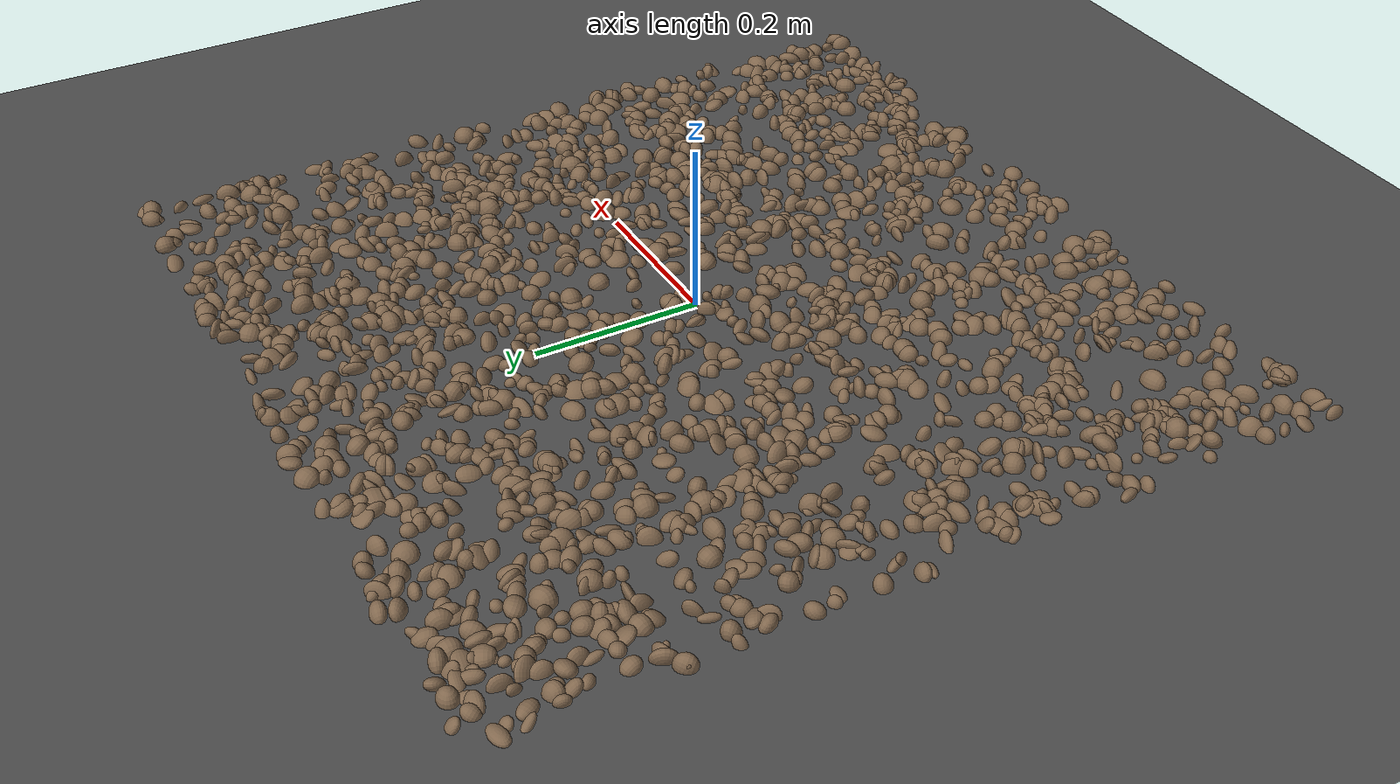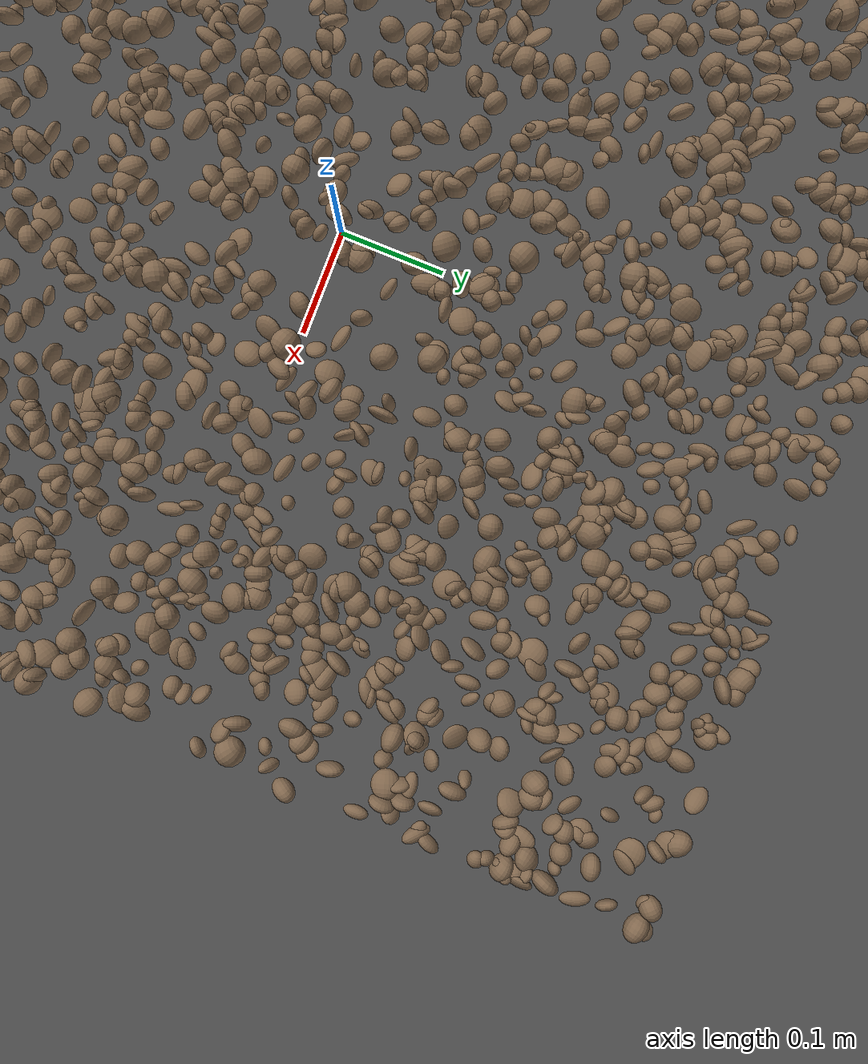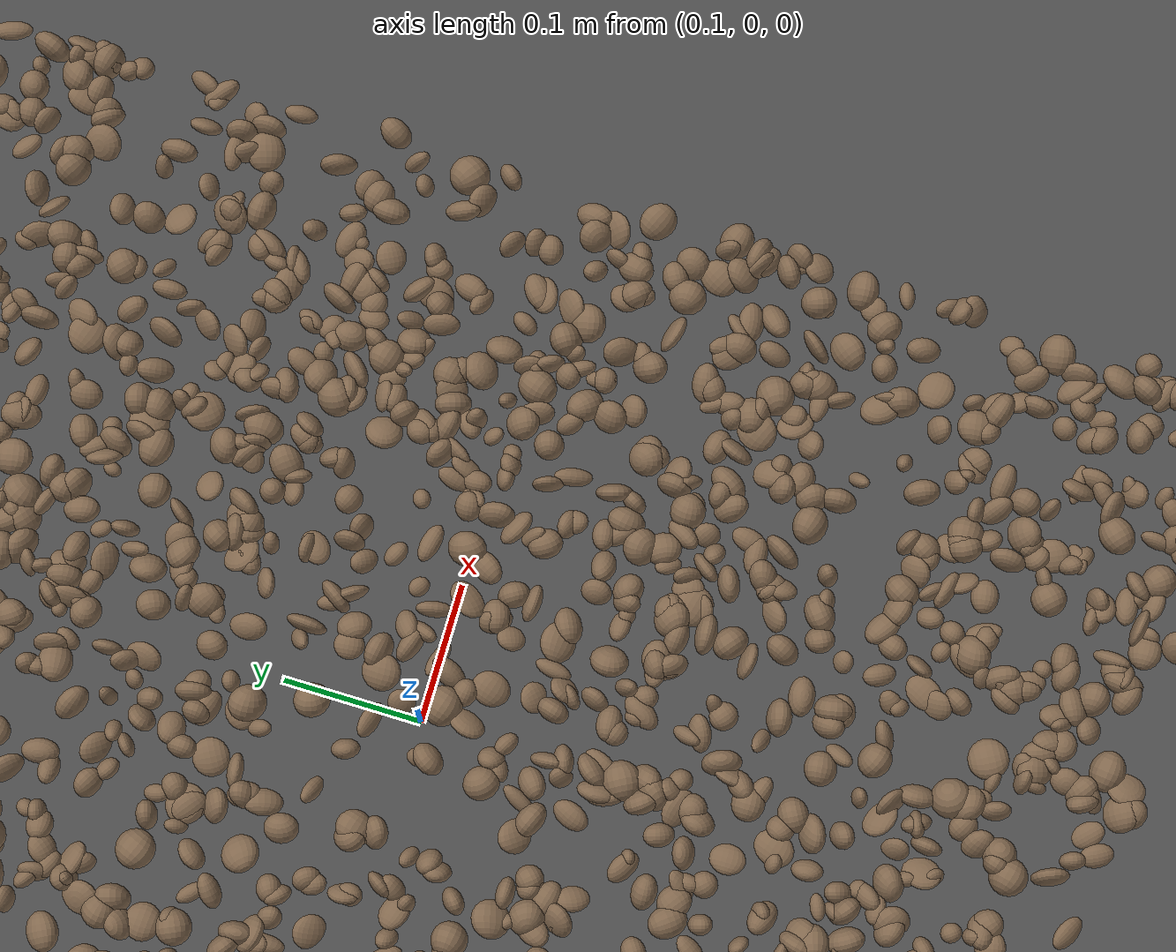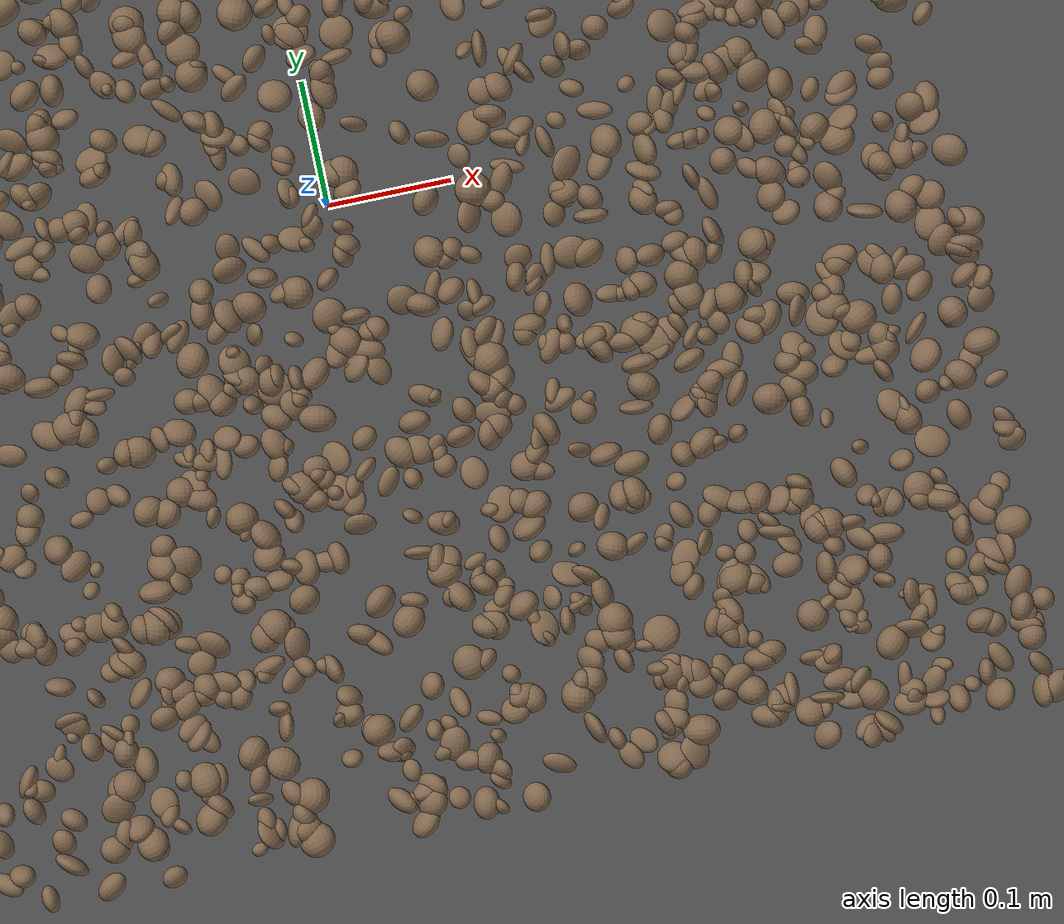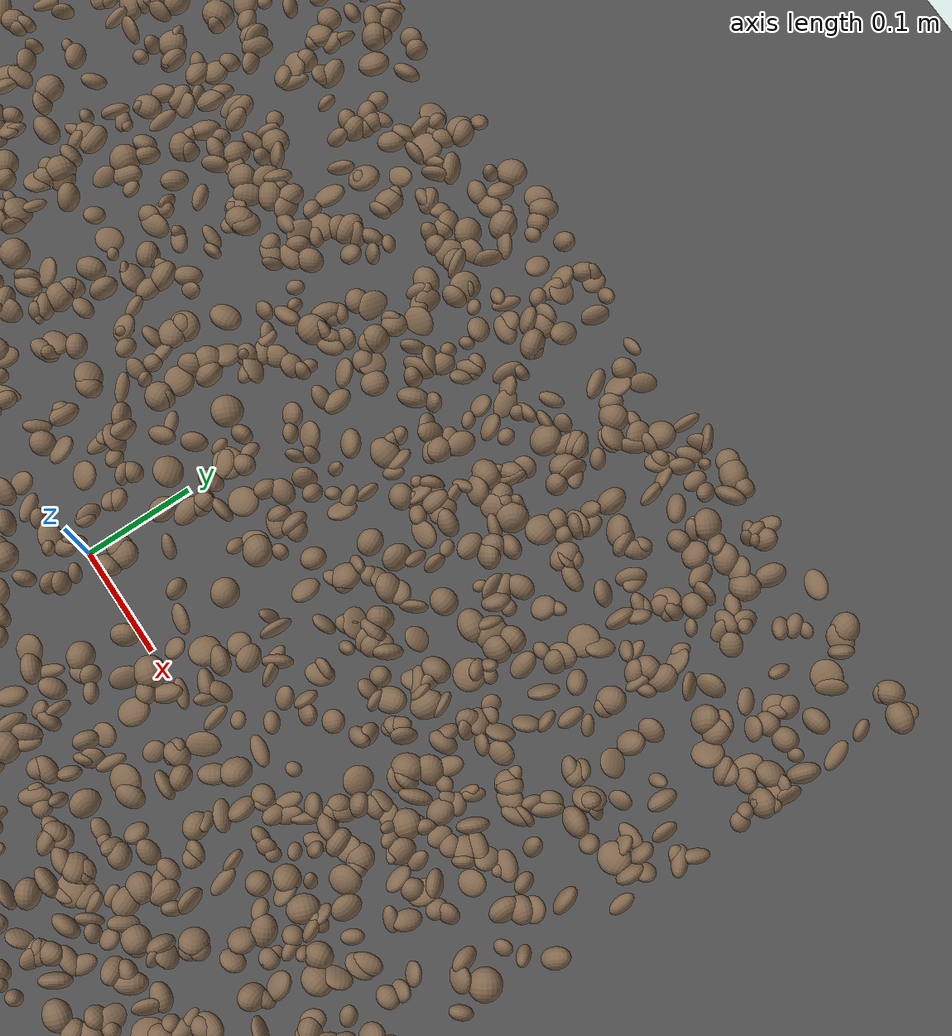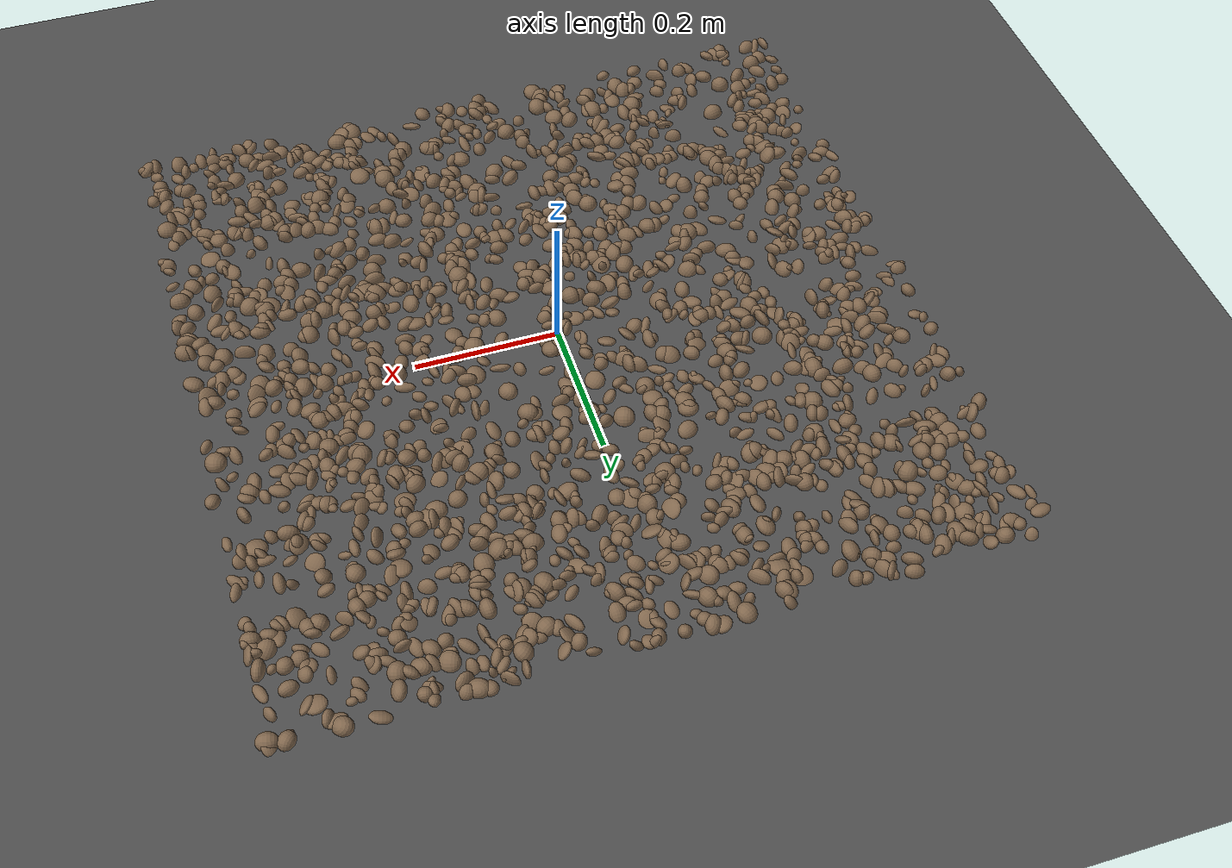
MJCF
<mujoco model="rocky_terrain_scene">
    <compiler angle="radian" inertiafromgeom="true" />
    <option timestep="0.002" gravity="0 0 -9.81" />

    <worldbody>
        <light name="sunlight" pos="5 5 5" dir="-1 -1 -1" diffuse="1 1 1" specular="0.5 0.5 0.5" ambient="0.5 0.5 0.5" />

        <geom name="ground_plane" type="plane" size="50 50 0.1" rgba="0.3 0.3 0.3 1" />

        <body name="rocky_terrain_body">

        </body>
    <body name="rock1" pos="-0.3778703389735878 0.4601858859480664 0.0004034292751588747"><joint type="free" /><geom type="ellipsoid" size="0.011644347169899372 0.013616685852145795 0.012115756341134699" quat="0.04106509607591691 0.40064325764098035 0.05258673387915214 0.5057049124039507" rgba="0.5 0.4 0.3 1" /></body><body name="rock2" pos="-0.3253367819425238 0.1983633393356169 0.0003023851830123704"><joint type="free" /><geom type="ellipsoid" size="0.00987606714598439 0.01119632719547885 0.013125691508577939" quat="0.07577432837853508 0.4668876869414051 0.12029588345471225 0.3370421012253476" rgba="0.5 0.4 0.3 1" /></body><body name="rock3" pos="-0.029330039556560106 0.3585958712330195 0.0008443050636275747"><joint type="free" /><geom type="ellipsoid" size="0.014144918006798603 0.007725647841570008 0.008511616914476907" quat="0.23655028069564762 0.09592264245285008 0.314052461271957 0.3534746155795452" rgba="0.5 0.4 0.3 1" /></body><body name="rock4" pos="-0.43635767926505065 -0.4102562757219177 0.0004222338036824931"><joint type="free" /><geom type="ellipsoid" size="0.009009555993888238 0.008124514606900697 0.009393431814381535" quat="0.7115021681041804 0.1765607541224829 0.0268562656588271 0.08508081211450953" rgba="0.5 0.4 0.3 1" /></body><body name="rock5" pos="0.47627111466458816 0.4959666275635509 0.000908231092503159"><joint type="free" /><geom type="ellipsoid" size="0.012925361888139385 0.011427213059439431 0.010624807601370656" quat="0.35447242610923124 0.3512531569370048 0.1871693386869891 0.10710507826677486" rgba="0.5 0.4 0.3 1" /></body><body name="rock6" pos="-0.36657737600373796 0.14435532618070257 0.00041588140450624404"><joint type="free" /><geom type="ellipsoid" size="0.01327614748467178 0.009587070595316976 0.006006686088489771" quat="0.21516249833413273 0.33674895343366723 0.2056692089893237 0.24241933924287634" rgba="0.5 0.4 0.3 1" /></body><body name="rock7" pos="0.3519616842016343 0.1583427296204849 0.0004748094976986911"><joint type="free" /><geom type="ellipsoid" size="0.010573985896486641 0.006567106533955229 0.005895016920068545" quat="0.3899880203002368 0.20551342026954045 0.2057058004541698 0.1987927589760529" rgba="0.5 0.4 0.3 1" /></body><body name="rock8" pos="0.033421424478691564 -0.49285787661004576 0.0009112011834794105"><joint type="free" /><geom type="ellipsoid" size="0.00986018903587677 0.005077062725692284 0.00760125220071964" quat="0.2382137967534867 0.020870774385726935 0.10786042962540514 0.6330549992353811" rgba="0.5 0.4 0.3 1" /></body><body name="rock9" pos="-0.12117421653061855 0.3764078638204641 0.0002746872130293588"><joint type="free" /><geom type="ellipsoid" size="0.006222901801021522 0.009437710853106778 0.011896214663481994" quat="0.2768251860983959 0.13135731386420632 0.19729766241058752 0.3945198376268103" rgba="0.5 0.4 0.3 1" /></body><body name="rock10" pos="0.3856582459159019 0.1283362111455396 7.065545081013647e-05"><joint type="free" /><geom type="ellipsoid" size="0.012476331040469139 0.012690339394656922 0.008106729947897025" quat="0.11519729033733021 0.5378396027522282 0.336223635638917 0.010739471271524548" rgba="0.5 0.4 0.3 1" /></body><body name="rock11" pos="-0.414268727240363 -0.26045183528878324 0.00025700488576592786"><joint type="free" /><geom type="ellipsoid" size="0.005199360516727876 0.012762613421144365 0.012035522279577326" quat="0.2080102982902209 0.26442859037834465 0.31205589758987556 0.21550521374155893" rgba="0.5 0.4 0.3 1" /></body><body name="rock12" pos="-0.47417095333275416 0.1970669694476328 0.0005161493475280028"><joint type="free" /><geom type="ellipsoid" size="0.014823679150388177 0.007095298120782665 0.009865968935850445" quat="0.051619376082846676 0.1771358238775958 0.45503690541964925 0.3162078946199084" rgba="0.5 0.4 0.3 1" /></body><body name="rock13" pos="-0.12176686388208668 0.43594969522734706 0.0009274364814056262"><joint type="free" /><geom type="ellipsoid" size="0.013507455510234752 0.012366963292781363 0.006041800633996067" quat="0.3003432183638107 0.42138307038487777 0.016129901197448927 0.26214381005386256" rgba="0.5 0.4 0.3 1" /></body><body name="rock14" pos="0.3143747801664525 0.09286793072367516 0.000571532284061835"><joint type="free" /><geom type="ellipsoid" size="0.00512657872467691 0.009690689151518276 0.012217821001980881" quat="0.15599058901465437 0.2977580419987114 0.21092830939874485 0.33532305958788944" rgba="0.5 0.4 0.3 1" /></body><body name="rock15" pos="0.39070583471189413 0.311201533198988 0.0002084118090197885"><joint type="free" /><geom type="ellipsoid" size="0.0076268101918220395 0.01109590166131286 0.012166453672091113" quat="0.25665429935025025 0.19563807058101487 0.4513152055954848 0.09639242447325007" rgba="0.5 0.4 0.3 1" /></body><body name="rock16" pos="0.48911626497921 0.3377087291852011 0.000764628750186678"><joint type="free" /><geom type="ellipsoid" size="0.007291158596413597 0.00961341250660066 0.007102078705213434" quat="0.0789481431447126 0.2613959201548571 0.25668997518722597 0.4029659615132044" rgba="0.5 0.4 0.3 1" /></body><body name="rock17" pos="-0.13808948140180322 -0.07660506834549297 0.0003466070219911294"><joint type="free" /><geom type="ellipsoid" size="0.007814777919127713 0.00815859549487606 0.013959981395103852" quat="0.17136191690998911 0.05340629920109272 0.4337251024796055 0.3415066814093127" rgba="0.5 0.4 0.3 1" /></body><body name="rock18" pos="0.20412027863567284 -0.0364022944281599 0.00035495548839978286"><joint type="free" /><geom type="ellipsoid" size="0.011550465743787305 0.01162450616679258 0.009371595965638538" quat="0.18473420245198233 0.17508252950682235 0.329696440195208 0.31048682784598736" rgba="0.5 0.4 0.3 1" /></body><body name="rock19" pos="0.22779936686995106 0.3351351368553974 0.0003446989004284157"><joint type="free" /><geom type="ellipsoid" size="0.014517348012397041 0.010936666701853993 0.010350384638501017" quat="0.01434625116480444 0.42431147432980837 0.512286282783451 0.049055991721936275" rgba="0.5 0.4 0.3 1" /></body><body name="rock20" pos="0.3449443761252027 -0.19136709031349242 0.0001581316241895544"><joint type="free" /><geom type="ellipsoid" size="0.007814494841049884 0.01046027101204428 0.008951933435964572" quat="0.269584236409282 0.25610283583951604 0.26465428315973993 0.20965864459146205" rgba="0.5 0.4 0.3 1" /></body><body name="rock21" pos="0.2544384662329413 -0.17880459865128895 0.0009888288289683729"><joint type="free" /><geom type="ellipsoid" size="0.007782783787905402 0.013476695186006287 0.012737147115583143" quat="0.3812972766682837 0.02097336514707918 0.043184610121504576 0.5545447480631326" rgba="0.5 0.4 0.3 1" /></body><body name="rock22" pos="-0.3835063750507076 0.10446556762875348 0.0008297301832300302"><joint type="free" /><geom type="ellipsoid" size="0.012490467477552974 0.011086982924891946 0.00750753777854732" quat="0.22566545891405732 0.27249977825403027 0.263754053142071 0.23808070968984144" rgba="0.5 0.4 0.3 1" /></body><body name="rock23" pos="0.26295720258408783 -0.058892557528419154 1.611702049356589e-05"><joint type="free" /><geom type="ellipsoid" size="0.006697797664756398 0.009797325404065754 0.01126760059053562" quat="0.23393898191143286 0.30880626655750715 0.3734583949211223 0.08379635660993769" rgba="0.5 0.4 0.3 1" /></body><body name="rock24" pos="0.36579623399912 -0.43138554571134946 0.0003868267117603168"><joint type="free" /><geom type="ellipsoid" size="0.012061017331425096 0.012882192983209292 0.014110866732096439" quat="0.25756919465034267 0.017473423286305086 0.4222411690849781 0.30271621297837414" rgba="0.5 0.4 0.3 1" /></body><body name="rock25" pos="0.23802770332415835 0.27075900992187807 0.0007676736299741286"><joint type="free" /><geom type="ellipsoid" size="0.006997953032724772 0.00671346514689849 0.0075614247608864925" quat="0.2809403568717612 0.21479277448157397 0.493706476436646 0.010560392210018846" rgba="0.5 0.4 0.3 1" /></body><body name="rock26" pos="-0.17559052945007203 0.06271514916394016 0.0002408873439433721"><joint type="free" /><geom type="ellipsoid" size="0.008699592694140255 0.014163287034768851 0.012433874983455804" quat="0.3146553424894723 0.13591248340342982 0.06937746094711805 0.48005471315997983" rgba="0.5 0.4 0.3 1" /></body><body name="rock27" pos="-0.20871161651531123 0.431441079407029 0.0007311506817498206"><joint type="free" /><geom type="ellipsoid" size="0.009670739876720277 0.008691795698482 0.008304484385621199" quat="0.12904706086607567 0.3776590567632022 0.27892484947305796 0.21436903289766415" rgba="0.5 0.4 0.3 1" /></body><body name="rock28" pos="0.2922624127874691 -0.007678196994228004 0.0006786010370481883"><joint type="free" /><geom type="ellipsoid" size="0.0067742231800487045 0.010655993780032997 0.008893276959967228" quat="0.25919780397995856 0.07452899310107167 0.3290911881064435 0.33718201481252624" rgba="0.5 0.4 0.3 1" /></body><body name="rock29" pos="0.29944443584777436 0.18914994460157786 0.00013903642760285594"><joint type="free" /><geom type="ellipsoid" size="0.00917202035581046 0.010826874423026813 0.014600822003053859" quat="0.1928103692632213 0.0629092145057792 0.6618871021966596 0.0823933140343399" rgba="0.5 0.4 0.3 1" /></body><body name="rock30" pos="-0.24491505006679226 0.34506402162621297 0.0002104028544436789"><joint type="free" /><geom type="ellipsoid" size="0.008456248973975707 0.006798346055219458 0.008072953277914168" quat="0.18270202034268626 0.24833257347473514 0.40388927637021205 0.16507612981236655" rgba="0.5 0.4 0.3 1" /></body><body name="rock31" pos="-0.41389312137236933 -0.33511898511254556 0.0008586953415014505"><joint type="free" /><geom type="ellipsoid" size="0.008765719900913644 0.009489174426248389 0.009434273496256834" quat="0.13916266321000037 0.021342007510053114 0.4112396137801863 0.4282557154997602" rgba="0.5 0.4 0.3 1" /></body><body name="rock32" pos="0.47487792232050574 -0.4934402412979 0.0009785294009646932"><joint type="free" /><geom type="ellipsoid" size="0.013416862572950862 0.011733811325495797 0.007998196272813823" quat="0.27333647003131095 0.25586585768057285 0.31852560968996535 0.1522720625981509" rgba="0.5 0.4 0.3 1" /></body><body name="rock33" pos="-0.12149215579233041 -0.347742651123491 0.00044972004641393305"><joint type="free" /><geom type="ellipsoid" size="0.014230324041893217 0.009745752928383488 0.007210324076896174" quat="0.4547078900444878 0.4240899004874622 0.000435501956616779 0.1207667075114333" rgba="0.5 0.4 0.3 1" /></body><body name="rock34" pos="0.19683806340640608 0.07115909793883235 0.00010785584598773645"><joint type="free" /><geom type="ellipsoid" size="0.008690067480183817 0.006659678941638464 0.011975933873482392" quat="0.24734468389005218 0.5972083015591053 0.007308662791345403 0.14813835175949708" rgba="0.5 0.4 0.3 1" /></body><body name="rock35" pos="-0.3396317575585328 -0.28147977138100233 0.00041000642344517604"><joint type="free" /><geom type="ellipsoid" size="0.006584290392194325 0.006766597501909865 0.008350086910306713" quat="0.07201082742622464 0.16026084207341101 0.5234733690654917 0.24425496143487269" rgba="0.5 0.4 0.3 1" /></body><body name="rock36" pos="-0.3008960781786051 0.28467184901395437 0.0007777883803340265"><joint type="free" /><geom type="ellipsoid" size="0.014218244015997514 0.005557819350998516 0.01054579178126179" quat="0.17553506076116634 0.3411118074863155 0.11644940944127376 0.3669037223112443" rgba="0.5 0.4 0.3 1" /></body><body name="rock37" pos="-0.25108142155249635 0.2865573275875378 0.0005706624053774438"><joint type="free" /><geom type="ellipsoid" size="0.008785303924197109 0.007818740609098346 0.011524422895582438" quat="0.37661410461344935 0.08727650650161034 0.5189254132949489 0.017183975589991466" rgba="0.5 0.4 0.3 1" /></body><body name="rock38" pos="-0.23128735072563866 0.0526879207010289 0.0004011256082093011"><joint type="free" /><geom type="ellipsoid" size="0.006595475285311632 0.013755351695939094 0.007172952479151151" quat="0.23278191409709453 0.31884219826131543 0.18312815536746962 0.26524773227412035" rgba="0.5 0.4 0.3 1" /></body><body name="rock39" pos="0.2214219794599328 -0.11352255760610042 0.00045564384661600255"><joint type="free" /><geom type="ellipsoid" size="0.008984883452502711 0.014000115771358332 0.008140224193061017" quat="0.22537572282190957 0.35225126669013906 0.1664428548732512 0.25593015561470017" rgba="0.5 0.4 0.3 1" /></body><body name="rock40" pos="-0.02648044524362525 0.3642230853153924 2.9403930187092753e-05"><joint type="free" /><geom type="ellipsoid" size="0.012441976814177434 0.013602838183526283 0.006552950604051315" quat="0.23395697689621142 0.18956438385902277 0.15128276667357665 0.42519587257118907" rgba="0.5 0.4 0.3 1" /></body><body name="rock41" pos="-0.4389882690480964 0.2416697578448802 0.0005905936153698547"><joint type="free" /><geom type="ellipsoid" size="0.009999558883122331 0.014546268287082127 0.005183866729423396" quat="0.3999541231194977 0.30136924941203214 0.21749945889904762 0.08117716856942259" rgba="0.5 0.4 0.3 1" /></body><body name="rock42" pos="0.2257916780496353 0.004472988861474292 0.0006842632050001793"><joint type="free" /><geom type="ellipsoid" size="0.014571817255863147 0.011471756036872314 0.013276720718400803" quat="0.3687212885065501 0.02957293902712666 0.26157321896083346 0.34013255350548977" rgba="0.5 0.4 0.3 1" /></body><body name="rock43" pos="-0.42784440462494644 0.28287322989478836 0.0007353847409018426"><joint type="free" /><geom type="ellipsoid" size="0.009598374347099287 0.008337307275293644 0.008493178163888108" quat="0.25540087844474385 0.05531132145309427 0.32949191846643033 0.35979588163573145" rgba="0.5 0.4 0.3 1" /></body><body name="rock44" pos="0.12509123164086566 0.20434461992098463 0.0007287371112315497"><joint type="free" /><geom type="ellipsoid" size="0.012604675224248178 0.010901091329973299 0.010929339617003393" quat="0.08323011092240656 0.3115917745213826 0.29901537293842506 0.3061627416177858" rgba="0.5 0.4 0.3 1" /></body><body name="rock45" pos="-0.1521770240289836 -0.4143134599180718 0.0006113788150257331"><joint type="free" /><geom type="ellipsoid" size="0.007595381267651174 0.007334573653023795 0.006640414852346785" quat="0.26059774707865757 0.2702652226169347 0.03499749848810839 0.4341395318162994" rgba="0.5 0.4 0.3 1" /></body><body name="rock46" pos="-0.08759638352462606 0.17616475073529325 5.3628613838382246e-05"><joint type="free" /><geom type="ellipsoid" size="0.01297299774912979 0.014995225405713637 0.013034105439167443" quat="0.3278326635393651 0.21424154537423204 0.12248957685492655 0.3354362142314764" rgba="0.5 0.4 0.3 1" /></body><body name="rock47" pos="0.11329547608727353 -0.4206075799455772 0.0009728186521515857"><joint type="free" /><geom type="ellipsoid" size="0.013712327184134426 0.014411048799446179 0.013481351848250459" quat="0.2363370316341067 0.3292389410869953 0.16797400943614454 0.2664500178427535" rgba="0.5 0.4 0.3 1" /></body><body name="rock48" pos="0.34129122541603474 -0.40833763847304916 0.0003200742423433834"><joint type="free" /><geom type="ellipsoid" size="0.007797359001158391 0.005142032451317022 0.012049725360869484" quat="0.24458494774852813 0.04512029596400875 0.48963514922265206 0.2206596070648111" rgba="0.5 0.4 0.3 1" /></body><body name="rock49" pos="0.23024365004725078 -0.11234709765642859 0.0009527901564637266"><joint type="free" /><geom type="ellipsoid" size="0.010261916137477994 0.011936730619470128 0.012404500555652126" quat="0.5196431543590866 0.0830842750960517 0.051081100666495745 0.3461914698783661" rgba="0.5 0.4 0.3 1" /></body><body name="rock50" pos="0.395501046721366 0.26990250255723824 0.0006391716340859839"><joint type="free" /><geom type="ellipsoid" size="0.013905675781118631 0.005057113223489435 0.012723666718412952" quat="0.4233748540390417 0.28478681181343396 0.23833048782597901 0.05350784632154534" rgba="0.5 0.4 0.3 1" /></body><body name="rock51" pos="0.1792780346183075 -0.27248795913047574 4.7623916418121586e-05"><joint type="free" /><geom type="ellipsoid" size="0.009476539460320623 0.010142930674531196 0.013685796818288815" quat="0.020702645401465523 0.09938026059703957 0.6349535784649651 0.24496351553652965" rgba="0.5 0.4 0.3 1" /></body><body name="rock52" pos="-0.3877167371053497 0.45690778771033824 0.00032920702898390873"><joint type="free" /><geom type="ellipsoid" size="0.007126952434901572 0.005587628735495862 0.0120320815650053" quat="0.28390365244032145 0.19843037533520633 0.14406288317598048 0.3736030890484918" rgba="0.5 0.4 0.3 1" /></body><body name="rock53" pos="0.33845557284954675 -0.3913832065497127 0.00019586221486782862"><joint type="free" /><geom type="ellipsoid" size="0.012961709775414627 0.006264836908338186 0.012273469326235504" quat="0.23254228374168395 0.15465867034548517 0.2894498994787863 0.32334914643404467" rgba="0.5 0.4 0.3 1" /></body><body name="rock54" pos="-0.18703199519488034 -0.3894631208452741 0.0009669099222586287"><joint type="free" /><geom type="ellipsoid" size="0.014813426719922616 0.007256461221067729 0.011975733043036958" quat="0.4687497543549368 0.02895670021020771 0.26627232419448427 0.23602122124037125" rgba="0.5 0.4 0.3 1" /></body><body name="rock55" pos="0.015508376736179663 -0.20424701264716227 0.0006269874809158508"><joint type="free" /><geom type="ellipsoid" size="0.009019521039737912 0.0064235656641554815 0.006404522835236757" quat="0.09217107041908565 0.6467576926587202 0.1398034742607869 0.12126776266140729" rgba="0.5 0.4 0.3 1" /></body><body name="rock56" pos="0.23686634658610506 0.49926872532910216 1.3686417953851505e-05"><joint type="free" /><geom type="ellipsoid" size="0.010830185498631729 0.008447926239902582 0.010277442908347473" quat="0.16689606833708823 0.20090589674214013 0.29112703276827123 0.34107100215250047" rgba="0.5 0.4 0.3 1" /></body><body name="rock57" pos="0.0483720496222565 -0.3777981302430098 0.0006877037436523672"><joint type="free" /><geom type="ellipsoid" size="0.00906700210441851 0.010314916945731833 0.006679998095624039" quat="0.3095799529275851 0.381763344036549 0.003198249342349248 0.30545845369351676" rgba="0.5 0.4 0.3 1" /></body><body name="rock58" pos="-0.09464537236742188 0.4767801975242243 0.0006940908145157534"><joint type="free" /><geom type="ellipsoid" size="0.00673739462249379 0.012688228727814124 0.006585674130302318" quat="0.2563020391243947 0.23098524097468126 0.2287779152797102 0.2839348046212138" rgba="0.5 0.4 0.3 1" /></body><body name="rock59" pos="0.3479942506738244 -0.0462282287634771 0.0002714378558208971"><joint type="free" /><geom type="ellipsoid" size="0.011361135783813706 0.01127310309913728 0.014818633779998366" quat="0.26832437213873717 0.3633582420529703 0.3642621434509339 0.004055242357358617" rgba="0.5 0.4 0.3 1" /></body><body name="rock60" pos="0.13667909137177303 -0.46066892980998786 0.0004803573146415084"><joint type="free" /><geom type="ellipsoid" size="0.006220420739180448 0.009120316373906479 0.009428746910978933" quat="0.3906880114295661 0.4654596313961481 0.1163946358939825 0.02745772128030331" rgba="0.5 0.4 0.3 1" /></body><body name="rock61" pos="-0.15284167545430927 -0.151264428064521 0.00016112564510657368"><joint type="free" /><geom type="ellipsoid" size="0.008986800975234629 0.012119658787957961 0.013504703682345184" quat="0.21704467165825345 0.3882523094091065 0.03757345849168523 0.35712956044095484" rgba="0.5 0.4 0.3 1" /></body><body name="rock62" pos="0.2452063237395402 -0.39693884584437666 0.00040693595333356024"><joint type="free" /><geom type="ellipsoid" size="0.009770923428539222 0.006036906098709001 0.014768703351506898" quat="0.3924887957622604 0.41874894464072204 0.04139165867076157 0.14737060092625592" rgba="0.5 0.4 0.3 1" /></body><body name="rock63" pos="-0.27624505077117134 0.39888296735894635 0.000902987004626952"><joint type="free" /><geom type="ellipsoid" size="0.01004224590088589 0.013389865627601673 0.009965189758794346" quat="0.25288102942003693 0.18136364984417583 0.29586512505465984 0.2698901956811274" rgba="0.5 0.4 0.3 1" /></body><body name="rock64" pos="-0.35991254370627923 -0.4739816924555271 0.00048080085346723057"><joint type="free" /><geom type="ellipsoid" size="0.014268987295196208 0.007807975641303308 0.007963417653399881" quat="0.1736368001082088 0.09596065276754862 0.4480422432483084 0.2823603038759342" rgba="0.5 0.4 0.3 1" /></body><body name="rock65" pos="0.3358219506379547 0.007364502891616276 0.0007282378222014378"><joint type="free" /><geom type="ellipsoid" size="0.005932867501445048 0.011774575196583877 0.005659596366252078" quat="0.2821228870503127 0.1483059199891719 0.2849882673627198 0.28458292559779563" rgba="0.5 0.4 0.3 1" /></body><body name="rock66" pos="0.0498318605705067 0.36166171943459335 0.0008155302262994375"><joint type="free" /><geom type="ellipsoid" size="0.006550469068000018 0.006301145698579619 0.0050785591001866" quat="0.4438281247184165 0.11733848060899336 0.1682152711281725 0.27061812354441755" rgba="0.5 0.4 0.3 1" /></body><body name="rock67" pos="0.3784090397879619 0.35917134347814994 7.804759559582253e-05"><joint type="free" /><geom type="ellipsoid" size="0.005197938778260671 0.014203730591623547 0.011882800754778433" quat="0.42306818762810494 0.3043161592052443 0.038798668161352204 0.23381698500529854" rgba="0.5 0.4 0.3 1" /></body><body name="rock68" pos="-0.15839527695944855 -0.48771241694975287 0.0001374455600534902"><joint type="free" /><geom type="ellipsoid" size="0.005226064517848888 0.0053647961098997055 0.00691373513460925" quat="0.08994688893669134 0.34588971483080055 0.20078576779132634 0.3633776284411817" rgba="0.5 0.4 0.3 1" /></body><body name="rock69" pos="0.3380431408332375 0.38915587779592453 0.0007180585568545187"><joint type="free" /><geom type="ellipsoid" size="0.008115575750756557 0.00785066753037021 0.005139374475547273" quat="0.013671058379967318 0.20394631871585694 0.3987460563965993 0.3836365665075765" rgba="0.5 0.4 0.3 1" /></body><body name="rock70" pos="-0.16925692896867972 0.4205111132469912 0.0007385450904240376"><joint type="free" /><geom type="ellipsoid" size="0.013153882624339485 0.011163783377858392 0.009004893470771795" quat="0.19239685824849292 0.3960025949443114 0.31952290291178653 0.09207764389540911" rgba="0.5 0.4 0.3 1" /></body><body name="rock71" pos="0.37288969862447097 -0.2742663818872604 0.00029287194354412315"><joint type="free" /><geom type="ellipsoid" size="0.011071184364522419 0.005713747774616413 0.006198716821353294" quat="0.035332515681177304 0.3830116317997487 0.033286551168126774 0.5483693013509473" rgba="0.5 0.4 0.3 1" /></body><body name="rock72" pos="0.21396492810725398 0.47495949037328666 0.000709975378666544"><joint type="free" /><geom type="ellipsoid" size="0.007012909118744064 0.006199134423775006 0.012116146703343787" quat="0.005075999522678104 0.3180903572081027 0.31049443043525154 0.36633921283396764" rgba="0.5 0.4 0.3 1" /></body><body name="rock73" pos="-0.3312968176117972 0.23072774476322855 0.00028593119796384314"><joint type="free" /><geom type="ellipsoid" size="0.01249325924117666 0.01443643185855592 0.0066337291321045076" quat="0.31242553916693455 0.23521860208282433 0.364862360768405 0.08749349798183606" rgba="0.5 0.4 0.3 1" /></body><body name="rock74" pos="0.07381245206630549 0.3008337668851876 0.0008622541728365646"><joint type="free" /><geom type="ellipsoid" size="0.009913976625763949 0.007975223401232915 0.014976266514997557" quat="0.027741399415644838 0.22352858025397201 0.5392249532058488 0.20950506712453426" rgba="0.5 0.4 0.3 1" /></body><body name="rock75" pos="-0.2653389508561047 0.3792635263154782 0.0009646623820514399"><joint type="free" /><geom type="ellipsoid" size="0.0133414027823789 0.0067427759415648846 0.005926910849050809" quat="0.35052599335634205 0.22892715224810137 0.12218561792421963 0.29836123647133705" rgba="0.5 0.4 0.3 1" /></body><body name="rock76" pos="-0.026957101736970523 0.04487749329734814 0.0007369468633571317"><joint type="free" /><geom type="ellipsoid" size="0.010415258482394465 0.010086556332422877 0.007625257725653606" quat="0.05201371669239409 0.3279559523301081 0.3548174799601522 0.26521285101734554" rgba="0.5 0.4 0.3 1" /></body><body name="rock77" pos="0.4677227917194775 -0.3763476602771838 0.00054314027903003"><joint type="free" /><geom type="ellipsoid" size="0.013096926999135668 0.013624127717986968 0.006329349054584583" quat="0.17019349433703748 0.3726590449623233 0.23793587964101898 0.21921158105962027" rgba="0.5 0.4 0.3 1" /></body><body name="rock78" pos="-0.19599535260854806 -0.0012473124930277857 0.00024716053194405495"><joint type="free" /><geom type="ellipsoid" size="0.01125135127809062 0.007428567762030054 0.01461693966034519" quat="0.27837561034523334 0.4070934902882749 0.15106211455624272 0.16346878481024898" rgba="0.5 0.4 0.3 1" /></body><body name="rock79" pos="-0.28240095226458684 -0.36183168574537117 0.0008019257653921536"><joint type="free" /><geom type="ellipsoid" size="0.012242523540962835 0.006116835779899863 0.012373648028028681" quat="0.2707527915481033 0.40504581906593484 0.05852300456347308 0.2656783848224888" rgba="0.5 0.4 0.3 1" /></body><body name="rock80" pos="0.023836881401353427 0.371586644811005 0.0003454678549288908"><joint type="free" /><geom type="ellipsoid" size="0.007016197086380618 0.007674719836275709 0.0055883088168173145" quat="0.3882475366851338 0.37742213068790875 0.17076436294400205 0.06356596968295544" rgba="0.5 0.4 0.3 1" /></body><body name="rock81" pos="0.27006933051814064 0.4390041010611053 9.7673115225554e-05"><joint type="free" /><geom type="ellipsoid" size="0.011698356103796671 0.006397452155303418 0.006801942391430888" quat="0.07097130152977506 0.2643987900366561 0.046192105235493455 0.6184378031980753" rgba="0.5 0.4 0.3 1" /></body><body name="rock82" pos="0.27435387335705974 0.3716816142665139 0.0009645239919619609"><joint type="free" /><geom type="ellipsoid" size="0.013802968943375387 0.010743654699091122 0.006976323468384863" quat="0.3590786520945935 0.24960144732541997 0.12598620238268032 0.26533369819730623" rgba="0.5 0.4 0.3 1" /></body><body name="rock83" pos="0.35123945213907226 -0.00989454704681536 0.00024885765653199734"><joint type="free" /><geom type="ellipsoid" size="0.012633647963959613 0.01292137535331107 0.01433104549941086" quat="0.028676564497074286 0.11896614619996686 0.44803927042467107 0.40431801887828767" rgba="0.5 0.4 0.3 1" /></body><body name="rock84" pos="0.11495599861057149 0.2550297579629506 0.0002511254963622497"><joint type="free" /><geom type="ellipsoid" size="0.00887366268396689 0.008092851829284617 0.006182973227373965" quat="0.2543854407422006 0.2695556171902658 0.0056425414020887495 0.4704164006654448" rgba="0.5 0.4 0.3 1" /></body><body name="rock85" pos="0.30137870436545633 0.48082677578323996 0.0008488018432715611"><joint type="free" /><geom type="ellipsoid" size="0.011439403735644156 0.012596906771906242 0.007007256349262527" quat="0.43762509677345207 0.03800191524826145 0.41219418178416134 0.11217880619412508" rgba="0.5 0.4 0.3 1" /></body><body name="rock86" pos="-0.19661477238165748 0.186765868720971 0.0001605971676534833"><joint type="free" /><geom type="ellipsoid" size="0.006034011880473504 0.005975142064813423 0.010583269243100737" quat="0.3025228059030028 0.3306538783301543 0.24210683831441926 0.12471647745242366" rgba="0.5 0.4 0.3 1" /></body><body name="rock87" pos="-0.3632987510142758 0.27750774920534826 0.0007351755278205023"><joint type="free" /><geom type="ellipsoid" size="0.006589321223845863 0.009021998444066788 0.007146616203213017" quat="0.13721408846393324 0.2891997645530648 0.35683132111302623 0.21675482586997574" rgba="0.5 0.4 0.3 1" /></body><body name="rock88" pos="-0.12977435330999254 -0.1310434316188146 0.00039632040705698103"><joint type="free" /><geom type="ellipsoid" size="0.0140111350186908 0.00805380881700707 0.01083972479720386" quat="0.007893305698486366 0.19488096653333398 0.0545324407073509 0.7426932870608287" rgba="0.5 0.4 0.3 1" /></body><body name="rock89" pos="0.10017572850773693 -0.26035042067987535 0.0008012557808864695"><joint type="free" /><geom type="ellipsoid" size="0.010095659973438281 0.008633855000425445 0.009953601887875318" quat="0.26406232263276164 0.36155096027901473 0.28210251468334985 0.09228420240487366" rgba="0.5 0.4 0.3 1" /></body><body name="rock90" pos="-0.14565403837020496 0.46053345454042616 0.0008240916140882493"><joint type="free" /><geom type="ellipsoid" size="0.007489384679126266 0.011674848064853836 0.008717398285514646" quat="0.223394744009872 0.3646345416120207 0.0223026512693063 0.389668063108801" rgba="0.5 0.4 0.3 1" /></body><body name="rock91" pos="0.24797501844162206 0.1714754731387217 0.0006503655716724278"><joint type="free" /><geom type="ellipsoid" size="0.014843485947882581 0.009933869809991112 0.006531009479532827" quat="0.09946774892388434 0.15394037029420596 0.43226296264044456 0.31432891814146513" rgba="0.5 0.4 0.3 1" /></body><body name="rock92" pos="0.40163417524095424 0.13865605145065374 0.000787217065166113"><joint type="free" /><geom type="ellipsoid" size="0.010108331836708218 0.013709806051166496 0.006596819059476966" quat="0.19926168252892767 0.6236753952563019 0.09728453941442336 0.07977838280034703" rgba="0.5 0.4 0.3 1" /></body><body name="rock93" pos="-0.36427777334451406 -0.20318072209996396 0.0002997098795341846"><joint type="free" /><geom type="ellipsoid" size="0.014891430674323684 0.0068107654437110435 0.005200375228945588" quat="0.2122752337628096 0.2643577420441776 0.29127453527043623 0.23209248892257656" rgba="0.5 0.4 0.3 1" /></body><body name="rock94" pos="0.38767913661839437 -0.1237730706217477 0.0002885770638102176"><joint type="free" /><geom type="ellipsoid" size="0.009872866390212957 0.009212249990118795 0.014814708775997682" quat="0.22135848205324024 0.22334318777707837 0.19556367511580594 0.3597346550538755" rgba="0.5 0.4 0.3 1" /></body><body name="rock95" pos="-0.3127081390984727 0.3698682789458366 0.0008803940601093738"><joint type="free" /><geom type="ellipsoid" size="0.010723326335932579 0.014681059926402958 0.009099935115893864" quat="0.16236956601129932 0.28321687973757326 0.045686176322940295 0.5087273779281871" rgba="0.5 0.4 0.3 1" /></body><body name="rock96" pos="-0.309830286262616 -0.1227060364876873 0.0006831701297998331"><joint type="free" /><geom type="ellipsoid" size="0.005869010965479882 0.00892233522132008 0.010130093764623715" quat="0.2974686297381393 0.32170603291144034 0.18359734059517394 0.19722799675524638" rgba="0.5 0.4 0.3 1" /></body><body name="rock97" pos="-0.06589543692949285 0.39925927525090144 0.0009709385502248825"><joint type="free" /><geom type="ellipsoid" size="0.009446224496042509 0.011380809983576936 0.009732731337592435" quat="0.20310024061247872 0.22346527686464893 0.29782431033347634 0.275610172189396" rgba="0.5 0.4 0.3 1" /></body><body name="rock98" pos="-0.4428852858261568 0.3973225405093055 0.0003373718686298215"><joint type="free" /><geom type="ellipsoid" size="0.011805977884297646 0.012005575856017168 0.006339726753248056" quat="0.09242973653671187 0.4696237634406112 0.09482463991849832 0.34312186010417867" rgba="0.5 0.4 0.3 1" /></body><body name="rock99" pos="0.13434076224308833 0.3272839630927017 0.000999434331820574"><joint type="free" /><geom type="ellipsoid" size="0.009921565588206968 0.005733350297245244 0.005086366229830631" quat="0.2688956691107348 0.28889320625234655 0.01212138398913259 0.430089740647786" rgba="0.5 0.4 0.3 1" /></body><body name="rock100" pos="0.2842614088989692 -0.29692965905583024 0.000938887515397126"><joint type="free" /><geom type="ellipsoid" size="0.012835542052250133 0.01286805995030147 0.010852446204311625" quat="0.2784903623291127 0.32374841385878594 0.05445901333354115 0.34330221047856013" rgba="0.5 0.4 0.3 1" /></body><body name="rock101" pos="-0.17559931289622333 -0.2118680708809424 0.000563304899249431"><joint type="free" /><geom type="ellipsoid" size="0.011808232023410449 0.012797842221995032 0.01002245187420067" quat="0.26012714921811364 0.3265534887842193 0.3799130484155355 0.03340631358213154" rgba="0.5 0.4 0.3 1" /></body><body name="rock102" pos="0.4238898401855824 0.2566711708899001 0.0006019257686727077"><joint type="free" /><geom type="ellipsoid" size="0.005674140132607945 0.010215174752985072 0.01024523886219865" quat="0.30820092260660165 0.06342012458268026 0.3318782631156838 0.29650068969503435" rgba="0.5 0.4 0.3 1" /></body><body name="rock103" pos="0.21037973743639682 0.3603183140451677 0.0008121474251577081"><joint type="free" /><geom type="ellipsoid" size="0.00670358259329999 0.014500286300652431 0.011551958936036093" quat="0.234491814596978 0.3678647335361354 0.3731241083930496 0.024519343473836896" rgba="0.5 0.4 0.3 1" /></body><body name="rock104" pos="0.32842768129422895 0.33754143594338737 2.954249790356589e-05"><joint type="free" /><geom type="ellipsoid" size="0.011956339924072544 0.007378177838020871 0.0051582892971810046" quat="0.09011293707549078 0.30969123695760337 0.33700354954202233 0.26319227642488363" rgba="0.5 0.4 0.3 1" /></body><body name="rock105" pos="0.4538780300595301 -0.052706320447840294 0.00022222274929856813"><joint type="free" /><geom type="ellipsoid" size="0.011267147660413535 0.01105042812466087 0.014150100211513892" quat="0.04949703353083371 0.1018426252632839 0.5544423769045234 0.2942179643013591" rgba="0.5 0.4 0.3 1" /></body><body name="rock106" pos="0.26528108238646964 -0.1276767319738651 0.00022811581928274772"><joint type="free" /><geom type="ellipsoid" size="0.013524216858104569 0.010109131238703165 0.011723707412671397" quat="0.19192431935468243 0.19809413382779514 0.3694374994450093 0.24054404737251303" rgba="0.5 0.4 0.3 1" /></body><body name="rock107" pos="-0.33467062384909774 0.1924093449785036 0.0005815543706437043"><joint type="free" /><geom type="ellipsoid" size="0.012205555750845563 0.00524818424765654 0.0054551623308360005" quat="0.31345212865505606 0.4630253202420398 0.1261351117620957 0.09738743934080848" rgba="0.5 0.4 0.3 1" /></body><body name="rock108" pos="0.4776991622359532 0.22919397481072423 0.000976064082225003"><joint type="free" /><geom type="ellipsoid" size="0.013390391742291494 0.012094928843378091 0.007016393871657789" quat="0.25387123160890823 0.2508972591357684 0.3220270325312092 0.1732044767241143" rgba="0.5 0.4 0.3 1" /></body><body name="rock109" pos="0.1793075947197904 -0.42131603556176234 0.0003618793060618386"><joint type="free" /><geom type="ellipsoid" size="0.009441600395099083 0.00641868921120843 0.005214141136807459" quat="0.22676770804185517 0.3044865836419492 0.18117064966780955 0.2875750586483861" rgba="0.5 0.4 0.3 1" /></body><body name="rock110" pos="-0.2385730859963734 -0.4697220273006878 0.0003651028820021227"><joint type="free" /><geom type="ellipsoid" size="0.010158660207736887 0.01051899787884951 0.01058159038289197" quat="0.3594566944371604 0.3432089497137559 0.06357107366600191 0.23376328218308182" rgba="0.5 0.4 0.3 1" /></body><body name="rock111" pos="-0.21717403663847212 0.13528773325370702 0.0005325538966760991"><joint type="free" /><geom type="ellipsoid" size="0.0101882734067381 0.012028589548690478 0.013367978557240517" quat="0.19657424270539647 0.1314393788653886 0.3234792892577591 0.34850708917145595" rgba="0.5 0.4 0.3 1" /></body><body name="rock112" pos="-0.2924124397381037 -0.29864843374915706 0.00042884266149854265"><joint type="free" /><geom type="ellipsoid" size="0.013279393494262732 0.007816609873625301 0.009788999525496545" quat="0.05193662106908322 0.3670838847281765 0.31990840190093783 0.26107109230180253" rgba="0.5 0.4 0.3 1" /></body><body name="rock113" pos="0.4960004292886253 0.28242484744662677 0.00013306217109368423"><joint type="free" /><geom type="ellipsoid" size="0.012966451162069376 0.008433759344582965 0.006288146786319436" quat="0.27275674447389325 0.3423687866494741 0.28166356411476784 0.10321090476186486" rgba="0.5 0.4 0.3 1" /></body><body name="rock114" pos="0.07687513176721428 -0.41541730327543014 0.00038939458109222636"><joint type="free" /><geom type="ellipsoid" size="0.011066347849104258 0.010296315415271685 0.011739442285621638" quat="0.3740411442811006 0.32569347176963337 0.13341013321625078 0.16685525073301533" rgba="0.5 0.4 0.3 1" /></body><body name="rock115" pos="-0.40841504648796423 -0.18900068200745346 0.0005248151378495008"><joint type="free" /><geom type="ellipsoid" size="0.008404430685273832 0.007771162972711681 0.0052996828362544745" quat="0.32025664057397824 0.37121054946230264 0.14367184481612263 0.16486096514759654" rgba="0.5 0.4 0.3 1" /></body><body name="rock116" pos="0.14767138071528885 -0.18824470153533246 0.0006871327500397905"><joint type="free" /><geom type="ellipsoid" size="0.014126874606109417 0.00935532776527145 0.007502670781007472" quat="0.2771555547856059 0.5382069834644923 0.03960521352587643 0.14503224822402533" rgba="0.5 0.4 0.3 1" /></body><body name="rock117" pos="0.35093240181933605 0.29803220118611207 0.00017514244521115742"><joint type="free" /><geom type="ellipsoid" size="0.013024283729763522 0.011560774519909861 0.01232903721220804" quat="0.36597006559775 0.3390259985642803 0.0738175593293854 0.22118637650858422" rgba="0.5 0.4 0.3 1" /></body><body name="rock118" pos="0.4667555630987671 -0.18473989659413326 0.0009521969072216639"><joint type="free" /><geom type="ellipsoid" size="0.011569734769893387 0.01289541276172321 0.012592388837247365" quat="0.3840667084125047 0.4466410114074134 0.0861765508747951 0.08311572930528684" rgba="0.5 0.4 0.3 1" /></body><body name="rock119" pos="-0.4402328679581602 0.4371742919186109 0.00016487361749532915"><joint type="free" /><geom type="ellipsoid" size="0.012860263573096394 0.01310757235680074 0.0052455825896088725" quat="0.1303955194018768 0.3981783503168649 0.11204865185080602 0.3593774784304522" rgba="0.5 0.4 0.3 1" /></body><body name="rock120" pos="-0.34554177198925107 -0.25484344497996325 0.0005308138117266129"><joint type="free" /><geom type="ellipsoid" size="0.00561622481042705 0.009465543660078325 0.011713256325030598" quat="0.2490010770567736 0.28703482923328383 0.2821988315036234 0.18176526220631922" rgba="0.5 0.4 0.3 1" /></body><body name="rock121" pos="0.09811523321456106 0.3461402579511388 0.0001821126535575953"><joint type="free" /><geom type="ellipsoid" size="0.006702193021790172 0.012762208130942091 0.01207028408929758" quat="0.5835664998913905 0.08596673164681606 0.17282498651241518 0.15764178194937825" rgba="0.5 0.4 0.3 1" /></body><body name="rock122" pos="0.37021285377388524 0.020189116300963206 0.000532580297050223"><joint type="free" /><geom type="ellipsoid" size="0.013481878768297272 0.008753450354609846 0.012469991594820649" quat="0.100627052677048 0.37196899667179595 0.3758810376478912 0.1515229130032649" rgba="0.5 0.4 0.3 1" /></body><body name="rock123" pos="-0.06097195818346801 0.19801269561464607 0.00018483438425252386"><joint type="free" /><geom type="ellipsoid" size="0.010642110073504935 0.006654034774149114 0.009209950737871116" quat="0.28660137970216565 0.07885418165155754 0.13513599727070988 0.49940844137556695" rgba="0.5 0.4 0.3 1" /></body><body name="rock124" pos="-0.4129509037345962 0.4526570866705073 0.00032444447445511014"><joint type="free" /><geom type="ellipsoid" size="0.005802852472910045 0.009922897171009727 0.0071554320437520295" quat="0.2562614084869723 0.29450276376582035 0.07736200850495144 0.371873819242256" rgba="0.5 0.4 0.3 1" /></body><body name="rock125" pos="0.09664875424830854 -0.3703263967580027 0.0004906000692682743"><joint type="free" /><geom type="ellipsoid" size="0.0096794129275802 0.008827021395244597 0.005096558350135921" quat="0.14001470116105313 0.12277251399851612 0.47439278261104645 0.2628200022293843" rgba="0.5 0.4 0.3 1" /></body><body name="rock126" pos="0.12885239957298011 0.29838250154503987 0.000840442319268693"><joint type="free" /><geom type="ellipsoid" size="0.005266560255718369 0.011790060504848208 0.009106804262978874" quat="0.014639142463853158 0.26729177874402626 0.4849001123107858 0.23316896648133473" rgba="0.5 0.4 0.3 1" /></body><body name="rock127" pos="0.3310077026062289 0.047226966278882454 0.0009387483212071055"><joint type="free" /><geom type="ellipsoid" size="0.013340418728062374 0.005977681056595677 0.011430407113453785" quat="0.3113317905376939 0.40707415049966617 0.03469331703046711 0.24690074193217287" rgba="0.5 0.4 0.3 1" /></body><body name="rock128" pos="0.09852005849919354 -0.17256818192694034 0.0004104653280406273"><joint type="free" /><geom type="ellipsoid" size="0.013242381357212205 0.006213296549353547 0.006911238858229975" quat="0.3476080403031143 0.04090931993312701 0.18482133335679585 0.4266613064069629" rgba="0.5 0.4 0.3 1" /></body><body name="rock129" pos="0.08811011400661206 0.19992842334227867 4.5645165897165384e-05"><joint type="free" /><geom type="ellipsoid" size="0.013895239758079176 0.011929945095240688 0.005726816058387214" quat="0.2029139076120772 0.3208698371656263 0.41252056708098395 0.06369568814131256" rgba="0.5 0.4 0.3 1" /></body><body name="rock130" pos="0.47579699075904114 -0.03008660586120393 4.292812962528536e-05"><joint type="free" /><geom type="ellipsoid" size="0.00586444599290218 0.014939291604924226 0.014196062876731929" quat="0.03567561072266579 0.2928595489859235 0.2650600991878137 0.4064047411035971" rgba="0.5 0.4 0.3 1" /></body><body name="rock131" pos="0.3846279449455542 0.19465171909923928 0.00047644588703915934"><joint type="free" /><geom type="ellipsoid" size="0.01052114983755495 0.007535303587814821 0.006046539406372653" quat="0.35755768140860844 0.19356778897351512 0.24833894209385157 0.20053558752402484" rgba="0.5 0.4 0.3 1" /></body><body name="rock132" pos="0.4080620681039 0.23640959056484667 0.0003139110282478429"><joint type="free" /><geom type="ellipsoid" size="0.014440494193952238 0.014966861616759097 0.007961764246628141" quat="0.2157150167609865 0.40612967979036846 0.34381055099785507 0.03434475245079005" rgba="0.5 0.4 0.3 1" /></body><body name="rock133" pos="-0.39770246052433733 -0.3296920594846442 0.0007368643369341773"><joint type="free" /><geom type="ellipsoid" size="0.007093970453218728 0.007639087721802374 0.009870534766809564" quat="0.663707917949144 0.013600512911006533 0.18478359602368627 0.13790797311616326" rgba="0.5 0.4 0.3 1" /></body><body name="rock134" pos="-0.32132235502725104 0.07869802482764898 0.0006936251745040655"><joint type="free" /><geom type="ellipsoid" size="0.0069937520468516725 0.009880439074596212 0.01255658954153651" quat="0.34982212978687555 0.18177823682131145 0.3955118800579476 0.07288775333386541" rgba="0.5 0.4 0.3 1" /></body><body name="rock135" pos="-0.19279854521163076 0.423965389533004 0.00018794876318378563"><joint type="free" /><geom type="ellipsoid" size="0.008939924750382742 0.005828508513530738 0.011496822239856354" quat="0.3339285667401392 0.03274634362718011 0.3918054494984263 0.24151964013425434" rgba="0.5 0.4 0.3 1" /></body><body name="rock136" pos="0.26222711407432897 -0.11235811248848926 0.0001891980120442345"><joint type="free" /><geom type="ellipsoid" size="0.013529054139872054 0.01405391684000696 0.01149600143988591" quat="0.019381831102667328 0.11597917382989176 0.5854435009828257 0.2791954940846152" rgba="0.5 0.4 0.3 1" /></body><body name="rock137" pos="0.17191689639289431 0.07382713118657014 0.0004084887509809713"><joint type="free" /><geom type="ellipsoid" size="0.013266592609350314 0.013190488396715234 0.0052587159037020435" quat="0.13724931592835957 0.21354963454664705 0.29988959226696493 0.3493114572580284" rgba="0.5 0.4 0.3 1" /></body><body name="rock138" pos="0.19622068955980154 0.10723859922781298 0.0008186847586275515"><joint type="free" /><geom type="ellipsoid" size="0.010000683756309265 0.012870042827649465 0.005548324117060576" quat="0.2909123974188473 0.026331163616034384 0.009296694801276656 0.6734597441638417" rgba="0.5 0.4 0.3 1" /></body><body name="rock139" pos="0.26678507718149547 -0.09566733945251571 0.0007967798229219271"><joint type="free" /><geom type="ellipsoid" size="0.007392693452293373 0.014959577755962093 0.007492402230416468" quat="0.04451976570776222 0.5104209222038257 0.23511756348492777 0.20994174860348425" rgba="0.5 0.4 0.3 1" /></body><body name="rock140" pos="0.13875021153301204 -0.0706300909073373 0.0005319707949610038"><joint type="free" /><geom type="ellipsoid" size="0.011246624418170134 0.0050511902677735365 0.010872806025036541" quat="0.2572859131361329 0.4600278685231814 0.11442842222619792 0.16825779611448777" rgba="0.5 0.4 0.3 1" /></body><body name="rock141" pos="-0.23217322360499282 0.22396485922819998 0.00045979168874204634"><joint type="free" /><geom type="ellipsoid" size="0.007655037932535804 0.01464267762179057 0.005194317939003082" quat="0.11285624657485888 0.269859538292835 0.2503145651351696 0.36696964999713655" rgba="0.5 0.4 0.3 1" /></body><body name="rock142" pos="0.30215127609551584 0.36596372591204784 0.0003547674814624424"><joint type="free" /><geom type="ellipsoid" size="0.006259339394318477 0.007997654255196954 0.009934439155857469" quat="0.26711481894166716 0.2938823000530898 0.29695434939208293 0.14204853161316008" rgba="0.5 0.4 0.3 1" /></body><body name="rock143" pos="0.0019421377341090063 -0.3892543203187272 0.0004116887359619753"><joint type="free" /><geom type="ellipsoid" size="0.010917155373003874 0.01060009224051539 0.008662268921938505" quat="0.22913139011275357 0.3427826302060288 0.2770926926231082 0.15099328705810938" rgba="0.5 0.4 0.3 1" /></body><body name="rock144" pos="-0.3111995524761134 0.14629346335064042 0.0005595981258328489"><joint type="free" /><geom type="ellipsoid" size="0.011177588613794153 0.011791191640576456 0.009922540229851486" quat="0.2557912868447229 0.2992342849598384 0.08400238318737625 0.36097204500806246" rgba="0.5 0.4 0.3 1" /></body><body name="rock145" pos="-0.017436009176822864 -0.46841928152053636 0.0005581743282433722"><joint type="free" /><geom type="ellipsoid" size="0.00760787419668712 0.01072280375727495 0.014987426504139225" quat="0.11949033584091892 0.3044402898295364 0.2784149607645003 0.29765441356504435" rgba="0.5 0.4 0.3 1" /></body><body name="rock146" pos="0.04641597395479424 0.16619232932966665 0.0006525718188121381"><joint type="free" /><geom type="ellipsoid" size="0.010105189633848627 0.01273055923147029 0.007989570877557601" quat="0.41235979563367214 0.13613631908963175 0.05050766929797264 0.4009962159787234" rgba="0.5 0.4 0.3 1" /></body><body name="rock147" pos="0.44080034192597317 -0.39993586775620904 0.00022346644567682638"><joint type="free" /><geom type="ellipsoid" size="0.012366475331691797 0.006249754334975339 0.007971406807880752" quat="0.3324080983016921 0.019747190049611903 0.3709219181101675 0.27692279353852856" rgba="0.5 0.4 0.3 1" /></body><body name="rock148" pos="-0.41241297018020195 -0.2915466151362951 0.000942123378742621"><joint type="free" /><geom type="ellipsoid" size="0.005329681569047009 0.006326662228268498 0.008698548450202848" quat="0.5148528326603891 0.10355980911641878 0.22931911435080138 0.1522682438723907" rgba="0.5 0.4 0.3 1" /></body><body name="rock149" pos="-0.11618456527604137 0.11954719111373358 0.00017143378706555612"><joint type="free" /><geom type="ellipsoid" size="0.008402940577354917 0.005924095442913188 0.012006787003631798" quat="0.125186556505531 0.4032646575366049 0.233390454259698 0.2381583316981661" rgba="0.5 0.4 0.3 1" /></body><body name="rock150" pos="0.25081963349745384 -0.3347362910466185 0.0005822433021997529"><joint type="free" /><geom type="ellipsoid" size="0.007725222209839604 0.006521186225111196 0.00657717477593072" quat="0.12399176095854421 0.056576054310899994 0.45924415857328393 0.3601880261572718" rgba="0.5 0.4 0.3 1" /></body><body name="rock151" pos="-0.11576551781623545 -0.061890147900183434 0.00019089174747876825"><joint type="free" /><geom type="ellipsoid" size="0.013317676954387434 0.009467737221192759 0.008958360265000138" quat="0.30811623541289324 0.2278788564913726 0.20613852397863697 0.2578663841170973" rgba="0.5 0.4 0.3 1" /></body><body name="rock152" pos="-0.23604859041396875 0.31833252659560685 0.0006841903826931106"><joint type="free" /><geom type="ellipsoid" size="0.006547129877140924 0.006802546518592105 0.013690714191525222" quat="0.22576074555653608 0.14207693691631051 0.4545578968761584 0.17760442065099502" rgba="0.5 0.4 0.3 1" /></body><body name="rock153" pos="0.035003414930978916 -0.3240350242860611 0.00013869447839876792"><joint type="free" /><geom type="ellipsoid" size="0.00554633032507406 0.010071598600945563 0.010994175850611949" quat="0.34182172556590673 0.1456146243922374 0.41477232445256473 0.09779132558929107" rgba="0.5 0.4 0.3 1" /></body><body name="rock154" pos="0.48750382227957045 0.3534585525537943 0.0009746963659121264"><joint type="free" /><geom type="ellipsoid" size="0.00974725907997802 0.011519920764103523 0.0076489095938527905" quat="0.09515885863482869 0.3264096523445648 0.24064241315406582 0.33778907586654067" rgba="0.5 0.4 0.3 1" /></body><body name="rock155" pos="-0.27229775085720553 0.32474032590570434 0.0003078900568560378"><joint type="free" /><geom type="ellipsoid" size="0.014651431905822767 0.009756945557291794 0.009442647375682834" quat="0.38947743464743995 0.16850520173734101 0.015757068916025792 0.42626029469919324" rgba="0.5 0.4 0.3 1" /></body><body name="rock156" pos="-0.48389957592365074 0.3963532211855142 0.0001356837374593931"><joint type="free" /><geom type="ellipsoid" size="0.00910344385530834 0.009393734009360992 0.00625461105822529" quat="0.26158177110889175 0.25806804419712925 0.12943323408548316 0.35091695060849576" rgba="0.5 0.4 0.3 1" /></body><body name="rock157" pos="-0.17653738200972113 0.07405269697461347 0.0008936306718508192"><joint type="free" /><geom type="ellipsoid" size="0.011233376050086927 0.014305275183161655 0.006205675415976356" quat="0.16015266659761768 0.43464168660357777 0.39672571547470564 0.008479931324098928" rgba="0.5 0.4 0.3 1" /></body><body name="rock158" pos="0.18460914640166282 0.2803844248382119 4.1186696709080154e-06"><joint type="free" /><geom type="ellipsoid" size="0.0058450168277280065 0.00684775703262137 0.013177885056427006" quat="0.3628116595880149 0.03638337433336786 0.33551814369176547 0.2652868223868517" rgba="0.5 0.4 0.3 1" /></body><body name="rock159" pos="-0.030453766065207888 -0.43531659726170424 0.000538368915726962"><joint type="free" /><geom type="ellipsoid" size="0.006733411029689903 0.008099140541031353 0.005921827761695153" quat="0.20338058010704346 0.1772293977894988 0.0946838184177635 0.5247062036856943" rgba="0.5 0.4 0.3 1" /></body><body name="rock160" pos="0.3588869403079502 0.19062957938429625 0.0004476778894116906"><joint type="free" /><geom type="ellipsoid" size="0.006445869226670208 0.014245783077395845 0.007367971344258954" quat="0.44856715722699386 0.03414287761346047 0.3582628532390034 0.15902711192054234" rgba="0.5 0.4 0.3 1" /></body><body name="rock161" pos="0.35400468813215435 -0.3319306669798404 0.0009228796634690513"><joint type="free" /><geom type="ellipsoid" size="0.005825852283406709 0.011737991360538555 0.009865004529702103" quat="0.3503951820052306 0.12254343375358055 0.23047459657017041 0.2965867876710185" rgba="0.5 0.4 0.3 1" /></body><body name="rock162" pos="-0.18663244608166907 0.3032727683429731 0.0008950174292255763"><joint type="free" /><geom type="ellipsoid" size="0.011291768152976282 0.011480249366983643 0.014379185016750593" quat="0.37973554488261413 0.2692283073437964 0.33894969202876113 0.012086455744828481" rgba="0.5 0.4 0.3 1" /></body><body name="rock163" pos="-0.3233628795744551 -0.09332038068727899 0.00042395246684779286"><joint type="free" /><geom type="ellipsoid" size="0.012001714670453394 0.00850886867989614 0.006442400960040022" quat="0.44217499886515627 0.03768994928103528 0.4171561994563954 0.10297885239741299" rgba="0.5 0.4 0.3 1" /></body><body name="rock164" pos="-0.22907666139342908 -0.49516487367243733 0.0006457902463316268"><joint type="free" /><geom type="ellipsoid" size="0.00998154752412346 0.0074033132497920715 0.010357048681017125" quat="0.050831115911728196 0.36259031159458915 0.18051394879920607 0.4060646236944765" rgba="0.5 0.4 0.3 1" /></body><body name="rock165" pos="-0.31931474959046113 0.23133272010771755 0.0006702199475414768"><joint type="free" /><geom type="ellipsoid" size="0.009588256542099388 0.006088552133154739 0.006939500988099081" quat="0.07462452433804129 0.21460303956172486 0.345818040093562 0.3649543960066718" rgba="0.5 0.4 0.3 1" /></body><body name="rock166" pos="-0.2638671553149531 0.3155494509344978 0.0005372306189493137"><joint type="free" /><geom type="ellipsoid" size="0.014835120528724384 0.00799149463958325 0.008343414197015387" quat="0.2430002091312962 0.30667417628345406 0.020459855883463867 0.42986575870178595" rgba="0.5 0.4 0.3 1" /></body><body name="rock167" pos="0.05426235760930065 -0.3516300633284193 3.96011240842884e-05"><joint type="free" /><geom type="ellipsoid" size="0.012223189701453967 0.009250182780686723 0.012264096465441372" quat="0.2609120186614601 0.15117000835031744 0.5234906965060797 0.06442727648214273" rgba="0.5 0.4 0.3 1" /></body><body name="rock168" pos="0.3150736950222046 0.13988118604731115 0.0003259118890464633"><joint type="free" /><geom type="ellipsoid" size="0.012026638908302693 0.014534261323627621 0.011016145128839012" quat="0.41578484070397365 0.19048135235452004 0.05859128837239914 0.3351425185691072" rgba="0.5 0.4 0.3 1" /></body><body name="rock169" pos="-0.2823903381939096 -0.08468898917221246 0.0002969120919656285"><joint type="free" /><geom type="ellipsoid" size="0.007808767486260236 0.006101092794442539 0.008833863430505223" quat="0.32442218251791316 0.35705909389701385 0.01798124945289121 0.3005374741321818" rgba="0.5 0.4 0.3 1" /></body><body name="rock170" pos="0.18089270445203154 -0.07581663276360096 0.000886338319553346"><joint type="free" /><geom type="ellipsoid" size="0.01370166817844836 0.007688303151712959 0.014738636451382375" quat="0.19272492382689194 0.3238480043778073 0.20213707053800772 0.28129000125729303" rgba="0.5 0.4 0.3 1" /></body><body name="rock171" pos="0.09923401249349295 -0.09130178455955984 0.0001832473851132761"><joint type="free" /><geom type="ellipsoid" size="0.013939419786181684 0.009613124096740786 0.005604858361218787" quat="0.3651907658188684 0.12071044587984234 0.33065750070625194 0.18344128759503725" rgba="0.5 0.4 0.3 1" /></body><body name="rock172" pos="-0.4233941559720106 -0.49303406258409765 0.0009280016290211577"><joint type="free" /><geom type="ellipsoid" size="0.00955100578608085 0.00654264013179158 0.010671838380236616" quat="0.05809742533254681 0.25659968909379754 0.20708511323494166 0.478217772338714" rgba="0.5 0.4 0.3 1" /></body><body name="rock173" pos="-0.37278084609550455 -0.22177572361452236 0.0005955329694816383"><joint type="free" /><geom type="ellipsoid" size="0.006339334797218869 0.008484903121556756 0.013281721022042049" quat="0.3013260970169901 0.1600420658379662 0.2643149817902025 0.2743168553548411" rgba="0.5 0.4 0.3 1" /></body><body name="rock174" pos="0.09183461711597951 -0.35335303920813876 0.00026457181905136006"><joint type="free" /><geom type="ellipsoid" size="0.010127651163888286 0.007117883926464382 0.005613359530455336" quat="0.21995668307063684 0.1878277154069879 0.3026813450565437 0.2895342564658316" rgba="0.5 0.4 0.3 1" /></body><body name="rock175" pos="-0.22784341594677338 0.2176091856189657 0.0003457657222994125"><joint type="free" /><geom type="ellipsoid" size="0.007576265159710978 0.011735952298432693 0.007960662963324878" quat="0.32551156484035804 0.26518511312008447 0.3099873642531498 0.09931595778640773" rgba="0.5 0.4 0.3 1" /></body><body name="rock176" pos="0.47619794423164064 0.3727721208408149 0.0008780840573880684"><joint type="free" /><geom type="ellipsoid" size="0.01011573052886969 0.014743000540827667 0.012724932867136891" quat="0.2538135914913828 0.26533105308245125 0.0577940944870387 0.42306126093912744" rgba="0.5 0.4 0.3 1" /></body><body name="rock177" pos="0.07177815709934865 -0.4121263254249655 0.0008667463513890556"><joint type="free" /><geom type="ellipsoid" size="0.009426511866588216 0.014270716249460736 0.00948385337967271" quat="0.3485345738051091 0.15006704104126747 0.08373884370364197 0.41765954144998146" rgba="0.5 0.4 0.3 1" /></body><body name="rock178" pos="-0.43497983881725744 0.09898247337050448 0.00015478680020846348"><joint type="free" /><geom type="ellipsoid" size="0.013915833042284546 0.011380606294810306 0.013131427419110896" quat="0.2495053654073634 0.015246899294240302 0.5643025306240684 0.17094520467432778" rgba="0.5 0.4 0.3 1" /></body><body name="rock179" pos="-0.10531229952608312 -0.31704495258782295 0.0006647018369380698"><joint type="free" /><geom type="ellipsoid" size="0.011845374703844887 0.009840587226091244 0.00816007904983718" quat="0.18300114133156747 0.05643368825581643 0.22561162625370293 0.5349535441589132" rgba="0.5 0.4 0.3 1" /></body><body name="rock180" pos="0.46582641517975054 0.27226068580112817 0.0002520566749059017"><joint type="free" /><geom type="ellipsoid" size="0.012234463755615408 0.005472924565362711 0.009984319219512993" quat="0.006706010662504327 0.4082202434583351 0.4214832052476089 0.16359054063155176" rgba="0.5 0.4 0.3 1" /></body><body name="rock181" pos="0.25844877527943655 -0.20790763735185447 0.0003808254097343271"><joint type="free" /><geom type="ellipsoid" size="0.007479808124465552 0.010484911190443168 0.00928418239450455" quat="0.5087088358011792 0.2043814870342074 0.07116940667079692 0.21574027049381644" rgba="0.5 0.4 0.3 1" /></body><body name="rock182" pos="0.23467598867025463 -0.25086262878235066 0.0007671297667515655"><joint type="free" /><geom type="ellipsoid" size="0.009273002641608952 0.012175869984683523 0.010491414767311798" quat="0.37856958853337364 0.438460840226902 0.02825294276690391 0.15471662847282036" rgba="0.5 0.4 0.3 1" /></body><body name="rock183" pos="-0.1787065159159461 -0.07941544582963911 0.0009200155592524766"><joint type="free" /><geom type="ellipsoid" size="0.013655921204318612 0.006278280566906987 0.013140589149591275" quat="0.2859388399262339 0.12990894978087336 0.07639866645579031 0.5077535438371023" rgba="0.5 0.4 0.3 1" /></body><body name="rock184" pos="-0.3107952276719814 0.16058953407106014 0.0007530045334575855"><joint type="free" /><geom type="ellipsoid" size="0.014996657534438285 0.014374069140366295 0.012922533063148726" quat="0.3582022054356876 0.17348040029332928 0.36110352168809945 0.10721387258288377" rgba="0.5 0.4 0.3 1" /></body><body name="rock185" pos="-0.20168177840851564 0.21663698485373428 0.000293834828281803"><joint type="free" /><geom type="ellipsoid" size="0.006000707821196289 0.006028364523399924 0.011929338613292277" quat="0.019220794664627883 0.4761670442468303 0.44087344812502205 0.06373871296351975" rgba="0.5 0.4 0.3 1" /></body><body name="rock186" pos="-0.32913212444178763 0.3164488265091133 0.000953827989565186"><joint type="free" /><geom type="ellipsoid" size="0.006713897956387621 0.010415043748797929 0.007688001091823441" quat="0.4267542490654527 0.03392034753327139 0.23884018390062622 0.3004852195006498" rgba="0.5 0.4 0.3 1" /></body><body name="rock187" pos="-0.19796301873524824 -0.1580114149185582 0.000792917050982894"><joint type="free" /><geom type="ellipsoid" size="0.011722915932001515 0.01057515734133939 0.008986070828433734" quat="0.35845245008109033 0.2498239215801625 0.35765275768262045 0.034070870656126746" rgba="0.5 0.4 0.3 1" /></body><body name="rock188" pos="-0.13352076944894697 0.297669275782534 0.0001477066673999209"><joint type="free" /><geom type="ellipsoid" size="0.010938731356106682 0.01269561808784836 0.008163671279159273" quat="0.40062392758260773 0.2489055480579543 0.24452338642253327 0.10594713793690477" rgba="0.5 0.4 0.3 1" /></body><body name="rock189" pos="-0.4360897324331431 -0.32214579455451764 0.00019954556412029578"><joint type="free" /><geom type="ellipsoid" size="0.006405241742933891 0.009678171612110268 0.006728572351840925" quat="0.16507145412229382 0.3527150023661117 0.40413998659554695 0.07807355691604757" rgba="0.5 0.4 0.3 1" /></body><body name="rock190" pos="-0.49999323298627907 -0.22027467299398718 0.0002220534585696915"><joint type="free" /><geom type="ellipsoid" size="0.014999875123981113 0.006613311350517903 0.0059437567501812606" quat="0.2321060226843582 0.16907385415248546 0.20077118303842156 0.3980489401247348" rgba="0.5 0.4 0.3 1" /></body><body name="rock191" pos="-0.2498145410369037 -0.028816148123132934 0.00043272746319519964"><joint type="free" /><geom type="ellipsoid" size="0.010250819388537516 0.010561055126012527 0.010905327869164993" quat="0.3174263913714769 0.37231705860548914 0.26251397869917076 0.04774257132386321" rgba="0.5 0.4 0.3 1" /></body><body name="rock192" pos="0.08229034895132703 0.3341683715201038 2.3781637387045973e-05"><joint type="free" /><geom type="ellipsoid" size="0.005849360222986791 0.006594661587295159 0.008206968698017939" quat="0.3650314586182163 0.35138560285108533 0.12378515026046297 0.15979778827023547" rgba="0.5 0.4 0.3 1" /></body><body name="rock193" pos="-0.4545293445265085 -0.343889836846081 9.701621380853709e-05"><joint type="free" /><geom type="ellipsoid" size="0.007956057640387697 0.009541262557364032 0.010617952091355248" quat="0.0697749000477448 0.281648309672783 0.34338667006466644 0.30519012021480585" rgba="0.5 0.4 0.3 1" /></body><body name="rock194" pos="0.241729421563054 -0.09096879303291405 0.0003010669381056461"><joint type="free" /><geom type="ellipsoid" size="0.008856869165687339 0.01405393595656932 0.00888618273061336" quat="0.311262308294869 0.022265983098383995 0.25068959793736073 0.41578211066938625" rgba="0.5 0.4 0.3 1" /></body><body name="rock195" pos="0.48689639144945684 -0.13493072866268518 0.0009222443985571464"><joint type="free" /><geom type="ellipsoid" size="0.008051304820188407 0.013800864698424547 0.014906036616816568" quat="0.21801351018317666 0.34503518182023907 0.323073264205705 0.11387804379087936" rgba="0.5 0.4 0.3 1" /></body><body name="rock196" pos="0.49379167762780585 0.42762235294629325 0.000594418914121749"><joint type="free" /><geom type="ellipsoid" size="0.014613469162088874 0.0059990699851484326 0.00718222720463038" quat="0.16267413375499365 0.24484129955890543 0.33601071272100747 0.2564738539650934" rgba="0.5 0.4 0.3 1" /></body><body name="rock197" pos="-0.3952451129234863 0.3714286788231641 0.0007108704779983854"><joint type="free" /><geom type="ellipsoid" size="0.008610154930015296 0.010827881263691882 0.011882328131691992" quat="0.10363543302335806 0.40891615910105167 0.1262466613447774 0.36120174653081294" rgba="0.5 0.4 0.3 1" /></body><body name="rock198" pos="0.28537181801607003 0.25288167869737954 0.00016903687628148234"><joint type="free" /><geom type="ellipsoid" size="0.008800084825550229 0.0149347591555525 0.00902799050021002" quat="0.4086345463513571 0.07798064270308531 0.36339068216819786 0.14999412877735965" rgba="0.5 0.4 0.3 1" /></body><body name="rock199" pos="-0.3205305282885563 0.07644688725544968 0.000898286058036542"><joint type="free" /><geom type="ellipsoid" size="0.013533796732970681 0.013652404102947331 0.008712556868061008" quat="0.2921697633829353 0.17941763299173896 0.2781877450920468 0.25022485853327897" rgba="0.5 0.4 0.3 1" /></body><body name="rock200" pos="0.047966676506357886 -0.2202783148906018 0.0005500357422816263"><joint type="free" /><geom type="ellipsoid" size="0.009571785373311256 0.008913647408863037 0.009630849406240378" quat="0.3974034471391364 0.30072217114867467 0.06441760139707199 0.23745678031511705" rgba="0.5 0.4 0.3 1" /></body><body name="rock201" pos="-0.45165193611460575 0.4663572978041214 0.0006164031169480086"><joint type="free" /><geom type="ellipsoid" size="0.007196937846150999 0.01021215117371575 0.014402653552520909" quat="0.18269689993071236 0.3024454672128726 0.049446047725807074 0.4654115851306079" rgba="0.5 0.4 0.3 1" /></body><body name="rock202" pos="-0.17890097987630538 0.18769269619607964 0.0006779635196932049"><joint type="free" /><geom type="ellipsoid" size="0.007453025329990205 0.013443654151388516 0.005007604744055022" quat="0.4242083448534268 0.18517942143399665 0.007357964711965085 0.38325426900061144" rgba="0.5 0.4 0.3 1" /></body><body name="rock203" pos="0.10745349142216976 0.4041704591151999 0.00017459773591781437"><joint type="free" /><geom type="ellipsoid" size="0.006389414956279059 0.007820550871991608 0.011890273586126978" quat="0.11001687366746535 0.22780064043494558 0.3548674678556302 0.3073150180419588" rgba="0.5 0.4 0.3 1" /></body><body name="rock204" pos="0.03456839765353348 -0.37702968609363186 0.0008020087814923706"><joint type="free" /><geom type="ellipsoid" size="0.014300587842327666 0.010587151446594677 0.01335836406566111" quat="0.22823732171342048 0.22536219749622596 0.23895036092687677 0.3074501198634768" rgba="0.5 0.4 0.3 1" /></body><body name="rock205" pos="0.20872934915780617 0.26120770432080065 0.00017275384515742342"><joint type="free" /><geom type="ellipsoid" size="0.0066234714031780575 0.005123074422976975 0.005111368798863286" quat="0.06361587780453613 0.47558920455861864 0.38599278332145437 0.07480213431539078" rgba="0.5 0.4 0.3 1" /></body><body name="rock206" pos="0.33434670120998855 -0.3811221891548261 0.0005830489205150274"><joint type="free" /><geom type="ellipsoid" size="0.010173943464688895 0.010628014446376403 0.007435802502197458" quat="0.18085795727108528 0.022003901744577142 0.2799435687247908 0.5171945722595468" rgba="0.5 0.4 0.3 1" /></body><body name="rock207" pos="-0.26850218741757326 0.2625398267431346 0.0009292068642813402"><joint type="free" /><geom type="ellipsoid" size="0.011792491052700738 0.011507381892546544 0.013719228712645134" quat="0.19315261364138808 0.33287612403802946 0.38422022675011563 0.08975103557046687" rgba="0.5 0.4 0.3 1" /></body><body name="rock208" pos="-0.14081163541828 -0.12862969649586597 0.00031377770535417925"><joint type="free" /><geom type="ellipsoid" size="0.010244086247438881 0.011995506479300262 0.011278693156894466" quat="0.20085301237145037 0.31301790866575957 0.2663590274747228 0.2197700514880672" rgba="0.5 0.4 0.3 1" /></body><body name="rock209" pos="-0.04639409424126606 -0.211623589905514 0.00029406310557596616"><joint type="free" /><geom type="ellipsoid" size="0.008636046020350013 0.008952398556469052 0.008101876697682354" quat="0.446718614538047 0.23058541782505393 0.24305542197101015 0.07964054566588889" rgba="0.5 0.4 0.3 1" /></body><body name="rock210" pos="-0.1067626953436901 0.4151683893333983 2.0294028647512174e-05"><joint type="free" /><geom type="ellipsoid" size="0.011930663243505508 0.007032051024084874 0.01332534185439357" quat="0.6662554371424597 0.09280951820265486 0.19318234423147634 0.047752700423409115" rgba="0.5 0.4 0.3 1" /></body><body name="rock211" pos="-0.0763136296465623 -0.27666964520394954 0.0002233274735966059"><joint type="free" /><geom type="ellipsoid" size="0.014845240326467724 0.009850917615493993 0.011729708360605925" quat="0.36929045686287154 0.1271945357802701 0.17496615498395487 0.32854885237290354" rgba="0.5 0.4 0.3 1" /></body><body name="rock212" pos="0.3484303233205469 0.1281003108987928 0.0002650961710135471"><joint type="free" /><geom type="ellipsoid" size="0.013118650497789892 0.0109369922321122 0.011011804540560192" quat="0.39919110755766785 0.07873564209718135 0.05427835694498216 0.4677948934001686" rgba="0.5 0.4 0.3 1" /></body><body name="rock213" pos="0.34444911074327356 -0.49717408878060165 0.00048651699525768246"><joint type="free" /><geom type="ellipsoid" size="0.012353132833843986 0.008193909007610311 0.005470940493519571" quat="0.11269453971264846 0.25624537811884873 0.4035056181077343 0.2275544640607686" rgba="0.5 0.4 0.3 1" /></body><body name="rock214" pos="0.15015530263572152 0.43998135657966486 9.843464212863684e-05"><joint type="free" /><geom type="ellipsoid" size="0.013381760849829435 0.012047818968263884 0.012310836020848119" quat="0.4142524759997292 0.40672612645226724 0.12854493191838867 0.050476465629614824" rgba="0.5 0.4 0.3 1" /></body><body name="rock215" pos="0.41133965108622916 -0.32479245683457425 0.000808157010380787"><joint type="free" /><geom type="ellipsoid" size="0.008762167469575845 0.010693509025537755 0.008231257526667882" quat="0.34976472973451656 0.08482396370405229 0.24075707130979385 0.32465423525163734" rgba="0.5 0.4 0.3 1" /></body><body name="rock216" pos="-0.0669001528900578 -0.39739107740139157 0.0002997016026605459"><joint type="free" /><geom type="ellipsoid" size="0.010026877147475787 0.010214582259526272 0.014796724648298811" quat="0.3481134578858975 0.12897543462285754 0.0804466001227553 0.44246450736848963" rgba="0.5 0.4 0.3 1" /></body><body name="rock217" pos="0.16324084998780986 0.08372685555863146 0.0004468387852022269"><joint type="free" /><geom type="ellipsoid" size="0.006223601154596851 0.005147610299209853 0.011900877785235658" quat="0.4176611043941867 0.39732339508201125 0.005015624092809419 0.1799998764309926" rgba="0.5 0.4 0.3 1" /></body><body name="rock218" pos="0.4829116275000197 0.11958236157239266 0.0004895694704898046"><joint type="free" /><geom type="ellipsoid" size="0.007514988076371323 0.014310169638960347 0.00612407548347447" quat="0.05078747117096321 0.26174290050052923 0.29717005267766816 0.39029957565083945" rgba="0.5 0.4 0.3 1" /></body><body name="rock219" pos="-0.21919039133471696 -0.0702163594904549 0.0005815849315366593"><joint type="free" /><geom type="ellipsoid" size="0.007603149988502641 0.007709894671963639 0.00539715018968973" quat="0.2968547616491334 0.12741132243676775 0.27115442998927125 0.30457948592482764" rgba="0.5 0.4 0.3 1" /></body><body name="rock220" pos="0.15350611168071593 -0.37971676017852163 0.0007688001511725248"><joint type="free" /><geom type="ellipsoid" size="0.014355836891378863 0.011165639104565226 0.013643161957515013" quat="0.17247315690730924 0.16430563554693575 0.5270046949392349 0.13621651260652018" rgba="0.5 0.4 0.3 1" /></body><body name="rock221" pos="-0.24804555517870908 -0.4517297849178692 0.00031706808538769837"><joint type="free" /><geom type="ellipsoid" size="0.014307088535927982 0.009253837757386793 0.01156894301132829" quat="0.423738663442531 0.1150941098534387 0.3465852790749744 0.11458194762905603" rgba="0.5 0.4 0.3 1" /></body><body name="rock222" pos="0.10662291235849586 0.48924968777719646 0.0006243595184120893"><joint type="free" /><geom type="ellipsoid" size="0.005209455727637231 0.011798791912884854 0.006671020252283385" quat="0.15202092573062978 0.3768015941526262 0.3863261220195875 0.08485135809715645" rgba="0.5 0.4 0.3 1" /></body><body name="rock223" pos="-0.08309125274353601 -0.3010814061140483 0.0002711306881933968"><joint type="free" /><geom type="ellipsoid" size="0.01048012398690282 0.012119146680063784 0.012869914401558446" quat="0.3331107069649288 0.03637501871163291 0.30314341403485223 0.3273708602885861" rgba="0.5 0.4 0.3 1" /></body><body name="rock224" pos="0.31545406000517484 -0.4305479132961171 0.0004145507616706418"><joint type="free" /><geom type="ellipsoid" size="0.010213578389098546 0.01472931064894329 0.006870525941200042" quat="0.3553723378897709 0.40266741804412204 0.17585365193386052 0.06610659213224661" rgba="0.5 0.4 0.3 1" /></body><body name="rock225" pos="0.37819303677423777 -0.34527851143275345 0.0001129635835483639"><joint type="free" /><geom type="ellipsoid" size="0.007837505633618864 0.008900975545023585 0.014840743856813901" quat="0.38075605998861 0.16405932377981253 0.29585934808017905 0.15932526815139844" rgba="0.5 0.4 0.3 1" /></body><body name="rock226" pos="0.145160742080785 0.001631969171203007 0.0009344322938857699"><joint type="free" /><geom type="ellipsoid" size="0.005067108738785963 0.006059614468841464 0.013850880261086315" quat="0.16578645160408864 0.43532958327333077 0.059795502591945625 0.33908846253063496" rgba="0.5 0.4 0.3 1" /></body><body name="rock227" pos="0.4388070154107533 -0.1425305553988493 0.0002672469068243094"><joint type="free" /><geom type="ellipsoid" size="0.014698233100322321 0.007823574569806122 0.009852834910930834" quat="0.3271749989356907 0.6076383819471429 0.03620730924037295 0.02897930987679357" rgba="0.5 0.4 0.3 1" /></body><body name="rock228" pos="0.2899716728194117 -0.3175095643214624 0.0008434967616337373"><joint type="free" /><geom type="ellipsoid" size="0.011660877868553049 0.008693188014202 0.005282849492711036" quat="0.045196492710042786 0.26346878850026684 0.3303920518050572 0.36094266698463323" rgba="0.5 0.4 0.3 1" /></body><body name="rock229" pos="0.33210081017026705 -0.03971466291171266 0.0009688746150165104"><joint type="free" /><geom type="ellipsoid" size="0.010829623119618301 0.007838823602244199 0.006451040812872207" quat="0.1847643406026507 0.15221848482161884 0.5155292158403668 0.1474879587353636" rgba="0.5 0.4 0.3 1" /></body><body name="rock230" pos="0.3669272180079688 0.49856646844423036 0.0003728531778955976"><joint type="free" /><geom type="ellipsoid" size="0.00995929708374753 0.006118418637463015 0.014859212001257203" quat="0.27904598526094715 0.26612060672229365 0.14933980239655953 0.3054936056201998" rgba="0.5 0.4 0.3 1" /></body><body name="rock231" pos="-0.4494975371917964 0.3771352770375833 0.0007728551882416973"><joint type="free" /><geom type="ellipsoid" size="0.011488071958642349 0.00867830594257534 0.01271183516068424" quat="0.15656861320916765 0.3587319112072994 0.21051959816974097 0.2741798774137919" rgba="0.5 0.4 0.3 1" /></body><body name="rock232" pos="0.04075459417666205 0.44339586128095076 0.0008150642171962573"><joint type="free" /><geom type="ellipsoid" size="0.0067711824736169934 0.010427716402987904 0.011690597709910575" quat="0.335343241712946 0.1314362529662817 0.25134466579595455 0.2818758395248177" rgba="0.5 0.4 0.3 1" /></body><body name="rock233" pos="0.364450622506007 -0.16759366466045533 0.00010798211705996019"><joint type="free" /><geom type="ellipsoid" size="0.014710546285255713 0.007095606061594697 0.014726120871353478" quat="0.16556686033457646 0.01532561103836988 0.43317078918646484 0.38593673944058876" rgba="0.5 0.4 0.3 1" /></body><body name="rock234" pos="-0.07404712273973779 0.07182803287755035 2.0830569323668113e-05"><joint type="free" /><geom type="ellipsoid" size="0.007096923156440692 0.01400241032944036 0.014256062990967652" quat="0.1868019123787456 0.3502037084978542 0.17228352810214007 0.29071085102126015" rgba="0.5 0.4 0.3 1" /></body><body name="rock235" pos="-0.015224982461377712 -0.09634212463674219 0.0004421969399599133"><joint type="free" /><geom type="ellipsoid" size="0.007377753337787863 0.0071622458739166225 0.005152373084580066" quat="0.07509647041881073 0.2037015449757179 0.24994457883570964 0.47125740576976166" rgba="0.5 0.4 0.3 1" /></body><body name="rock236" pos="0.34705738808267084 -0.15659393526162024 0.0007873155947052143"><joint type="free" /><geom type="ellipsoid" size="0.014865086346514029 0.012674874452074015 0.005752774056834096" quat="0.3221315597239457 0.2683645740169847 0.135376099057819 0.2741277672012506" rgba="0.5 0.4 0.3 1" /></body><body name="rock237" pos="-0.08293632303318421 -0.228855540984782 0.00012216660232049203"><joint type="free" /><geom type="ellipsoid" size="0.011070616384445436 0.014063238854186987 0.0062753042658970646" quat="0.16828893397709835 0.16487123710959084 0.3455647387986594 0.32127509011465144" rgba="0.5 0.4 0.3 1" /></body><body name="rock238" pos="-0.40974048355063974 0.3401878633151506 0.0009938276146903146"><joint type="free" /><geom type="ellipsoid" size="0.012246612835854272 0.010416499414208798 0.011110651686540338" quat="0.20931220344409437 0.4352112538517506 0.32676353663326446 0.028713006070890605" rgba="0.5 0.4 0.3 1" /></body><body name="rock239" pos="-0.4384699916959037 0.31257901568012536 0.0006504385950732491"><joint type="free" /><geom type="ellipsoid" size="0.013582973567848575 0.012571300707564646 0.006390468822647448" quat="0.2966405575722016 0.00947162882899889 0.1672874719387063 0.5266003416600933" rgba="0.5 0.4 0.3 1" /></body><body name="rock240" pos="0.05663897433308096 0.4186495625213166 0.0006363016493635805"><joint type="free" /><geom type="ellipsoid" size="0.014148245150279015 0.014090443867794511 0.010218973574001327" quat="0.1845225072338007 0.1569129692932266 0.32658485099771906 0.3319796724752537" rgba="0.5 0.4 0.3 1" /></body><body name="rock241" pos="0.20621383985386132 0.37573806093551754 0.0003353683941613892"><joint type="free" /><geom type="ellipsoid" size="0.008300721204409622 0.014506727340544402 0.006069066614293962" quat="0.14813711123698922 0.20204950082643408 0.4235339397153088 0.22627944822126791" rgba="0.5 0.4 0.3 1" /></body><body name="rock242" pos="0.18295334819467501 -0.02919738299935437 0.00015644921040403793"><joint type="free" /><geom type="ellipsoid" size="0.012178351685303672 0.007586583884727568 0.01076891018291408" quat="0.2585296740294013 0.11032137052189399 0.16016157648127535 0.47098737896742937" rgba="0.5 0.4 0.3 1" /></body><body name="rock243" pos="0.4874865588734789 -0.4920153112254195 0.0007000159788534644"><joint type="free" /><geom type="ellipsoid" size="0.013483382749033098 0.00962512888259269 0.01453239032347128" quat="0.050719156921409665 0.4392123260989791 0.285616677436453 0.2244518395431582" rgba="0.5 0.4 0.3 1" /></body><body name="rock244" pos="0.006351525621638432 0.20018991910188955 0.000546980445020323"><joint type="free" /><geom type="ellipsoid" size="0.006500477830631197 0.008853214196115147 0.009155679784538495" quat="0.3216561552935319 0.33119399947550976 0.10328386214554763 0.24386598308541063" rgba="0.5 0.4 0.3 1" /></body><body name="rock245" pos="0.14926385055580038 0.1880661725117898 0.0004280389869893405"><joint type="free" /><geom type="ellipsoid" size="0.007867395991376216 0.009483654425297847 0.008587995189674104" quat="0.3266107828086854 0.3532059057853464 0.08024457353906994 0.23993873786689826" rgba="0.5 0.4 0.3 1" /></body><body name="rock246" pos="-0.3231804463279181 0.2530781372193708 8.131183410896814e-05"><joint type="free" /><geom type="ellipsoid" size="0.008153200585499865 0.01115698851571323 0.005608876066581735" quat="0.1602034230669064 0.32241852033818946 0.23902939590683614 0.27834866068806796" rgba="0.5 0.4 0.3 1" /></body><body name="rock247" pos="0.3975751396160224 -0.4351889559115891 0.00037364345340721374"><joint type="free" /><geom type="ellipsoid" size="0.0135177793876377 0.007118141152451379 0.00985653834388363" quat="0.4199870255729053 0.09886397637820545 0.34464498765618484 0.13650401039270443" rgba="0.5 0.4 0.3 1" /></body><body name="rock248" pos="-0.3985242734156724 -0.1238227821990735 0.000984495183989859"><joint type="free" /><geom type="ellipsoid" size="0.014236741752111638 0.008291613357796506 0.006595248968113085" quat="0.5727968159480298 0.004139463582389356 0.33729308238136685 0.08577063808821406" rgba="0.5 0.4 0.3 1" /></body><body name="rock249" pos="-0.33862668072459245 0.43860441855933807 0.0009036111974844867"><joint type="free" /><geom type="ellipsoid" size="0.014033963813134893 0.005038034343981597 0.011028793546364078" quat="0.19549497967631782 0.1929148916996587 0.27446152306358773 0.3371286055604358" rgba="0.5 0.4 0.3 1" /></body><body name="rock250" pos="0.10224303938564971 -0.10253685278893221 0.0004903601084747331"><joint type="free" /><geom type="ellipsoid" size="0.007218482130095107 0.012524674081954205 0.011218805027473206" quat="0.2840902102087831 0.13563072362038528 0.18366028579811053 0.39661878037272097" rgba="0.5 0.4 0.3 1" /></body><body name="rock251" pos="-0.15680993957085287 0.010488994729123458 0.00029337709243773937"><joint type="free" /><geom type="ellipsoid" size="0.009191561788870761 0.012267480726268681 0.0077808940677952096" quat="0.3952381909588905 0.18159161917086397 0.36137307719155914 0.06179711267868635" rgba="0.5 0.4 0.3 1" /></body><body name="rock252" pos="-0.28387804559918994 0.015438233184151717 0.0005932314298422932"><joint type="free" /><geom type="ellipsoid" size="0.00976888957286619 0.009733640701872038 0.007229494723661662" quat="0.01339253862840512 0.07780262211351886 0.4723200685065798 0.43648477075149616" rgba="0.5 0.4 0.3 1" /></body><body name="rock253" pos="-0.15107556200675254 0.1965257298560329 0.0008171718465918847"><joint type="free" /><geom type="ellipsoid" size="0.005064372655904057 0.01392247746096648 0.007561264174087404" quat="0.27108312701377874 0.22895307362706596 0.3611884135328611 0.1387753858262943" rgba="0.5 0.4 0.3 1" /></body><body name="rock254" pos="0.1173843940217747 -0.3607232675713865 0.000420680277269368"><joint type="free" /><geom type="ellipsoid" size="0.012638372692403907 0.011445255816967696 0.006010836174830852" quat="0.4765118372698611 0.05675839755567813 0.45114188036830877 0.015587884806151869" rgba="0.5 0.4 0.3 1" /></body><body name="rock255" pos="0.30321203309380707 0.12506694879407798 0.0009777671514254675"><joint type="free" /><geom type="ellipsoid" size="0.01282847800145863 0.014675474515435386 0.014255995913687331" quat="0.1801936283289932 0.1403415906005475 0.17588307491210997 0.5035817061583494" rgba="0.5 0.4 0.3 1" /></body><body name="rock256" pos="0.0783745520486957 0.26454783236007184 0.0008254860648943805"><joint type="free" /><geom type="ellipsoid" size="0.012820302810194684 0.005406581761273616 0.011521377657619413" quat="0.3525264600397134 0.03687851752659057 0.15641196262254306 0.454183059811153" rgba="0.5 0.4 0.3 1" /></body><body name="rock257" pos="0.34392195508205403 0.08181539647944713 0.0008652768007569473"><joint type="free" /><geom type="ellipsoid" size="0.012128057651738453 0.0067256150360441155 0.007623305559108194" quat="0.28466397072050764 0.2556378838710601 0.4321882505216428 0.02750989488678936" rgba="0.5 0.4 0.3 1" /></body><body name="rock258" pos="-0.23950691328080842 -0.24402437273572897 6.765587958654085e-05"><joint type="free" /><geom type="ellipsoid" size="0.00627225517960371 0.006105959586012224 0.005213968767947356" quat="0.22436700162102616 0.4116319663412543 0.17719460013591998 0.18680643190179946" rgba="0.5 0.4 0.3 1" /></body><body name="rock259" pos="-0.17308992370503473 -0.3342040127007885 0.0005067549185715422"><joint type="free" /><geom type="ellipsoid" size="0.011531139320754719 0.006211792595419041 0.010541722755747418" quat="0.4213807135821091 0.4530127794288225 0.057862277579654904 0.06774422940941359" rgba="0.5 0.4 0.3 1" /></body><body name="rock260" pos="-0.024722261759771214 -0.31547723765742375 0.0007029087591514856"><joint type="free" /><geom type="ellipsoid" size="0.00985680913016877 0.01385395349563448 0.014171966262540865" quat="0.22724406674378492 0.07971866807663408 0.35565540498138476 0.3373818601981962" rgba="0.5 0.4 0.3 1" /></body><body name="rock261" pos="0.17866868374405442 -0.45701657523068184 0.0007937075850932697"><joint type="free" /><geom type="ellipsoid" size="0.014339739518213015 0.0108968049762967 0.007616664842406213" quat="0.06621994130363915 0.2726008713992697 0.20655578827815135 0.4546233990189398" rgba="0.5 0.4 0.3 1" /></body><body name="rock262" pos="-0.3132436752163803 0.1099343891253659 6.289862932555457e-05"><joint type="free" /><geom type="ellipsoid" size="0.005343536792916604 0.005317575047389242 0.00786618449164478" quat="0.2102243029969277 0.25959249928041683 0.34780853265801276 0.1823746650646427" rgba="0.5 0.4 0.3 1" /></body><body name="rock263" pos="0.4304777020577547 -0.05164241791623536 0.0009164874004453593"><joint type="free" /><geom type="ellipsoid" size="0.011157623587866875 0.006517290645585056 0.009547461889251182" quat="0.2475730046902436 0.31059416385648486 0.22093149404097934 0.2209013374122922" rgba="0.5 0.4 0.3 1" /></body><body name="rock264" pos="-0.4780174103506334 -0.07841034286486148 0.0005349539974881047"><joint type="free" /><geom type="ellipsoid" size="0.013191530271044038 0.011676413288365859 0.0063633754557859655" quat="0.039138755385827464 0.3830254938198821 0.5426637579704076 0.035171992823882794" rgba="0.5 0.4 0.3 1" /></body><body name="rock265" pos="0.45893287707915087 0.36042007909394835 0.0005800629926884355"><joint type="free" /><geom type="ellipsoid" size="0.009125519333378074 0.0059360364549818165 0.014527787729747315" quat="0.03954278388251129 0.04250147163366868 0.4005605988398798 0.5173951456439401" rgba="0.5 0.4 0.3 1" /></body><body name="rock266" pos="-0.27122376269330284 0.2881164195101532 0.0005718602731906387"><joint type="free" /><geom type="ellipsoid" size="0.014376942786246506 0.008841994627202136 0.013373096528015053" quat="0.4491893607775186 0.0028456890443661056 0.19896583312354385 0.34899911705457143" rgba="0.5 0.4 0.3 1" /></body><body name="rock267" pos="0.07184387950816828 -0.1806635227897221 0.0009598786026691429"><joint type="free" /><geom type="ellipsoid" size="0.011847579720418642 0.008786489350190626 0.008518191495314294" quat="0.14742322949500267 0.25612418906752793 0.2248479680092825 0.3716046134281869" rgba="0.5 0.4 0.3 1" /></body><body name="rock268" pos="-0.016260303544314292 0.16454195809877914 0.0002928495186047497"><joint type="free" /><geom type="ellipsoid" size="0.007644039419904236 0.01376942366853083 0.010071915437025965" quat="0.1760707649329364 0.23208412512209015 0.34351152897691034 0.24833358096806313" rgba="0.5 0.4 0.3 1" /></body><body name="rock269" pos="-0.3854151346600043 0.39729423224085925 6.270680178376165e-05"><joint type="free" /><geom type="ellipsoid" size="0.005062563514234292 0.014299398730264964 0.006736279061299116" quat="0.12700936129343018 0.28733149576813755 0.30138679188661976 0.28427235105181253" rgba="0.5 0.4 0.3 1" /></body><body name="rock270" pos="-0.21999489057574662 0.2504659737117857 0.000498895272093273"><joint type="free" /><geom type="ellipsoid" size="0.012787055942758191 0.00875293593901737 0.006543478915903626" quat="0.18186264093932142 0.13065050708758943 0.35226373657943927 0.3352231153936498" rgba="0.5 0.4 0.3 1" /></body><body name="rock271" pos="0.38655487480642214 0.17863230705870936 0.0005355833678139717"><joint type="free" /><geom type="ellipsoid" size="0.007619021516141161 0.014709138843367352 0.009165406920978322" quat="0.2938757667648265 0.1331415919199278 0.03108183182570958 0.5419008094895361" rgba="0.5 0.4 0.3 1" /></body><body name="rock272" pos="0.30613513387889557 0.4217286320817847 0.0003609167112331939"><joint type="free" /><geom type="ellipsoid" size="0.007386238188224608 0.013801690502664173 0.008859810309500202" quat="0.03945606565329208 0.519094413440408 0.12032144032764051 0.3211280805786594" rgba="0.5 0.4 0.3 1" /></body><body name="rock273" pos="0.4406080654864213 -0.4887440786610908 0.0005957934359294056"><joint type="free" /><geom type="ellipsoid" size="0.009309086056256652 0.013970945465072583 0.012417554015892274" quat="0.07527288893409746 0.2660291539921801 0.19038004827180083 0.46831790880192165" rgba="0.5 0.4 0.3 1" /></body><body name="rock274" pos="0.03960334348765093 -0.47353934739320525 0.00016827588966116148"><joint type="free" /><geom type="ellipsoid" size="0.008798568449707337 0.010429705748568333 0.005685175944005326" quat="0.281950101825442 0.03946896458678734 0.349573697833835 0.3290072357539356" rgba="0.5 0.4 0.3 1" /></body><body name="rock275" pos="-0.34746565553416775 -0.46971417684022165 0.00010977497192819308"><joint type="free" /><geom type="ellipsoid" size="0.012334673682216017 0.008659422688336582 0.010440518168623115" quat="0.3708243564805771 0.07190517300800418 0.4723268890465289 0.0849435814648898" rgba="0.5 0.4 0.3 1" /></body><body name="rock276" pos="-0.4410178438540312 0.060220767051699875 0.0002552756165770348"><joint type="free" /><geom type="ellipsoid" size="0.009630053363580617 0.005680248953579056 0.010995759482907042" quat="0.18095960724592192 0.36281066643363785 0.26577598166572736 0.19045374465471293" rgba="0.5 0.4 0.3 1" /></body><body name="rock277" pos="-0.2616992411029616 -0.03408199707938364 0.0004945504427225642"><joint type="free" /><geom type="ellipsoid" size="0.012448208370897058 0.0055449351989770345 0.012184491399808244" quat="0.2573819241062185 0.46166337644481215 0.18163891646970143 0.09931578297926788" rgba="0.5 0.4 0.3 1" /></body><body name="rock278" pos="0.38749271888828807 -0.0824572071889571 0.0004047540786536219"><joint type="free" /><geom type="ellipsoid" size="0.011508776245613802 0.014969608492983975 0.011415794990390716" quat="0.14020674795707921 0.21194478874821804 0.23581294900479793 0.41203551428990476" rgba="0.5 0.4 0.3 1" /></body><body name="rock279" pos="-0.3930126804023111 -0.32213319744785374 0.0005492551282218234"><joint type="free" /><geom type="ellipsoid" size="0.009825211317825508 0.008781002815192201 0.013301088068591458" quat="0.28303217074383874 0.39565223433064334 0.3142990904074894 0.007016504518028617" rgba="0.5 0.4 0.3 1" /></body><body name="rock280" pos="0.35388972384070383 -0.08006178469622727 3.15480060608796e-05"><joint type="free" /><geom type="ellipsoid" size="0.010979015158123783 0.007311374555234226 0.011691147942725282" quat="0.3904567963266207 0.09783083852707199 0.30672237447534895 0.20498999067095838" rgba="0.5 0.4 0.3 1" /></body><body name="rock281" pos="-0.22417069631853492 -0.07770965455747836 0.0006950739362839017"><joint type="free" /><geom type="ellipsoid" size="0.007104586624247702 0.014310399370957575 0.012654187490938613" quat="0.3120316559057993 0.2855936145506749 0.2196211543434126 0.1827535752001132" rgba="0.5 0.4 0.3 1" /></body><body name="rock282" pos="-0.2103327105777547 0.09865577635920098 0.000107218356253723"><joint type="free" /><geom type="ellipsoid" size="0.012645841026731088 0.01379444188711948 0.01286510132630754" quat="0.43196000185561717 0.08223255085739717 0.250156620432311 0.23565082685467456" rgba="0.5 0.4 0.3 1" /></body><body name="rock283" pos="-0.07743696147244283 0.059847200842835124 0.0005513893466950981"><joint type="free" /><geom type="ellipsoid" size="0.014750794577568817 0.006085352271063079 0.006906171889103516" quat="0.16407096763725182 0.32317152678179156 0.2989916655471393 0.21376584003381735" rgba="0.5 0.4 0.3 1" /></body><body name="rock284" pos="-0.4434171526160945 -0.12722412121712656 0.0009602788613666053"><joint type="free" /><geom type="ellipsoid" size="0.00818351907436804 0.00831593015414087 0.01134589245834602" quat="0.36468456696478385 0.010365038432578043 0.30008593033919523 0.32486446426344284" rgba="0.5 0.4 0.3 1" /></body><body name="rock285" pos="0.35507024615203253 0.4077387659962709 0.0006864461792393054"><joint type="free" /><geom type="ellipsoid" size="0.008337569503081534 0.005296110951115198 0.012239811674769119" quat="0.24661735373367277 0.4533565354966639 0.26785659324273114 0.03216951752693222" rgba="0.5 0.4 0.3 1" /></body><body name="rock286" pos="0.14956389552933191 -0.11138402071035969 0.0006824318660583538"><joint type="free" /><geom type="ellipsoid" size="0.010561318883468514 0.01142321794123505 0.006254424211184968" quat="0.2843819002764594 0.2955963326407107 0.29079713259018714 0.12922463449264265" rgba="0.5 0.4 0.3 1" /></body><body name="rock287" pos="0.26205732647159374 -0.24783254029051072 4.307857004468074e-05"><joint type="free" /><geom type="ellipsoid" size="0.005868808800858969 0.010251383814486023 0.00920121623197693" quat="0.2964404096496971 0.16935270007593525 0.2661987896022204 0.2680081006721473" rgba="0.5 0.4 0.3 1" /></body><body name="rock288" pos="0.17822344066536344 -0.1135463314488957 0.0006794633064210031"><joint type="free" /><geom type="ellipsoid" size="0.013481416003974334 0.013739413271730432 0.009870859066237917" quat="0.05847442600162668 0.28697860279476683 0.052419246091809375 0.6021277251117971" rgba="0.5 0.4 0.3 1" /></body><body name="rock289" pos="0.42703814286227615 -0.32836141899680504 0.0005973045544684209"><joint type="free" /><geom type="ellipsoid" size="0.009338283624871126 0.013487327608201764 0.014898306474361654" quat="0.3576323013545492 0.2261488249350299 0.14049050126466386 0.27572837244575704" rgba="0.5 0.4 0.3 1" /></body><body name="rock290" pos="0.09054389016121278 -0.10422425667467816 0.0009579834315131523"><joint type="free" /><geom type="ellipsoid" size="0.005859308689723631 0.01163890590771469 0.008144028984772324" quat="0.43019445051925803 0.29068618915225247 0.21876980404779983 0.06034955628068963" rgba="0.5 0.4 0.3 1" /></body><body name="rock291" pos="0.47593511100079366 -0.43842279765391845 0.000946750274890855"><joint type="free" /><geom type="ellipsoid" size="0.010502738890496209 0.005062928523996896 0.011298243242949275" quat="0.2450586657945886 0.27467393221065767 0.26084887508267773 0.21941852691207606" rgba="0.5 0.4 0.3 1" /></body><body name="rock292" pos="0.138359263300863 -0.008179733972368819 0.0007728837300436721"><joint type="free" /><geom type="ellipsoid" size="0.008583456506664049 0.014838980388367153 0.008121921951307676" quat="0.15094859398029914 0.16382926104683662 0.5955561287393412 0.08966601623352302" rgba="0.5 0.4 0.3 1" /></body><body name="rock293" pos="0.45167624105958126 0.1383432311767797 0.0005517333316402891"><joint type="free" /><geom type="ellipsoid" size="0.011064155419303268 0.010359348379902327 0.01253827391038475" quat="0.22872829849693987 0.32968705057842085 0.1113875771566822 0.33019707376795704" rgba="0.5 0.4 0.3 1" /></body><body name="rock294" pos="-0.04397117083228452 0.23378182458144925 0.00034851970744297414"><joint type="free" /><geom type="ellipsoid" size="0.009862299794388168 0.008332176109683577 0.011593812976439636" quat="0.1970034613370329 0.2317613192511087 0.4084001186623781 0.16283510074948038" rgba="0.5 0.4 0.3 1" /></body><body name="rock295" pos="-0.0906343556006447 -0.14189994974022224 0.00040212499458144147"><joint type="free" /><geom type="ellipsoid" size="0.008125602301203613 0.013976243250233455 0.006436292983239563" quat="0.20828721739317319 0.13506355974932235 0.2813312864844124 0.375317936373092" rgba="0.5 0.4 0.3 1" /></body><body name="rock296" pos="0.22292180869942846 -0.2974805867624286 0.00022122974299431975"><joint type="free" /><geom type="ellipsoid" size="0.012298586909474073 0.00750930489256824 0.00780223412617596" quat="0.1769515979746008 0.20688499491203424 0.24630328760631703 0.3698601195070479" rgba="0.5 0.4 0.3 1" /></body><body name="rock297" pos="0.3986887797017039 -0.4330308706169361 0.00012373484024366787"><joint type="free" /><geom type="ellipsoid" size="0.006065802423653483 0.005258177875526974 0.011946996527427589" quat="0.41814291469752923 0.0026770340402862748 0.3088491901023053 0.2703308611598792" rgba="0.5 0.4 0.3 1" /></body><body name="rock298" pos="0.30302223755347313 0.473955218793055 0.0002209457827670325"><joint type="free" /><geom type="ellipsoid" size="0.00644474228922975 0.013918052297507172 0.005139375749055763" quat="0.3781911506029907 0.35072432762344996 0.05540194816655016 0.21568257360700932" rgba="0.5 0.4 0.3 1" /></body><body name="rock299" pos="0.4722641549211203 -0.42523970517559795 0.0008761906003248403"><joint type="free" /><geom type="ellipsoid" size="0.012388750559219786 0.014327694680229368 0.009178507730984678" quat="0.37607158918888767 0.2438449348518759 0.237025953521129 0.14305752243810746" rgba="0.5 0.4 0.3 1" /></body><body name="rock300" pos="-0.2927313805435362 0.3075753612936172 0.0005140548556716037"><joint type="free" /><geom type="ellipsoid" size="0.014030473501375824 0.013354802791556243 0.008587337439778717" quat="0.12439152213701697 0.42802051541465674 0.21409795517644253 0.23349000727188374" rgba="0.5 0.4 0.3 1" /></body><body name="rock301" pos="0.030632651680072676 0.11470534971212576 0.0009071939460664595"><joint type="free" /><geom type="ellipsoid" size="0.0057134466020358435 0.012780453531168329 0.010582989934568753" quat="0.4071228766957788 0.09511042162242528 0.02933250227975251 0.4684341994020434" rgba="0.5 0.4 0.3 1" /></body><body name="rock302" pos="0.3002854578945938 -0.0064577514936908775 8.700148877685554e-05"><joint type="free" /><geom type="ellipsoid" size="0.006578400377551654 0.0060274374396995425 0.007829188836927533" quat="0.06959508881421822 0.2949472763021631 0.4375336541153307 0.19792398076828802" rgba="0.5 0.4 0.3 1" /></body><body name="rock303" pos="0.06913298762369047 -0.310490010637851 0.0006938155058081772"><joint type="free" /><geom type="ellipsoid" size="0.011963676364150105 0.008502635016717774 0.007834525577268485" quat="0.07610023459500562 0.3497695642927 0.18638308527306016 0.3877471158392342" rgba="0.5 0.4 0.3 1" /></body><body name="rock304" pos="0.43867702349593085 0.41788816869191026 0.0001675557965953196"><joint type="free" /><geom type="ellipsoid" size="0.010669880720825621 0.007970939284885802 0.010963392000601922" quat="0.24474306850066024 0.3594168817631002 0.3646411783280549 0.031198871408184677" rgba="0.5 0.4 0.3 1" /></body><body name="rock305" pos="-0.19463216413856155 0.15738465211328478 5.3390301142758335e-06"><joint type="free" /><geom type="ellipsoid" size="0.0050500422337773415 0.01482796794997323 0.008802782528312122" quat="0.4118864665864913 0.20321261410158317 0.1370392733323046 0.24786164597962093" rgba="0.5 0.4 0.3 1" /></body><body name="rock306" pos="0.2686058165814298 -0.3623730270821315 0.0003020138731617106"><joint type="free" /><geom type="ellipsoid" size="0.008986500538607563 0.011016849323460722 0.009656283746664059" quat="0.3773805221715933 0.09678484142949473 0.15345506550312382 0.37237957089578805" rgba="0.5 0.4 0.3 1" /></body><body name="rock307" pos="0.12696412267013368 -0.3245241096866561 0.0007910253438455541"><joint type="free" /><geom type="ellipsoid" size="0.014796937767009456 0.005367932936483021 0.012246035944140818" quat="0.002096347110748093 0.12199699599197929 0.5712157412703881 0.3046909156268845" rgba="0.5 0.4 0.3 1" /></body><body name="rock308" pos="0.1609287189226558 -0.2856102234915565 0.00074526481260349"><joint type="free" /><geom type="ellipsoid" size="0.0071121881033053905 0.011953818452944102 0.005437604996794928" quat="0.18223832702283876 0.2690764346477993 0.061957891977056145 0.48672734635230586" rgba="0.5 0.4 0.3 1" /></body><body name="rock309" pos="0.3870388594993891 -0.3219593348450591 3.2310089261055274e-05"><joint type="free" /><geom type="ellipsoid" size="0.012686358043147213 0.0091676418330707 0.011196578775614311" quat="0.2949540136465483 0.013253358894435156 0.37875815950962227 0.3130344679493942" rgba="0.5 0.4 0.3 1" /></body><body name="rock310" pos="0.08037122640310146 0.15826693196520147 0.0008719403212874993"><joint type="free" /><geom type="ellipsoid" size="0.009295472927305506 0.01118833205343937 0.008772867421407465" quat="0.4928189944635068 0.021688807086795676 0.14291128783653348 0.3425809106131641" rgba="0.5 0.4 0.3 1" /></body><body name="rock311" pos="0.035946496928792815 0.4992885297443249 0.0009895172078798016"><joint type="free" /><geom type="ellipsoid" size="0.006095325492500588 0.006937589923687397 0.01468400396097461" quat="0.1234469508776764 0.3583485569463395 0.4220336099770762 0.096170882198908" rgba="0.5 0.4 0.3 1" /></body><body name="rock312" pos="-0.2784933419345381 0.05618915250996959 0.000826701882248171"><joint type="free" /><geom type="ellipsoid" size="0.014683736444188102 0.012687535233733123 0.007018729261468997" quat="0.2594579984683139 0.14202521716816707 0.422509664233592 0.17600712012992703" rgba="0.5 0.4 0.3 1" /></body><body name="rock313" pos="0.14061462606806419 0.16601011490895845 0.0004785849733301838"><joint type="free" /><geom type="ellipsoid" size="0.006087864101872144 0.005694248395259298 0.00874357979638099" quat="0.12209312439091162 0.37136508710782684 0.28598747515950523 0.22055431334175626" rgba="0.5 0.4 0.3 1" /></body><body name="rock314" pos="-0.318586204766945 -0.2926443434797019 0.0003718854594706651"><joint type="free" /><geom type="ellipsoid" size="0.010813996346434436 0.006254758391757003 0.010778028841316296" quat="0.323875139939896 0.4009487379374937 0.036177696026687974 0.23899842609592237" rgba="0.5 0.4 0.3 1" /></body><body name="rock315" pos="0.4117053296583838 -0.3162404426572206 0.00042199109122819344"><joint type="free" /><geom type="ellipsoid" size="0.014006530167017407 0.009736529701232437 0.012767102871903246" quat="0.1994437359891076 0.2759441480284525 0.24274547949386002 0.2818666364885798" rgba="0.5 0.4 0.3 1" /></body><body name="rock316" pos="-0.17713804667815747 0.004970537415101117 0.0007714442397427187"><joint type="free" /><geom type="ellipsoid" size="0.011295382432025831 0.011041035151585464 0.009862570475878935" quat="0.32328517052800304 0.29071358619492904 0.0876598651315871 0.29834137814548084" rgba="0.5 0.4 0.3 1" /></body><body name="rock317" pos="-0.39077242844739557 -0.1668789780863945 0.0003166229307382359"><joint type="free" /><geom type="ellipsoid" size="0.013722531808864416 0.011211865427099257 0.005336912113775731" quat="0.13602957099491644 0.1327464447658829 0.34785410724465754 0.383369876994543" rgba="0.5 0.4 0.3 1" /></body><body name="rock318" pos="-0.37622130698698886 0.41245980742090216 0.0008973613354760223"><joint type="free" /><geom type="ellipsoid" size="0.007938647012295892 0.01368859273465967 0.005420711371401744" quat="0.1935564019551664 0.04913220465151317 0.13155248471261283 0.6257589086807075" rgba="0.5 0.4 0.3 1" /></body><body name="rock319" pos="0.4296771216363213 -0.2815874804927422 1.8469779887198446e-05"><joint type="free" /><geom type="ellipsoid" size="0.01317535776096514 0.005778990461420652 0.014143008222419307" quat="0.2743130722175461 0.2539277416281204 0.27827763981494563 0.19348154633938794" rgba="0.5 0.4 0.3 1" /></body><body name="rock320" pos="0.15460792482658103 -0.4004947237967701 0.0004335216970430148"><joint type="free" /><geom type="ellipsoid" size="0.011075051385075366 0.0063617334480177735 0.01102754724463192" quat="0.37560382713205986 0.045218610686977544 0.07063664213099792 0.5085409200499647" rgba="0.5 0.4 0.3 1" /></body><body name="rock321" pos="0.1444941631477913 0.3500605855556719 0.0005584731645362974"><joint type="free" /><geom type="ellipsoid" size="0.007265346251601672 0.012440171386257044 0.010565843261458114" quat="0.27779389415953065 0.0871703590610355 0.3907045539973931 0.2443311927820407" rgba="0.5 0.4 0.3 1" /></body><body name="rock322" pos="-0.22811216184350935 0.01175259448091126 0.0008639280043739005"><joint type="free" /><geom type="ellipsoid" size="0.009597405215709018 0.014964702367839238 0.007942192286207182" quat="0.3560884191083419 0.46407475101135776 0.11993594084226163 0.059900889038038745" rgba="0.5 0.4 0.3 1" /></body><body name="rock323" pos="0.21940833021637185 -0.14723393668914342 0.0006026822965382897"><joint type="free" /><geom type="ellipsoid" size="0.014446196912735496 0.011047974102828807 0.012921555459882977" quat="0.23071903244719932 0.052242586319741324 0.49950360721535747 0.21753477401770188" rgba="0.5 0.4 0.3 1" /></body><body name="rock324" pos="0.35500469489170106 0.36194974177758277 0.0005282583657349318"><joint type="free" /><geom type="ellipsoid" size="0.014160848706169644 0.012165701616077343 0.005966132078147031" quat="0.05717421869553359 0.34540310067829444 0.3609233079559566 0.23649937267021534" rgba="0.5 0.4 0.3 1" /></body><body name="rock325" pos="-0.44447988171340735 -0.08170326485363466 0.0009904230164576497"><joint type="free" /><geom type="ellipsoid" size="0.011973312521201492 0.006078884462831069 0.005470452359956405" quat="0.22278883603644792 0.02125581161602044 0.2338476202343109 0.5221077321132207" rgba="0.5 0.4 0.3 1" /></body><body name="rock326" pos="-0.2546058885811152 -0.13243654690973095 0.0006298767526408134"><joint type="free" /><geom type="ellipsoid" size="0.011121127991891511 0.0080783905468876 0.014488052853064697" quat="0.3653986856676144 0.30370564020396495 0.1453315825204147 0.1855640916080059" rgba="0.5 0.4 0.3 1" /></body><body name="rock327" pos="-0.07397961344946646 -0.4010765473972724 0.00028298771001128545"><joint type="free" /><geom type="ellipsoid" size="0.005057278105194613 0.014506890552054064 0.007030466771937836" quat="0.24278327267278196 0.15368452280856004 0.3225948719328447 0.2809373325858132" rgba="0.5 0.4 0.3 1" /></body><body name="rock328" pos="0.0015345791941840936 -0.2237115050807208 0.0006993363268372711"><joint type="free" /><geom type="ellipsoid" size="0.00794156748440997 0.0056191449726831245 0.013001097432416016" quat="0.003780391802633541 0.20271020340870038 0.3164616799128931 0.47704772487577296" rgba="0.5 0.4 0.3 1" /></body><body name="rock329" pos="0.24209964284677488 -0.21474619004162687 4.82142347951765e-05"><joint type="free" /><geom type="ellipsoid" size="0.005994835560246693 0.013647621515086628 0.011440580139298776" quat="0.20278761968989364 0.22526798898552322 0.10712445464633934 0.4648199366782438" rgba="0.5 0.4 0.3 1" /></body><body name="rock330" pos="-0.488487624493231 -0.23165870390409682 0.00010148923710407254"><joint type="free" /><geom type="ellipsoid" size="0.00897900870785217 0.008983462880683267 0.012696714465441988" quat="0.2364587176741549 0.3126756608033634 0.18612667453963322 0.2647389469828485" rgba="0.5 0.4 0.3 1" /></body><body name="rock331" pos="0.28610148903974264 0.04217511124350992 0.0009617301961669867"><joint type="free" /><geom type="ellipsoid" size="0.011930439368289095 0.007587415523156135 0.012440966403748869" quat="0.19955271238829458 0.059530102267408826 0.08419896170899996 0.6567182236352966" rgba="0.5 0.4 0.3 1" /></body><body name="rock332" pos="0.25254518347104327 0.18097602044001226 0.0007818130268096525"><joint type="free" /><geom type="ellipsoid" size="0.012999053353896152 0.010466188282288487 0.0063616060682205235" quat="0.3436770660309018 0.11647809295027868 0.30847089373664877 0.23137394728217078" rgba="0.5 0.4 0.3 1" /></body><body name="rock333" pos="-0.43316306765104373 0.292833519237394 8.940160344649684e-05"><joint type="free" /><geom type="ellipsoid" size="0.012213769470359495 0.011766730090592002 0.012737333708637291" quat="0.17350338137092064 0.24102037848211552 0.2111983990956215 0.37427784105134226" rgba="0.5 0.4 0.3 1" /></body><body name="rock334" pos="-0.3131694039194297 0.32512585798043114 0.00023149550227142968"><joint type="free" /><geom type="ellipsoid" size="0.01205715936501132 0.010995726982479498 0.008153177023988347" quat="0.02592255864826929 0.45558750896643846 0.41426688126245126 0.10422305112284103" rgba="0.5 0.4 0.3 1" /></body><body name="rock335" pos="0.3463970324374678 0.0460970961314735 0.00023583486925283294"><joint type="free" /><geom type="ellipsoid" size="0.009021847868616085 0.00958689590435862 0.010824128996351046" quat="0.3049466904986886 0.2945330943632985 0.1509105554254392 0.24960965971257357" rgba="0.5 0.4 0.3 1" /></body><body name="rock336" pos="0.18153750869697383 -0.4619896278366402 0.0002892088507559363"><joint type="free" /><geom type="ellipsoid" size="0.00704598750167533 0.013950837683513705 0.0068311777726721284" quat="0.2845801334403184 0.2918077334700317 0.40244824950338887 0.021163883586261017" rgba="0.5 0.4 0.3 1" /></body><body name="rock337" pos="0.4803421459717945 -0.13793596069114056 0.00039488141183809745"><joint type="free" /><geom type="ellipsoid" size="0.006559576522141669 0.014380156639058433 0.012496383054551415" quat="0.2837122840122389 0.37612834593870437 0.22657286846341193 0.11358650158564487" rgba="0.5 0.4 0.3 1" /></body><body name="rock338" pos="-0.12358402899623944 -0.3502340674702774 0.0003936967295610997"><joint type="free" /><geom type="ellipsoid" size="0.00800347232465139 0.006430367840904296 0.011624597123523442" quat="0.04116095788628582 0.2511601791082587 0.42950630060430633 0.2781725624011491" rgba="0.5 0.4 0.3 1" /></body><body name="rock339" pos="-0.3298706348137179 -0.1802271315098627 0.0004410822804919512"><joint type="free" /><geom type="ellipsoid" size="0.011286103950068786 0.012362763602362607 0.010089699584217803" quat="0.1727978963131685 0.3265811901305594 0.24309364035401515 0.25752727320225693" rgba="0.5 0.4 0.3 1" /></body><body name="rock340" pos="0.24139493170475246 -0.3961978801068652 0.00018647498967985354"><joint type="free" /><geom type="ellipsoid" size="0.013739471037418807 0.00907102427531899 0.00851597904102417" quat="0.20132871543384584 0.22282602557798606 0.2870985920647189 0.2887466669234492" rgba="0.5 0.4 0.3 1" /></body><body name="rock341" pos="0.013203471132139488 0.42044863921733533 0.0004356605855551551"><joint type="free" /><geom type="ellipsoid" size="0.005900505177599698 0.00685907575134325 0.013034991758081878" quat="0.04150446970646433 0.08798926881021998 0.4318740364397581 0.4386322250435577" rgba="0.5 0.4 0.3 1" /></body><body name="rock342" pos="-0.35517280530993234 -0.0649513745440542 0.0003883871770544058"><joint type="free" /><geom type="ellipsoid" size="0.011270385166920974 0.011704653377338989 0.013783141238718835" quat="0.48605713583411053 0.41209178587438755 0.044334448351719985 0.05751662993978196" rgba="0.5 0.4 0.3 1" /></body><body name="rock343" pos="0.24475040387087088 -0.30111231092191626 4.0403162288547454e-05"><joint type="free" /><geom type="ellipsoid" size="0.009899991317388477 0.011061449895337744 0.009042032699402115" quat="0.1979804659779323 0.36004376497529145 0.054053078195642965 0.38792269085113334" rgba="0.5 0.4 0.3 1" /></body><body name="rock344" pos="-0.04732853015677441 0.276718206030344 0.0009480390294997962"><joint type="free" /><geom type="ellipsoid" size="0.010066547500783792 0.009964516407274186 0.006495868160688058" quat="0.2889473916304633 0.4348153866599419 0.20358734252080107 0.0726498791887937" rgba="0.5 0.4 0.3 1" /></body><body name="rock345" pos="0.01842929895647305 0.21174396250406236 0.0005879085315281714"><joint type="free" /><geom type="ellipsoid" size="0.006324110353037767 0.01427764478160317 0.011214941978934733" quat="0.4356615402261424 0.036689617792740124 0.2845316104649946 0.24311723151612286" rgba="0.5 0.4 0.3 1" /></body><body name="rock346" pos="-0.21030350577631485 0.0747433691864473 5.623987530440134e-06"><joint type="free" /><geom type="ellipsoid" size="0.006714124692652734 0.011400804067103809 0.008289288297833423" quat="0.31077673260989697 0.19233600198027337 0.2531036083098945 0.2437836570999352" rgba="0.5 0.4 0.3 1" /></body><body name="rock347" pos="0.08532354344569804 0.25436893337457644 0.0005423770642384338"><joint type="free" /><geom type="ellipsoid" size="0.006651077272375389 0.009805209360597736 0.006046578556016198" quat="0.36444244367147255 0.18636654221525184 0.4476128532242676 0.0015781608890080294" rgba="0.5 0.4 0.3 1" /></body><body name="rock348" pos="0.35085875472353134 0.3257029463738942 0.0004453092208735909"><joint type="free" /><geom type="ellipsoid" size="0.012451782510301292 0.008946607819852966 0.005406804898073372" quat="0.19159513339153328 0.29870036177982007 0.28122696922592477 0.22847753560272188" rgba="0.5 0.4 0.3 1" /></body><body name="rock349" pos="-0.4554769092411546 -0.39012017061815907 0.0009814268580662596"><joint type="free" /><geom type="ellipsoid" size="0.007832604023455338 0.014755995986877313 0.007209760675955213" quat="0.16526842318947033 0.3235462657640384 0.32172968863598583 0.18945562241050554" rgba="0.5 0.4 0.3 1" /></body><body name="rock350" pos="0.4218375402744534 0.35580418119846 0.00010078519523556429"><joint type="free" /><geom type="ellipsoid" size="0.013572082143109575 0.010833383351751356 0.011755150049228811" quat="0.3037169420870852 0.2756019773555731 0.0186534255576405 0.40202765499970117" rgba="0.5 0.4 0.3 1" /></body><body name="rock351" pos="0.15497639344346603 0.319516221037745 0.0009174759299307048"><joint type="free" /><geom type="ellipsoid" size="0.01347378276421041 0.010168977510608003 0.009438953064068462" quat="0.21563696464920562 0.0837961064488573 0.2365863424468988 0.46398058645503826" rgba="0.5 0.4 0.3 1" /></body><body name="rock352" pos="0.04431282184779228 0.3684099373468459 0.0004300616488127369"><joint type="free" /><geom type="ellipsoid" size="0.00970074766905431 0.008897860596535228 0.0071655087058777375" quat="0.007334422800931719 0.07404304483570207 0.43689137432805547 0.48173115803531075" rgba="0.5 0.4 0.3 1" /></body><body name="rock353" pos="-0.27660393815142914 0.4380277052876943 0.00017536513890370164"><joint type="free" /><geom type="ellipsoid" size="0.012696593025849301 0.010418922087373675 0.00537713322331586" quat="0.3085980964683457 0.1992562379844689 0.33883370994737416 0.15331195559981128" rgba="0.5 0.4 0.3 1" /></body><body name="rock354" pos="0.2705742731170704 -0.2973244219452993 0.0009053184509933371"><joint type="free" /><geom type="ellipsoid" size="0.012673668178600713 0.008521719469221829 0.012939404621707014" quat="0.49630865948312236 0.15296602955795552 0.3238004445049202 0.02692486645400194" rgba="0.5 0.4 0.3 1" /></body><body name="rock355" pos="0.3899102606862649 -0.01967721748227591 0.0009542710478790858"><joint type="free" /><geom type="ellipsoid" size="0.011273883463898498 0.014622905145757707 0.012357995709591372" quat="0.22980805815505334 0.1233047393477136 0.34959479737156224 0.2972924051256708" rgba="0.5 0.4 0.3 1" /></body><body name="rock356" pos="-0.11845688929342446 0.4504118672434271 0.0003292664680209012"><joint type="free" /><geom type="ellipsoid" size="0.00775936481752804 0.012420835076747384 0.014942101684727052" quat="0.32485244475244085 0.36185095982155613 0.10525737438735075 0.20803922103865227" rgba="0.5 0.4 0.3 1" /></body><body name="rock357" pos="-0.21088903467743148 -0.19001247783695152 0.0007446592847106898"><joint type="free" /><geom type="ellipsoid" size="0.008356359206740865 0.013625595732088977 0.008090273434482674" quat="0.159258696670972 0.4305972034473887 0.24342361033202026 0.16672048954961907" rgba="0.5 0.4 0.3 1" /></body><body name="rock358" pos="-0.24256561443126068 0.4895632570526297 0.00026622962728101764"><joint type="free" /><geom type="ellipsoid" size="0.008215085198566865 0.01099554409161527 0.00972934559778508" quat="0.25780052088450234 0.20569031619506822 0.3889479815520703 0.1475611813683591" rgba="0.5 0.4 0.3 1" /></body><body name="rock359" pos="0.1741611639428141 -0.2383636644099878 0.000954839881240606"><joint type="free" /><geom type="ellipsoid" size="0.008830983973048339 0.013708110898400499 0.013395843224443277" quat="0.18702515828433258 0.2614408012520451 0.2829447416888212 0.26858929877480114" rgba="0.5 0.4 0.3 1" /></body><body name="rock360" pos="0.24571654975036905 0.38389976208925525 0.0006686579169227386"><joint type="free" /><geom type="ellipsoid" size="0.01498410852259445 0.012364554957105582 0.007626069677767798" quat="0.3091486585454038 0.07373579636838062 0.3630250684826547 0.2540904766035608" rgba="0.5 0.4 0.3 1" /></body><body name="rock361" pos="-0.014424585374873011 -0.4677537624740078 0.0006649915756676512"><joint type="free" /><geom type="ellipsoid" size="0.008310246585554674 0.012403714144771542 0.013954347985157153" quat="0.5654364786144861 0.12077178370408129 0.22100407507693698 0.09278766260449571" rgba="0.5 0.4 0.3 1" /></body><body name="rock362" pos="-0.1618259786504519 -0.3218914776897849 0.0009163438360902593"><joint type="free" /><geom type="ellipsoid" size="0.00696462461048717 0.014783095707822165 0.01451310829095058" quat="0.35821572728350476 0.3235064147205688 0.3008886988235146 0.017389159172411912" rgba="0.5 0.4 0.3 1" /></body><body name="rock363" pos="0.27223066280555897 -0.16316475696715083 8.453628111067313e-05"><joint type="free" /><geom type="ellipsoid" size="0.007813017791637284 0.011384353974460842 0.006691710134473997" quat="0.27974940783371083 0.07861732029424125 0.27800280472634625 0.3636304671457017" rgba="0.5 0.4 0.3 1" /></body><body name="rock364" pos="0.39577423395723865 -0.17777624125267966 0.0003082670827173607"><joint type="free" /><geom type="ellipsoid" size="0.009878103927170142 0.010859076984444008 0.006222534872425231" quat="0.3700157680429121 0.491835351289659 0.015317229455077236 0.1228316512123517" rgba="0.5 0.4 0.3 1" /></body><body name="rock365" pos="0.455711345903953 -0.0816783273353302 0.0002261030020447562"><joint type="free" /><geom type="ellipsoid" size="0.011452288705268848 0.008913962704306772 0.00917596233462126" quat="0.40147210687070406 0.3984675451946334 0.0926515119416025 0.10740883599306005" rgba="0.5 0.4 0.3 1" /></body><body name="rock366" pos="0.12090717200966083 -0.22568257116259427 0.0008289185304935258"><joint type="free" /><geom type="ellipsoid" size="0.008686221264893271 0.010454845090887326 0.012992944080496865" quat="0.1010537860361298 0.19339267014817443 0.49896969824414866 0.2065838455715471" rgba="0.5 0.4 0.3 1" /></body><body name="rock367" pos="-0.3998757138911264 0.43630901682963197 0.00043654700957333184"><joint type="free" /><geom type="ellipsoid" size="0.012958734425953546 0.009898696381081467 0.013731507355396175" quat="0.1270720927541474 0.11278234691584813 0.43081329911645927 0.32933226121354525" rgba="0.5 0.4 0.3 1" /></body><body name="rock368" pos="-0.08726630537137114 0.14488716514518818 0.0003654039193782187"><joint type="free" /><geom type="ellipsoid" size="0.013721472517053 0.007808162901629483 0.013108492210994298" quat="0.006842899512321379 0.019560420935964204 0.47958765316145113 0.49400902639026323" rgba="0.5 0.4 0.3 1" /></body><body name="rock369" pos="-0.2302925878669133 0.48740787489780857 0.00021274756007330563"><joint type="free" /><geom type="ellipsoid" size="0.009835693041774847 0.013412315101165764 0.009124576771160544" quat="0.2638820156435933 0.2875900473194181 0.20559667217863226 0.2429312648583563" rgba="0.5 0.4 0.3 1" /></body><body name="rock370" pos="-0.05287898218997533 -0.1290721673750681 0.0009953380888461595"><joint type="free" /><geom type="ellipsoid" size="0.011057144964734335 0.01344065780694255 0.006193834820331714" quat="0.20540743092278896 0.265293370308733 0.2178311673065727 0.3114680314619053" rgba="0.5 0.4 0.3 1" /></body><body name="rock371" pos="-0.006567811112690891 0.21017455345634284 7.1457161357384e-05"><joint type="free" /><geom type="ellipsoid" size="0.008179212554436691 0.011290052563529466 0.011251217534782296" quat="0.33762384967609665 0.2817553168713826 0.2978874839091262 0.08273334954339451" rgba="0.5 0.4 0.3 1" /></body><body name="rock372" pos="-0.2947297900758241 -0.2310062685058084 0.0009240216373759591"><joint type="free" /><geom type="ellipsoid" size="0.005367564889565542 0.011018567723817443 0.008985383305846358" quat="0.18548297566919772 0.3604429614379518 0.1298256553137577 0.32424840757909273" rgba="0.5 0.4 0.3 1" /></body><body name="rock373" pos="0.49351776511429246 0.3550501799391914 0.0009683469261909775"><joint type="free" /><geom type="ellipsoid" size="0.014527090547336325 0.008464102142591653 0.008540530172522988" quat="0.36929208877857234 0.363177504984993 0.018135334301439668 0.249395071934995" rgba="0.5 0.4 0.3 1" /></body><body name="rock374" pos="0.2611615394007145 0.3043723912752512 0.00042319467342834374"><joint type="free" /><geom type="ellipsoid" size="0.006002532597356143 0.006460591251635073 0.010954372076476534" quat="0.22529951997383982 0.14072675782140895 0.16024715111591303 0.47372657108883826" rgba="0.5 0.4 0.3 1" /></body><body name="rock375" pos="-0.24051279269222514 -0.4659489238988104 0.00020414295573830277"><joint type="free" /><geom type="ellipsoid" size="0.014654841413678371 0.011264609628798248 0.012698570151220515" quat="0.3334293564021474 0.13854014321261635 0.3111777919853914 0.21685270839984488" rgba="0.5 0.4 0.3 1" /></body><body name="rock376" pos="0.12910152870094416 0.1361110092344624 0.000530310890460502"><joint type="free" /><geom type="ellipsoid" size="0.014248431860004986 0.010363484329081553 0.006618174754695116" quat="0.17404220383187544 0.31456580492073577 0.45573373883931084 0.05565825240807798" rgba="0.5 0.4 0.3 1" /></body><body name="rock377" pos="0.2977999308566447 0.059802193668566095 0.000973740899973693"><joint type="free" /><geom type="ellipsoid" size="0.009179912471396535 0.010840924338130099 0.010627400532179032" quat="0.009820156857147135 0.668586641942932 0.04118325365866057 0.2804099475412603" rgba="0.5 0.4 0.3 1" /></body><body name="rock378" pos="-0.37820065016243887 0.4314768098562629 0.0005658797489884162"><joint type="free" /><geom type="ellipsoid" size="0.014087321753996757 0.006908758634820515 0.011156631713669287" quat="0.15776047488558262 0.35313466314445013 0.3751032676564788 0.11400159431348857" rgba="0.5 0.4 0.3 1" /></body><body name="rock379" pos="-0.15871001735404 -0.3540199491431928 0.0006663859721560829"><joint type="free" /><geom type="ellipsoid" size="0.01170647773888137 0.01499472928502675 0.007910171276763158" quat="0.002344189460092588 0.356685669427123 0.3902370401822627 0.25073310093052187" rgba="0.5 0.4 0.3 1" /></body><body name="rock380" pos="0.061529056203457944 0.2680108603042669 0.0005110392872998923"><joint type="free" /><geom type="ellipsoid" size="0.00927870277873746 0.010187633564719752 0.006571489712891026" quat="0.391338220310066 0.1066739193433946 0.302532055633752 0.1994558047127873" rgba="0.5 0.4 0.3 1" /></body><body name="rock381" pos="0.4473620963504693 -0.4335960716392956 0.0008839326666172297"><joint type="free" /><geom type="ellipsoid" size="0.010674630594022612 0.00955354549422784 0.00967758401803722" quat="0.0033136177880186157 0.3132442652287194 0.28063745420927666 0.4028046627739853" rgba="0.5 0.4 0.3 1" /></body><body name="rock382" pos="-0.3959406350856236 -0.05387650395684185 7.902434893611422e-06"><joint type="free" /><geom type="ellipsoid" size="0.010406140971572822 0.005414009383567037 0.00950578924693156" quat="0.12270229827079059 0.28521633793819395 0.05811293921794113 0.5339684245730744" rgba="0.5 0.4 0.3 1" /></body><body name="rock383" pos="-0.14672825628989716 -0.47657519107687896 0.0008950315863768962"><joint type="free" /><geom type="ellipsoid" size="0.013895938942231054 0.014595278285915936 0.006665486796205317" quat="0.3495650908666622 0.10811794606446029 0.2251853363767984 0.31713162669207906" rgba="0.5 0.4 0.3 1" /></body><body name="rock384" pos="0.416221869467732 0.004336336133205387 0.0009746193198384639"><joint type="free" /><geom type="ellipsoid" size="0.014726415932916962 0.005963408377424322 0.010832296696096633" quat="0.5011145255822408 0.2632573939157116 0.1588923204806706 0.07673576002137694" rgba="0.5 0.4 0.3 1" /></body><body name="rock385" pos="-0.14050385128119003 0.4774152541099099 0.0007225880422026256"><joint type="free" /><geom type="ellipsoid" size="0.00967322230341695 0.012199463116107433 0.012746158130569932" quat="0.45168602501282396 0.31459690557711917 0.06988124544069585 0.16383582396936106" rgba="0.5 0.4 0.3 1" /></body><body name="rock386" pos="-0.3583432376895863 0.041155066804782314 0.0006350790316356422"><joint type="free" /><geom type="ellipsoid" size="0.012795963110727764 0.014384818255037405 0.007065605808756846" quat="0.2827870560359352 0.20006419653959498 0.28247794843373664 0.23467079899073318" rgba="0.5 0.4 0.3 1" /></body><body name="rock387" pos="-0.16872724335126488 -0.24970752181513522 0.0001928448453379239"><joint type="free" /><geom type="ellipsoid" size="0.009858611554651214 0.007037786342671042 0.007465189451509909" quat="0.07390862923054074 0.47989160765871325 0.2515536815475241 0.19464608156322188" rgba="0.5 0.4 0.3 1" /></body><body name="rock388" pos="-0.1217140268072463 0.3435167164714358 0.000704065162911985"><joint type="free" /><geom type="ellipsoid" size="0.014958942197287852 0.011948459957176347 0.010542955438342244" quat="0.21267801421334004 0.21440989416688674 0.21110825900080088 0.3618038326189724" rgba="0.5 0.4 0.3 1" /></body><body name="rock389" pos="-0.42788436654019857 -0.4849097433786492 0.00014124108112735712"><joint type="free" /><geom type="ellipsoid" size="0.012082595952058742 0.01069131663126489 0.0050990217439933596" quat="0.5453144189674828 0.19313116230355576 0.08711144833831953 0.17444297039064188" rgba="0.5 0.4 0.3 1" /></body><body name="rock390" pos="-0.2841602377262735 -0.35806936760599595 0.0008845626024260738"><joint type="free" /><geom type="ellipsoid" size="0.005236775750177813 0.014225640381271661 0.011153702183051001" quat="0.21893222620124653 0.35881886564247467 0.39620235568039613 0.02604655247588269" rgba="0.5 0.4 0.3 1" /></body><body name="rock391" pos="0.29105307634990096 0.033191237122971895 0.0009120646314961776"><joint type="free" /><geom type="ellipsoid" size="0.0143517778145144 0.008867233529610845 0.005345405941430099" quat="0.30305466732876507 0.3248359381659488 0.24336743514731266 0.12874195935797333" rgba="0.5 0.4 0.3 1" /></body><body name="rock392" pos="0.07012681166920731 0.12314728448548573 0.0005667566119594188"><joint type="free" /><geom type="ellipsoid" size="0.010715774098941883 0.005456701554793589 0.012699849769348417" quat="0.20938430282521914 0.12903657950655573 0.3108292062996944 0.35074991136853073" rgba="0.5 0.4 0.3 1" /></body><body name="rock393" pos="0.2354461405425713 0.3413200060516135 0.0008080540610792781"><joint type="free" /><geom type="ellipsoid" size="0.006415135269495983 0.007025960843405385 0.008222448611884979" quat="0.25595924012611726 0.37509877470592506 0.15470090268790165 0.21424108248005594" rgba="0.5 0.4 0.3 1" /></body><body name="rock394" pos="0.19298973313401147 -0.24944603259101406 0.00011896208803289744"><joint type="free" /><geom type="ellipsoid" size="0.014222046923549666 0.009399986807580557 0.009519169671641826" quat="0.8577258356006835 0.07306964384058802 0.00959581384689447 0.059608706711834006" rgba="0.5 0.4 0.3 1" /></body><body name="rock395" pos="-0.4737683088995719 -0.01733257802724386 0.0003673075558458862"><joint type="free" /><geom type="ellipsoid" size="0.005774694367080533 0.014458509229089946 0.008520675994876326" quat="0.04567751406032927 0.42463161317769155 0.33436769651017484 0.1953231762518043" rgba="0.5 0.4 0.3 1" /></body><body name="rock396" pos="-0.31783913241502915 -0.40664669300499023 4.53083830638118e-05"><joint type="free" /><geom type="ellipsoid" size="0.00875183880206893 0.01103052515843057 0.009392216730233808" quat="0.5157662068338624 0.0343167666205154 0.13197616836002452 0.31794085818559775" rgba="0.5 0.4 0.3 1" /></body><body name="rock397" pos="-0.2256063749518591 -0.34720024421832496 0.0008645974970581487"><joint type="free" /><geom type="ellipsoid" size="0.013413578538984113 0.006629272664120834 0.010838486681923405" quat="0.5714611944879677 0.11234993181336737 0.04884369567524147 0.26734517802342356" rgba="0.5 0.4 0.3 1" /></body><body name="rock398" pos="0.4352552367833329 -0.19160590974401415 0.000768741282034475"><joint type="free" /><geom type="ellipsoid" size="0.014575027912376404 0.012032995027103768 0.005326222802102356" quat="0.30847972570457777 0.37357285185211886 0.056340216408727065 0.26160720603457627" rgba="0.5 0.4 0.3 1" /></body><body name="rock399" pos="0.0627272366476106 -0.4214980964158257 0.000529822191395268"><joint type="free" /><geom type="ellipsoid" size="0.0073261152543721885 0.010971084041498966 0.012367308112346907" quat="0.019113748905070355 0.41297279041369084 0.08644647830773307 0.4814669823735057" rgba="0.5 0.4 0.3 1" /></body><body name="rock400" pos="0.408307543565849 0.3541065523432373 0.000125786525673521"><joint type="free" /><geom type="ellipsoid" size="0.011381190362268052 0.014827052018087643 0.012498688417035803" quat="0.4041343269735143 0.2574879582424768 0.22846478302665651 0.10991293175735237" rgba="0.5 0.4 0.3 1" /></body><body name="rock401" pos="0.10440117353731049 0.3793283955007052 0.0007764218958852863"><joint type="free" /><geom type="ellipsoid" size="0.0059868625125091834 0.008757658010679719 0.0133735198173657" quat="0.3179325097264381 0.13704426240281542 0.17129616417614393 0.37372706369460246" rgba="0.5 0.4 0.3 1" /></body><body name="rock402" pos="-0.259389791572202 -0.4142822104868231 0.0008979633169291885"><joint type="free" /><geom type="ellipsoid" size="0.010734078906954046 0.00869060575644393 0.005038647079772853" quat="0.2592511897547027 0.40777353325225735 0.25699821128138584 0.07597706571165413" rgba="0.5 0.4 0.3 1" /></body><body name="rock403" pos="-0.3438117850034318 0.30015237911416515 0.00033235169925307254"><joint type="free" /><geom type="ellipsoid" size="0.013079272302188829 0.012178254822588393 0.0084549211901265" quat="0.194014676055001 0.2704072248287967 0.23266337059532863 0.3029147285208736" rgba="0.5 0.4 0.3 1" /></body><body name="rock404" pos="0.12786025497675624 0.2514190724845753 0.00015713565039860434"><joint type="free" /><geom type="ellipsoid" size="0.007600314516332168 0.007864255993790346 0.010725886869505503" quat="0.3301501641373409 0.24653327573332465 0.07202988561981279 0.35128667450952167" rgba="0.5 0.4 0.3 1" /></body><body name="rock405" pos="0.3510001643790054 0.41727866261121127 7.650082271985892e-05"><joint type="free" /><geom type="ellipsoid" size="0.008484394172566544 0.01015003588811893 0.013108856168700389" quat="0.3010902936954335 0.18153640914254113 0.18782903394858205 0.32954426321344343" rgba="0.5 0.4 0.3 1" /></body><body name="rock406" pos="-0.3416246915122205 -0.27255307805971196 8.70036227455524e-05"><joint type="free" /><geom type="ellipsoid" size="0.007519953760265033 0.014346945347123784 0.009528014329930898" quat="0.3322155780866348 0.29100011660534547 0.34879118529404823 0.027993120013971477" rgba="0.5 0.4 0.3 1" /></body><body name="rock407" pos="0.3801125039170081 0.2363557860615858 0.0007884709193757939"><joint type="free" /><geom type="ellipsoid" size="0.012299904000396008 0.010048915255892462 0.007140418820294559" quat="0.03373041733559467 0.133712645717497 0.4392782226729199 0.3932787142739885" rgba="0.5 0.4 0.3 1" /></body><body name="rock408" pos="0.3460348400218769 -0.14417920180892851 0.00048449120270126846"><joint type="free" /><geom type="ellipsoid" size="0.009264204185147774 0.010573000419603722 0.013264769806512876" quat="0.2666871138606853 0.28123753521347145 0.3004488733685507 0.1516264775572925" rgba="0.5 0.4 0.3 1" /></body><body name="rock409" pos="0.3237474514840315 -0.09849429839469404 0.0003672934412093485"><joint type="free" /><geom type="ellipsoid" size="0.012780030723301148 0.013792217757250896 0.011026451764384819" quat="0.21011372763540082 0.5300848892742624 0.14800234236073545 0.11179904072960134" rgba="0.5 0.4 0.3 1" /></body><body name="rock410" pos="-0.42832202603395053 0.14516657377991493 6.939449795656749e-06"><joint type="free" /><geom type="ellipsoid" size="0.007106980971212727 0.005590634168373399 0.010358616049900082" quat="0.01956863179081661 0.5181124058567499 0.29670457373596654 0.16561438861646707" rgba="0.5 0.4 0.3 1" /></body><body name="rock411" pos="-0.061057156477249186 0.2054046654667413 0.00021860050294990473"><joint type="free" /><geom type="ellipsoid" size="0.0059115576203214535 0.011598133751569147 0.014483695220296904" quat="0.2290729152766357 0.34413923989985323 0.0917421632685859 0.3350456815549252" rgba="0.5 0.4 0.3 1" /></body><body name="rock412" pos="0.33347218360097164 -0.23630042378659122 0.0004201781323089071"><joint type="free" /><geom type="ellipsoid" size="0.014168962596757415 0.013011580115401475 0.00859846806908192" quat="0.047729376294231546 0.44936971178335494 0.07327314920337158 0.42962776271904196" rgba="0.5 0.4 0.3 1" /></body><body name="rock413" pos="-0.31101114167133614 0.09878430346533684 0.0004735707385215443"><joint type="free" /><geom type="ellipsoid" size="0.0075271660492357804 0.006550624933397991 0.01073460709298003" quat="0.3541330971602585 0.16075436424823014 0.06448503135143406 0.4206275072400772" rgba="0.5 0.4 0.3 1" /></body><body name="rock414" pos="0.16597375800671121 0.2559285008174711 0.0002884452116497269"><joint type="free" /><geom type="ellipsoid" size="0.006151568422043139 0.005032711558468293 0.00801256204349049" quat="0.4541651863036343 0.3394934870893477 0.16422183303966426 0.04211949356735386" rgba="0.5 0.4 0.3 1" /></body><body name="rock415" pos="0.478694480002972 -0.3576714611620939 0.00047500839511242657"><joint type="free" /><geom type="ellipsoid" size="0.01122868245333131 0.013080458110833058 0.01486212123374446" quat="0.06366042114688776 0.34283574988869203 0.11065869085274309 0.4828451381116772" rgba="0.5 0.4 0.3 1" /></body><body name="rock416" pos="0.29122757340797045 -0.09890717805572458 0.0009756608544307502"><joint type="free" /><geom type="ellipsoid" size="0.006502342725537189 0.011324979501673167 0.009525236824607777" quat="0.11634275866179164 0.09715933430929605 0.4100265453050677 0.3764713617238446" rgba="0.5 0.4 0.3 1" /></body><body name="rock417" pos="0.05842668153340358 0.41707697551063305 0.0009613903552606169"><joint type="free" /><geom type="ellipsoid" size="0.008513702350673107 0.008490455722204922 0.011649090492837645" quat="0.1638500844248759 0.325330407979539 0.16446380845890698 0.346355699136678" rgba="0.5 0.4 0.3 1" /></body><body name="rock418" pos="0.2941345498364286 -0.32699809111793876 4.828227888912351e-05"><joint type="free" /><geom type="ellipsoid" size="0.014679924106444732 0.005989060434458101 0.010183871566707789" quat="0.10950220641566018 0.05051032939477777 0.080467342508169 0.759520121681393" rgba="0.5 0.4 0.3 1" /></body><body name="rock419" pos="-0.016191467290838424 -0.014544556542759657 0.0006536305839831821"><joint type="free" /><geom type="ellipsoid" size="0.007147169063554205 0.012325339320285018 0.007926661846561286" quat="0.32059692708604554 0.22827054204867395 0.3979096490335029 0.053222881831777646" rgba="0.5 0.4 0.3 1" /></body><body name="rock420" pos="-0.19539849779922835 0.1347874147942194 0.0009839456940508925"><joint type="free" /><geom type="ellipsoid" size="0.009182181005014662 0.012774309605115176 0.013965061762215177" quat="0.023757705278744615 0.03970786001636959 0.13579881450818418 0.8007356201967016" rgba="0.5 0.4 0.3 1" /></body><body name="rock421" pos="-0.12180832659894325 0.04698346463602554 5.615732287713027e-05"><joint type="free" /><geom type="ellipsoid" size="0.007410675777005139 0.010236473760385856 0.008685151789875676" quat="0.10143944665451628 0.18785998748219754 0.3776086206468274 0.33309194521645885" rgba="0.5 0.4 0.3 1" /></body><body name="rock422" pos="-0.0407493296073006 0.06803182141057951 2.1854417765445723e-05"><joint type="free" /><geom type="ellipsoid" size="0.00898723404026136 0.010331905718284087 0.010327964663048174" quat="0.10311380485692168 0.2726458497030349 0.3769933587280834 0.24724698671196002" rgba="0.5 0.4 0.3 1" /></body><body name="rock423" pos="0.4177131827100097 0.2157878273840773 8.526881643754758e-05"><joint type="free" /><geom type="ellipsoid" size="0.010020246059970008 0.013428681745876324 0.014653409358644068" quat="0.3562391527172736 0.1606758377006901 0.18006274726002885 0.3030222623220076" rgba="0.5 0.4 0.3 1" /></body><body name="rock424" pos="-0.08549353796149073 0.49305664884576594 0.0005471916367531385"><joint type="free" /><geom type="ellipsoid" size="0.013962517042922819 0.010693395810400075 0.013309258143222587" quat="0.28805420266294096 0.08527470818687001 0.33376516704427217 0.29290592210591687" rgba="0.5 0.4 0.3 1" /></body><body name="rock425" pos="-0.10263527951559137 -0.24559519190796086 0.0007829770203114865"><joint type="free" /><geom type="ellipsoid" size="0.013321382463098726 0.014241621593027953 0.009778615016210223" quat="0.40504073147243747 0.021722194657232873 0.3172851850447442 0.2559518888255855" rgba="0.5 0.4 0.3 1" /></body><body name="rock426" pos="0.2972342529571056 0.1680182360897735 0.000134850022693519"><joint type="free" /><geom type="ellipsoid" size="0.009724208362883256 0.012268002422812209 0.006757472921221638" quat="0.12180667998187042 0.4452547667214954 0.13667289858260195 0.29626565471403227" rgba="0.5 0.4 0.3 1" /></body><body name="rock427" pos="-0.30190519600471566 0.031395159561816155 0.0003296241666595483"><joint type="free" /><geom type="ellipsoid" size="0.007726166275075969 0.012368564532357192 0.008182587900393142" quat="0.39880122017480185 0.148144607644441 0.4486340292250001 0.004420142955757004" rgba="0.5 0.4 0.3 1" /></body><body name="rock428" pos="-0.04164778446906636 -0.22448127059449718 0.0004954025003703282"><joint type="free" /><geom type="ellipsoid" size="0.007787165944629833 0.012063091463956935 0.0066763545775607985" quat="0.11548525478869723 0.15609169506470635 0.397679325971678 0.3307437241749184" rgba="0.5 0.4 0.3 1" /></body><body name="rock429" pos="0.30353063084101617 0.06066211099707142 0.0001535045379163269"><joint type="free" /><geom type="ellipsoid" size="0.013334671632935034 0.007471296211785281 0.00859478213898171" quat="0.40461369429513167 0.23593425823290834 0.2565528425246046 0.10289920494735541" rgba="0.5 0.4 0.3 1" /></body><body name="rock430" pos="0.13804148779666559 0.4456218047835161 0.000820295143728297"><joint type="free" /><geom type="ellipsoid" size="0.010973526729332477 0.00901070211428713 0.008476989178170101" quat="0.2584009506618567 0.3201083888686873 0.24442707286785859 0.1770635876015974" rgba="0.5 0.4 0.3 1" /></body><body name="rock431" pos="0.41049759638427274 -0.19663201211943182 0.0008472867153918682"><joint type="free" /><geom type="ellipsoid" size="0.01092377753345716 0.013326682698456889 0.00789622572393282" quat="0.35067377544455935 0.10528481402979996 0.4513440238675881 0.0926973866580527" rgba="0.5 0.4 0.3 1" /></body><body name="rock432" pos="0.23985102150777882 0.24906821152154723 0.000954617369380208"><joint type="free" /><geom type="ellipsoid" size="0.00627181877628535 0.013981249026734876 0.01178635618181979" quat="0.06294868767900218 0.10545249781457577 0.22850263065250467 0.6030961838539173" rgba="0.5 0.4 0.3 1" /></body><body name="rock433" pos="-0.3270082173651836 -0.25173475887955243 0.0006280707643554408"><joint type="free" /><geom type="ellipsoid" size="0.010020363414106472 0.014329269277913927 0.0118966036812099" quat="0.14153464640198268 0.2206887751859585 0.13288756696331377 0.5048890114487451" rgba="0.5 0.4 0.3 1" /></body><body name="rock434" pos="0.3698763600801934 -0.36331208684191507 0.0005953942674665301"><joint type="free" /><geom type="ellipsoid" size="0.011211154318436074 0.011173492421329187 0.009673644657525375" quat="0.23526175017928322 0.3355684223925572 0.21868592249804136 0.21048390493011818" rgba="0.5 0.4 0.3 1" /></body><body name="rock435" pos="-0.04135286086086232 0.4049181078844136 0.00046560729972511885"><joint type="free" /><geom type="ellipsoid" size="0.006167399528980046 0.013715290992145236 0.014654294617377828" quat="0.30437520426583015 0.46817797499482405 0.13331028852778212 0.09413653221156379" rgba="0.5 0.4 0.3 1" /></body><body name="rock436" pos="-0.19605714523899864 -0.27108280479979885 0.00043518185898320827"><joint type="free" /><geom type="ellipsoid" size="0.008990721919555016 0.01267443702234428 0.014547149629097634" quat="0.21280267506974457 0.298288556074079 0.20599658633175646 0.2829121825244199" rgba="0.5 0.4 0.3 1" /></body><body name="rock437" pos="0.0877212840283168 -0.47010828657974413 0.000988293303080263"><joint type="free" /><geom type="ellipsoid" size="0.008798037227980778 0.005439694977537258 0.013924349457851863" quat="0.2251816105345865 0.4242422728375026 0.07909423530397937 0.27148188132393153" rgba="0.5 0.4 0.3 1" /></body><body name="rock438" pos="-0.20138353852391344 0.3093362624698248 0.0004288224432844021"><joint type="free" /><geom type="ellipsoid" size="0.01263629410750828 0.01404814647952311 0.007549985657514608" quat="0.11891977099184894 0.23363852127034104 0.07679846655424095 0.5706432411835691" rgba="0.5 0.4 0.3 1" /></body><body name="rock439" pos="-0.12361873485670327 -0.18123243606837558 5.330002737963824e-05"><joint type="free" /><geom type="ellipsoid" size="0.014296373824089874 0.007955016436527629 0.005920960127232913" quat="0.15991174858505405 0.3955660724027615 0.37198898000907865 0.07253319900310577" rgba="0.5 0.4 0.3 1" /></body><body name="rock440" pos="0.31096006907907126 -0.12261012211869804 0.0001522885564677039"><joint type="free" /><geom type="ellipsoid" size="0.012576828310699945 0.014712368803530527 0.00823510962225047" quat="0.22572032887977067 0.30793034883510634 0.2088897392387955 0.25745958304632743" rgba="0.5 0.4 0.3 1" /></body><body name="rock441" pos="0.46796049056258826 -0.019274327225399346 0.00029394838009572566"><joint type="free" /><geom type="ellipsoid" size="0.012392973149568743 0.014271087970465928 0.009463983713281356" quat="0.09718459268577136 0.1532094172651697 0.5124701490250457 0.23713584102401322" rgba="0.5 0.4 0.3 1" /></body><body name="rock442" pos="0.11268533781342194 0.35291776348718573 0.00036816076137271246"><joint type="free" /><geom type="ellipsoid" size="0.007940175020325376 0.007155023897677611 0.007123314365712086" quat="0.20672194628059073 0.2311873957466915 0.27841906944900247 0.28367158852371527" rgba="0.5 0.4 0.3 1" /></body><body name="rock443" pos="-0.34040578272818856 0.37628525119257383 0.0009235616295790031"><joint type="free" /><geom type="ellipsoid" size="0.012702698343644825 0.00991394038211541 0.007741638365646177" quat="0.19315067907791325 0.11662812665121267 0.49709029381528186 0.1931309004555922" rgba="0.5 0.4 0.3 1" /></body><body name="rock444" pos="-0.04312896411913225 0.3735606408712022 0.0004396534244503797"><joint type="free" /><geom type="ellipsoid" size="0.011184010570621163 0.01140702202391667 0.013410025263274183" quat="0.360946250577333 0.1630605293613331 0.38210381533418797 0.09388940472714596" rgba="0.5 0.4 0.3 1" /></body><body name="rock445" pos="-0.1548931463021681 0.3772157475438701 0.0008189653706477631"><joint type="free" /><geom type="ellipsoid" size="0.00731134258022677 0.010254476805901757 0.008762556255209445" quat="0.28156397865149346 0.3508040723247488 0.20481230620656132 0.16281964281719646" rgba="0.5 0.4 0.3 1" /></body><body name="rock446" pos="-0.475862482353555 0.3826107447747168 0.0009261104013736526"><joint type="free" /><geom type="ellipsoid" size="0.012558374152626905 0.006941656520842514 0.007856744984407506" quat="0.36331455542701635 0.1231832185097781 0.3495469016226621 0.16395532444054345" rgba="0.5 0.4 0.3 1" /></body><body name="rock447" pos="-0.39061889901843483 0.31497187276582395 0.0007591638758138564"><joint type="free" /><geom type="ellipsoid" size="0.005911406719555355 0.013113510976659155 0.009616954480312575" quat="0.32095949633795956 0.005347120169519307 0.24488919495014005 0.4288041885423811" rgba="0.5 0.4 0.3 1" /></body><body name="rock448" pos="-0.02684253914942003 0.47578741610289477 0.0002871185613224295"><joint type="free" /><geom type="ellipsoid" size="0.007058231172873165 0.006171283985012607 0.008188430335355453" quat="0.1451649212142997 0.22459104020479784 0.1666555119425324 0.46358852663837014" rgba="0.5 0.4 0.3 1" /></body><body name="rock449" pos="0.22479514590353644 -0.14552539218763638 0.00013947152555260234"><joint type="free" /><geom type="ellipsoid" size="0.008323889473315475 0.01075739185283937 0.012973335490232829" quat="0.16087648871866422 0.28266653943743036 0.28692040525667306 0.26953656658723235" rgba="0.5 0.4 0.3 1" /></body><body name="rock450" pos="-0.07607369698862654 0.4015419719975818 2.4444696834776125e-05"><joint type="free" /><geom type="ellipsoid" size="0.010704439041869601 0.005659792044475145 0.007052437054673259" quat="0.4208298559981317 0.4413215240286054 0.08308865691080361 0.05475996306245922" rgba="0.5 0.4 0.3 1" /></body><body name="rock451" pos="-0.4968699492885733 0.22458997317190044 0.00011490500561997597"><joint type="free" /><geom type="ellipsoid" size="0.007136662025129676 0.011180468196776564 0.005803245520622605" quat="0.3047138043910028 0.3108057607729955 0.2899090805215117 0.09457135431448999" rgba="0.5 0.4 0.3 1" /></body><body name="rock452" pos="-0.03308347473770279 -0.34642213342474215 0.0007398648268205602"><joint type="free" /><geom type="ellipsoid" size="0.014911405987794772 0.008863917327365184 0.007677201936949233" quat="0.2530954176317625 0.03733721648503446 0.35397652718336764 0.35559083869983543" rgba="0.5 0.4 0.3 1" /></body><body name="rock453" pos="-0.11232866956876475 0.3457188881306462 0.0006439980266492489"><joint type="free" /><geom type="ellipsoid" size="0.006797856905637057 0.01449281126359759 0.008290164781597439" quat="0.3872816828796674 0.12238261896040295 0.2307419897611167 0.25959370839881296" rgba="0.5 0.4 0.3 1" /></body><body name="rock454" pos="-0.2006589350131629 -0.3425415521698755 0.00024638037098474464"><joint type="free" /><geom type="ellipsoid" size="0.01143423643302443 0.01272472298229935 0.010947311349533414" quat="0.4229975011549929 0.20421993484078377 0.02266029252125595 0.35012227148296726" rgba="0.5 0.4 0.3 1" /></body><body name="rock455" pos="-0.09828441504797247 -0.11811307977375829 0.0005410424802745996"><joint type="free" /><geom type="ellipsoid" size="0.007925892468907634 0.010676016484821374 0.01145805813974652" quat="0.12971279185460746 0.3176722388715079 0.3000043493163088 0.2526106199575758" rgba="0.5 0.4 0.3 1" /></body><body name="rock456" pos="0.2694945259725605 -0.41918253793114035 0.00032327382850599884"><joint type="free" /><geom type="ellipsoid" size="0.011698847803377231 0.009113124379999313 0.012790265937081362" quat="0.09218757089499617 0.4646045699112116 0.13066984123056466 0.31253801796322767" rgba="0.5 0.4 0.3 1" /></body><body name="rock457" pos="0.24108561871926737 0.1342255188081709 5.916123071196111e-05"><joint type="free" /><geom type="ellipsoid" size="0.010626588378320643 0.009825789932845094 0.005484621421212658" quat="0.30148009895681477 0.10787855755970058 0.3311171771314959 0.2595241663519887" rgba="0.5 0.4 0.3 1" /></body><body name="rock458" pos="0.48971407076788387 -0.48944676839765955 0.0001346684614508129"><joint type="free" /><geom type="ellipsoid" size="0.007089366613157462 0.011270534756609848 0.01254959606361551" quat="0.3590665379576883 0.22298778767889277 0.229114069634011 0.1888316047294079" rgba="0.5 0.4 0.3 1" /></body><body name="rock459" pos="0.12528958460301476 -0.2188743920865066 0.0009369477798579137"><joint type="free" /><geom type="ellipsoid" size="0.014306779230912114 0.011860649597435362 0.005665127676665676" quat="0.2848161231336117 0.23522637051652867 0.15233354708233368 0.327623959267526" rgba="0.5 0.4 0.3 1" /></body><body name="rock460" pos="-0.297740790875216 0.10274117065284905 0.00038423463087533803"><joint type="free" /><geom type="ellipsoid" size="0.007972866107830203 0.005583791969650322 0.014266206080143833" quat="0.4297152286994655 0.14765975000379544 0.2686858213295625 0.15393919996717662" rgba="0.5 0.4 0.3 1" /></body><body name="rock461" pos="-0.3657985169993131 0.292777601272319 0.0004417162458388063"><joint type="free" /><geom type="ellipsoid" size="0.007105322156291217 0.01430480069866858 0.007612443816024307" quat="0.35722889633408583 0.3896716095147036 0.08447950069963753 0.16861999345157305" rgba="0.5 0.4 0.3 1" /></body><body name="rock462" pos="-0.029445154369053816 0.32886504862920085 0.00016598607277916488"><joint type="free" /><geom type="ellipsoid" size="0.010174525617828155 0.006572888995069479 0.011403177458241792" quat="0.0566759319981217 0.5755200095507702 0.2066802037466013 0.16112385470450694" rgba="0.5 0.4 0.3 1" /></body><body name="rock463" pos="0.0618342107619283 0.15239085705053668 0.00028551150118938054"><joint type="free" /><geom type="ellipsoid" size="0.01302383441328955 0.010704991264021175 0.008278745763741971" quat="0.05691151591057372 0.4960611084927153 0.022841104396370288 0.42418627120034075" rgba="0.5 0.4 0.3 1" /></body><body name="rock464" pos="-0.2840177798987833 0.23377663124300396 0.0007900061725572865"><joint type="free" /><geom type="ellipsoid" size="0.006098562525027145 0.007946834322810513 0.01086245491763684" quat="0.2744579550752606 0.34398982269722245 0.22504090378663985 0.15651131844087712" rgba="0.5 0.4 0.3 1" /></body><body name="rock465" pos="-0.31529369380025185 0.23264296486292402 0.0001108132843604216"><joint type="free" /><geom type="ellipsoid" size="0.0055495732593904045 0.0051247538216767285 0.007382854679315981" quat="0.40780461928299133 0.22833913306281384 0.1506122754634144 0.21324397219078045" rgba="0.5 0.4 0.3 1" /></body><body name="rock466" pos="-0.29515954826053803 0.12442901326076161 0.0005558739434047457"><joint type="free" /><geom type="ellipsoid" size="0.012868374032430848 0.007566853938891292 0.005044964092597588" quat="0.2557091758789532 0.2899994392632217 0.37456805608522215 0.07972332877260302" rgba="0.5 0.4 0.3 1" /></body><body name="rock467" pos="0.2551582398242894 0.012375884502926593 0.0005654378253540497"><joint type="free" /><geom type="ellipsoid" size="0.009779550103948115 0.008712072279362836 0.011256600613650131" quat="0.35213401788432946 0.14226957030534335 0.20821134571793842 0.29738506609238874" rgba="0.5 0.4 0.3 1" /></body><body name="rock468" pos="-0.04340116215689982 0.06104222200853482 0.0008999700684249196"><joint type="free" /><geom type="ellipsoid" size="0.0065241218773150434 0.009728456478523252 0.010380934332692231" quat="0.25266776245961786 0.46596079928494666 0.14287035126686315 0.13850108698857236" rgba="0.5 0.4 0.3 1" /></body><body name="rock469" pos="0.23562798876573787 0.3860462820089321 9.894470533669486e-05"><joint type="free" /><geom type="ellipsoid" size="0.014963389222747855 0.01324938454451137 0.010364308962151215" quat="0.0699146166915639 0.1661479918732915 0.44651580394286716 0.3174215874922775" rgba="0.5 0.4 0.3 1" /></body><body name="rock470" pos="0.36516470612622953 0.11573722182344803 0.0008634948270255728"><joint type="free" /><geom type="ellipsoid" size="0.011095855434720504 0.008949047803389796 0.006128528487836822" quat="0.4523624296624354 0.05382656263378044 0.07374867205368814 0.4200623356500961" rgba="0.5 0.4 0.3 1" /></body><body name="rock471" pos="0.38890753270238987 -0.49436694284306804 0.0004218177792313409"><joint type="free" /><geom type="ellipsoid" size="0.01322585141494493 0.0060911081796918 0.005938799171175145" quat="0.4053636543014847 0.137948842869883 0.40575863805255297 0.05092886477607925" rgba="0.5 0.4 0.3 1" /></body><body name="rock472" pos="-0.43134392775830066 -0.4320978645286847 0.0003878165890977998"><joint type="free" /><geom type="ellipsoid" size="0.014519788803042836 0.013555721354987487 0.008941941322875345" quat="0.33715977000883285 0.37943924809148394 0.11289028839145064 0.17051069350823256" rgba="0.5 0.4 0.3 1" /></body><body name="rock473" pos="0.17126750122395307 0.3820279291979678 0.00035129451269767987"><joint type="free" /><geom type="ellipsoid" size="0.01447933675772458 0.014954367544983586 0.0057666450723201385" quat="0.23638878385798806 0.22185451769127848 0.172516973826983 0.3692397246237505" rgba="0.5 0.4 0.3 1" /></body><body name="rock474" pos="-0.12331278732676354 -0.4499513540185318 0.0006699010929933801"><joint type="free" /><geom type="ellipsoid" size="0.011636906232939077 0.008004667362900666 0.00972449946352125" quat="0.30376469465723205 0.03088653847562514 0.14822695525750906 0.5171218116096338" rgba="0.5 0.4 0.3 1" /></body><body name="rock475" pos="-0.2198322410484178 -0.11253563118522503 0.00022667585718410987"><joint type="free" /><geom type="ellipsoid" size="0.01294027834676013 0.00759731541645218 0.006983587633681912" quat="0.07797554749515226 0.26498108894451133 0.40786375649045387 0.2491796070698826" rgba="0.5 0.4 0.3 1" /></body><body name="rock476" pos="-0.320157540763611 0.3739896667722179 0.0005578557919598285"><joint type="free" /><geom type="ellipsoid" size="0.006688593464041331 0.014882433456846908 0.013399395734161143" quat="0.39433963566433483 0.4473459140521402 0.009357345152464086 0.14895710513106095" rgba="0.5 0.4 0.3 1" /></body><body name="rock477" pos="0.19790260564742612 -0.42763820943953557 0.0002921955219391687"><joint type="free" /><geom type="ellipsoid" size="0.010560019553183564 0.00877779269613621 0.0052266025553251265" quat="0.4451174622833198 0.22987679986209725 0.23210600945873763 0.09289972839584536" rgba="0.5 0.4 0.3 1" /></body><body name="rock478" pos="0.07753532599602009 0.3497974511505032 0.0006691450550958783"><joint type="free" /><geom type="ellipsoid" size="0.011009803074432528 0.012334061774229473 0.006096665410686901" quat="0.096753154475605 0.33426112026934396 0.35043340246106336 0.21855232279398767" rgba="0.5 0.4 0.3 1" /></body><body name="rock479" pos="-0.02888315350189996 -0.2330205646199035 0.0008093501806554068"><joint type="free" /><geom type="ellipsoid" size="0.01022511940603479 0.005781737020109546 0.011853842771355576" quat="0.0672154479423136 0.022872476957297615 0.5155501726454785 0.3943619024549102" rgba="0.5 0.4 0.3 1" /></body><body name="rock480" pos="0.29816313333868016 0.34403049254661433 0.000928642131404404"><joint type="free" /><geom type="ellipsoid" size="0.013682049930803596 0.014810619428834555 0.00727982618457753" quat="0.13903104217831969 0.38089322755604915 0.138478690665479 0.34159703960015214" rgba="0.5 0.4 0.3 1" /></body><body name="rock481" pos="-0.23572793382282842 0.10117306038720142 0.00031008600195340976"><joint type="free" /><geom type="ellipsoid" size="0.005308264542206418 0.012925829657835109 0.013797083986310566" quat="0.39580526399153304 0.2671533158931651 0.3069617308619898 0.03007968925331198" rgba="0.5 0.4 0.3 1" /></body><body name="rock482" pos="-0.4096899254037122 0.3901740384737227 5.711400747622408e-05"><joint type="free" /><geom type="ellipsoid" size="0.0118507836145945 0.01317963263775155 0.009416761916937928" quat="0.39911115361059 0.06168963930511744 0.24285357653287815 0.29634563055141444" rgba="0.5 0.4 0.3 1" /></body><body name="rock483" pos="0.2617357888395392 0.2577322692893499 0.00012156382296491253"><joint type="free" /><geom type="ellipsoid" size="0.010649799498316168 0.014162114050426729 0.01243235510831717" quat="0.24980799086244598 0.18226618086288207 0.32277846798058735 0.24514736029408465" rgba="0.5 0.4 0.3 1" /></body><body name="rock484" pos="0.2545663320653946 -0.007897665764215467 0.0005715380422907629"><joint type="free" /><geom type="ellipsoid" size="0.012410209591901922 0.01485308207486244 0.007845817349807343" quat="0.11684516662796549 0.41187511544063876 0.18791338945352445 0.2833663284778713" rgba="0.5 0.4 0.3 1" /></body><body name="rock485" pos="0.4097129330459962 0.23404687825320702 0.0008972874880951243"><joint type="free" /><geom type="ellipsoid" size="0.01081601397527324 0.01437024082193324 0.00886958890182909" quat="0.2927249380207811 0.28173410906736035 0.2855936756289751 0.1399472772828835" rgba="0.5 0.4 0.3 1" /></body><body name="rock486" pos="0.08818189143216548 0.3685564668560778 0.0006829083815014598"><joint type="free" /><geom type="ellipsoid" size="0.009772361038324375 0.005262907254631786 0.014115625188390015" quat="0.3412791520528957 0.4219311283516341 0.18748275118111168 0.04930696841435864" rgba="0.5 0.4 0.3 1" /></body><body name="rock487" pos="0.17373048567963034 0.38241580041546974 0.0008680255273728841"><joint type="free" /><geom type="ellipsoid" size="0.013120191091260159 0.005643125658353414 0.00782565126466506" quat="0.1528134059288021 0.08690975493182711 0.4449824600853464 0.3152943790540243" rgba="0.5 0.4 0.3 1" /></body><body name="rock488" pos="0.1206119098735704 0.38867790547576786 0.00045615411583531054"><joint type="free" /><geom type="ellipsoid" size="0.011386018074417623 0.005233005527708667 0.011289017627347023" quat="0.512313107734093 0.031326303120974744 0.4280661858248518 0.028294403320080583" rgba="0.5 0.4 0.3 1" /></body><body name="rock489" pos="0.17982543905187398 -0.4911109695539151 0.0007325676143589622"><joint type="free" /><geom type="ellipsoid" size="0.010939714397745605 0.01007309771182675 0.011933156113047926" quat="0.3937942139329663 0.22103238413062243 0.11860208169573787 0.26657132024067337" rgba="0.5 0.4 0.3 1" /></body><body name="rock490" pos="0.017247788678279585 -0.10323249836956339 0.0005193369337386707"><joint type="free" /><geom type="ellipsoid" size="0.009839492281956169 0.010641205049297803 0.009988629186400602" quat="0.3069078395936057 0.4273027695336607 0.049995969206002966 0.2157934216667307" rgba="0.5 0.4 0.3 1" /></body><body name="rock491" pos="-0.26137558893795065 0.2038881589391368 0.0004529765410762292"><joint type="free" /><geom type="ellipsoid" size="0.00880491629396355 0.0058382087215255694 0.008303315448944146" quat="0.2962828949625808 0.3072945758967016 0.042339492534779546 0.35408303660593804" rgba="0.5 0.4 0.3 1" /></body><body name="rock492" pos="0.19947510340783892 0.16424353755943366 0.0009373591203109694"><joint type="free" /><geom type="ellipsoid" size="0.012035732174681579 0.0052749187811276235 0.01427807981687668" quat="0.3700750607719576 0.12348722788248864 0.26956098208716095 0.23687672925839287" rgba="0.5 0.4 0.3 1" /></body><body name="rock493" pos="-0.4248122848188163 -0.031895815617322465 0.00043036604232217523"><joint type="free" /><geom type="ellipsoid" size="0.012670048654952804 0.006787797629791455 0.006981156223550667" quat="0.36125415670436056 0.13397864287913291 0.2083959736243597 0.2963712267921467" rgba="0.5 0.4 0.3 1" /></body><body name="rock494" pos="-0.44587947498423564 -0.022449393931856743 0.000456438555723788"><joint type="free" /><geom type="ellipsoid" size="0.012629958835719454 0.01368370166750809 0.006749301510665976" quat="0.15832859547811398 0.4325803257242862 0.06107564478068761 0.34801543401691226" rgba="0.5 0.4 0.3 1" /></body><body name="rock495" pos="0.19050427226470112 -0.27852602682016436 0.0006681198338695023"><joint type="free" /><geom type="ellipsoid" size="0.010446795816185675 0.008237624314156693 0.012716802609403971" quat="0.2963486762893074 0.13978019548613846 0.2507741432866705 0.3130969849378835" rgba="0.5 0.4 0.3 1" /></body><body name="rock496" pos="0.047314154523782515 0.18819078238865694 0.00020383441530984325"><joint type="free" /><geom type="ellipsoid" size="0.01081107902220509 0.014336487301653846 0.007228901565534329" quat="0.3422934353137648 0.2643486897416916 0.12895249716569843 0.2644053777788452" rgba="0.5 0.4 0.3 1" /></body><body name="rock497" pos="-0.4081186848269426 0.1604528473514497 0.0003337280317481174"><joint type="free" /><geom type="ellipsoid" size="0.013654820841644502 0.013048210771816442 0.0064119448358599595" quat="0.17369521268384436 0.405689911690359 0.21854394128090904 0.20207093434488754" rgba="0.5 0.4 0.3 1" /></body><body name="rock498" pos="-0.028973819888655772 0.040259776591590524 0.0006398644390220965"><joint type="free" /><geom type="ellipsoid" size="0.010612813867825695 0.006895965182728066 0.008016402405962368" quat="0.26762952851071764 0.1330443993717945 0.3315435557170229 0.267782516400465" rgba="0.5 0.4 0.3 1" /></body><body name="rock499" pos="-0.04704620371378698 0.40474577746497364 0.0007931313822905497"><joint type="free" /><geom type="ellipsoid" size="0.01014238781720321 0.008556637780683671 0.011962134282264298" quat="0.378217564240865 0.3232348606610723 0.2956133442111992 0.002934230886863352" rgba="0.5 0.4 0.3 1" /></body><body name="rock500" pos="0.27345705468257553 -0.45439977074364624 0.0003063774506875339"><joint type="free" /><geom type="ellipsoid" size="0.008406280159864029 0.010154699756435655 0.011248436099598424" quat="0.09611223911562744 0.3675716457515386 0.14066565696242145 0.39565045817041244" rgba="0.5 0.4 0.3 1" /></body><body name="rock501" pos="0.19190663433304722 -0.006293480764353654 0.0005045236962273227"><joint type="free" /><geom type="ellipsoid" size="0.014978389198169465 0.005632316522044657 0.012515238182979999" quat="0.23833795233013516 0.43946165228806394 0.21904540232648986 0.1031549930553109" rgba="0.5 0.4 0.3 1" /></body><body name="rock502" pos="-0.49867916394079803 -0.45410893188826185 0.0007859483017930782"><joint type="free" /><geom type="ellipsoid" size="0.010380744409554703 0.011774929809767812 0.005463991901491046" quat="0.08121227232490616 0.19343240787961896 0.5573029815149712 0.16805233828050373" rgba="0.5 0.4 0.3 1" /></body><body name="rock503" pos="0.4126392851396786 -0.01591161373805472 0.0007625024325702834"><joint type="free" /><geom type="ellipsoid" size="0.005478824467701885 0.013757623972922104 0.013346094167336328" quat="0.007186823689901952 0.32162531814974243 0.3336825821673248 0.3375052759930309" rgba="0.5 0.4 0.3 1" /></body><body name="rock504" pos="-0.3456730125821563 -0.022885949926397142 0.0008531895003393764"><joint type="free" /><geom type="ellipsoid" size="0.014420809040629593 0.007755293305827467 0.00894173192906221" quat="0.1640998482658778 0.32368098097416353 0.13636837619643236 0.3758507945635262" rgba="0.5 0.4 0.3 1" /></body><body name="rock505" pos="-0.15448641464086077 0.3809961160425316 3.344710072207602e-06"><joint type="free" /><geom type="ellipsoid" size="0.01438255094641925 0.009117820704111237 0.01397399486406294" quat="0.32289490156723016 0.14527521852245778 0.20209492511353083 0.32973495479678117" rgba="0.5 0.4 0.3 1" /></body><body name="rock506" pos="-0.45098434117388353 0.4278571768113131 0.00023325633766286137"><joint type="free" /><geom type="ellipsoid" size="0.010657818934061635 0.006490268455524971 0.005006388124602119" quat="0.10490078281504284 0.3049188431441895 0.2349589767216463 0.35522139731912145" rgba="0.5 0.4 0.3 1" /></body><body name="rock507" pos="-0.4248064129322541 -0.38845892803255955 0.0002716227966111958"><joint type="free" /><geom type="ellipsoid" size="0.006859713877926047 0.011058851764258203 0.005501399320965059" quat="0.3325803920008774 0.1585845624526826 0.3888907067478525 0.11994433879858762" rgba="0.5 0.4 0.3 1" /></body><body name="rock508" pos="-0.22657767761316205 -0.11145456216900917 9.555274808522451e-05"><joint type="free" /><geom type="ellipsoid" size="0.013942220242149982 0.010301106967633127 0.009551904452061534" quat="0.3301286379945829 0.3600773586939523 0.1588284390488013 0.15096556426266347" rgba="0.5 0.4 0.3 1" /></body><body name="rock509" pos="-0.4177728147790931 -0.32007589157170424 0.0007791273939125117"><joint type="free" /><geom type="ellipsoid" size="0.006763881818523928 0.009941724969336256 0.006716428180469164" quat="0.29394332902607306 0.3112152778735183 0.06970805809322271 0.3251333350071859" rgba="0.5 0.4 0.3 1" /></body><body name="rock510" pos="0.2632549562760277 0.011778563145510623 0.00022955903966405066"><joint type="free" /><geom type="ellipsoid" size="0.005084871535037429 0.012698906679638891 0.0065592004308736695" quat="0.21692091047293197 0.35521150376260274 0.04384730976321444 0.3840202760012509" rgba="0.5 0.4 0.3 1" /></body><body name="rock511" pos="0.3068062365811399 -0.4635206678924255 0.0005375251183517561"><joint type="free" /><geom type="ellipsoid" size="0.005034872154798405 0.01360330535316923 0.01468259064061709" quat="0.20590998499032173 0.33889233164769467 0.2984583139603191 0.15673936940166455" rgba="0.5 0.4 0.3 1" /></body><body name="rock512" pos="0.37129751264643895 0.1814701132949632 0.00019244803836831315"><joint type="free" /><geom type="ellipsoid" size="0.008236408081625813 0.011005756567645523 0.013023475134379334" quat="0.4635118070775187 0.04611962603905338 0.3573564797231448 0.13301208716028295" rgba="0.5 0.4 0.3 1" /></body><body name="rock513" pos="-0.05883663763530911 0.22693024515470606 0.0007540083704784549"><joint type="free" /><geom type="ellipsoid" size="0.012019103584154579 0.007143699165486847 0.01031929537817625" quat="0.22955835596206328 0.4494474970446837 0.1584247467515803 0.16256940024167266" rgba="0.5 0.4 0.3 1" /></body><body name="rock514" pos="-0.4702670786917742 -0.06617480939460729 0.00043361794149234835"><joint type="free" /><geom type="ellipsoid" size="0.005687915487181256 0.013661079647538155 0.00854351728659338" quat="0.34628602667824165 0.2784045879757206 0.05719395172450437 0.3181154336215334" rgba="0.5 0.4 0.3 1" /></body><body name="rock515" pos="-0.3507709815357113 0.35080000195804284 0.000258714371428981"><joint type="free" /><geom type="ellipsoid" size="0.0074089104501507295 0.014150785133700532 0.007473918244782248" quat="0.06980721662494022 0.08226874516039906 0.38406269406674465 0.4638613441479161" rgba="0.5 0.4 0.3 1" /></body><body name="rock516" pos="0.3580663710403855 0.08477627366458218 0.0009752448817575349"><joint type="free" /><geom type="ellipsoid" size="0.007059490379653687 0.006051788140223118 0.005044511935356118" quat="0.1036359874685721 0.2703407577328007 0.2312120508034506 0.3948112039951767" rgba="0.5 0.4 0.3 1" /></body><body name="rock517" pos="0.28210069117419756 -0.006874520101696979 0.0005717633451008821"><joint type="free" /><geom type="ellipsoid" size="0.006221425919142559 0.00904114353747968 0.010115968527725437" quat="0.08922834511317387 0.35649900770695936 0.3762458345653233 0.17802681261454348" rgba="0.5 0.4 0.3 1" /></body><body name="rock518" pos="0.3823245956569685 -0.42378481879945906 0.0009477183119272702"><joint type="free" /><geom type="ellipsoid" size="0.012802988797511728 0.006134143943194132 0.014108196244972511" quat="0.12221423560714578 0.2593544803656218 0.08746173219460839 0.530969551832624" rgba="0.5 0.4 0.3 1" /></body><body name="rock519" pos="0.08989856417857944 0.29892847482485596 0.0007936129071936189"><joint type="free" /><geom type="ellipsoid" size="0.013777410718473236 0.010831127067275646 0.011167067681628952" quat="0.36065813019997267 0.02005033754721022 0.3058555600658449 0.3134359721869723" rgba="0.5 0.4 0.3 1" /></body><body name="rock520" pos="-0.2864941223316201 -0.20258282174107556 9.97640537731781e-06"><joint type="free" /><geom type="ellipsoid" size="0.013599067361994892 0.008588721194982421 0.010359961015692714" quat="0.39620627602010505 0.10690514658100236 0.2766354429840196 0.2202531344148729" rgba="0.5 0.4 0.3 1" /></body><body name="rock521" pos="-0.37902295414412135 -0.09498405026923495 0.0001597458382752156"><joint type="free" /><geom type="ellipsoid" size="0.011388146911679385 0.01296603334696652 0.006216333916642558" quat="0.31820517618003086 0.05047976145488405 0.349335730190489 0.281979332174596" rgba="0.5 0.4 0.3 1" /></body><body name="rock522" pos="-0.17005058749234347 -0.25360053851427833 0.0003427468094731845"><joint type="free" /><geom type="ellipsoid" size="0.008089028695497961 0.014878152230323724 0.013557874676530305" quat="0.38302263528723923 0.11072684168619203 0.4167919959132153 0.08945852711335356" rgba="0.5 0.4 0.3 1" /></body><body name="rock523" pos="-0.18919071582447022 -0.20745951584718303 0.000632346119824991"><joint type="free" /><geom type="ellipsoid" size="0.011841501022902073 0.013524577927773136 0.011140721183302622" quat="0.32800719296277175 0.3029798951796374 0.012372385402354816 0.35664052645523614" rgba="0.5 0.4 0.3 1" /></body><body name="rock524" pos="0.10649983304340538 -0.16131793107139003 0.0009534859289147705"><joint type="free" /><geom type="ellipsoid" size="0.014849985035549778 0.009900509829814452 0.009942848325337313" quat="0.44639902647220997 0.12174554429704432 0.34857048474047064 0.08328494449027508" rgba="0.5 0.4 0.3 1" /></body><body name="rock525" pos="-0.4234786044016814 -0.40671654047504435 0.0007183550745002328"><joint type="free" /><geom type="ellipsoid" size="0.011396501238474448 0.007565758119335711 0.014730879296295869" quat="0.2919661649874025 0.10508605009766908 0.3293237651929374 0.27362401972199096" rgba="0.5 0.4 0.3 1" /></body><body name="rock526" pos="-0.2251357688328559 -0.4357364166102766 0.000383568623797084"><joint type="free" /><geom type="ellipsoid" size="0.01306397613041238 0.00632224695838917 0.011346601136530897" quat="0.2750335746636889 0.20811043749668418 0.2881242781005889 0.22873170973903795" rgba="0.5 0.4 0.3 1" /></body><body name="rock527" pos="0.32296489551498964 -0.15885327669097948 0.00021763704596932355"><joint type="free" /><geom type="ellipsoid" size="0.009625823299288627 0.012148386238358453 0.014548691993532072" quat="0.13711813078913968 0.08633502967441528 0.38544411029810755 0.3911027292383374" rgba="0.5 0.4 0.3 1" /></body><body name="rock528" pos="0.10313997078898296 -0.2819182259770102 0.0004173186666739255"><joint type="free" /><geom type="ellipsoid" size="0.014796802569036566 0.008607843809332036 0.013663224777960996" quat="0.5514795322704935 0.05834005677877476 0.2513606974575713 0.13881971349316047" rgba="0.5 0.4 0.3 1" /></body><body name="rock529" pos="0.30819913526962783 0.009829295330824439 0.00010687324520453634"><joint type="free" /><geom type="ellipsoid" size="0.005232008247294176 0.008514121178645936 0.006508411617518057" quat="0.07186419936485587 0.4331311675253345 0.23028756014938823 0.2647170729604213" rgba="0.5 0.4 0.3 1" /></body><body name="rock530" pos="0.1426815166125277 0.09712655467639675 0.0003304184166507812"><joint type="free" /><geom type="ellipsoid" size="0.005514276044446818 0.013795632393946704 0.014861751137442841" quat="0.01603558753429846 0.017362791406721315 0.5013438998900982 0.4652577211688821" rgba="0.5 0.4 0.3 1" /></body><body name="rock531" pos="-0.2445637427049857 -0.3258165767560026 8.609983013516409e-05"><joint type="free" /><geom type="ellipsoid" size="0.008874259663767467 0.009073809138438287 0.0062297693707721175" quat="0.08289533026534064 0.07242297034559406 0.21990863870118013 0.6247730606878852" rgba="0.5 0.4 0.3 1" /></body><body name="rock532" pos="0.22418951146529464 0.42866678793606716 1.7528825348895438e-05"><joint type="free" /><geom type="ellipsoid" size="0.01494084960979913 0.0116288273577833 0.005694889521104988" quat="0.3033470381671348 0.13231824693128935 0.3543985136038146 0.20993620129776128" rgba="0.5 0.4 0.3 1" /></body><body name="rock533" pos="-0.24279165971123073 0.0020031785617575792 0.0004889694542450689"><joint type="free" /><geom type="ellipsoid" size="0.008877811513104242 0.009969128271148807 0.011476973895247884" quat="0.09823192329432229 0.4108769879503448 0.028710131717104653 0.4621809570382282" rgba="0.5 0.4 0.3 1" /></body><body name="rock534" pos="-0.14782488316227937 -0.4123273759533088 5.617963926283853e-05"><joint type="free" /><geom type="ellipsoid" size="0.01410340304240288 0.014066234966072774 0.011494502541638356" quat="0.3764603353196659 0.2843071236525105 0.1504289336252629 0.18880360740256077" rgba="0.5 0.4 0.3 1" /></body><body name="rock535" pos="-0.46478377180643893 -0.11832554960962582 0.0009625429272836991"><joint type="free" /><geom type="ellipsoid" size="0.010814619966018249 0.012932267221366225 0.009165385643946124" quat="0.3473177197084839 0.09818490599663054 0.31254973497545085 0.24194763931943464" rgba="0.5 0.4 0.3 1" /></body><body name="rock536" pos="-0.493326433261016 0.14290062904567258 0.0006529295513607765"><joint type="free" /><geom type="ellipsoid" size="0.011567468631095154 0.009293160418436093 0.010117936106715871" quat="0.030170769000323918 0.5538179759137982 0.21159121943767617 0.2044200356482017" rgba="0.5 0.4 0.3 1" /></body><body name="rock537" pos="0.3063951212325553 0.4479078121179194 4.1819587261708095e-05"><joint type="free" /><geom type="ellipsoid" size="0.011188711499514472 0.014232792054867185 0.011833485665175872" quat="0.48036233900874165 0.039226349580005974 0.19618521544749767 0.2842260959637547" rgba="0.5 0.4 0.3 1" /></body><body name="rock538" pos="0.40818302833038456 -0.48519670329721265 0.0009740747479787535"><joint type="free" /><geom type="ellipsoid" size="0.013110952974114048 0.008861951237347343 0.008560671294650598" quat="0.3032706493311171 0.21170230534709925 0.3984142666903322 0.08661277863145139" rgba="0.5 0.4 0.3 1" /></body><body name="rock539" pos="-0.07379924880438882 0.20457792964496413 0.000602500774091852"><joint type="free" /><geom type="ellipsoid" size="0.006233246333206452 0.013308858465965318 0.005671933286219467" quat="0.34314704702595045 0.3291730164026094 0.15730002330932086 0.17037991326211938" rgba="0.5 0.4 0.3 1" /></body><body name="rock540" pos="0.3299943124038808 -0.21838633876070124 0.0008068899663897542"><joint type="free" /><geom type="ellipsoid" size="0.012014621394958437 0.011841308943281649 0.009372703067815586" quat="0.20321149398081403 0.13279113456404182 0.4496695779909388 0.21432779346420522" rgba="0.5 0.4 0.3 1" /></body><body name="rock541" pos="-0.2418466017430866 0.450721233103877 0.0006072478396380759"><joint type="free" /><geom type="ellipsoid" size="0.01075811166270087 0.00782974141797934 0.007345246565916524" quat="0.2956487076786856 0.17005222865953504 0.24536709995290523 0.28893196370887414" rgba="0.5 0.4 0.3 1" /></body><body name="rock542" pos="-0.4918931219040673 -0.07674695778766849 3.904171121434441e-05"><joint type="free" /><geom type="ellipsoid" size="0.007485001915083239 0.008685560280745052 0.011050824958649154" quat="0.15249069039369978 0.8010314441906117 0.02186478808480163 0.024613077330886995" rgba="0.5 0.4 0.3 1" /></body><body name="rock543" pos="-0.3385093142608374 -0.2179587786023952 0.00012155735426229586"><joint type="free" /><geom type="ellipsoid" size="0.010628858230453229 0.012398235799991216 0.009538289788906872" quat="0.33384107229397114 0.2487726633839381 0.38190516322465956 0.03548110109743116" rgba="0.5 0.4 0.3 1" /></body><body name="rock544" pos="-0.4355790387336167 0.3278213593804403 0.0005174928164199175"><joint type="free" /><geom type="ellipsoid" size="0.007401312787146921 0.010007614668959114 0.011592224845648383" quat="0.1159495105555021 0.30200760877955735 0.23009594656186708 0.3519469341030736" rgba="0.5 0.4 0.3 1" /></body><body name="rock545" pos="-0.20742626348997795 0.398978599521124 4.058117044186471e-05"><joint type="free" /><geom type="ellipsoid" size="0.008570889923001928 0.011892875789413832 0.00951509704907077" quat="0.3455185731432026 0.2098590222436565 0.13127342466335667 0.31334897994978433" rgba="0.5 0.4 0.3 1" /></body><body name="rock546" pos="-0.21367844641288936 -0.16521566229996298 0.00014188304171283917"><joint type="free" /><geom type="ellipsoid" size="0.00719416176846685 0.010119210095761631 0.006168932582262636" quat="0.44863054869738106 0.27877814377225524 0.02099128328306587 0.2516000242472978" rgba="0.5 0.4 0.3 1" /></body><body name="rock547" pos="-0.2336066681018979 -0.3217181340315439 0.0009522096789963782"><joint type="free" /><geom type="ellipsoid" size="0.007565370460798129 0.013702277389138429 0.011885939548960667" quat="0.1602352757090472 0.43704482571444286 0.167747081447296 0.23497281712921395" rgba="0.5 0.4 0.3 1" /></body><body name="rock548" pos="-0.4010772552562316 -0.07102393986165079 6.129503386684832e-05"><joint type="free" /><geom type="ellipsoid" size="0.014224090747192414 0.005604456669158786 0.01314721025864352" quat="0.2307249140107939 0.4154265983537448 0.29858629936811754 0.055262188267343804" rgba="0.5 0.4 0.3 1" /></body><body name="rock549" pos="0.17466584085993353 0.3167591768850161 0.0009075357426728175"><joint type="free" /><geom type="ellipsoid" size="0.01496902776051785 0.014794417425790508 0.012369744267092019" quat="0.3265277175545502 0.2581280786324771 0.0594140406462025 0.3559301631667703" rgba="0.5 0.4 0.3 1" /></body><body name="rock550" pos="-0.2565730872065306 0.40487105474586493 0.0007463539434895794"><joint type="free" /><geom type="ellipsoid" size="0.014618958428689023 0.00632428151744137 0.010295342248095134" quat="0.346134567285195 0.1564331446277026 0.3767955465840453 0.12063674150305713" rgba="0.5 0.4 0.3 1" /></body><body name="rock551" pos="0.31196073066740937 0.028616817044469278 0.00019384704836856371"><joint type="free" /><geom type="ellipsoid" size="0.011826903839659161 0.006899412310715702 0.007695743201431199" quat="0.3357078905823211 0.44091826434770687 0.18533065674491225 0.03804318832505978" rgba="0.5 0.4 0.3 1" /></body><body name="rock552" pos="0.15429875261167003 -0.36842985040887644 0.0009728426860714094"><joint type="free" /><geom type="ellipsoid" size="0.014720252494412268 0.014356983131873152 0.014012520154535565" quat="0.3729239023285195 0.005652737773107554 0.16300692354124874 0.4584164363571241" rgba="0.5 0.4 0.3 1" /></body><body name="rock553" pos="-0.360159322640503 -0.316496023210765 0.0005670491428074986"><joint type="free" /><geom type="ellipsoid" size="0.01390723016612733 0.006043298611903197 0.006228301635739949" quat="0.18891373280601836 0.16149320579102794 0.5340739135175618 0.11551914788539192" rgba="0.5 0.4 0.3 1" /></body><body name="rock554" pos="-0.043357208448244644 -0.16287458978306135 0.0004902177644510111"><joint type="free" /><geom type="ellipsoid" size="0.010875382239236928 0.010705309771235873 0.014894152904818117" quat="0.2112492236006847 0.3559066211000358 0.1652319532288818 0.2676122020703978" rgba="0.5 0.4 0.3 1" /></body><body name="rock555" pos="0.3947506025379526 0.07859470590859408 5.447209707410683e-05"><joint type="free" /><geom type="ellipsoid" size="0.014259795605862179 0.011934942224772139 0.006310200424321145" quat="0.021052140449658543 0.5242246556879632 0.3266792861633673 0.12804391769901113" rgba="0.5 0.4 0.3 1" /></body><body name="rock556" pos="-0.47203862840265265 0.2918864878745091 0.0008873303208667975"><joint type="free" /><geom type="ellipsoid" size="0.005678419756329267 0.008391823244288525 0.012730357958486321" quat="0.15877788840739301 0.2848583996709084 0.28434524349793655 0.2720184684237621" rgba="0.5 0.4 0.3 1" /></body><body name="rock557" pos="0.403179959505403 -0.21868010918491187 0.000847348705149255"><joint type="free" /><geom type="ellipsoid" size="0.01003626393504907 0.011164228771482505 0.0057158820309273235" quat="0.33841541742614567 0.03390555011811998 0.420897893068784 0.20678113938695034" rgba="0.5 0.4 0.3 1" /></body><body name="rock558" pos="0.29715481190895754 -0.35356896723152276 0.000793137011227419"><joint type="free" /><geom type="ellipsoid" size="0.009933924157751822 0.008207823023482191 0.012086990305416545" quat="0.2278201806934129 0.23590220550662871 0.2758501173536697 0.26042749644628865" rgba="0.5 0.4 0.3 1" /></body><body name="rock559" pos="-0.06107192137819939 0.031958912630978054 3.24860627693625e-05"><joint type="free" /><geom type="ellipsoid" size="0.0059373531992505425 0.013153678922284397 0.012652885043469541" quat="0.4427062354204869 0.08002671728130378 0.34361212184842865 0.13365492544978058" rgba="0.5 0.4 0.3 1" /></body><body name="rock560" pos="0.023359581639317173 0.3157935130438444 7.4534552146099385e-06"><joint type="free" /><geom type="ellipsoid" size="0.009518100699807124 0.01413718594029251 0.007969871045362373" quat="0.07414739107207367 0.06009709354360337 0.41751827204216063 0.44823724334216225" rgba="0.5 0.4 0.3 1" /></body><body name="rock561" pos="-0.444104606598415 0.36184258648824197 0.0005422655111681684"><joint type="free" /><geom type="ellipsoid" size="0.011900059347896536 0.013059682951641859 0.006267656686100638" quat="0.2580308227272563 0.21701172617802889 0.323055588531735 0.20190186256297984" rgba="0.5 0.4 0.3 1" /></body><body name="rock562" pos="-0.1410949658116919 0.4956204925880061 0.00022676054014848112"><joint type="free" /><geom type="ellipsoid" size="0.008019809977730987 0.01349174885845501 0.006309884363955836" quat="0.2246691465426696 0.4157240913252495 0.24125503493469794 0.11835172719738302" rgba="0.5 0.4 0.3 1" /></body><body name="rock563" pos="-0.07363798881385442 -0.18006217309205086 0.0008574011668141515"><joint type="free" /><geom type="ellipsoid" size="0.007510513463265917 0.008562605617276389 0.006717105575718209" quat="0.32114927537329746 0.21207234798005478 0.08223026937212753 0.3845481072745202" rgba="0.5 0.4 0.3 1" /></body><body name="rock564" pos="0.30588250780110726 0.07486441557525769 7.76934623794222e-05"><joint type="free" /><geom type="ellipsoid" size="0.008805031902392037 0.013821955248414619 0.01074670941741912" quat="0.3779543486451057 0.3401576261927956 0.16333203829875365 0.11855598686334508" rgba="0.5 0.4 0.3 1" /></body><body name="rock565" pos="-0.4860120687842734 0.45133485567104326 0.0007423219815627686"><joint type="free" /><geom type="ellipsoid" size="0.0087983819116568 0.005277290203751618 0.0080212890874977" quat="0.39495552387726934 0.13654086293281062 0.34018046418026676 0.12832314900965333" rgba="0.5 0.4 0.3 1" /></body><body name="rock566" pos="0.20474835707790207 -0.31691519413618285 0.0005511389921703311"><joint type="free" /><geom type="ellipsoid" size="0.005942806957648403 0.00622796781897443 0.008042205986360969" quat="0.23697721058842816 0.3894718314781482 0.3506215886300219 0.022929369303401753" rgba="0.5 0.4 0.3 1" /></body><body name="rock567" pos="0.07779503128163612 -0.2859322500332262 0.0004531661506803675"><joint type="free" /><geom type="ellipsoid" size="0.011356689843011285 0.007057376905820617 0.009434755513665573" quat="0.14482421879800098 0.36272701396482154 0.41591786518607493 0.07653090205110255" rgba="0.5 0.4 0.3 1" /></body><body name="rock568" pos="-0.3938165069487196 0.4211529760694861 0.000978964071989532"><joint type="free" /><geom type="ellipsoid" size="0.010874966449835492 0.012978088720326394 0.005137834226904316" quat="0.23239320921074616 0.26398077869162684 0.17667201012833328 0.32695400196929375" rgba="0.5 0.4 0.3 1" /></body><body name="rock569" pos="0.07241248598345162 -0.3297861354956608 0.0006972877201541917"><joint type="free" /><geom type="ellipsoid" size="0.007069173838735038 0.012804966038722498 0.008381111007214538" quat="0.19745923972333917 0.18632497020595806 0.09615849805157235 0.5200572920191304" rgba="0.5 0.4 0.3 1" /></body><body name="rock570" pos="-0.327018452549526 -0.3973964297061745 0.0008243771058645455"><joint type="free" /><geom type="ellipsoid" size="0.0065957748893422175 0.012530888454994074 0.013999900880292335" quat="0.13412196214857777 0.08405880072283527 0.2858313114622637 0.49598792566632316" rgba="0.5 0.4 0.3 1" /></body><body name="rock571" pos="-0.42204644908464595 -0.04314763490358431 0.00026402011408820726"><joint type="free" /><geom type="ellipsoid" size="0.012285572423043825 0.007713985778121063 0.009479022497622634" quat="0.47966111637997766 0.1866240346121015 0.29075454235611664 0.04296030665180417" rgba="0.5 0.4 0.3 1" /></body><body name="rock572" pos="0.2799181192306618 -0.24374158885809505 0.0009808014140645336"><joint type="free" /><geom type="ellipsoid" size="0.0069356258301232375 0.013776734319871298 0.007701942066331573" quat="0.14841889199961564 0.18041166483939125 0.36071199803675885 0.3104574451242343" rgba="0.5 0.4 0.3 1" /></body><body name="rock573" pos="-0.2224982526948618 -0.4448689743611406 0.0007749938295543751"><joint type="free" /><geom type="ellipsoid" size="0.012427342118633118 0.008752142044790263 0.007096291221232914" quat="0.30028942699732725 0.3326365957656983 0.337149144697994 0.029924832538980418" rgba="0.5 0.4 0.3 1" /></body><body name="rock574" pos="-0.16400078085590786 0.20261205516106962 0.0006961573989107156"><joint type="free" /><geom type="ellipsoid" size="0.012788394550614863 0.008848029093743442 0.008759578865647849" quat="0.15566732905196398 0.5109922474284174 0.28982938246216194 0.043511041057456616" rgba="0.5 0.4 0.3 1" /></body><body name="rock575" pos="0.2564743122172718 0.3969031398166054 0.0003247951662234282"><joint type="free" /><geom type="ellipsoid" size="0.005409298757980749 0.008796250559151403 0.0079450328436277" quat="0.05485529962906433 0.27760754517678227 0.30874780050866674 0.3587893546854867" rgba="0.5 0.4 0.3 1" /></body><body name="rock576" pos="0.3301854956925533 -0.32955826094620067 0.0005202107661719473"><joint type="free" /><geom type="ellipsoid" size="0.01198314527493121 0.013308091054853578 0.013321055289893736" quat="0.30440524277162323 0.2653590748088375 0.3379420175797967 0.09229366483974255" rgba="0.5 0.4 0.3 1" /></body><body name="rock577" pos="-0.25708540376555755 0.05759483279570066 0.00022313944477305115"><joint type="free" /><geom type="ellipsoid" size="0.008379951874148348 0.013174234125156462 0.011221529499133397" quat="0.20050837511781638 0.24282688716526682 0.3095269058381928 0.24713783187872404" rgba="0.5 0.4 0.3 1" /></body><body name="rock578" pos="0.4747186254566611 0.39965933696628364 0.0006428561007628242"><joint type="free" /><geom type="ellipsoid" size="0.005675581718047824 0.008340894964224042 0.006992832036520217" quat="0.2220720759195018 0.13318648966243743 0.36549415780200617 0.27924727661605464" rgba="0.5 0.4 0.3 1" /></body><body name="rock579" pos="0.39429344890195417 0.46868401523607517 0.0004967931931526503"><joint type="free" /><geom type="ellipsoid" size="0.005446071643400832 0.006253555774296062 0.007612230689879157" quat="0.3018279886699691 0.20954062726904243 0.35191248334032954 0.13671890072065895" rgba="0.5 0.4 0.3 1" /></body><body name="rock580" pos="0.18199843572056418 -0.31252942953683394 0.0004276575570200331"><joint type="free" /><geom type="ellipsoid" size="0.013273665745214241 0.00610693282732768 0.008976275344082664" quat="0.04864401725594123 0.5951057178452294 0.14223734835811602 0.21401291654071336" rgba="0.5 0.4 0.3 1" /></body><body name="rock581" pos="-0.2793671182718427 -0.49249646662963165 0.0005899745695607032"><joint type="free" /><geom type="ellipsoid" size="0.00857368927416393 0.009184991229638683 0.013418574617722362" quat="0.3498777981404323 0.018048783804454516 0.3405472848775414 0.2915261331775718" rgba="0.5 0.4 0.3 1" /></body><body name="rock582" pos="0.02477957086632021 -0.48902166172203143 0.0001707186894453161"><joint type="free" /><geom type="ellipsoid" size="0.013313347840738319 0.0109427790549369 0.01037232301019273" quat="0.20183920388263296 0.346593976698231 0.3063632380185843 0.14520358140055167" rgba="0.5 0.4 0.3 1" /></body><body name="rock583" pos="0.03775439648806045 -0.2650361989319816 0.00037962696143700535"><joint type="free" /><geom type="ellipsoid" size="0.009444875196183481 0.009279369285556362 0.014790955466635867" quat="0.2687407434786147 0.24197390794624574 0.44756528060847467 0.0417200679666649" rgba="0.5 0.4 0.3 1" /></body><body name="rock584" pos="-0.3255032112133015 0.37283873300463666 8.08449498152164e-05"><joint type="free" /><geom type="ellipsoid" size="0.01256616209194195 0.009759745825017012 0.009022459500773124" quat="0.3558532489188876 0.103909825942231 0.1645026438628834 0.375734281275998" rgba="0.5 0.4 0.3 1" /></body><body name="rock585" pos="-0.12590613704102727 -0.4780915602769126 0.00015570911785905273"><joint type="free" /><geom type="ellipsoid" size="0.007783830644292516 0.010356498918989144 0.014783871464566996" quat="0.02907672049286812 0.12118084536105553 0.42044535814536904 0.4292970760007073" rgba="0.5 0.4 0.3 1" /></body><body name="rock586" pos="-0.43105697529548126 0.019760431201954587 0.0003746250015104056"><joint type="free" /><geom type="ellipsoid" size="0.008450210817751368 0.011945151036305052 0.00927643277941713" quat="0.11343283079757527 0.43162030490530884 0.4407496815172159 0.014197182779900095" rgba="0.5 0.4 0.3 1" /></body><body name="rock587" pos="-0.17182897951127407 0.23286129504254427 0.00015266979674545634"><joint type="free" /><geom type="ellipsoid" size="0.005340144087957084 0.008480758355054319 0.012320447036053743" quat="0.310878562412513 0.12721020631449323 0.12228309057262288 0.4396281407003709" rgba="0.5 0.4 0.3 1" /></body><body name="rock588" pos="-0.43467610001938717 -0.3638993042398043 0.0008126731638697188"><joint type="free" /><geom type="ellipsoid" size="0.008115139776931523 0.011424868792722967 0.008754605291153567" quat="0.4680602800233488 0.05445823393443857 0.24395394658433378 0.23352753945787877" rgba="0.5 0.4 0.3 1" /></body><body name="rock589" pos="-0.30246618035452466 -0.22151795978922295 1.1022743155585379e-06"><joint type="free" /><geom type="ellipsoid" size="0.011938685901925043 0.008429616559933113 0.010281808021264433" quat="0.4163174021699851 0.39799443094643205 0.0974321811603801 0.08825598572320276" rgba="0.5 0.4 0.3 1" /></body><body name="rock590" pos="-0.0843987716157708 0.2550238885545413 0.0009229732109217959"><joint type="free" /><geom type="ellipsoid" size="0.0071225297174653795 0.009636486833437385 0.01491282403942724" quat="0.1663306839140126 0.22753387173135925 0.16237691436049909 0.44375852999412907" rgba="0.5 0.4 0.3 1" /></body><body name="rock591" pos="-0.23646946706398053 -0.004525969549108333 0.0007449198273720524"><joint type="free" /><geom type="ellipsoid" size="0.0059216908332196125 0.013633564485849358 0.006587439523750904" quat="0.05980086038010973 0.3720785418200499 0.30170375088747775 0.26641684691236267" rgba="0.5 0.4 0.3 1" /></body><body name="rock592" pos="-0.03314581843996567 0.3630053520369759 0.0001723594515564395"><joint type="free" /><geom type="ellipsoid" size="0.011645577517145166 0.00727165127924837 0.011671756787790023" quat="0.08370156158225991 0.38173101415443156 0.18573105280836016 0.34883637145494834" rgba="0.5 0.4 0.3 1" /></body><body name="rock593" pos="-0.2552579251609801 -0.37918836895907915 0.0003146294394083523"><joint type="free" /><geom type="ellipsoid" size="0.009022195157167276 0.005126383452563658 0.010940128970024499" quat="0.3817246041287923 0.4120872886224292 0.20453270370705354 0.0016554035417249357" rgba="0.5 0.4 0.3 1" /></body><body name="rock594" pos="-0.03548305274966601 0.24685679539706173 5.450637200173947e-05"><joint type="free" /><geom type="ellipsoid" size="0.0060753014113654235 0.007702010199196857 0.005943132508958975" quat="0.17628942527815855 0.22047693628793044 0.1475386050850633 0.4556950333488477" rgba="0.5 0.4 0.3 1" /></body><body name="rock595" pos="0.10784827743410819 -0.302587384431374 0.0006993064067827723"><joint type="free" /><geom type="ellipsoid" size="0.009703520564906113 0.013665461028914784 0.008198321623618337" quat="0.36181142952756284 0.4560948890845481 0.05566095265135557 0.12643272873653352" rgba="0.5 0.4 0.3 1" /></body><body name="rock596" pos="-0.35557485897710595 -0.2110310517595193 0.0005104653867889535"><joint type="free" /><geom type="ellipsoid" size="0.008708442438893661 0.008395070155523312 0.011300812323514691" quat="0.32760807036065553 0.018280034518138238 0.3189787186755474 0.33513317644565893" rgba="0.5 0.4 0.3 1" /></body><body name="rock597" pos="-0.06349000670755933 0.2846905542939683 0.0003861597627502135"><joint type="free" /><geom type="ellipsoid" size="0.008106222603726884 0.00616107588915653 0.010939495246841386" quat="0.0148288843284093 0.3771133904709068 0.17979621882030755 0.42826150638037624" rgba="0.5 0.4 0.3 1" /></body><body name="rock598" pos="0.2593186227195081 -0.40589146544372334 8.111584800765193e-05"><joint type="free" /><geom type="ellipsoid" size="0.006818318243094095 0.006983992035772756 0.006724940315882786" quat="0.2111314929197855 0.2849541590498676 0.2062767275600772 0.29763762047026976" rgba="0.5 0.4 0.3 1" /></body><body name="rock599" pos="-0.4212075821095219 -0.30752477202744977 0.00016968096182025106"><joint type="free" /><geom type="ellipsoid" size="0.0066615617773016535 0.014356544138965418 0.011869704311866177" quat="0.2180720605166109 0.4247345344567573 0.1657446495876502 0.19144875543898163" rgba="0.5 0.4 0.3 1" /></body><body name="rock600" pos="0.45727769609062086 -0.386892262693866 0.0006746269453480472"><joint type="free" /><geom type="ellipsoid" size="0.005217703631424199 0.00978836121943281 0.014829619281002213" quat="0.28123529577133755 0.40666815391143935 0.11199683260693992 0.2000997177102833" rgba="0.5 0.4 0.3 1" /></body><body name="rock601" pos="0.016122728512840245 -0.2030317003932074 0.0001762498229593744"><joint type="free" /><geom type="ellipsoid" size="0.011641196562024315 0.010644848631426883 0.014236658219022084" quat="0.33177089972300156 0.41901514731881917 0.04201490834034932 0.20719904461782995" rgba="0.5 0.4 0.3 1" /></body><body name="rock602" pos="-0.026433753353841793 -0.22258724085064152 0.0007632499107173992"><joint type="free" /><geom type="ellipsoid" size="0.010511124090152332 0.009125205696832303 0.007314346204666914" quat="0.3634143998228687 0.2258230093615278 0.20939462447482513 0.2013679663407784" rgba="0.5 0.4 0.3 1" /></body><body name="rock603" pos="-0.40456193634562276 -0.07602777362281388 0.00046041116193875275"><joint type="free" /><geom type="ellipsoid" size="0.010204634719806337 0.010611566031039549 0.01033947558767208" quat="0.4290144870395041 0.2192644504093809 0.2088415746201272 0.1428794879309877" rgba="0.5 0.4 0.3 1" /></body><body name="rock604" pos="0.18605913695204712 -0.028659267971081315 0.00039404280447892336"><joint type="free" /><geom type="ellipsoid" size="0.009876411667609206 0.010474308429586871 0.012325115532817248" quat="0.06851146754475186 0.36892923174936526 0.19222096328553617 0.3703383374203467" rgba="0.5 0.4 0.3 1" /></body><body name="rock605" pos="0.3205812169928268 0.4511658049469959 0.0007479033440029047"><joint type="free" /><geom type="ellipsoid" size="0.007561787853102113 0.012758893064159223 0.013414436953985507" quat="0.4902521937276993 0.14460820986912964 0.22112577202994552 0.14401382437322563" rgba="0.5 0.4 0.3 1" /></body><body name="rock606" pos="0.12988023309436814 -0.35027870010765727 0.0005019770891751821"><joint type="free" /><geom type="ellipsoid" size="0.005714929319807481 0.012594706430891368 0.009813830257975088" quat="0.2558589281445846 0.14651962188122306 0.24873364252782085 0.3488878074463715" rgba="0.5 0.4 0.3 1" /></body><body name="rock607" pos="0.4530396760391965 0.24716357519258736 0.0005899177386384535"><joint type="free" /><geom type="ellipsoid" size="0.0059512507787178 0.007395705336824969 0.013481908165020064" quat="0.40354871607772536 0.0792961606463311 0.3977452795957224 0.11940984368022102" rgba="0.5 0.4 0.3 1" /></body><body name="rock608" pos="-0.25884021119131795 0.46909306707921916 0.0001802378090989256"><joint type="free" /><geom type="ellipsoid" size="0.010922812825858944 0.009047524436370276 0.008054021978558137" quat="0.3789074304422786 0.05840293512381083 0.4204172695938556 0.14227236484005493" rgba="0.5 0.4 0.3 1" /></body><body name="rock609" pos="0.03055575081455597 -0.2036381522506191 0.00013312488924992083"><joint type="free" /><geom type="ellipsoid" size="0.012710647429168973 0.009015433887787385 0.011542259730702532" quat="0.12548646686978188 0.12362928679098603 0.39897882231109216 0.35190542402814" rgba="0.5 0.4 0.3 1" /></body><body name="rock610" pos="-0.038328341803153254 0.3628337287144968 0.0005831028286800166"><joint type="free" /><geom type="ellipsoid" size="0.012705453066729908 0.010140190473133533 0.006758447374583687" quat="0.24728609360274642 0.3340305540528246 0.0864889865263398 0.3321943658180892" rgba="0.5 0.4 0.3 1" /></body><body name="rock611" pos="0.003416437388625626 0.41781838187144393 0.0009948581311617901"><joint type="free" /><geom type="ellipsoid" size="0.00629269648595137 0.012382707281524002 0.005758884358878586" quat="0.03478224189252075 0.3347266771833717 0.358426270097089 0.2720648108270185" rgba="0.5 0.4 0.3 1" /></body><body name="rock612" pos="0.368817267001731 -0.012719462122626979 0.0007980533626446979"><joint type="free" /><geom type="ellipsoid" size="0.005928052015247472 0.012060197936548157 0.011750454556710966" quat="0.6945322250997896 0.08073918590095276 0.05731536997133442 0.16741321902792317" rgba="0.5 0.4 0.3 1" /></body><body name="rock613" pos="-0.15647669156074007 0.30073718469744815 3.3412349585144495e-05"><joint type="free" /><geom type="ellipsoid" size="0.00756216927009254 0.009099604191988332 0.014664308971776344" quat="0.3223070689833893 0.17286717499347978 0.16882940404236482 0.335996351980766" rgba="0.5 0.4 0.3 1" /></body><body name="rock614" pos="0.32846908795403973 -0.09841632228876063 0.0009161557480946579"><joint type="free" /><geom type="ellipsoid" size="0.01043072438667587 0.008956382876131782 0.012302329888541488" quat="0.2889711840370212 0.21008567447655538 0.31024150213584645 0.19070163935057705" rgba="0.5 0.4 0.3 1" /></body><body name="rock615" pos="-0.24687948963607032 -0.2894423520015357 0.0007642217287774389"><joint type="free" /><geom type="ellipsoid" size="0.01316990998416119 0.007181456513858542 0.011599635317970342" quat="0.054908268759610926 0.18949442769970815 0.3602680309873472 0.39532927255333367" rgba="0.5 0.4 0.3 1" /></body><body name="rock616" pos="0.4341756777912176 -0.469522840898411 0.000746028391721294"><joint type="free" /><geom type="ellipsoid" size="0.010847210099850258 0.013613904456739906 0.00668013269716322" quat="0.27847379610850914 0.24928452172009483 0.22531362057979962 0.2469280615915964" rgba="0.5 0.4 0.3 1" /></body><body name="rock617" pos="0.39214709338051057 0.20900137042674838 0.0007994290979755162"><joint type="free" /><geom type="ellipsoid" size="0.008538057431398918 0.01072167804371903 0.00839721924034783" quat="0.28909909248304416 0.024860200261326026 0.11600204678439874 0.5700386604712311" rgba="0.5 0.4 0.3 1" /></body><body name="rock618" pos="-0.17581475581990547 -0.2668750234050129 0.0003323925193179214"><joint type="free" /><geom type="ellipsoid" size="0.010913839661989225 0.011232741772389289 0.006040667748063897" quat="0.4468978353390438 0.058990255634747704 0.24460571414382573 0.2495061948823828" rgba="0.5 0.4 0.3 1" /></body><body name="rock619" pos="-0.3271262187825452 -0.4211924360125813 0.0007632687229940346"><joint type="free" /><geom type="ellipsoid" size="0.010137597059095456 0.013202345220310836 0.007577008865060187" quat="0.3540514617219346 0.10927278170759394 0.31485105348914566 0.2218247030813258" rgba="0.5 0.4 0.3 1" /></body><body name="rock620" pos="-0.09258789051139449 -0.12162754793280073 0.0009038499537150303"><joint type="free" /><geom type="ellipsoid" size="0.011519714606099622 0.01249721236958547 0.012824896230097527" quat="0.2061373850016633 0.3999530938024223 0.24686513174467212 0.14704438945124226" rgba="0.5 0.4 0.3 1" /></body><body name="rock621" pos="-0.40121553951496913 0.07063327591765345 0.0002776559408387731"><joint type="free" /><geom type="ellipsoid" size="0.008193499005202567 0.009003517234001758 0.011252463763574298" quat="0.17069153723158326 0.4353715616139377 0.0031561423700793524 0.3907807587843997" rgba="0.5 0.4 0.3 1" /></body><body name="rock622" pos="0.2148005988179994 -0.1914167008755795 0.0003371113759451737"><joint type="free" /><geom type="ellipsoid" size="0.013037813746969738 0.014816776675681344 0.011034533346422768" quat="0.22172945846985723 0.043509621109003596 0.3911738232697638 0.3435870971513755" rgba="0.5 0.4 0.3 1" /></body><body name="rock623" pos="-0.03890192878870802 -0.061933574886749665 0.0006620796789224043"><joint type="free" /><geom type="ellipsoid" size="0.013010005519634583 0.014580103561544568 0.01301368016859012" quat="0.22982974050974903 0.29859044216349917 0.29186580267706297 0.17971401464968884" rgba="0.5 0.4 0.3 1" /></body><body name="rock624" pos="-0.12662256956057205 0.16344396441773845 0.000971171509486185"><joint type="free" /><geom type="ellipsoid" size="0.01458991254287103 0.010163964356977166 0.012828580846141201" quat="0.2146956353560141 0.09676076504412898 0.3388411171470501 0.34970248245280683" rgba="0.5 0.4 0.3 1" /></body><body name="rock625" pos="-0.0309799769941993 -0.434383827139296 0.0007389069436675985"><joint type="free" /><geom type="ellipsoid" size="0.012894945449557747 0.006079147190622938 0.009865325104681112" quat="0.0607704300595894 0.35318412660543463 0.23117807197389928 0.3548673713610766" rgba="0.5 0.4 0.3 1" /></body><body name="rock626" pos="0.161442086418362 -0.07772149179993104 0.0008256792084399151"><joint type="free" /><geom type="ellipsoid" size="0.013505541578155054 0.005961407242431518 0.006243848326125142" quat="0.08373420664911939 0.4428277214093021 0.37305259043442374 0.10038548150715486" rgba="0.5 0.4 0.3 1" /></body><body name="rock627" pos="-0.46144943893953605 -0.31544129383753705 0.00016912467814984389"><joint type="free" /><geom type="ellipsoid" size="0.01090314969238065 0.0089685809356055 0.005108898949808079" quat="0.2916832210574044 0.30840739197346767 0.20715578084309214 0.19275360612603576" rgba="0.5 0.4 0.3 1" /></body><body name="rock628" pos="-0.31642437212235774 -0.21730088318821117 0.0007295177957708267"><joint type="free" /><geom type="ellipsoid" size="0.007602075311422843 0.013033071682054479 0.005097918015873334" quat="0.3074741318625033 0.3611521293062006 0.29775162804206046 0.03362211078923559" rgba="0.5 0.4 0.3 1" /></body><body name="rock629" pos="-0.49663631736228553 0.28298364326503367 0.0006496732545243478"><joint type="free" /><geom type="ellipsoid" size="0.005773027509003635 0.006090977938003824 0.012554715578317409" quat="0.12444138976655646 0.3172505545830262 0.36028682236753706 0.19802123328288032" rgba="0.5 0.4 0.3 1" /></body><body name="rock630" pos="-0.11992085140055997 0.02188789932747426 0.0008890676960586953"><joint type="free" /><geom type="ellipsoid" size="0.006124255448461336 0.00676683906725656 0.01356577871377537" quat="0.0960267182493372 0.12342706575235331 0.4882261788668511 0.2923200371314584" rgba="0.5 0.4 0.3 1" /></body><body name="rock631" pos="0.1004076954550408 -0.14504348854493465 0.0008009019057925718"><joint type="free" /><geom type="ellipsoid" size="0.014422751122097188 0.013483467523345411 0.014518930896760856" quat="0.25342720468938706 0.11683199457939847 0.36110241999573733 0.26863838073547724" rgba="0.5 0.4 0.3 1" /></body><body name="rock632" pos="-0.4669695054196452 -0.32953124286423774 0.00023661176087034252"><joint type="free" /><geom type="ellipsoid" size="0.012443126259555685 0.01201920184516786 0.00531704690447361" quat="0.3914554614668651 0.005818314878737202 0.252854558267627 0.3498716653867706" rgba="0.5 0.4 0.3 1" /></body><body name="rock633" pos="0.3154889087540186 0.024892752208023117 0.0006800190247694583"><joint type="free" /><geom type="ellipsoid" size="0.00808504205765801 0.0065503304206352255 0.014694489157905121" quat="0.3022024523695987 0.07779934670715397 0.059248884292153275 0.560749316631094" rgba="0.5 0.4 0.3 1" /></body><body name="rock634" pos="0.39939079890093987 -0.4063348269189654 0.0007330957804737361"><joint type="free" /><geom type="ellipsoid" size="0.013093591490387017 0.009152628520550161 0.006537766895709575" quat="0.19808340863285004 0.32945160993697253 0.30555434450823843 0.16691063692193886" rgba="0.5 0.4 0.3 1" /></body><body name="rock635" pos="-0.4478519786452265 0.13844226993355102 0.0002931309383203331"><joint type="free" /><geom type="ellipsoid" size="0.01096514044600952 0.009264297400106947 0.006867130134689698" quat="0.23289589614489764 0.05044628015923242 0.20773289145768092 0.5089249322381889" rgba="0.5 0.4 0.3 1" /></body><body name="rock636" pos="-0.29787239822080114 -0.4343501955017395 0.00045159169471087557"><joint type="free" /><geom type="ellipsoid" size="0.008023418488316692 0.010350843110091235 0.011162525212179303" quat="0.2826261999815151 0.4026876819407363 0.15178785059970457 0.16289826747804395" rgba="0.5 0.4 0.3 1" /></body><body name="rock637" pos="-0.36348522273436257 0.06292019812160787 0.00056952629016403"><joint type="free" /><geom type="ellipsoid" size="0.006491466234940894 0.008853037027180143 0.013654183091507965" quat="0.10274640236327243 0.4641709058500717 0.28067355505144187 0.15240913673521397" rgba="0.5 0.4 0.3 1" /></body><body name="rock638" pos="0.05215650740107258 0.31754024091511357 0.000291247679603323"><joint type="free" /><geom type="ellipsoid" size="0.006821665422882182 0.014586139253203814 0.008846088673998791" quat="0.30168917938412093 0.29503664590130013 0.25115539873981313 0.1521187759747658" rgba="0.5 0.4 0.3 1" /></body><body name="rock639" pos="0.37463274086563325 0.06830794323185052 0.0006777685594202158"><joint type="free" /><geom type="ellipsoid" size="0.013254668484539007 0.009749604374968399 0.0056154132943386295" quat="0.14644418734244458 0.28662695916630293 0.4091205079168258 0.15780834557442674" rgba="0.5 0.4 0.3 1" /></body><body name="rock640" pos="0.03262586329580863 0.4061029016542239 0.0005653539609947547"><joint type="free" /><geom type="ellipsoid" size="0.008998195760784316 0.0082963087262271 0.014005175586561537" quat="0.2686743955175972 0.2595322763777513 0.1956164234574828 0.2761769046471687" rgba="0.5 0.4 0.3 1" /></body><body name="rock641" pos="-0.30372874034210773 0.07631691913465566 0.0006720389686441689"><joint type="free" /><geom type="ellipsoid" size="0.007228035207692215 0.012091601197372272 0.009298670086364834" quat="0.41993794780029836 0.24130078678023897 0.3322641445427442 0.006497120876718408" rgba="0.5 0.4 0.3 1" /></body><body name="rock642" pos="0.162493394624611 0.45295580726493945 0.0009495471446278042"><joint type="free" /><geom type="ellipsoid" size="0.005004141652531043 0.007252137096398721 0.00938037818795664" quat="0.23139714463157252 0.2985948531685532 0.108531564715034 0.36147643748484026" rgba="0.5 0.4 0.3 1" /></body><body name="rock643" pos="-0.01718201047102086 -0.4782097042641199 0.00042510042846668605"><joint type="free" /><geom type="ellipsoid" size="0.01393430092928864 0.010286806383801514 0.014365252482864722" quat="0.40297737627413 0.13617287612293855 0.13067001133504544 0.33017973626788605" rgba="0.5 0.4 0.3 1" /></body><body name="rock644" pos="-0.215620691442716 0.32850261574923734 0.0006607336604279279"><joint type="free" /><geom type="ellipsoid" size="0.013885757628382935 0.00623504752013795 0.014770946304012923" quat="0.19234224717071818 0.12065799347424978 0.04476055468075317 0.6422392046742788" rgba="0.5 0.4 0.3 1" /></body><body name="rock645" pos="-0.4945789840730229 -0.40342622590591115 0.0007915826866103058"><joint type="free" /><geom type="ellipsoid" size="0.008861407454748163 0.010530277532803427 0.010876101059202217" quat="0.205334275769309 0.27818027544936746 0.21337293201325364 0.30311251676806983" rgba="0.5 0.4 0.3 1" /></body><body name="rock646" pos="-0.21034186939694044 0.11132151109572175 0.0005751193029545717"><joint type="free" /><geom type="ellipsoid" size="0.012000579926658605 0.011403865753440552 0.008479787449468734" quat="0.31785249918988395 0.3050695746652275 0.08029632759192439 0.2967815985529641" rgba="0.5 0.4 0.3 1" /></body><body name="rock647" pos="-0.03158496500440011 -0.4746488101048182 0.0003725004352593473"><joint type="free" /><geom type="ellipsoid" size="0.005992181817679963 0.007062225882440166 0.007423783783961401" quat="0.3041523536985728 0.28729559365921586 0.2729885926723162 0.13556345996989513" rgba="0.5 0.4 0.3 1" /></body><body name="rock648" pos="-0.17633611275542138 0.3174238723414373 0.0008819696417939848"><joint type="free" /><geom type="ellipsoid" size="0.012806708357173152 0.010733065296090721 0.009874406050850318" quat="0.2652683228992187 0.21139585788895304 0.2855947341896162 0.2377410850222121" rgba="0.5 0.4 0.3 1" /></body><body name="rock649" pos="-0.31866136613424223 0.06349858229568506 0.00023914671391995059"><joint type="free" /><geom type="ellipsoid" size="0.006345915534777873 0.005480140878473214 0.005931380166206387" quat="0.33576046886500144 0.189681648920058 0.2392368615065076 0.23532102070843297" rgba="0.5 0.4 0.3 1" /></body><body name="rock650" pos="0.32531092353154956 -0.4687214690260475 0.0007501838161850536"><joint type="free" /><geom type="ellipsoid" size="0.006342553033485762 0.008487943510129284 0.012595156118790508" quat="0.1600677234329645 0.36569458258728194 0.13280045389012174 0.34143724008963183" rgba="0.5 0.4 0.3 1" /></body><body name="rock651" pos="0.23691092433587568 -0.32262946737344744 0.00016587017433439567"><joint type="free" /><geom type="ellipsoid" size="0.010579588682696884 0.00509744556463755 0.012983232552684382" quat="0.03817366252482226 0.5025914308587577 0.3511170064879965 0.10811790012842351" rgba="0.5 0.4 0.3 1" /></body><body name="rock652" pos="-0.17766026334143303 0.018113184852239117 0.00045029657297797966"><joint type="free" /><geom type="ellipsoid" size="0.005902342057115073 0.009652333096192931 0.007623948215956711" quat="0.1865503777857448 0.08657450434140432 0.4123277684112592 0.3145473494615917" rgba="0.5 0.4 0.3 1" /></body><body name="rock653" pos="0.2242502050823837 -0.2706898080018958 0.0001561821813337695"><joint type="free" /><geom type="ellipsoid" size="0.0077125972631876955 0.00548345849539383 0.009130644107903416" quat="0.461989533767408 0.14692074812308278 0.1692230104397042 0.22186670766980499" rgba="0.5 0.4 0.3 1" /></body><body name="rock654" pos="-0.4080820849707566 -0.24743995283905662 0.0008814155623435807"><joint type="free" /><geom type="ellipsoid" size="0.014447596723754355 0.009787791816957764 0.014974052906027567" quat="0.0899282341109657 0.43203236152476865 0.3333247386546439 0.14471466570962177" rgba="0.5 0.4 0.3 1" /></body><body name="rock655" pos="0.4385704685632318 -0.42904941342190495 0.0005159852973589205"><joint type="free" /><geom type="ellipsoid" size="0.009697412930571539 0.01219125969815236 0.013561008175092072" quat="0.12452578515652328 0.3696372717762803 0.4307436940096786 0.07509324905751787" rgba="0.5 0.4 0.3 1" /></body><body name="rock656" pos="0.35788502747465434 -0.3450602144906878 0.000785526436292972"><joint type="free" /><geom type="ellipsoid" size="0.009566359084664708 0.0070432176299106055 0.01384931655955289" quat="0.3198800276725278 0.2964568010223419 0.015380447899414581 0.3682827234057158" rgba="0.5 0.4 0.3 1" /></body><body name="rock657" pos="-0.12076460195155259 -0.4769678222178775 0.0005729896381016271"><joint type="free" /><geom type="ellipsoid" size="0.012702485384080803 0.006783363081401461 0.010944387522811185" quat="0.46274276228439326 0.28463379684163026 0.08909240860185363 0.16353103227212284" rgba="0.5 0.4 0.3 1" /></body><body name="rock658" pos="0.12805286844383168 -0.022906033900233158 0.0009006447515845303"><joint type="free" /><geom type="ellipsoid" size="0.008894568476421536 0.009083796275937535 0.010559722118435831" quat="0.3588676933360142 0.19950604972509592 0.16808563814212799 0.27354061879676195" rgba="0.5 0.4 0.3 1" /></body><body name="rock659" pos="0.04842747573552242 0.4368224159286138 0.000273205605796117"><joint type="free" /><geom type="ellipsoid" size="0.008702634629087573 0.00887580356018449 0.011377698336929764" quat="0.36837386459403454 0.1262559331579422 0.4815759604541647 0.023794241793858507" rgba="0.5 0.4 0.3 1" /></body><body name="rock660" pos="0.24909304715589453 -0.44499736000192147 0.00026811476126527766"><joint type="free" /><geom type="ellipsoid" size="0.01397343891426403 0.011582472621972524 0.012146309485220833" quat="0.35114251232168897 0.07805206563491424 0.5466926850214463 0.024112737021950506" rgba="0.5 0.4 0.3 1" /></body><body name="rock661" pos="0.3691894000982755 -0.05151176340911423 0.00025736257987454657"><joint type="free" /><geom type="ellipsoid" size="0.0055016103523452715 0.011908237598073058 0.006287570811226502" quat="0.04898238742664779 0.4700649316609753 0.1082068031316414 0.3727458777807354" rgba="0.5 0.4 0.3 1" /></body><body name="rock662" pos="-0.40709612661764094 0.12158382742507601 0.0002019280495005793"><joint type="free" /><geom type="ellipsoid" size="0.013451447283431658 0.008599725267285682 0.012567220028859294" quat="0.1684874494242609 0.6080955629700094 0.18940070733970754 0.03401628026602208" rgba="0.5 0.4 0.3 1" /></body><body name="rock663" pos="0.41685405033756884 0.4879716139735808 0.0003991896862630616"><joint type="free" /><geom type="ellipsoid" size="0.011237224272198948 0.006737269235905389 0.01483060300400816" quat="0.17639063698199217 0.3607771102949156 0.22332654259391874 0.23950571012917354" rgba="0.5 0.4 0.3 1" /></body><body name="rock664" pos="-0.07618805854278765 0.07968162802056866 0.00027768182235522943"><joint type="free" /><geom type="ellipsoid" size="0.013971076529822105 0.008388802627402263 0.014627743747045827" quat="0.4732445120043926 0.003783476271810399 0.004399235559875014 0.5185727761639221" rgba="0.5 0.4 0.3 1" /></body><body name="rock665" pos="-0.019949748963716263 -0.41073558594970705 0.00040005955940959934"><joint type="free" /><geom type="ellipsoid" size="0.013196313266876182 0.01096569314499718 0.007105043234211953" quat="0.3316991582844182 0.3844125447879971 0.04991611223506501 0.2339721846925197" rgba="0.5 0.4 0.3 1" /></body><body name="rock666" pos="0.0692916031675288 -0.23091500874127113 0.0008404739430808957"><joint type="free" /><geom type="ellipsoid" size="0.012901064879357611 0.005645702309426543 0.01094164835124262" quat="0.2515858060214449 0.24927288049622828 0.2757129385282352 0.22342837495409157" rgba="0.5 0.4 0.3 1" /></body><body name="rock667" pos="0.1947138231712885 0.1564696837160725 0.0006761330849585518"><joint type="free" /><geom type="ellipsoid" size="0.01126689855496777 0.013692674447169654 0.006323771555631248" quat="0.4731700128387257 0.11277127237662768 0.18799779114237863 0.226060923642268" rgba="0.5 0.4 0.3 1" /></body><body name="rock668" pos="0.17513687007451595 0.20089498934208894 0.0007716609862760898"><joint type="free" /><geom type="ellipsoid" size="0.012439450200071854 0.010333173653493864 0.006865977896313625" quat="0.18259774860050124 0.03013255370220225 0.7534367339773583 0.03383296371993819" rgba="0.5 0.4 0.3 1" /></body><body name="rock669" pos="0.09570975899469403 0.31622304432252923 0.0009666648322078673"><joint type="free" /><geom type="ellipsoid" size="0.013929287875326216 0.01069624749787802 0.008011276399098445" quat="0.4533215742210612 0.07880542941309474 0.09852375311611296 0.36934924324973106" rgba="0.5 0.4 0.3 1" /></body><body name="rock670" pos="-0.19900740505417092 0.02763911339198044 0.0008165189487926925"><joint type="free" /><geom type="ellipsoid" size="0.011972463429695669 0.010689392055184894 0.012467401335419038" quat="0.02515061327806663 0.4899921078293734 0.10813240335380674 0.3767248755387531" rgba="0.5 0.4 0.3 1" /></body><body name="rock671" pos="-0.48658640651519247 0.18878979120708073 0.00014054436083582266"><joint type="free" /><geom type="ellipsoid" size="0.01251858636668982 0.00808326339053518 0.01064691484618558" quat="0.04961748166812853 0.32290573244698306 0.5449192728961876 0.08255751298870087" rgba="0.5 0.4 0.3 1" /></body><body name="rock672" pos="-0.33385656154912924 -0.04095693855187588 0.00015469202348974832"><joint type="free" /><geom type="ellipsoid" size="0.014516635889236216 0.012929247376136137 0.005508835363183885" quat="0.19869118137307912 0.3732490517046778 0.2522457007850177 0.17581406613722533" rgba="0.5 0.4 0.3 1" /></body><body name="rock673" pos="0.10782901802482614 -0.12823137010099084 0.000497164751971624"><joint type="free" /><geom type="ellipsoid" size="0.01343485045443556 0.006102517057990488 0.007458667673722866" quat="0.3914324111688114 0.2268365011443035 0.1273461653039791 0.25438492238290605" rgba="0.5 0.4 0.3 1" /></body><body name="rock674" pos="-0.006814155663936838 -0.1296688440170104 0.00026720703668224946"><joint type="free" /><geom type="ellipsoid" size="0.0051122597546639555 0.013472518493463134 0.0058923264946802575" quat="0.2632215389412094 0.39127415636884605 0.2664154592886585 0.07908884540128594" rgba="0.5 0.4 0.3 1" /></body><body name="rock675" pos="-0.43294537348139583 0.48365130097205156 0.00013743340351423083"><joint type="free" /><geom type="ellipsoid" size="0.012144639392259302 0.010812867219743913 0.01279232401235324" quat="0.005581873058543551 0.9435623275450861 0.04906393831938846 0.0017918610769819614" rgba="0.5 0.4 0.3 1" /></body><body name="rock676" pos="0.22046105586329567 -0.22777559684243043 0.0008337501873298032"><joint type="free" /><geom type="ellipsoid" size="0.010868836459113202 0.013510430019560139 0.009388877761513405" quat="0.39267749881490005 0.21634997637254025 0.3292334115327924 0.06173911327976738" rgba="0.5 0.4 0.3 1" /></body><body name="rock677" pos="-0.4756654875923322 -0.22343302500231987 0.00037626809288722316"><joint type="free" /><geom type="ellipsoid" size="0.014743810730584651 0.0067229764789775 0.00863765530525462" quat="0.21456405176969917 0.27487989110491795 0.1379281006894225 0.3726279564359604" rgba="0.5 0.4 0.3 1" /></body><body name="rock678" pos="0.411481045367016 0.49656295633135594 0.0001605488123863864"><joint type="free" /><geom type="ellipsoid" size="0.014951111480831256 0.012542118939649913 0.012255397359445148" quat="0.19036192042638447 0.19983766654867954 0.07995058447830196 0.529849828546634" rgba="0.5 0.4 0.3 1" /></body><body name="rock679" pos="0.45468785708215553 -0.2655037321787487 0.0008753755093782401"><joint type="free" /><geom type="ellipsoid" size="0.013425643471196288 0.009321470634976426 0.008605577849629726" quat="0.032704125565072996 0.3624615717510849 0.35597932223399786 0.24885498044984425" rgba="0.5 0.4 0.3 1" /></body><body name="rock680" pos="-0.30351300864715225 0.3013976887900519 0.0009882000864080752"><joint type="free" /><geom type="ellipsoid" size="0.007651027224339515 0.009123997419621851 0.005026552943062705" quat="0.29591206467758496 0.06795303890876693 0.3170165967024721 0.31911829971117606" rgba="0.5 0.4 0.3 1" /></body><body name="rock681" pos="0.025106383757344086 0.4613602985626186 0.0004558059981032655"><joint type="free" /><geom type="ellipsoid" size="0.013636613155990941 0.006632958136779197 0.007847003768125842" quat="0.19250628924111998 0.2948784171000486 0.1783900506851976 0.3342252429736338" rgba="0.5 0.4 0.3 1" /></body><body name="rock682" pos="-0.47978231101132307 0.29369666962162677 0.0003625125510332614"><joint type="free" /><geom type="ellipsoid" size="0.014356568837412903 0.014230935142249945 0.007461361742145296" quat="0.4184420950933446 0.21226203467038982 0.2467798494069516 0.12251602082931388" rgba="0.5 0.4 0.3 1" /></body><body name="rock683" pos="0.1445274368656878 0.2459884320117922 0.0007102087157821292"><joint type="free" /><geom type="ellipsoid" size="0.014521407062590645 0.005939083038690777 0.011329123763403011" quat="0.2706849292081985 0.5728576782146635 0.018374267090532095 0.13808312548660592" rgba="0.5 0.4 0.3 1" /></body><body name="rock684" pos="0.1349099896738294 0.16219028486584375 0.00015878173983808398"><joint type="free" /><geom type="ellipsoid" size="0.006679117194880205 0.005271471884874689 0.01100443189206675" quat="0.1900174032629193 0.1545670303274764 0.3619528188386518 0.2934627475709524" rgba="0.5 0.4 0.3 1" /></body><body name="rock685" pos="-0.0807204209469009 0.23176693244786828 0.0005095219960050071"><joint type="free" /><geom type="ellipsoid" size="0.006170222764481442 0.00865631459928421 0.010358533026542171" quat="0.2610726149118705 0.384100977324595 0.1579350898054229 0.1968913179581116" rgba="0.5 0.4 0.3 1" /></body><body name="rock686" pos="0.2611400550775286 0.24286610570942957 0.0001404343258616645"><joint type="free" /><geom type="ellipsoid" size="0.013532155945995612 0.01107418053287968 0.01288214042614031" quat="0.0847207124482471 0.5325254270951718 0.1102445685664784 0.27250929189010276" rgba="0.5 0.4 0.3 1" /></body><body name="rock687" pos="0.4339331189362601 0.4087332710544065 0.00016432205532217393"><joint type="free" /><geom type="ellipsoid" size="0.009442371691872486 0.006810837325602111 0.011685649583468783" quat="0.3828620651847538 0.062194945775550584 0.27835618232377723 0.2765868067159183" rgba="0.5 0.4 0.3 1" /></body><body name="rock688" pos="-0.27698167892413594 -0.0039328640154349115 0.0006141403934336726"><joint type="free" /><geom type="ellipsoid" size="0.00849924105077422 0.00587443491738702 0.010063240778359437" quat="0.4403337364274045 0.28430158244111836 0.09117334061247775 0.18419134051899927" rgba="0.5 0.4 0.3 1" /></body><body name="rock689" pos="0.31203950495563915 -0.30673613857404924 0.0009274704574795232"><joint type="free" /><geom type="ellipsoid" size="0.008941288567435465 0.009877272591005432 0.010237886286225394" quat="0.07678012117859079 0.36789196797073737 0.20397207204296092 0.3513558388077109" rgba="0.5 0.4 0.3 1" /></body><body name="rock690" pos="-0.043667842268751866 -0.3378964038869585 0.00014284958277117077"><joint type="free" /><geom type="ellipsoid" size="0.012244962805441132 0.011726765887082689 0.00772467093767469" quat="0.08737900025458563 0.10205222179918123 0.4637803873100823 0.3467883906361507" rgba="0.5 0.4 0.3 1" /></body><body name="rock691" pos="-0.3478473812804387 0.4271987683549222 0.0008216975582436477"><joint type="free" /><geom type="ellipsoid" size="0.011536077497161765 0.010197388456666373 0.007480042679497444" quat="0.2704331451453754 0.020119615611380346 0.37420520906801924 0.3352420301752251" rgba="0.5 0.4 0.3 1" /></body><body name="rock692" pos="-0.23452455565000985 -0.08667275131607277 0.00017810548854810281"><joint type="free" /><geom type="ellipsoid" size="0.008993983240679763 0.009235947427868593 0.009529225374671596" quat="0.18704120573646313 0.3699376135252697 0.2484222898366731 0.19459889090159405" rgba="0.5 0.4 0.3 1" /></body><body name="rock693" pos="-0.2998195664581844 -0.3863000682062213 0.0002962959092365748"><joint type="free" /><geom type="ellipsoid" size="0.01389744065223053 0.006155006505232517 0.005121595269895799" quat="0.34768503392867006 0.2602879936413591 0.12001585717453211 0.2720111152554387" rgba="0.5 0.4 0.3 1" /></body><body name="rock694" pos="0.04484294045393189 -0.4385752089490086 0.0007914043035366661"><joint type="free" /><geom type="ellipsoid" size="0.006466648613730067 0.010032195627092854 0.00546768536478136" quat="0.18661650063068277 0.1054872443405222 0.3553303851492163 0.3525658698795786" rgba="0.5 0.4 0.3 1" /></body><body name="rock695" pos="0.06734746998205376 -0.11810329417564869 0.00029735028625800606"><joint type="free" /><geom type="ellipsoid" size="0.013712670383013142 0.006976062906317752 0.009269614183287025" quat="0.3706475760583607 0.2311677794690961 0.14299788818881548 0.25518675628372783" rgba="0.5 0.4 0.3 1" /></body><body name="rock696" pos="-0.2868463893437936 -0.32876679133115927 0.0008128519815703435"><joint type="free" /><geom type="ellipsoid" size="0.006912605898371002 0.012570877095575382 0.01178492991364638" quat="0.3428078672429996 0.2565401134591997 0.11043112115317935 0.2902208981446213" rgba="0.5 0.4 0.3 1" /></body><body name="rock697" pos="0.3765863818426006 -0.31772122402642433 0.000491192468888711"><joint type="free" /><geom type="ellipsoid" size="0.006950621867579647 0.0056335332505107 0.013298641112007493" quat="0.018170663383875928 0.3967809031549321 0.5249110543973272 0.06013737906386469" rgba="0.5 0.4 0.3 1" /></body><body name="rock698" pos="0.3647838800769424 -0.028566814670659912 0.00045199186829366733"><joint type="free" /><geom type="ellipsoid" size="0.00899905088740407 0.008094435573590462 0.010187888164456718" quat="0.45867511083935747 0.147712397041439 0.14318297448968179 0.2504295176295218" rgba="0.5 0.4 0.3 1" /></body><body name="rock699" pos="-0.07086085625771743 -0.1331948820308715 0.0003807924192598763"><joint type="free" /><geom type="ellipsoid" size="0.014785084705188724 0.006178989867501162 0.013332981294165363" quat="0.4101575793590054 0.4841651622732622 0.036425997721331496 0.069251260646401" rgba="0.5 0.4 0.3 1" /></body><body name="rock700" pos="-0.3499772582787525 0.17056140837146128 0.0008172231550803236"><joint type="free" /><geom type="ellipsoid" size="0.012923347712676954 0.009729812995858381 0.014573457558648872" quat="0.44850858433862045 0.027323071987765363 0.4569914672478711 0.06717687642574305" rgba="0.5 0.4 0.3 1" /></body><body name="rock701" pos="-0.03814674035741228 -0.22425666594832383 0.0003791938643312467"><joint type="free" /><geom type="ellipsoid" size="0.01449882962282488 0.00706897415038059 0.014036445337470106" quat="0.19246021697601115 0.14662435596549356 0.33543779002842344 0.3254776370300718" rgba="0.5 0.4 0.3 1" /></body><body name="rock702" pos="-0.3669352122399634 0.12888173824274796 0.0003912616100411953"><joint type="free" /><geom type="ellipsoid" size="0.007378829527677695 0.0107042046099352 0.005278649932191534" quat="0.27413250121743415 0.20631779591406044 0.0794327700156801 0.4401169328528253" rgba="0.5 0.4 0.3 1" /></body><body name="rock703" pos="-0.08514310026330696 -0.016462927659033122 0.0002575355571282194"><joint type="free" /><geom type="ellipsoid" size="0.013161201671433729 0.005558591384724899 0.009547158826700841" quat="0.19526137098547597 0.3377623925054964 0.15057924122208946 0.31639699528693815" rgba="0.5 0.4 0.3 1" /></body><body name="rock704" pos="0.348363119204672 0.15500205106593357 0.0006886399521497078"><joint type="free" /><geom type="ellipsoid" size="0.011676834354951603 0.005048059368760412 0.005885244230307829" quat="0.28476372836952374 0.2744413896726691 0.0749914726827169 0.36580340927509025" rgba="0.5 0.4 0.3 1" /></body><body name="rock705" pos="0.09921592456932693 -0.16792568809302566 0.0006613250468436516"><joint type="free" /><geom type="ellipsoid" size="0.010263591209327343 0.014929578800095409 0.01389019158140423" quat="0.08063764051426445 0.2044741811303516 0.4263216295799421 0.2885665487754419" rgba="0.5 0.4 0.3 1" /></body><body name="rock706" pos="0.39926989380080213 0.04521818714193937 1.3298720867517822e-05"><joint type="free" /><geom type="ellipsoid" size="0.006501770425284298 0.014275199168984457 0.007705445346748276" quat="0.40527169030194393 0.0862144890466661 0.19825338230729736 0.31026043834409256" rgba="0.5 0.4 0.3 1" /></body><body name="rock707" pos="0.2121818969937158 0.35836400214024533 0.0006686069700969575"><joint type="free" /><geom type="ellipsoid" size="0.011506113294851213 0.007441441836767908 0.014955320447015107" quat="0.09861420203089791 0.10852860554413583 0.7620560677021453 0.03080112472282096" rgba="0.5 0.4 0.3 1" /></body><body name="rock708" pos="0.3769638732034062 -0.1927759787976433 0.000462211721840328"><joint type="free" /><geom type="ellipsoid" size="0.011626336879260808 0.00519601027123048 0.013619924176226528" quat="0.3566063807589195 0.3428950608353907 0.2466994339382984 0.053799124467391546" rgba="0.5 0.4 0.3 1" /></body><body name="rock709" pos="0.4003282485617109 -0.45677373031060686 0.00021165160654742766"><joint type="free" /><geom type="ellipsoid" size="0.005812800859733203 0.006028235574817777 0.010856299346141143" quat="0.5470037064489256 0.0907299470331592 0.2060163539621075 0.15624999255580768" rgba="0.5 0.4 0.3 1" /></body><body name="rock710" pos="-0.059307328628929956 -0.14843002856403387 4.237762945054402e-05"><joint type="free" /><geom type="ellipsoid" size="0.012931452339987846 0.012018654349524472 0.00846046430246121" quat="0.2704120104567592 0.16989335513456588 0.08607129215150534 0.47362334225716957" rgba="0.5 0.4 0.3 1" /></body><body name="rock711" pos="-0.37531401943711673 -0.2622605828765793 0.00028805136447294764"><joint type="free" /><geom type="ellipsoid" size="0.00824542106260657 0.008545749827981994 0.011935947141185019" quat="0.2944640330277833 0.19259599743348427 0.4009354082232722 0.11200456131546029" rgba="0.5 0.4 0.3 1" /></body><body name="rock712" pos="-0.08441902847082139 0.19133144939310376 0.00014569352577564098"><joint type="free" /><geom type="ellipsoid" size="0.013574664254668741 0.014479270205488014 0.006805670717800287" quat="0.13152605451936866 0.5336037921575514 0.2013457611189068 0.13352439220417325" rgba="0.5 0.4 0.3 1" /></body><body name="rock713" pos="-0.4193684418553981 -0.34237205266776727 0.000874767184722949"><joint type="free" /><geom type="ellipsoid" size="0.00784114729330736 0.00656667177603746 0.011219286085549436" quat="0.12071204796525267 0.09884843383033377 0.2535608775751211 0.5268786406292926" rgba="0.5 0.4 0.3 1" /></body><body name="rock714" pos="-0.4083851061211218 -0.2677802012472388 0.0002248560313357473"><joint type="free" /><geom type="ellipsoid" size="0.014684390907373474 0.014951634470176979 0.009149968064541186" quat="0.5166418714354407 0.20684144939989432 0.06656784351751233 0.20994883564715255" rgba="0.5 0.4 0.3 1" /></body><body name="rock715" pos="-0.32839917800895513 -0.24132415974403176 0.00024393265146416265"><joint type="free" /><geom type="ellipsoid" size="0.007618731283217363 0.01240371577128715 0.009824999158498196" quat="0.1572592453693182 0.3420729527494869 0.24833418366630367 0.25233361821489136" rgba="0.5 0.4 0.3 1" /></body><body name="rock716" pos="-0.21208189155871415 0.02551051674000493 0.000133364368411782"><joint type="free" /><geom type="ellipsoid" size="0.010296780147172377 0.011142396314993653 0.00997146246900818" quat="0.09625808929012847 0.2330096211136122 0.4082522678837046 0.2624800217125547" rgba="0.5 0.4 0.3 1" /></body><body name="rock717" pos="0.4572757588715942 0.1467228409646092 0.0006046208192100882"><joint type="free" /><geom type="ellipsoid" size="0.010999881921912463 0.00630983293736823 0.011839080988481491" quat="0.23953751596546696 0.28438839038504315 0.12928332416781374 0.34679076948167603" rgba="0.5 0.4 0.3 1" /></body><body name="rock718" pos="-0.1809304241022377 -0.394415197973463 0.0003337052317346341"><joint type="free" /><geom type="ellipsoid" size="0.007716721020556015 0.006437196461271347 0.011821836339310937" quat="0.38897761097198463 0.38791791504163 0.14309806999526403 0.08000640399112133" rgba="0.5 0.4 0.3 1" /></body><body name="rock719" pos="-0.2619670721397126 -0.4334451628306656 0.0001344192156143059"><joint type="free" /><geom type="ellipsoid" size="0.013122033131798824 0.006248380181531613 0.01488892183436286" quat="0.056162408093563494 0.08453090455379074 0.30898016593978767 0.550326521412858" rgba="0.5 0.4 0.3 1" /></body><body name="rock720" pos="-0.40750657928506473 -0.14620327049102877 0.0004886766964931889"><joint type="free" /><geom type="ellipsoid" size="0.013705705377872655 0.011987834214652379 0.011840722796959528" quat="0.33960229787378315 0.025131665178408605 0.527212111530337 0.10805392541747122" rgba="0.5 0.4 0.3 1" /></body><body name="rock721" pos="0.10319249429946065 0.2667586873248716 0.0007784689867290788"><joint type="free" /><geom type="ellipsoid" size="0.005567184800758268 0.005331377214894093 0.005502577857047181" quat="0.035253551361824884 0.33170145906348053 0.24063970060340262 0.392405288971292" rgba="0.5 0.4 0.3 1" /></body><body name="rock722" pos="0.4465088150845382 -0.3850182470379039 0.0008962408746322429"><joint type="free" /><geom type="ellipsoid" size="0.009922778505077869 0.010541546623810762 0.008047137428028709" quat="0.3342240045543087 0.2498085194139523 0.005672512995545361 0.4102949630361937" rgba="0.5 0.4 0.3 1" /></body><body name="rock723" pos="0.4687069150719505 0.1090423523715367 0.000491988025424984"><joint type="free" /><geom type="ellipsoid" size="0.008516482519792753 0.005870136168391245 0.00833443954402032" quat="0.08163638261341842 0.4955862007600455 0.1736346231530774 0.24914279347345858" rgba="0.5 0.4 0.3 1" /></body><body name="rock724" pos="0.02408060314147431 0.446566279044887 0.000546336863769935"><joint type="free" /><geom type="ellipsoid" size="0.00885503398590865 0.008582663356016897 0.007371140847313504" quat="0.16492185438270826 0.14607056371180194 0.3307744367437287 0.35823314516176114" rgba="0.5 0.4 0.3 1" /></body><body name="rock725" pos="-0.12646062837945138 -0.4249219848472805 0.0003672397867435072"><joint type="free" /><geom type="ellipsoid" size="0.013397359838888304 0.010005746159149502 0.013642185862511032" quat="0.30622275748850153 0.3215459780712179 0.25848718304078927 0.1137440813994913" rgba="0.5 0.4 0.3 1" /></body><body name="rock726" pos="0.05826744904681325 -0.3183705817100041 0.00038803364913864147"><joint type="free" /><geom type="ellipsoid" size="0.008551841584845923 0.014674835984360576 0.011706450079075437" quat="0.29872734689344965 0.373747223021091 0.17480781739842993 0.15271761268702946" rgba="0.5 0.4 0.3 1" /></body><body name="rock727" pos="-0.18216406423143872 0.26821431525886186 0.0006813127280285144"><joint type="free" /><geom type="ellipsoid" size="0.012407499506396986 0.014499046687628175 0.013125651078763512" quat="0.1478278300374017 0.2515187635169152 0.45246001296820504 0.148193393477478" rgba="0.5 0.4 0.3 1" /></body><body name="rock728" pos="0.034737076605559136 0.13361109463749032 0.0007865442813354964"><joint type="free" /><geom type="ellipsoid" size="0.013908389300838323 0.006503934378403271 0.013160885067968232" quat="0.39022973575172426 0.4027887217098837 0.074386444377532 0.13259509816086" rgba="0.5 0.4 0.3 1" /></body><body name="rock729" pos="0.3379079135844121 -0.18393435240273948 0.0002233382218262904"><joint type="free" /><geom type="ellipsoid" size="0.014469471679413051 0.006152076152633941 0.010474617217509984" quat="0.3165778471488299 0.2105271323405429 0.33122368269846664 0.14167133781216062" rgba="0.5 0.4 0.3 1" /></body><body name="rock730" pos="-0.11370894891392314 0.13441925735482485 0.0008813149435470859"><joint type="free" /><geom type="ellipsoid" size="0.008293281857600884 0.009626000023094387 0.007702545519570568" quat="0.23816739172871723 0.2644601162174524 0.3722230885212712 0.1251494035325591" rgba="0.5 0.4 0.3 1" /></body><body name="rock731" pos="0.2041325040878842 -0.1139916918212639 0.00023565621468834286"><joint type="free" /><geom type="ellipsoid" size="0.007937251722867548 0.00604484398651919 0.011821795255727841" quat="0.2768984881822992 0.18800325801230364 0.40408322689990583 0.13101502690549138" rgba="0.5 0.4 0.3 1" /></body><body name="rock732" pos="0.10116586924247606 0.3735367971016259 0.0005577874579157539"><joint type="free" /><geom type="ellipsoid" size="0.007594010740117052 0.008861740163640865 0.006335381109986815" quat="0.36627010349734607 0.29769299189165066 0.12694179323158206 0.20909511137942127" rgba="0.5 0.4 0.3 1" /></body><body name="rock733" pos="0.07483938574798754 0.15899580047533723 0.0007252201495504813"><joint type="free" /><geom type="ellipsoid" size="0.007589673320306436 0.01254407126428895 0.01338549257876916" quat="0.5303255411680876 0.3859826736139017 0.0701071506671344 0.013584634550876362" rgba="0.5 0.4 0.3 1" /></body><body name="rock734" pos="0.3928316000183075 0.1213659572273239 0.00044850075876439247"><joint type="free" /><geom type="ellipsoid" size="0.010481831353753142 0.010698455696289372 0.006125918099811683" quat="0.33237113751518294 0.31367690633866707 0.20320092555159575 0.1507510305945542" rgba="0.5 0.4 0.3 1" /></body><body name="rock735" pos="-0.23005516870767817 -0.12242844362630534 0.0008128298964720865"><joint type="free" /><geom type="ellipsoid" size="0.0098284183054973 0.014073332258002995 0.007732631667187925" quat="0.23038455318098408 0.3755037213849231 0.10842781121755701 0.2856839142165359" rgba="0.5 0.4 0.3 1" /></body><body name="rock736" pos="0.030387365636733277 0.46786509602410575 0.0005478663332774336"><joint type="free" /><geom type="ellipsoid" size="0.01466368433524429 0.005055259956968486 0.012239567869978627" quat="0.22459143251147767 0.1457893244761759 0.406987718751299 0.22263152426104746" rgba="0.5 0.4 0.3 1" /></body><body name="rock737" pos="-0.4331513372566199 0.06718566139071125 1.9518583722207606e-05"><joint type="free" /><geom type="ellipsoid" size="0.013891803894844252 0.005836730175994936 0.01354133788556567" quat="0.1369180174894475 0.5899081764866614 0.24331272082394587 0.029861085199945216" rgba="0.5 0.4 0.3 1" /></body><body name="rock738" pos="0.19090419901861921 -0.27385997067255785 0.0003307135036237042"><joint type="free" /><geom type="ellipsoid" size="0.014923535636976057 0.013836119360499936 0.01015751740420216" quat="0.1362336508429746 0.29244959844497165 0.17207784050441868 0.39923891020763513" rgba="0.5 0.4 0.3 1" /></body><body name="rock739" pos="0.21176400987342858 -0.43275690000253275 0.0007297992460414793"><joint type="free" /><geom type="ellipsoid" size="0.011616360021805858 0.010668616209973029 0.008531372971028248" quat="0.02530891282016233 0.06767064452133492 0.012347099399070721 0.894673343259432" rgba="0.5 0.4 0.3 1" /></body><body name="rock740" pos="-0.05952184364027069 -0.27567510165637343 0.00013776406479054204"><joint type="free" /><geom type="ellipsoid" size="0.008208058260745025 0.008243687120007108 0.014050199663576797" quat="0.18724083901814015 0.3452931141312267 0.11515619829793303 0.3523098485527001" rgba="0.5 0.4 0.3 1" /></body><body name="rock741" pos="0.4649143821341821 -0.33537040403185947 0.0003977603728495826"><joint type="free" /><geom type="ellipsoid" size="0.011874314168303424 0.012923098877398027 0.008933120601635276" quat="0.29253648387356673 0.28482710945242956 0.411940489840884 0.01069591683311972" rgba="0.5 0.4 0.3 1" /></body><body name="rock742" pos="0.2402694990200004 -0.4331159765908963 0.000960805551523708"><joint type="free" /><geom type="ellipsoid" size="0.011436225205894313 0.008629643914084783 0.014165818644420618" quat="0.05712806098507367 0.34737557527946783 0.23469380429701492 0.36080255943844364" rgba="0.5 0.4 0.3 1" /></body><body name="rock743" pos="-0.4089854010085764 0.22843180337883617 0.0006389415709433862"><joint type="free" /><geom type="ellipsoid" size="0.005262947208249036 0.006895489425220247 0.006504011828955769" quat="0.28326159530251754 0.2552654261277562 0.22772760694622515 0.233745371623501" rgba="0.5 0.4 0.3 1" /></body><body name="rock744" pos="-0.27497043176882374 0.04086103552797837 0.00025509484875636877"><joint type="free" /><geom type="ellipsoid" size="0.0069222751815832834 0.01199219399910445 0.008668833554583482" quat="0.3866192411650917 0.21077241287916154 0.15957820482282617 0.24303014113292062" rgba="0.5 0.4 0.3 1" /></body><body name="rock745" pos="0.4899566450818126 -0.16157169892414747 0.0001689825679079664"><joint type="free" /><geom type="ellipsoid" size="0.012075024337845915 0.005523364993087294 0.007891426360726667" quat="0.3054974770274353 0.1930439596139851 0.28134985893778536 0.22010870442079417" rgba="0.5 0.4 0.3 1" /></body><body name="rock746" pos="0.32708559589713293 0.22810537777004114 0.00012872670050799584"><joint type="free" /><geom type="ellipsoid" size="0.005875191902915987 0.013062784696964855 0.012073339815961707" quat="0.07950855647456588 0.22773848112159106 0.24180056744166828 0.45095239496217476" rgba="0.5 0.4 0.3 1" /></body><body name="rock747" pos="0.14243601991384647 0.16713822535432388 0.0005991557465203138"><joint type="free" /><geom type="ellipsoid" size="0.009643728489752453 0.009357450464221604 0.00832841577814615" quat="0.17624234887718584 0.27565957711447286 0.29957788226783366 0.24852019174050766" rgba="0.5 0.4 0.3 1" /></body><body name="rock748" pos="0.13703462464104676 0.0642091571706942 0.000954345330537325"><joint type="free" /><geom type="ellipsoid" size="0.01092008549462789 0.006380852308953728 0.010204968260076656" quat="0.24685882704235235 0.22573716191365084 0.2401279226757722 0.2872760883682246" rgba="0.5 0.4 0.3 1" /></body><body name="rock749" pos="0.28687839444381236 -0.20864066203438136 0.0008597985993494615"><joint type="free" /><geom type="ellipsoid" size="0.014880502433401298 0.013421910095732303 0.006983128956418321" quat="0.2874114160010576 0.35646741379001406 0.13540019505869036 0.22072097515023803" rgba="0.5 0.4 0.3 1" /></body><body name="rock750" pos="0.3705370112900219 -0.48058037318765756 0.0005097187424818183"><joint type="free" /><geom type="ellipsoid" size="0.0071737836622297445 0.010506217674400947 0.013827955597030758" quat="0.06030843018015351 0.45943012522647875 0.045299421427582955 0.43496202316578475" rgba="0.5 0.4 0.3 1" /></body><body name="rock751" pos="0.2068425423881627 -0.15433424096936987 0.00035198315232384483"><joint type="free" /><geom type="ellipsoid" size="0.010364018201799599 0.008016728276859847 0.01379264853841617" quat="0.09650725069171343 0.3478567286425089 0.02943467624635327 0.5262013444194245" rgba="0.5 0.4 0.3 1" /></body><body name="rock752" pos="-0.23345256108569923 -0.2804803476748957 0.00040336441309063496"><joint type="free" /><geom type="ellipsoid" size="0.008225342541942477 0.012633576063726695 0.006945710156453258" quat="0.16022045979334998 0.2782683673441107 0.2695142926540056 0.2919968802085336" rgba="0.5 0.4 0.3 1" /></body><body name="rock753" pos="-0.258263852829386 0.2958809013526821 0.00015571126749960707"><joint type="free" /><geom type="ellipsoid" size="0.007113575529316369 0.008496163079347913 0.008990173973451063" quat="0.1055268372672452 0.05943571212397042 0.5559465361500826 0.27909091445870177" rgba="0.5 0.4 0.3 1" /></body><body name="rock754" pos="0.15874865803712102 0.22906811904375834 0.0009231795258613292"><joint type="free" /><geom type="ellipsoid" size="0.013446992704565734 0.00651313908518854 0.005602049664207109" quat="0.3207599639569206 0.15365934041331886 0.3614649072835185 0.16411578834624205" rgba="0.5 0.4 0.3 1" /></body><body name="rock755" pos="-0.1473506339432754 -0.43328874803500217 0.000246039232015972"><joint type="free" /><geom type="ellipsoid" size="0.008022767820497012 0.007572501558976381 0.0119795105914654" quat="0.020561993884304054 0.12260130062282126 0.3749718224573789 0.48186488303549585" rgba="0.5 0.4 0.3 1" /></body><body name="rock756" pos="-0.4084700429702359 0.31263370887297304 0.0002860949502045931"><joint type="free" /><geom type="ellipsoid" size="0.013228463056389212 0.011292651292711706 0.005922066425742786" quat="0.04461196593965985 0.5565546268612769 0.11826116997094246 0.28057223722812075" rgba="0.5 0.4 0.3 1" /></body><body name="rock757" pos="-0.4628125153011635 -0.13795202648932503 0.0008281658670018371"><joint type="free" /><geom type="ellipsoid" size="0.011340396381216186 0.005193115301299449 0.008834031145906954" quat="0.3183525899161032 0.20304501507717776 0.15114387386434638 0.3274585211423727" rgba="0.5 0.4 0.3 1" /></body><body name="rock758" pos="-0.3622354620107423 0.31370762489869297 0.0001877089414098142"><joint type="free" /><geom type="ellipsoid" size="0.011788500943260366 0.011335082510322069 0.005331762228669723" quat="0.0946001897148559 0.2826664988928639 0.2935914736988542 0.32914183769342603" rgba="0.5 0.4 0.3 1" /></body><body name="rock759" pos="0.30298348664573393 0.1869190695314943 0.0001719012659171293"><joint type="free" /><geom type="ellipsoid" size="0.01198558008897212 0.006014687686414437 0.014282814267096097" quat="0.007916150644879327 0.26979891881665496 0.5510587555579867 0.17122617498047896" rgba="0.5 0.4 0.3 1" /></body><body name="rock760" pos="0.23235593554546097 -0.1594236328607087 0.00010974863210830921"><joint type="free" /><geom type="ellipsoid" size="0.014208505278516175 0.007661686097617635 0.014698695398323434" quat="0.2794739587463725 0.2784618092010366 0.1991788475213733 0.2428853845312177" rgba="0.5 0.4 0.3 1" /></body><body name="rock761" pos="-0.33233567685076715 0.44371800253581983 0.000922739113011823"><joint type="free" /><geom type="ellipsoid" size="0.010188706346907335 0.014466423183286437 0.008634067114265124" quat="0.1413824630323114 0.27023345646346436 0.08500564366819927 0.5033784368360251" rgba="0.5 0.4 0.3 1" /></body><body name="rock762" pos="-0.386977686723296 0.0252120734397272 0.0003350706944585249"><joint type="free" /><geom type="ellipsoid" size="0.009076118584704522 0.014321474414852153 0.008962403763255036" quat="0.32028533244630236 0.22784336955878923 0.1843064164632418 0.2675648815316666" rgba="0.5 0.4 0.3 1" /></body><body name="rock763" pos="-0.32196002900592335 0.2755714883287249 0.0006818887974522724"><joint type="free" /><geom type="ellipsoid" size="0.008320354487899322 0.008438779456000928 0.013372589053717458" quat="0.11383447989892936 0.1469772750382559 0.22476964973973007 0.5144185953230846" rgba="0.5 0.4 0.3 1" /></body><body name="rock764" pos="0.31489448572272827 0.08462770951528631 0.0003996631334800802"><joint type="free" /><geom type="ellipsoid" size="0.008359168357504694 0.00957754401316833 0.011434446516261182" quat="0.2127188252609839 0.28129019660055243 0.3027245851576493 0.20326639298081434" rgba="0.5 0.4 0.3 1" /></body><body name="rock765" pos="0.16483616957529434 0.4242865821719737 0.000516220741158442"><joint type="free" /><geom type="ellipsoid" size="0.007623709071140419 0.0065495481796210295 0.012446784787485553" quat="0.2532159403324822 0.24776059355081886 0.20802678294687912 0.2909966831698199" rgba="0.5 0.4 0.3 1" /></body><body name="rock766" pos="0.13552673942178795 0.2719899426569107 0.0005795556272325031"><joint type="free" /><geom type="ellipsoid" size="0.012177684968488806 0.010551894110965413 0.006435919007422497" quat="0.43837725064899846 0.14192801071670022 0.11609223910247023 0.3036024995318311" rgba="0.5 0.4 0.3 1" /></body><body name="rock767" pos="-0.02415948359496578 -0.026113791046241897 0.00039832603151352764"><joint type="free" /><geom type="ellipsoid" size="0.00734517535488399 0.011414712507441506 0.005662818049142594" quat="0.06000439028388746 0.16515918643516458 0.4130786911493338 0.3617577321316142" rgba="0.5 0.4 0.3 1" /></body><body name="rock768" pos="-0.47258479672703824 0.29012854705378444 0.0006995527344828467"><joint type="free" /><geom type="ellipsoid" size="0.01071290897130336 0.005405599395076197 0.00516383759735079" quat="0.3354951537446663 0.005935820172800634 0.38106537738766244 0.2775036486948706" rgba="0.5 0.4 0.3 1" /></body><body name="rock769" pos="0.330454283488684 -0.19609389844129 0.00094015931427055"><joint type="free" /><geom type="ellipsoid" size="0.009028638045218161 0.014110640318705257 0.010766927454564042" quat="0.1886070189945165 0.27112186271086564 0.24697864953221466 0.2932924687624032" rgba="0.5 0.4 0.3 1" /></body><body name="rock770" pos="0.25431997350666946 0.295227178361689 0.00010482772616156888"><joint type="free" /><geom type="ellipsoid" size="0.011655664724656869 0.007290640035872644 0.01133644247917777" quat="0.2863015560313656 0.16989159618362973 0.1942189169380995 0.3495879308469052" rgba="0.5 0.4 0.3 1" /></body><body name="rock771" pos="0.30510255054952906 0.38725703204733275 7.31493475460997e-05"><joint type="free" /><geom type="ellipsoid" size="0.0051140439229462355 0.010201820779332654 0.013852499287574878" quat="0.0004954021079126511 0.3238281447587975 0.09355196855709291 0.5821244845761969" rgba="0.5 0.4 0.3 1" /></body><body name="rock772" pos="0.018186397661423714 -0.4530369670083866 0.00014009283019473463"><joint type="free" /><geom type="ellipsoid" size="0.00820748900317408 0.012458672922899303 0.008096392704183712" quat="0.06355584229147389 0.40627402349720604 0.3874226273521747 0.14274750685914536" rgba="0.5 0.4 0.3 1" /></body><body name="rock773" pos="-0.3180268313589656 -0.13170046033426552 6.335447554988238e-05"><joint type="free" /><geom type="ellipsoid" size="0.011820046118409325 0.010950117813129809 0.005229687892568925" quat="0.46585537311451314 0.2608046629790181 0.1659294450514364 0.10741051885503228" rgba="0.5 0.4 0.3 1" /></body><body name="rock774" pos="-0.12324705231492916 0.3867320157807077 0.0006499406828664223"><joint type="free" /><geom type="ellipsoid" size="0.011407015182782823 0.013966679525466982 0.010967894317108259" quat="0.281152489359924 0.0532788469893258 0.5951001503576516 0.0704685132930986" rgba="0.5 0.4 0.3 1" /></body><body name="rock775" pos="0.3509322417991805 0.03166002647456834 0.0007837151887979351"><joint type="free" /><geom type="ellipsoid" size="0.014039923636348924 0.013572792841136293 0.009052234480224727" quat="0.5615766338863786 0.19253203842122502 0.015870558818206024 0.2300207688741904" rgba="0.5 0.4 0.3 1" /></body><body name="rock776" pos="0.36928652280993335 -0.3815238554310857 0.0006739256921698518"><joint type="free" /><geom type="ellipsoid" size="0.005709180198177333 0.013536285306181218 0.007983305946012827" quat="0.28521653408059866 0.3638852189446172 0.22833749388718483 0.12256075308759942" rgba="0.5 0.4 0.3 1" /></body><body name="rock777" pos="-0.23247759997414152 0.39219259360155445 0.0006545891532807974"><joint type="free" /><geom type="ellipsoid" size="0.009142079622693122 0.010125781949804787 0.005481327946508637" quat="0.1887401029607278 0.26276035719128343 0.2762532419853034 0.2722462978626854" rgba="0.5 0.4 0.3 1" /></body><body name="rock778" pos="-0.05187105663853797 -0.14134468134263312 0.00021991774285120603"><joint type="free" /><geom type="ellipsoid" size="0.009044726240539775 0.010482118310139453 0.006163124482279712" quat="0.1489146908226303 0.056467083195379436 0.4227492075017507 0.37186901848023957" rgba="0.5 0.4 0.3 1" /></body><body name="rock779" pos="-0.10926451968038065 -0.45485391514441254 0.0006757858988052445"><joint type="free" /><geom type="ellipsoid" size="0.014380294512639016 0.01453930821667971 0.012590393407314819" quat="0.20729454668942512 0.3211457254702651 0.4432139975827082 0.028345730257601714" rgba="0.5 0.4 0.3 1" /></body><body name="rock780" pos="0.1286882234284673 -0.3946906676991202 0.0003863966467842711"><joint type="free" /><geom type="ellipsoid" size="0.011226509541188815 0.0075577705158702425 0.013246359470636307" quat="0.3330331041301584 0.21414280832108323 0.06768574405451556 0.38513834349424286" rgba="0.5 0.4 0.3 1" /></body><body name="rock781" pos="0.01438629758372123 -0.2838631798630492 0.0002902410845906459"><joint type="free" /><geom type="ellipsoid" size="0.005188373726339206 0.010388873591060676 0.01301509029837046" quat="0.28217267388728906 0.25057460879354815 0.25233011808128475 0.21492259923787804" rgba="0.5 0.4 0.3 1" /></body><body name="rock782" pos="0.25681561035375045 -0.467783804422669 0.0005767749045413584"><joint type="free" /><geom type="ellipsoid" size="0.00904984677136118 0.009647731276486226 0.013124922441428152" quat="0.31187324180115733 0.2683084244669273 0.16318060206730653 0.2566377316646088" rgba="0.5 0.4 0.3 1" /></body><body name="rock783" pos="-0.04407568612036039 0.4218547705917344 0.000607417254643081"><joint type="free" /><geom type="ellipsoid" size="0.010354586169388322 0.0072866704329338765 0.012946468924377778" quat="0.12360419650792684 0.3635539202481477 0.199762680123322 0.3130792031206035" rgba="0.5 0.4 0.3 1" /></body><body name="rock784" pos="-0.3871725614597824 0.4743399384614888 0.0002499409905598893"><joint type="free" /><geom type="ellipsoid" size="0.009079890399244464 0.012211523183242997 0.013749922436853228" quat="0.42205779405925964 0.1713897316077566 0.14076882887408357 0.2657836454589002" rgba="0.5 0.4 0.3 1" /></body><body name="rock785" pos="-0.313868915698001 0.3411545975926459 0.0009572202843961161"><joint type="free" /><geom type="ellipsoid" size="0.009523708698183683 0.011956274634500958 0.007981290926005719" quat="0.3132108155128828 0.5085520918184042 0.12220231215385455 0.05603478051485847" rgba="0.5 0.4 0.3 1" /></body><body name="rock786" pos="0.34058053936427357 -0.2071395521454361 0.0004286795306277279"><joint type="free" /><geom type="ellipsoid" size="0.010057172684456227 0.01269204565070834 0.010938892736879608" quat="0.46857497809836535 0.007870218787944137 0.04678458168360462 0.47677022143008596" rgba="0.5 0.4 0.3 1" /></body><body name="rock787" pos="-0.3694794431937144 -0.06388984792863261 0.00020813920582921653"><joint type="free" /><geom type="ellipsoid" size="0.012693675644170895 0.009921065590236304 0.009299606464520289" quat="0.09543826527608218 0.039309040365830855 0.47395598531939886 0.39129670903868813" rgba="0.5 0.4 0.3 1" /></body><body name="rock788" pos="-0.4944764327621939 0.4341084489182103 0.0001336423673374023"><joint type="free" /><geom type="ellipsoid" size="0.005445653127006884 0.00501533369416759 0.012377692615398301" quat="0.5945887980627778 0.2750959507604304 0.1297930696670596 0.0005221815097322015" rgba="0.5 0.4 0.3 1" /></body><body name="rock789" pos="-0.3623257851690562 -0.018993642329685922 0.00013425917779748132"><joint type="free" /><geom type="ellipsoid" size="0.010278828862086399 0.00749743675036512 0.013068809330204257" quat="0.022195732875359492 0.34584771466977077 0.439230727530683 0.19272582492418672" rgba="0.5 0.4 0.3 1" /></body><body name="rock790" pos="-0.1055104977856397 -0.07863649697881425 0.00017653430895970003"><joint type="free" /><geom type="ellipsoid" size="0.012585290708114118 0.007707840187303476 0.007782492100144315" quat="0.4932002374615716 0.24552199179146458 0.028712331074366833 0.2325654396725969" rgba="0.5 0.4 0.3 1" /></body><body name="rock791" pos="-0.13484076068883588 -0.17865143791345195 0.0005543767338876115"><joint type="free" /><geom type="ellipsoid" size="0.008075985640457004 0.014438853848632558 0.005726771171646808" quat="0.4229791984379312 0.041084403408611664 0.12762043445613283 0.40831596369732437" rgba="0.5 0.4 0.3 1" /></body><body name="rock792" pos="-0.0035417457213271497 -0.42399631107794034 0.0001585054243176157"><joint type="free" /><geom type="ellipsoid" size="0.007631851875901836 0.009247156887506734 0.00677523165742913" quat="0.16146968934691888 0.31349257724803836 0.1427207442888869 0.3823169891161559" rgba="0.5 0.4 0.3 1" /></body><body name="rock793" pos="-0.37569611413718174 -0.11413749840004372 0.0003249688205021217"><joint type="free" /><geom type="ellipsoid" size="0.0063919436346837 0.009496545036559296 0.013759946168097583" quat="0.2592648140552237 0.09348712754053277 0.3016574548117596 0.34559060359248395" rgba="0.5 0.4 0.3 1" /></body><body name="rock794" pos="-0.07800505295514093 -0.23802775045432623 0.00021322470499281367"><joint type="free" /><geom type="ellipsoid" size="0.00762147314936041 0.013561626523660487 0.007897608044603554" quat="0.23449331613940247 0.4513706974621106 0.10337807591450979 0.21075791048397727" rgba="0.5 0.4 0.3 1" /></body><body name="rock795" pos="0.16619026497781697 0.32617643376093186 0.0005370751726004005"><joint type="free" /><geom type="ellipsoid" size="0.007075588889559652 0.013678922147855689 0.005395756762610271" quat="0.5189548304293223 0.3854848560756511 0.04310760340920394 0.05245271008582267" rgba="0.5 0.4 0.3 1" /></body><body name="rock796" pos="-0.11916743537258045 -0.32408714700068464 0.0005865795250270135"><joint type="free" /><geom type="ellipsoid" size="0.012634858738884517 0.010509190735365267 0.012011517387745203" quat="0.2629701907611033 0.3610371594568137 0.22525444854523588 0.15073820123684709" rgba="0.5 0.4 0.3 1" /></body><body name="rock797" pos="0.11218407406866171 -0.184750834466746 0.0005567671856355275"><joint type="free" /><geom type="ellipsoid" size="0.008247463292424817 0.009433615884337283 0.008342566871630635" quat="0.4761177120869499 0.2040864871644259 0.10733479163161738 0.21246100911700688" rgba="0.5 0.4 0.3 1" /></body><body name="rock798" pos="-0.2169695518680015 0.46797064908973907 0.0007007812437675784"><joint type="free" /><geom type="ellipsoid" size="0.01245686173548985 0.00706629932565086 0.012750341507206223" quat="0.5517528415862641 0.036480349764433775 0.239297655715556 0.17246915293374612" rgba="0.5 0.4 0.3 1" /></body><body name="rock799" pos="-0.07930828370782406 0.06638594959334587 0.0005670175732488923"><joint type="free" /><geom type="ellipsoid" size="0.010687395869545473 0.0054141292921169185 0.007783527816159036" quat="0.3265100745358924 0.13708483899314444 0.32620972272350673 0.21019536374745645" rgba="0.5 0.4 0.3 1" /></body><body name="rock800" pos="0.4893391799980351 -0.4218334301354789 0.0008927879708956732"><joint type="free" /><geom type="ellipsoid" size="0.009353830209416821 0.009720561329015009 0.009064482978412357" quat="0.1487381657100295 0.13437487525446426 0.3656455929968646 0.35124136603864164" rgba="0.5 0.4 0.3 1" /></body><body name="rock801" pos="0.351849954776703 0.07866858870046367 0.0005738875404089812"><joint type="free" /><geom type="ellipsoid" size="0.006443776234916242 0.0055596140266686665 0.014203682537389139" quat="0.35272475229617795 0.30881697266726493 0.029118955047161135 0.309339319989396" rgba="0.5 0.4 0.3 1" /></body><body name="rock802" pos="0.22242667321547505 0.030336910590918587 0.0009469524883974988"><joint type="free" /><geom type="ellipsoid" size="0.014334021366011761 0.006482310002538089 0.007031691289473426" quat="0.05992016625558172 0.04119516851838025 0.49029017973497724 0.40859448549106075" rgba="0.5 0.4 0.3 1" /></body><body name="rock803" pos="-0.3798216780425919 -0.21614176547870823 0.0007237694523845957"><joint type="free" /><geom type="ellipsoid" size="0.008851318399991086 0.009543266854518475 0.012783467147163979" quat="0.42195968602206163 0.05995691475115835 0.01789649023002983 0.5001869089967502" rgba="0.5 0.4 0.3 1" /></body><body name="rock804" pos="0.2282109314336378 0.3368698238058908 0.00018545238062507742"><joint type="free" /><geom type="ellipsoid" size="0.014402632671817153 0.00512874621050036 0.011356236267524212" quat="0.250312903950504 0.05727290385210413 0.5211557159937373 0.1712584762036547" rgba="0.5 0.4 0.3 1" /></body><body name="rock805" pos="-0.43169920888100066 -0.011670973784860483 0.00023771554909223514"><joint type="free" /><geom type="ellipsoid" size="0.007188989493265291 0.006476615560512737 0.006640876225690081" quat="0.34797048258227004 0.0228668630252177 0.36571945889732566 0.2634431954951866" rgba="0.5 0.4 0.3 1" /></body><body name="rock806" pos="0.055882052371745816 0.4969087162236704 0.0008430444135157676"><joint type="free" /><geom type="ellipsoid" size="0.0069653690769653975 0.013447940050591512 0.0060257795994018" quat="0.02868690559573579 0.25901972628606873 0.4068258810064606 0.30546748711173494" rgba="0.5 0.4 0.3 1" /></body><body name="rock807" pos="-0.20592821070751288 -0.42212009512935 2.318579146542854e-05"><joint type="free" /><geom type="ellipsoid" size="0.008452392202271827 0.008756887474175048 0.007166951411276424" quat="0.301885097317077 0.20140323753013514 0.2514989273540972 0.24521273779869068" rgba="0.5 0.4 0.3 1" /></body><body name="rock808" pos="-0.41764077207722317 0.3151206138105821 0.000566376191183782"><joint type="free" /><geom type="ellipsoid" size="0.007538662164616253 0.011316402008787406 0.010271404680985646" quat="0.2909789186480525 0.13313943960171223 0.3330090788625518 0.24287256288768347" rgba="0.5 0.4 0.3 1" /></body><body name="rock809" pos="0.028540770412397776 0.41168529056207825 0.000852297934198367"><joint type="free" /><geom type="ellipsoid" size="0.0117734453619057 0.011320765449536462 0.006833646470230746" quat="0.12673379950996774 0.19565775257572487 0.522323494029526 0.15528495388478136" rgba="0.5 0.4 0.3 1" /></body><body name="rock810" pos="0.0008193887899837771 0.331042985532522 0.0005331404758732285"><joint type="free" /><geom type="ellipsoid" size="0.013552732544985048 0.009474365637098772 0.006215397256323778" quat="0.40737787864350766 0.2811798885097461 0.30926972332032093 0.0021725095264252506" rgba="0.5 0.4 0.3 1" /></body><body name="rock811" pos="0.012631280916525323 -0.1359216605982675 0.000762112086885766"><joint type="free" /><geom type="ellipsoid" size="0.009787185732063788 0.005972731270664253 0.012546270484639844" quat="0.3385880362684481 0.4399690987015585 0.20383525362342356 0.01760761140656991" rgba="0.5 0.4 0.3 1" /></body><body name="rock812" pos="0.060827273316525154 0.2763208973656329 0.00016173283628113377"><joint type="free" /><geom type="ellipsoid" size="0.008338128243273398 0.012390723250754037 0.007158440811874165" quat="0.18708255223758297 0.157696802189923 0.37324218017963334 0.28197846539286076" rgba="0.5 0.4 0.3 1" /></body><body name="rock813" pos="-0.14743045506168262 0.4426668943186942 0.00026525454135270076"><joint type="free" /><geom type="ellipsoid" size="0.014709524736549105 0.007560067386233824 0.01488420732008585" quat="0.26709924317246597 0.24881508080881512 0.20042720434707037 0.28365847167164854" rgba="0.5 0.4 0.3 1" /></body><body name="rock814" pos="-0.1914877038044549 -0.02651371327429608 0.0007804084015239342"><joint type="free" /><geom type="ellipsoid" size="0.012708598467511056 0.010399102076111144 0.009721014374283101" quat="0.4559836140701288 0.017055441874367312 0.22447588864326676 0.30248505541223714" rgba="0.5 0.4 0.3 1" /></body><body name="rock815" pos="-0.038150957942718056 0.285519824230553 0.00012016778503988557"><joint type="free" /><geom type="ellipsoid" size="0.012174338142104769 0.006449190753360646 0.01015811468531977" quat="0.11038950827211237 0.420466997938839 0.10664550225446587 0.3624979915345828" rgba="0.5 0.4 0.3 1" /></body><body name="rock816" pos="0.030047175502729173 -0.30253917751097203 0.0008142126926377588"><joint type="free" /><geom type="ellipsoid" size="0.011992990744638176 0.012973832753794743 0.01425092987788935" quat="0.10239077938588767 0.34807983070675674 0.25752129502332605 0.29200809488402957" rgba="0.5 0.4 0.3 1" /></body><body name="rock817" pos="0.13931721125736618 0.04319242372576726 0.0007872585282844043"><joint type="free" /><geom type="ellipsoid" size="0.01358759264086467 0.008883058072129676 0.013559474782863182" quat="0.10508542793753363 0.4230395955567319 0.018480457010473746 0.4533945194952608" rgba="0.5 0.4 0.3 1" /></body><body name="rock818" pos="-0.35468074919426995 -0.2229589283720841 0.0001253567720039529"><joint type="free" /><geom type="ellipsoid" size="0.010585173641443547 0.01360327942977526 0.0060284228787847996" quat="0.3235179674592817 0.5551436290760521 0.11478250584749747 0.006555897617168701" rgba="0.5 0.4 0.3 1" /></body><body name="rock819" pos="-0.34634804751689874 0.3991633512995475 0.0006780019283885726"><joint type="free" /><geom type="ellipsoid" size="0.006970073192557437 0.006066961039937174 0.007422350151569631" quat="0.2558584758248324 0.10586297381837671 0.2272107669471091 0.4110677834096818" rgba="0.5 0.4 0.3 1" /></body><body name="rock820" pos="-0.2672506686615934 0.484289062458812 0.0004399596877530141"><joint type="free" /><geom type="ellipsoid" size="0.013190574837111627 0.01285020664916885 0.00787085610521375" quat="0.10021522022481343 0.23616960626268926 0.20522564894078318 0.4583895245717142" rgba="0.5 0.4 0.3 1" /></body><body name="rock821" pos="0.3918386154277429 -0.06008902125818605 0.0008670614226278124"><joint type="free" /><geom type="ellipsoid" size="0.0116216719497317 0.01470410387027538 0.007229649386839344" quat="0.17545606246705034 0.030433754077932817 0.5945651459725401 0.19954503748247676" rgba="0.5 0.4 0.3 1" /></body><body name="rock822" pos="-0.04837784386476174 -0.09783194699347575 0.0001508970282826848"><joint type="free" /><geom type="ellipsoid" size="0.007280591680186415 0.009269413155222166 0.00516240630100385" quat="0.27529137347487 0.030859206423790423 0.3054201515199051 0.3884292685814345" rgba="0.5 0.4 0.3 1" /></body><body name="rock823" pos="0.3926444166522145 0.011428242787940412 0.0006072424642516999"><joint type="free" /><geom type="ellipsoid" size="0.006655206641742883 0.007245931878907943 0.009914162285548481" quat="0.18626548949406999 0.024739441481989755 0.398203217992154 0.39079185103178615" rgba="0.5 0.4 0.3 1" /></body><body name="rock824" pos="0.15756275301180334 -0.3841988845437534 0.0005922296752718247"><joint type="free" /><geom type="ellipsoid" size="0.008301105778338565 0.0051865139043748695 0.012658258127844095" quat="0.3928781539888473 0.41810838588440286 0.021139628498819008 0.16787383162793085" rgba="0.5 0.4 0.3 1" /></body><body name="rock825" pos="6.376086056791852e-05 0.16236524666649277 0.00014851059496966612"><joint type="free" /><geom type="ellipsoid" size="0.009787696545099193 0.006164326021165285 0.0063544016776929035" quat="0.3156780767193359 0.11009776132928754 0.267977266356635 0.30624689559474166" rgba="0.5 0.4 0.3 1" /></body><body name="rock826" pos="-0.05073896130912081 -0.20597296998795978 0.0005635543641738992"><joint type="free" /><geom type="ellipsoid" size="0.0078279989266529 0.012499201248177117 0.007907716691367963" quat="0.3958889383240286 0.44299304659963473 0.01284367953662301 0.14827433553971356" rgba="0.5 0.4 0.3 1" /></body><body name="rock827" pos="0.3213901419415207 -0.389995366908076 0.0007508031694702923"><joint type="free" /><geom type="ellipsoid" size="0.005459466656065817 0.00891186992998802 0.008985390789875827" quat="0.15836162651489386 0.2124132746492651 0.34738095084645904 0.28184414798938207" rgba="0.5 0.4 0.3 1" /></body><body name="rock828" pos="-0.1880175311634973 -0.435066593508579 6.163091449197056e-05"><joint type="free" /><geom type="ellipsoid" size="0.009638609973752179 0.0075590812882503425 0.005676597406341846" quat="0.3284646156401719 0.3740577798366244 0.12651236480952618 0.17096523971367758" rgba="0.5 0.4 0.3 1" /></body><body name="rock829" pos="-0.018341624014327595 0.3978766762245215 0.0006944722139472898"><joint type="free" /><geom type="ellipsoid" size="0.005025284818479218 0.010804614564098943 0.009972323053133988" quat="0.3463558929976001 0.1494300161783871 0.31042606862765393 0.19378802219635877" rgba="0.5 0.4 0.3 1" /></body><body name="rock830" pos="-0.15501016303226922 0.32684229628078565 0.0005883830901474488"><joint type="free" /><geom type="ellipsoid" size="0.007841280049109839 0.011211546683602542 0.007918504469020027" quat="0.10483472104662481 0.4401006692228008 0.20982835517360815 0.24523625455696615" rgba="0.5 0.4 0.3 1" /></body><body name="rock831" pos="0.27094090272925175 0.02678595823938079 0.0006482932884401941"><joint type="free" /><geom type="ellipsoid" size="0.013662139083032158 0.005929886850305925 0.007335316524330261" quat="0.2815013264160832 0.27720892435600486 0.14306471234582277 0.2982250368820891" rgba="0.5 0.4 0.3 1" /></body><body name="rock832" pos="0.266071371772283 -0.20105077550132455 0.000934702911191395"><joint type="free" /><geom type="ellipsoid" size="0.009845073765452496 0.014571014193185235 0.010655877567904192" quat="0.1791325156236585 0.2324330594557476 0.437096578442202 0.15133784647839188" rgba="0.5 0.4 0.3 1" /></body><body name="rock833" pos="-0.1860657532888529 -0.09919177721069261 0.0008112887253383866"><joint type="free" /><geom type="ellipsoid" size="0.006015293027377543 0.00869191492948727 0.008453838454343941" quat="0.35122783043446765 0.2865895144248493 0.3599978024362626 0.0021848527044203885" rgba="0.5 0.4 0.3 1" /></body><body name="rock834" pos="-0.4652247240565146 -0.09031489588879726 0.0006531486836131759"><joint type="free" /><geom type="ellipsoid" size="0.011053496508252034 0.013177620488729433 0.014421079160149841" quat="0.2418550940282049 0.3831592049696621 0.2158905214310174 0.1590951795711157" rgba="0.5 0.4 0.3 1" /></body><body name="rock835" pos="0.38786837862631296 0.3742820932323666 0.0001646764272088036"><joint type="free" /><geom type="ellipsoid" size="0.013293600451401447 0.013586616549398838 0.006965701083629036" quat="0.5185810946750309 0.31904022538921983 0.06846529525502078 0.09391338468072853" rgba="0.5 0.4 0.3 1" /></body><body name="rock836" pos="0.38894243430140185 0.07367872747907167 0.0003481084503532109"><joint type="free" /><geom type="ellipsoid" size="0.010529920572333797 0.012610342807798453 0.009448065941857056" quat="0.36559658166222003 0.2749402347051071 0.11233625009545103 0.2471269335372218" rgba="0.5 0.4 0.3 1" /></body><body name="rock837" pos="-0.44830634886191245 -0.3688251072053137 0.0008593222070766081"><joint type="free" /><geom type="ellipsoid" size="0.007391824412578659 0.011738838843656351 0.01347526436115859" quat="0.4141364152732518 0.32524246581230715 0.0834602502011621 0.177160868713279" rgba="0.5 0.4 0.3 1" /></body><body name="rock838" pos="-0.2578623067151268 0.163958641616465 0.0007928317470448507"><joint type="free" /><geom type="ellipsoid" size="0.006428947397576043 0.010408682256176673 0.008565538520138812" quat="0.14561404017843824 0.3559194841710588 0.08619256410226787 0.41227391154823523" rgba="0.5 0.4 0.3 1" /></body><body name="rock839" pos="-0.46577699490388513 0.39075340576903683 0.0006125558106237772"><joint type="free" /><geom type="ellipsoid" size="0.008539210685957758 0.0069879823196743905 0.005648406067820382" quat="0.053888788532514414 0.06832058496445 0.4879250767576519 0.38986554974538373" rgba="0.5 0.4 0.3 1" /></body><body name="rock840" pos="0.2496586841320243 0.4960168638568495 7.765165124781825e-05"><joint type="free" /><geom type="ellipsoid" size="0.014690746382727174 0.012616290033057247 0.01231125978450783" quat="0.10175491048759697 0.06530918806894892 0.23587711709638826 0.5970587843470658" rgba="0.5 0.4 0.3 1" /></body><body name="rock841" pos="0.17121436844214832 0.23957560759953356 0.0006419980938613709"><joint type="free" /><geom type="ellipsoid" size="0.00981797561228264 0.012863500046414473 0.005658914311367247" quat="0.30860413654068297 0.1889783796984425 0.2750864286903773 0.22733105507049717" rgba="0.5 0.4 0.3 1" /></body><body name="rock842" pos="-0.33889893938904847 0.4522179076223436 0.00033886832500569486"><joint type="free" /><geom type="ellipsoid" size="0.014596285375389314 0.01269449642854745 0.010016461161939109" quat="0.21972960359986327 0.315380633034614 0.1989935549004494 0.26589620846507334" rgba="0.5 0.4 0.3 1" /></body><body name="rock843" pos="-0.09801638553199299 -0.10569210025435738 0.0005607382729958761"><joint type="free" /><geom type="ellipsoid" size="0.014071583781170582 0.00877425459834867 0.013918520897810666" quat="0.3049092945271584 0.334627319285477 0.28931834460592754 0.07114504158143713" rgba="0.5 0.4 0.3 1" /></body><body name="rock844" pos="-0.00015606139980850475 0.39498159843688063 0.0001059606731501659"><joint type="free" /><geom type="ellipsoid" size="0.005334426034802064 0.007160068596111466 0.007245152337887268" quat="0.4150536580906861 0.2833031748351671 0.2592373413760193 0.04240582569812752" rgba="0.5 0.4 0.3 1" /></body><body name="rock845" pos="0.43871478553406074 0.21513856424647548 6.150450055638379e-05"><joint type="free" /><geom type="ellipsoid" size="0.008749006548909127 0.007370717043449318 0.010968666348317141" quat="0.411268565682375 0.1617063556384311 0.07623917137750902 0.35078590730168485" rgba="0.5 0.4 0.3 1" /></body><body name="rock846" pos="0.3693258112620392 -0.05472057477045156 0.0008289176618793836"><joint type="free" /><geom type="ellipsoid" size="0.008527676528196951 0.007902311000728664 0.009386791440188454" quat="0.25103306075254805 0.22168761330854783 0.2473493843344727 0.27992994160443135" rgba="0.5 0.4 0.3 1" /></body><body name="rock847" pos="0.18953078600726236 -0.4191402662153789 0.0006221054640165578"><joint type="free" /><geom type="ellipsoid" size="0.014158151669259916 0.009612276619149752 0.011861024581150455" quat="0.16358432358081992 0.2728532871474412 0.19956674904979896 0.3639956402219399" rgba="0.5 0.4 0.3 1" /></body><body name="rock848" pos="-0.2873424653895711 0.2137488450400008 0.0003463382670828603"><joint type="free" /><geom type="ellipsoid" size="0.013880352669708464 0.014521319724472837 0.013534486287950679" quat="0.3345043091201347 0.1988270750030569 0.2553755665952001 0.21129304928160822" rgba="0.5 0.4 0.3 1" /></body><body name="rock849" pos="0.17952553247312852 -0.14663161941726244 0.00015531017206991415"><joint type="free" /><geom type="ellipsoid" size="0.010694759498342022 0.005740077953801791 0.007593863354812184" quat="0.5727878375056165 0.3461692901645086 0.07374696721823322 0.007295905111641728" rgba="0.5 0.4 0.3 1" /></body><body name="rock850" pos="-0.16927102335623734 0.4653654096904025 0.000973816773758615"><joint type="free" /><geom type="ellipsoid" size="0.013786022101321741 0.005132047496960858 0.013302849172682301" quat="0.25064375561556373 0.14110537157846004 0.3767214328157772 0.23152943999019904" rgba="0.5 0.4 0.3 1" /></body><body name="rock851" pos="-0.1964076475153511 -0.2946979059782777 0.00015606455564548262"><joint type="free" /><geom type="ellipsoid" size="0.01469275019994399 0.014450284116737749 0.006769016178930527" quat="0.17609935237725294 0.1333217714754232 0.45248460766541404 0.23809426848190973" rgba="0.5 0.4 0.3 1" /></body><body name="rock852" pos="0.007987597890869114 -0.01907042695323158 0.0006241174180515933"><joint type="free" /><geom type="ellipsoid" size="0.005793874312826897 0.010741886150340885 0.0062763146109537935" quat="0.3924089901228181 0.11231423006719726 0.20883811116280432 0.28643866864718037" rgba="0.5 0.4 0.3 1" /></body><body name="rock853" pos="-0.31733683178530825 0.17611549359337508 0.0009390900319775001"><joint type="free" /><geom type="ellipsoid" size="0.011472756343775235 0.006771027475187222 0.012053778172764892" quat="0.466254354293446 0.048766005365540106 0.39693800278903907 0.08804163755197483" rgba="0.5 0.4 0.3 1" /></body><body name="rock854" pos="-0.26198870919148676 0.46297106958882206 0.00012849730209952214"><joint type="free" /><geom type="ellipsoid" size="0.011468277194505353 0.014963066094948352 0.012821930360818242" quat="0.32812466842463395 0.3025505861190822 0.19981856730031036 0.16950617815597344" rgba="0.5 0.4 0.3 1" /></body><body name="rock855" pos="0.4189917997244952 0.36593262505468427 0.000881601503894466"><joint type="free" /><geom type="ellipsoid" size="0.006392649676498199 0.010805800945912382 0.011278490769339282" quat="0.3116227975013923 0.27095519263883033 0.2753174780500787 0.14210453180969862" rgba="0.5 0.4 0.3 1" /></body><body name="rock856" pos="0.3499035578848181 -0.49247954006547734 0.0008556798602669332"><joint type="free" /><geom type="ellipsoid" size="0.006252628561377672 0.012796170958292025 0.013014568314282847" quat="0.35734218962367315 0.36140232646459414 0.10041510945974624 0.1808403744519866" rgba="0.5 0.4 0.3 1" /></body><body name="rock857" pos="0.3517557356331462 -0.2460984395571999 0.00040617841904097974"><joint type="free" /><geom type="ellipsoid" size="0.005742201730666269 0.01199371075423651 0.005015899715167964" quat="0.17832415292969506 0.23871201326846486 0.17800398501862075 0.40495984878321933" rgba="0.5 0.4 0.3 1" /></body><body name="rock858" pos="-0.26730549817169924 -0.29091585174126344 0.00029368169602523274"><joint type="free" /><geom type="ellipsoid" size="0.00816735651173097 0.010030721786382809 0.012762951340494096" quat="0.23911338354214118 0.39024084236201123 0.04266637920095632 0.3279793948948913" rgba="0.5 0.4 0.3 1" /></body><body name="rock859" pos="0.3062867989044369 -0.16514824577664777 0.0008604242369423656"><joint type="free" /><geom type="ellipsoid" size="0.009860021705051352 0.014783047246964016 0.009705492680981139" quat="0.06445175621558805 0.352299780968364 0.2471745254432841 0.33607393737276386" rgba="0.5 0.4 0.3 1" /></body><body name="rock860" pos="0.3720894063535821 -0.03473104038461283 0.0005266847791708909"><joint type="free" /><geom type="ellipsoid" size="0.012129268833963059 0.007265383204391742 0.005928267845184517" quat="0.22129697147217645 0.15641085314309788 0.28721038170363705 0.33508179368108865" rgba="0.5 0.4 0.3 1" /></body><body name="rock861" pos="-0.37278691590269597 -0.14082356500731696 0.00015550470581947407"><joint type="free" /><geom type="ellipsoid" size="0.010655250368794958 0.014715327069755809 0.009336656306213751" quat="0.1767186560551581 0.22439583973757352 0.15513122182468203 0.44375428238258624" rgba="0.5 0.4 0.3 1" /></body><body name="rock862" pos="0.30657693365346816 0.12046391521436628 2.05564379553983e-05"><joint type="free" /><geom type="ellipsoid" size="0.005332197854853759 0.006424011263562224 0.006745593060306357" quat="0.0005888568116731593 0.5814621895742736 0.07600989633612867 0.3419390572779245" rgba="0.5 0.4 0.3 1" /></body><body name="rock863" pos="0.1340464496607764 0.37957954286059314 0.0002002787295252395"><joint type="free" /><geom type="ellipsoid" size="0.014962435169653048 0.01257006626138953 0.01398620229223627" quat="0.309900053243689 0.2564615057311488 0.05070533103734144 0.38293310998782076" rgba="0.5 0.4 0.3 1" /></body><body name="rock864" pos="0.0111055201957857 -0.1042040858480413 0.000810446570660866"><joint type="free" /><geom type="ellipsoid" size="0.009557969654003476 0.007458563065548735 0.008552004557237019" quat="0.35467429957483426 0.140987811430768 0.41297702701243183 0.09136086198196597" rgba="0.5 0.4 0.3 1" /></body><body name="rock865" pos="0.1126810798651231 0.2626232589446279 0.00092642314552543"><joint type="free" /><geom type="ellipsoid" size="0.014339935516583701 0.005191858195735468 0.011865858597053922" quat="0.36578370870951726 0.13997742167476246 0.0985136720577358 0.3957251975579846" rgba="0.5 0.4 0.3 1" /></body><body name="rock866" pos="-0.26087788697198855 -0.2839745022913822 0.00037498811083694507"><joint type="free" /><geom type="ellipsoid" size="0.0058740390072804065 0.010460232578066475 0.007126068747958344" quat="0.33368053217023413 0.33344577435426964 0.10524582992662933 0.2276278635488669" rgba="0.5 0.4 0.3 1" /></body><body name="rock867" pos="0.4370517629965479 0.38289636231973334 0.000663535634452682"><joint type="free" /><geom type="ellipsoid" size="0.006029850048437548 0.011359101450283085 0.010935780026516117" quat="0.3902191992140876 0.21075853460480454 0.25194824918585124 0.14707401699525657" rgba="0.5 0.4 0.3 1" /></body><body name="rock868" pos="0.26773892883392925 0.1675234287421563 0.00017365628559966862"><joint type="free" /><geom type="ellipsoid" size="0.01495897743296535 0.011883341514472883 0.012198643871242781" quat="0.1640345326345961 0.3558840916571367 0.24438657636218764 0.23569479934607948" rgba="0.5 0.4 0.3 1" /></body><body name="rock869" pos="0.32402834419054005 -0.3224831829500603 0.00010287936219973059"><joint type="free" /><geom type="ellipsoid" size="0.010468330659566287 0.006740509562398551 0.01198869368605467" quat="0.007619842803920493 0.12821666428772094 0.44633134641389244 0.41783214649446615" rgba="0.5 0.4 0.3 1" /></body><body name="rock870" pos="-0.39893080525880287 0.03734172374478495 0.0002191346079686717"><joint type="free" /><geom type="ellipsoid" size="0.009059533067995947 0.013320551334420113 0.007180009902577464" quat="0.3670940526565917 0.14414287688414487 0.16733016077721338 0.3214329096820501" rgba="0.5 0.4 0.3 1" /></body><body name="rock871" pos="0.3513029331859523 0.11021381807703678 0.00014508762109259976"><joint type="free" /><geom type="ellipsoid" size="0.010307232321059248 0.010787810088953544 0.006830506261101239" quat="0.2972675246982137 0.3209321570717836 0.1730014226788461 0.20879889555115663" rgba="0.5 0.4 0.3 1" /></body><body name="rock872" pos="-0.4501613399029487 -0.41563398507913496 0.0005111476379021128"><joint type="free" /><geom type="ellipsoid" size="0.005008477783736572 0.005857981633324006 0.006192429575365789" quat="0.31490491014988387 0.1595947085153993 0.2772465591112705 0.24825382222344633" rgba="0.5 0.4 0.3 1" /></body><body name="rock873" pos="-0.1052449146494937 0.0176345429088981 0.00028184868852157397"><joint type="free" /><geom type="ellipsoid" size="0.011309299811999459 0.012405137991819599 0.010397126305979025" quat="0.3431885095600492 0.26699062962024517 0.022457736261977314 0.36736312455772824" rgba="0.5 0.4 0.3 1" /></body><body name="rock874" pos="-0.2766125030051433 0.47208695894036967 0.00025420330900178547"><joint type="free" /><geom type="ellipsoid" size="0.008078816484663819 0.011183858056361202 0.013091445332441057" quat="0.21177947049041043 0.3852930882308917 0.1130074430777265 0.2899199982009714" rgba="0.5 0.4 0.3 1" /></body><body name="rock875" pos="-0.27012495852088336 0.029774573026841722 0.00032747714243991957"><joint type="free" /><geom type="ellipsoid" size="0.013913499349724367 0.013114117149086831 0.011866165913957836" quat="0.375394316776185 0.0036714647049551617 0.38575801495396067 0.23517620356489924" rgba="0.5 0.4 0.3 1" /></body><body name="rock876" pos="0.11053708662679274 -0.23410778157043133 0.00022809336085357967"><joint type="free" /><geom type="ellipsoid" size="0.012010903095465592 0.010546997633502505 0.012738707940739755" quat="0.2968169475189105 0.2041745074616083 0.2623514986571128 0.23665704636236826" rgba="0.5 0.4 0.3 1" /></body><body name="rock877" pos="0.3314815409164854 -0.014205415056296467 0.0008112057550067436"><joint type="free" /><geom type="ellipsoid" size="0.010441573922602802 0.014219107300802388 0.005685346083547776" quat="0.026470183386796516 0.5364397082611564 0.18401693148564052 0.2530731768664066" rgba="0.5 0.4 0.3 1" /></body><body name="rock878" pos="0.06599067916181878 0.4785315631887147 0.0008374611097311564"><joint type="free" /><geom type="ellipsoid" size="0.012868286863678618 0.006413173454085558 0.011228917066978632" quat="0.10909905440476367 0.45821477444736813 0.3326083207697285 0.10007785037813968" rgba="0.5 0.4 0.3 1" /></body><body name="rock879" pos="0.21717995312538596 -0.011990285206147977 0.00018906537253800948"><joint type="free" /><geom type="ellipsoid" size="0.00992420994691813 0.007634777227417188 0.013516659660701376" quat="0.20618806867057837 0.0035381773403023865 0.45678456952580765 0.33348918446331155" rgba="0.5 0.4 0.3 1" /></body><body name="rock880" pos="0.16166292105798163 0.37981724192041366 0.0005989582108232229"><joint type="free" /><geom type="ellipsoid" size="0.013146456154184846 0.013191815681465428 0.010229929555120556" quat="0.1975516766863711 0.3874031367523282 0.23291702240186804 0.18212816415943264" rgba="0.5 0.4 0.3 1" /></body><body name="rock881" pos="0.2958196081776412 -0.13700882152647298 8.842926062982915e-05"><joint type="free" /><geom type="ellipsoid" size="0.012593291616016368 0.01277366716006183 0.013153412398296493" quat="0.3870278355169558 0.13656075803540868 0.20436666980333423 0.2720447366443012" rgba="0.5 0.4 0.3 1" /></body><body name="rock882" pos="-0.08000352306172864 -0.17653156925636992 0.0007290989688427489"><joint type="free" /><geom type="ellipsoid" size="0.01443876354785691 0.009751706817000208 0.011209423741592773" quat="0.07656250375742699 0.3048175684084801 0.42763839272890114 0.19098153510519167" rgba="0.5 0.4 0.3 1" /></body><body name="rock883" pos="0.13225068820671926 -0.20876833134569228 2.893691252269226e-05"><joint type="free" /><geom type="ellipsoid" size="0.014389916767752978 0.008898865976355058 0.014839693201125138" quat="0.3717038984376327 0.015632974745474766 0.07112641264476943 0.5415367141721231" rgba="0.5 0.4 0.3 1" /></body><body name="rock884" pos="0.3345989241777034 -0.45532775931930414 0.0009211672439609246"><joint type="free" /><geom type="ellipsoid" size="0.006399429998624502 0.01151940573409813 0.012081220972475173" quat="0.21492045533865792 0.04843586639651541 0.34252126767203245 0.39412241059279424" rgba="0.5 0.4 0.3 1" /></body><body name="rock885" pos="-0.10913380774436732 0.10027447920108445 0.0005600814079787441"><joint type="free" /><geom type="ellipsoid" size="0.005998550473389573 0.005680992252059842 0.01451894551486799" quat="0.31296507671303025 0.3653935846343081 0.26141993750826326 0.060221401144398265" rgba="0.5 0.4 0.3 1" /></body><body name="rock886" pos="0.32090980390565427 0.1872612667149689 0.00040455640398437366"><joint type="free" /><geom type="ellipsoid" size="0.010257296903898367 0.005626587042526839 0.010501181283729306" quat="0.14113704606864094 0.11858718083251457 0.08402536293230195 0.6562504101665426" rgba="0.5 0.4 0.3 1" /></body><body name="rock887" pos="-0.41738742649002236 0.19043032822023065 0.0006454641352492985"><joint type="free" /><geom type="ellipsoid" size="0.011634951480874178 0.010854043343254405 0.007082681468572312" quat="0.23103630542902157 0.035231885715135476 0.27853499978856655 0.4551968090672765" rgba="0.5 0.4 0.3 1" /></body><body name="rock888" pos="-0.2201204149561875 0.20296637969269649 0.000663425102955198"><joint type="free" /><geom type="ellipsoid" size="0.0072158761059607866 0.011346485406827214 0.014354044629822794" quat="0.3602232248592794 0.039237658543085606 0.3510108624902344 0.24952825410740065" rgba="0.5 0.4 0.3 1" /></body><body name="rock889" pos="-0.0959385682282412 -0.3350281190186053 0.0009847045992937302"><joint type="free" /><geom type="ellipsoid" size="0.014906111104025392 0.011235124388238597 0.0068742028456376" quat="0.3481227352391596 0.19258279851951923 0.02850781813512774 0.4307866481061935" rgba="0.5 0.4 0.3 1" /></body><body name="rock890" pos="0.33528146636573986 -0.32949531553551037 0.00029708101371843956"><joint type="free" /><geom type="ellipsoid" size="0.012398043682011264 0.014306296747332792 0.013541617944462136" quat="0.29868607132012354 0.16099384611777476 0.4412900357710671 0.09903004679103453" rgba="0.5 0.4 0.3 1" /></body><body name="rock891" pos="0.15002062950566808 -0.14515756995556073 4.429262937866352e-05"><joint type="free" /><geom type="ellipsoid" size="0.014623404340932348 0.008571468883640118 0.008227294798357494" quat="0.07017109350286871 0.5441479047782369 0.31012600267889984 0.07555499903999444" rgba="0.5 0.4 0.3 1" /></body><body name="rock892" pos="0.2299213574913357 0.13396192547980967 1.7435070221801242e-05"><joint type="free" /><geom type="ellipsoid" size="0.006125592843171494 0.012214725584796207 0.00907170870334701" quat="0.3059705145513619 0.27402630874801587 0.05831378989959768 0.3616893868010246" rgba="0.5 0.4 0.3 1" /></body><body name="rock893" pos="-0.28880907053792004 0.4142528041811494 0.0004674754061798807"><joint type="free" /><geom type="ellipsoid" size="0.007376385830481497 0.007045605852135247 0.007715281460830559" quat="0.44732576635675164 0.13916813829611407 0.12158945769840727 0.29191663764872694" rgba="0.5 0.4 0.3 1" /></body><body name="rock894" pos="-0.03741052316443094 -0.1275454319071586 9.83757194431808e-05"><joint type="free" /><geom type="ellipsoid" size="0.01478133307866077 0.010458179959420949 0.010090596848709787" quat="0.41819059950411974 0.27260484814172964 0.20487363155530655 0.10433092079884412" rgba="0.5 0.4 0.3 1" /></body><body name="rock895" pos="-0.27682166776631356 -0.015625851674050062 0.0009871630114645425"><joint type="free" /><geom type="ellipsoid" size="0.005863073821382842 0.014711050670202334 0.012558927160516879" quat="0.22876133113350577 0.044551787357964515 0.1502771661889281 0.5764097153196017" rgba="0.5 0.4 0.3 1" /></body><body name="rock896" pos="0.443087985588572 0.2857337554171361 0.0005085551251116405"><joint type="free" /><geom type="ellipsoid" size="0.014479991283609713 0.010322710294409973 0.007695226422379931" quat="0.2770797299468502 0.23044278288218245 0.3233969451788029 0.1690805419921645" rgba="0.5 0.4 0.3 1" /></body><body name="rock897" pos="0.39137134554988806 -0.4151913453294872 0.00022094246799038997"><joint type="free" /><geom type="ellipsoid" size="0.013188723223088443 0.007196377518984892 0.006815156780778157" quat="0.3246712464199932 0.3795025392994987 0.07431201519494857 0.22151419908555964" rgba="0.5 0.4 0.3 1" /></body><body name="rock898" pos="0.06344531845855639 0.4468873198372305 0.00011629114184399236"><joint type="free" /><geom type="ellipsoid" size="0.008582150659941975 0.014279043680818181 0.010686922600619141" quat="0.10492936594905475 0.345523557092128 0.15148079013330723 0.39806628682551004" rgba="0.5 0.4 0.3 1" /></body><body name="rock899" pos="0.15873103988309922 0.19427006368394417 8.866076692285863e-05"><joint type="free" /><geom type="ellipsoid" size="0.011180948936756151 0.006051763979620857 0.014355245084739888" quat="0.3106342173136955 0.12756552055518047 0.4069962824474928 0.1548039796836312" rgba="0.5 0.4 0.3 1" /></body><body name="rock900" pos="0.18509217831433555 -0.45364855013417305 0.0006480254273516161"><joint type="free" /><geom type="ellipsoid" size="0.013052661121226203 0.00990826356916042 0.009941732665061473" quat="0.24976988027758779 0.0031171811641419636 0.4038902503032654 0.3432226882550048" rgba="0.5 0.4 0.3 1" /></body><body name="rock901" pos="-0.06844651429419657 0.2197676543037198 0.00022173782502020746"><joint type="free" /><geom type="ellipsoid" size="0.007520137419930658 0.006914759100572867 0.011123514262537" quat="0.3495592226447058 0.2589397087320867 0.2941594146057705 0.09734165401743707" rgba="0.5 0.4 0.3 1" /></body><body name="rock902" pos="0.17836666007237478 0.014203785843270977 0.0004913477634160942"><joint type="free" /><geom type="ellipsoid" size="0.013778399892063819 0.008077581296476035 0.005687287695813236" quat="0.16818216975835845 0.27428651332013454 0.2568231099041031 0.3007082070174038" rgba="0.5 0.4 0.3 1" /></body><body name="rock903" pos="-0.359149617617585 0.35747114567453275 0.0005198635408193696"><joint type="free" /><geom type="ellipsoid" size="0.014757570299041362 0.014836419531569934 0.012704772182379549" quat="0.2980306896655881 0.5104853805051587 0.02285198287018216 0.16863194695907102" rgba="0.5 0.4 0.3 1" /></body><body name="rock904" pos="0.3605238790875105 0.3272784535655161 0.0004868408539187698"><joint type="free" /><geom type="ellipsoid" size="0.005607442145426704 0.00778484638120665 0.009009112515478321" quat="0.14593696342221985 0.18444054391961676 0.2946149890887042 0.3750075035694592" rgba="0.5 0.4 0.3 1" /></body><body name="rock905" pos="0.13156595643311209 -0.13090581418175373 0.0007956817023283706"><joint type="free" /><geom type="ellipsoid" size="0.009359639456466614 0.008631975838129894 0.009873603195935169" quat="0.0900377009427631 0.0599309930008484 0.38938448542106735 0.46064682063532125" rgba="0.5 0.4 0.3 1" /></body><body name="rock906" pos="0.21275252654259003 -0.11656078511869428 0.00025667024268250915"><joint type="free" /><geom type="ellipsoid" size="0.006875764150943182 0.00587240886466488 0.007563212409091609" quat="0.10344988287727266 0.3823792138764779 0.06113231894025882 0.45303858430599064" rgba="0.5 0.4 0.3 1" /></body><body name="rock907" pos="0.07154407983059397 0.3958792137941184 0.00027065881635231047"><joint type="free" /><geom type="ellipsoid" size="0.005758785129066845 0.011365817410381961 0.009178009795297787" quat="0.20545698670185258 0.2499463410830141 0.24716806405505304 0.29742860816008027" rgba="0.5 0.4 0.3 1" /></body><body name="rock908" pos="0.4345240874978009 -0.24224164805744164 0.0005204348020307684"><joint type="free" /><geom type="ellipsoid" size="0.00886252081916997 0.010229833204602284 0.011177274455852853" quat="0.15537001284068475 0.32951948320994773 0.5119872270523949 0.00312327689697258" rgba="0.5 0.4 0.3 1" /></body><body name="rock909" pos="-0.3286828116493231 0.41567568175244496 0.0009652494349566308"><joint type="free" /><geom type="ellipsoid" size="0.005999710214299843 0.01045420699746824 0.01047402445438872" quat="0.46935712584274475 0.20151587785454889 0.01680310048288098 0.31232389581982534" rgba="0.5 0.4 0.3 1" /></body><body name="rock910" pos="-0.40562403924406143 -0.12651274603045448 0.0007189165995591954"><joint type="free" /><geom type="ellipsoid" size="0.006597004914570149 0.00933971128184651 0.007928433072042858" quat="0.30349398830177965 0.24980607883212097 0.2992753556245163 0.14742457724158312" rgba="0.5 0.4 0.3 1" /></body><body name="rock911" pos="-0.19211937721315253 0.4072252382984475 0.00019418856519205064"><joint type="free" /><geom type="ellipsoid" size="0.008253188888076166 0.006397193152333292 0.009701290014778294" quat="0.1550831738827337 0.4919218313364446 0.2738790413710099 0.07911595340981177" rgba="0.5 0.4 0.3 1" /></body><body name="rock912" pos="0.4075570876181037 -0.192384086358928 0.00013597090328442874"><joint type="free" /><geom type="ellipsoid" size="0.01049410157516907 0.011471463547736782 0.013476328432105715" quat="0.18511915274699367 0.6539288833685156 0.08699917297479977 0.07395279090969085" rgba="0.5 0.4 0.3 1" /></body><body name="rock913" pos="-0.4247351918828153 0.20250245905252773 0.0006136150855925189"><joint type="free" /><geom type="ellipsoid" size="0.0053206836313359615 0.01170269079004045 0.00830459866996174" quat="0.17993213277182052 0.12889735552346598 0.34162707782483404 0.34954343387987946" rgba="0.5 0.4 0.3 1" /></body><body name="rock914" pos="0.21070815548477684 0.48829049076374553 1.0600327889366268e-05"><joint type="free" /><geom type="ellipsoid" size="0.005365895613271213 0.011222384745679086 0.011538577581828115" quat="0.24936891531165545 0.07714029789337216 0.3304569062803896 0.34303388051458283" rgba="0.5 0.4 0.3 1" /></body><body name="rock915" pos="0.2961718563498966 -0.05296706342020596 0.0008605293547121282"><joint type="free" /><geom type="ellipsoid" size="0.014826719515697327 0.006543206905669308 0.006580065340587365" quat="0.1900115671734216 0.2518538925029266 0.22586341215611122 0.33227112816754045" rgba="0.5 0.4 0.3 1" /></body><body name="rock916" pos="-0.06330242660794838 -0.022022666165860127 0.0009258420069198024"><joint type="free" /><geom type="ellipsoid" size="0.013550436952242277 0.0068555443771642615 0.006752944922203727" quat="0.18322581691460216 0.14453799879365473 0.33257760971810996 0.3396585745736332" rgba="0.5 0.4 0.3 1" /></body><body name="rock917" pos="0.45143080396294144 0.3420824131734097 0.0005460459978325026"><joint type="free" /><geom type="ellipsoid" size="0.012895223777084023 0.011062295794846081 0.007609744499002424" quat="0.11015269183230277 0.23413263169804074 0.302852847796978 0.35286182867267846" rgba="0.5 0.4 0.3 1" /></body><body name="rock918" pos="0.45981175646698147 0.22562587180760918 0.00015944016353432565"><joint type="free" /><geom type="ellipsoid" size="0.013814854065295087 0.00837266295156676 0.014713237518882444" quat="0.214807599206041 0.20633528366863468 0.2585191336222848 0.3203379835030396" rgba="0.5 0.4 0.3 1" /></body><body name="rock919" pos="-0.11701030710146965 0.04614827484617612 0.000968332844754585"><joint type="free" /><geom type="ellipsoid" size="0.014033905383434707 0.010405019142907007 0.008420177106736636" quat="0.26379730456290523 0.23804595888264451 0.3122968934047494 0.1858598431497008" rgba="0.5 0.4 0.3 1" /></body><body name="rock920" pos="-0.3799122469320553 -0.44678755972687234 0.0003712441597701559"><joint type="free" /><geom type="ellipsoid" size="0.013800052030594812 0.009604095224816594 0.012325497612933976" quat="0.22910037650876822 0.3086910606196951 0.09192469073501504 0.37028387213652175" rgba="0.5 0.4 0.3 1" /></body><body name="rock921" pos="0.015255654767796112 0.08952780453570741 0.00018763579762738657"><joint type="free" /><geom type="ellipsoid" size="0.014683586822910977 0.007870294548211278 0.00975112085876129" quat="0.15889429893918586 0.2762480351031373 0.2930386430556314 0.27181902290204546" rgba="0.5 0.4 0.3 1" /></body><body name="rock922" pos="0.34268222036800744 0.3278859265566445 0.0005376013855489247"><joint type="free" /><geom type="ellipsoid" size="0.008531477081421374 0.009423361184231198 0.011862492992948523" quat="0.25593199513791204 0.42225559439043314 0.2832301267175041 0.038582283754150654" rgba="0.5 0.4 0.3 1" /></body><body name="rock923" pos="0.4451810335095103 -0.15875732853866853 0.0008566326038322559"><joint type="free" /><geom type="ellipsoid" size="0.00977789505915692 0.00824706457056723 0.014837115484183483" quat="0.030663531964509393 0.33950032742821634 0.3477130636161498 0.2821230769911245" rgba="0.5 0.4 0.3 1" /></body><body name="rock924" pos="-0.0255811202850601 -0.49432715947563566 0.00031556975261016416"><joint type="free" /><geom type="ellipsoid" size="0.008377892838572935 0.012064840283962177 0.013297722259783075" quat="0.07765587191535572 0.24143620779823186 0.2735806359347957 0.4073272843516168" rgba="0.5 0.4 0.3 1" /></body><body name="rock925" pos="-0.25227245673213294 -0.09353464563526626 0.0005561403594185556"><joint type="free" /><geom type="ellipsoid" size="0.008220827810813448 0.012505082860431626 0.013867401217899342" quat="0.2520097037064987 0.2657535047829849 0.24934095634167608 0.23289583516884035" rgba="0.5 0.4 0.3 1" /></body><body name="rock926" pos="0.46823300419817115 -0.09098843184471817 0.00023545607402699454"><joint type="free" /><geom type="ellipsoid" size="0.012073280850123904 0.012911553165236535 0.009273977627501486" quat="0.17600482400707795 0.2885398069098764 0.4618480373363501 0.07360733174669547" rgba="0.5 0.4 0.3 1" /></body><body name="rock927" pos="-0.3653718111984817 0.06343245007387743 0.0005285625996973754"><joint type="free" /><geom type="ellipsoid" size="0.010348678057898653 0.012914850822929331 0.0060692187893366546" quat="0.17877273541803002 0.21180970764043947 0.09958926180995151 0.5098282951315791" rgba="0.5 0.4 0.3 1" /></body><body name="rock928" pos="-0.035504956764521145 0.23830960816765123 2.1303795447375485e-05"><joint type="free" /><geom type="ellipsoid" size="0.0065594564235180505 0.010742068506172346 0.008626797522251055" quat="0.2409050883981474 0.17209041449347878 0.2974719500290858 0.2895325470792881" rgba="0.5 0.4 0.3 1" /></body><body name="rock929" pos="0.4264192403925423 -0.3977521077072794 0.0009311168093178686"><joint type="free" /><geom type="ellipsoid" size="0.012506789553663555 0.008690254740017375 0.009466273883499078" quat="0.19936811668487148 0.20095138810525962 0.47711328212542603 0.12256721308444289" rgba="0.5 0.4 0.3 1" /></body><body name="rock930" pos="-0.4549248856985153 -0.23468018841877258 0.000429818413339195"><joint type="free" /><geom type="ellipsoid" size="0.006133412285364364 0.01239774755948935 0.014248502144937558" quat="0.027083584654401326 0.41110160604804763 0.46045387279843636 0.10136093649911472" rgba="0.5 0.4 0.3 1" /></body><body name="rock931" pos="-0.2785864820581223 -0.017402170988765953 0.000822573203876053"><joint type="free" /><geom type="ellipsoid" size="0.011956144184885036 0.014891295758497049 0.01235780347976221" quat="0.10088729009411272 0.8341480214101238 0.04480134885676387 0.020163339638999574" rgba="0.5 0.4 0.3 1" /></body><body name="rock932" pos="-0.4266780914748167 -0.48824139467074645 0.0006256174696154527"><joint type="free" /><geom type="ellipsoid" size="0.008122342451570178 0.009290656291766763 0.012372922478283359" quat="0.3055381040618271 0.23125325293702131 0.45669049846141807 0.006518144539733617" rgba="0.5 0.4 0.3 1" /></body><body name="rock933" pos="0.03872833593519587 -0.32449647512616386 0.0006009138816771107"><joint type="free" /><geom type="ellipsoid" size="0.014060717141200572 0.012125444836301623 0.009298201313510255" quat="0.2886622980561668 0.07675536204392604 0.32717609811861836 0.30740624178128884" rgba="0.5 0.4 0.3 1" /></body><body name="rock934" pos="-0.49411423161496315 0.06802898537665836 0.0008579661242334625"><joint type="free" /><geom type="ellipsoid" size="0.010616855172248052 0.011919109167248542 0.008574577057221163" quat="0.13012838888923897 0.31371765898735965 0.35231297085894425 0.203840981264457" rgba="0.5 0.4 0.3 1" /></body><body name="rock935" pos="-0.14676332456553487 -0.04509129135066847 0.00033688995924197095"><joint type="free" /><geom type="ellipsoid" size="0.005614100547517492 0.01341898943082161 0.006759314725250666" quat="0.2736405111451433 0.13009486408603826 0.23152416190107117 0.3647404628677472" rgba="0.5 0.4 0.3 1" /></body><body name="rock936" pos="-0.13357985929257388 0.44003551610259206 0.0008170729961811234"><joint type="free" /><geom type="ellipsoid" size="0.005028723406965668 0.01425969472866927 0.0050923367933618695" quat="0.2849184728162834 0.29675097047130655 0.3895064243339003 0.02882413237850969" rgba="0.5 0.4 0.3 1" /></body><body name="rock937" pos="-0.4148872220927565 -0.046888953114543996 0.0008072191803854202"><joint type="free" /><geom type="ellipsoid" size="0.011550895091700777 0.011816391159540598 0.008087382384573927" quat="0.3266773437487525 0.2761691529518386 0.3325550603343344 0.06459844296507454" rgba="0.5 0.4 0.3 1" /></body><body name="rock938" pos="0.39284050399125403 -0.39590633887140114 0.0007710220092020542"><joint type="free" /><geom type="ellipsoid" size="0.005690689807747838 0.005150024864108113 0.014574590462656568" quat="0.18345126219931387 0.32059464876824384 0.1785821597320179 0.3173719293004244" rgba="0.5 0.4 0.3 1" /></body><body name="rock939" pos="0.1903635257225712 0.2818942870643396 0.0003950008100453996"><joint type="free" /><geom type="ellipsoid" size="0.008910250277913432 0.014688776275791866 0.012625165466174766" quat="0.28214843109982385 0.33153155305263254 0.2937363096241658 0.09258370622337783" rgba="0.5 0.4 0.3 1" /></body><body name="rock940" pos="-0.27506664544988013 0.27344447905201097 2.5656250556042815e-05"><joint type="free" /><geom type="ellipsoid" size="0.010122115484396451 0.011931802978230703 0.006365024637470815" quat="0.15647282856273007 0.3044511324524841 0.2937205547192948 0.245355484265491" rgba="0.5 0.4 0.3 1" /></body><body name="rock941" pos="0.42533385758695896 0.48263527603773315 0.0005871718273207423"><joint type="free" /><geom type="ellipsoid" size="0.011340702612325535 0.011917521786676592 0.006588072487767609" quat="0.22716204356241265 0.42414368470974634 0.10033064901193645 0.24836362271590454" rgba="0.5 0.4 0.3 1" /></body><body name="rock942" pos="-0.33232574768513556 -0.16405161919490474 0.00020054277509446306"><joint type="free" /><geom type="ellipsoid" size="0.01097095213628229 0.010470853073812033 0.009885044957018783" quat="0.3111172480238547 0.09972259633814806 0.11057766601991127 0.4785824896180859" rgba="0.5 0.4 0.3 1" /></body><body name="rock943" pos="0.17971794650272988 -0.41310263315954565 0.0005701604626095381"><joint type="free" /><geom type="ellipsoid" size="0.005966812351782377 0.013558935651613476 0.008514642404269506" quat="0.19064712389726665 0.31208779916857227 0.294399411164781 0.20286566576937995" rgba="0.5 0.4 0.3 1" /></body><body name="rock944" pos="-0.45695171517302324 -0.031329491739568116 0.0005785272481518079"><joint type="free" /><geom type="ellipsoid" size="0.010874034957749312 0.008550515601509578 0.008190774783313832" quat="0.17597143783975785 0.28786402526477634 0.2407266636577556 0.29543787323771015" rgba="0.5 0.4 0.3 1" /></body><body name="rock945" pos="-0.13060660603780072 0.27087595878311754 0.0006508880265075707"><joint type="free" /><geom type="ellipsoid" size="0.006328203947212191 0.013884145020071952 0.00506428084215018" quat="0.25517461730548563 0.34551623427642836 0.08171518051521011 0.317593967902876" rgba="0.5 0.4 0.3 1" /></body><body name="rock946" pos="-0.2883324758093525 0.0993630591679251 0.0006112554949475566"><joint type="free" /><geom type="ellipsoid" size="0.010105576965805687 0.013988211276285533 0.005239239997741451" quat="0.24675012248264722 0.2899883627662829 0.16908557768854024 0.2941759370625296" rgba="0.5 0.4 0.3 1" /></body><body name="rock947" pos="-0.49618845934355316 -0.428410151262841 0.0007041605847117071"><joint type="free" /><geom type="ellipsoid" size="0.00939486985765479 0.007980367443340679 0.005235464189235607" quat="0.11653755533163268 0.19745694790526486 0.3569046715218341 0.32910082524126844" rgba="0.5 0.4 0.3 1" /></body><body name="rock948" pos="0.3089170652843435 0.3161420459050881 6.0449134145208474e-06"><joint type="free" /><geom type="ellipsoid" size="0.014871507633404817 0.006256092337322078 0.010988245759265436" quat="0.39764594089752076 0.12511565523104468 0.25346120004748857 0.22377720382394606" rgba="0.5 0.4 0.3 1" /></body><body name="rock949" pos="0.4551063058629832 -0.38527189355137537 0.00047219132652901976"><joint type="free" /><geom type="ellipsoid" size="0.010511213361624316 0.007760560835906048 0.0051340456178750864" quat="0.26554962917146263 0.20870341646930293 0.27883829769027607 0.24690865666895837" rgba="0.5 0.4 0.3 1" /></body><body name="rock950" pos="0.33573500653291 0.086878491643404 0.0005359277993862616"><joint type="free" /><geom type="ellipsoid" size="0.00621210581307692 0.013918247099426333 0.0058611926249601334" quat="0.1746774689590804 0.2694307056840593 0.18733207460998202 0.3685597507468783" rgba="0.5 0.4 0.3 1" /></body><body name="rock951" pos="0.29807491334692016 0.27768892381684374 0.0008533993180261682"><joint type="free" /><geom type="ellipsoid" size="0.01192903935598082 0.010484424397983926 0.009092599853504243" quat="0.06983649673207519 0.32566339832555824 0.002056946398253257 0.6024431585441133" rgba="0.5 0.4 0.3 1" /></body><body name="rock952" pos="-0.4205029890760025 0.32919376941470135 0.00011698528223984561"><joint type="free" /><geom type="ellipsoid" size="0.008028234371997284 0.013977883964113789 0.01046785660380896" quat="0.15382956467446773 0.32412718133913176 0.15269256652424024 0.36935068746216015" rgba="0.5 0.4 0.3 1" /></body><body name="rock953" pos="0.26712688117000416 0.21877415021503754 0.000256186202986216"><joint type="free" /><geom type="ellipsoid" size="0.007198165914693116 0.009803899309670098 0.01367925937996035" quat="0.5416924929298077 0.15924163301223737 0.006198658220243819 0.2928672158377111" rgba="0.5 0.4 0.3 1" /></body><body name="rock954" pos="-0.11248895897231093 -0.045675984788691726 0.0002484821756618294"><joint type="free" /><geom type="ellipsoid" size="0.009936564181450648 0.014984487174950496 0.009820911085270037" quat="0.20853887289985815 0.3228136631317902 0.18702849452944031 0.28161896943891124" rgba="0.5 0.4 0.3 1" /></body><body name="rock955" pos="-0.19022020584578447 0.029430855159457203 6.59039871962075e-05"><joint type="free" /><geom type="ellipsoid" size="0.013687235042347715 0.005562375837351073 0.009409657126625113" quat="0.2804309601405422 0.27978093366097867 0.20508820996034094 0.23469989623813825" rgba="0.5 0.4 0.3 1" /></body><body name="rock956" pos="-0.4729808100744317 -0.29195977360064906 0.00021516887718908196"><joint type="free" /><geom type="ellipsoid" size="0.010651771881708872 0.005385707350853971 0.009727770758054241" quat="0.16956218689913874 0.33484353373239495 0.31973830496402894 0.17585597440443734" rgba="0.5 0.4 0.3 1" /></body><body name="rock957" pos="-0.4083280524617654 -0.022600637915465627 0.0008432777652544811"><joint type="free" /><geom type="ellipsoid" size="0.005863158907575161 0.010789619299747543 0.012604501252506044" quat="0.2730859243116204 0.25213472948996785 0.07240556365861048 0.40237378253980116" rgba="0.5 0.4 0.3 1" /></body><body name="rock958" pos="0.15971871596412368 0.30946154140084203 0.0008931590745460123"><joint type="free" /><geom type="ellipsoid" size="0.013066959799181075 0.00871384206292116 0.013359755980460505" quat="0.0235930971024038 0.2174314755333511 0.26256234512843124 0.4964130822358139" rgba="0.5 0.4 0.3 1" /></body><body name="rock959" pos="0.11242408346902877 0.27608691321330614 0.0004842569097043783"><joint type="free" /><geom type="ellipsoid" size="0.010956418066518578 0.013313853735870289 0.006461700697673649" quat="0.3417550990725816 0.35359169442328325 0.10474392204203554 0.1999092844620996" rgba="0.5 0.4 0.3 1" /></body><body name="rock960" pos="-0.1708177943494934 0.06519960586312246 0.000536017607013133"><joint type="free" /><geom type="ellipsoid" size="0.008459044743017105 0.014260893778237704 0.0072960920125805925" quat="0.302676226038882 0.36576610382177716 0.14762631957351308 0.18393135056582777" rgba="0.5 0.4 0.3 1" /></body><body name="rock961" pos="-0.39723895347788196 -0.41912405853890533 0.0008407319773182732"><joint type="free" /><geom type="ellipsoid" size="0.01258251888150812 0.01331823571282776 0.014835617404547911" quat="0.5169231480763842 0.00777854553566835 0.06689983106992256 0.4083984753180249" rgba="0.5 0.4 0.3 1" /></body><body name="rock962" pos="-0.14782963999460208 -0.2051903299109442 0.0007916910477513653"><joint type="free" /><geom type="ellipsoid" size="0.009394724732301702 0.010625602090115371 0.014680357026788465" quat="0.2620343809601181 0.33001556261182685 0.03294359713328159 0.37500645929477333" rgba="0.5 0.4 0.3 1" /></body><body name="rock963" pos="-0.24686481163025376 -0.2590318356281358 5.713225322864968e-05"><joint type="free" /><geom type="ellipsoid" size="0.005541745587714966 0.00927847235535729 0.00645830854970637" quat="0.2294416607080779 0.3285419140231976 0.10287076103801038 0.339145664230714" rgba="0.5 0.4 0.3 1" /></body><body name="rock964" pos="0.0909558520761089 0.31108576351589523 0.0006893449315554145"><joint type="free" /><geom type="ellipsoid" size="0.008443021709643441 0.005252654716858258 0.014276766290437146" quat="0.25509137270986 0.3103236597250608 0.3100088200266511 0.12457614753842809" rgba="0.5 0.4 0.3 1" /></body><body name="rock965" pos="0.033610701504039886 0.05899444138056564 0.0009102664576465425"><joint type="free" /><geom type="ellipsoid" size="0.005437197344248845 0.007053129189777584 0.013554320239969435" quat="0.22969237020079936 0.3200691486371514 0.38065899041158224 0.06957949075046693" rgba="0.5 0.4 0.3 1" /></body><body name="rock966" pos="-0.02319074042692504 0.30742718032302363 0.0006802009821482957"><joint type="free" /><geom type="ellipsoid" size="0.012997512123110896 0.01489401710194629 0.011584865686205518" quat="0.22903868225909327 0.12640167764975563 0.278672285272719 0.36588735481843215" rgba="0.5 0.4 0.3 1" /></body><body name="rock967" pos="-0.05862338885520879 0.11874034934271627 0.00027388022014783177"><joint type="free" /><geom type="ellipsoid" size="0.011541871309064124 0.005915385813840793 0.005887826045305717" quat="0.29094116845003776 0.006835138053100783 0.008568162372836335 0.6936555311240251" rgba="0.5 0.4 0.3 1" /></body><body name="rock968" pos="-0.188248171704 -0.25119083053314184 2.928984878955987e-06"><joint type="free" /><geom type="ellipsoid" size="0.008951833660779965 0.014930476818056235 0.011830851557024315" quat="0.029763223259215744 0.31233472038436816 0.24055822295629362 0.41734383340012254" rgba="0.5 0.4 0.3 1" /></body><body name="rock969" pos="-0.3449973933965428 -0.1747629814380468 0.0009097062846750296"><joint type="free" /><geom type="ellipsoid" size="0.005544460971181207 0.006317133106339835 0.00788705060919247" quat="0.10667957185808702 0.2566845877788576 0.48127583871153595 0.1553600016515194" rgba="0.5 0.4 0.3 1" /></body><body name="rock970" pos="0.03376416757737555 -0.45436978308725917 0.00017658906306074364"><joint type="free" /><geom type="ellipsoid" size="0.012757858344314652 0.01290087517887491 0.009977681601883963" quat="0.34015345297982985 0.2595656570422793 0.12330054220390894 0.2769803477739819" rgba="0.5 0.4 0.3 1" /></body><body name="rock971" pos="0.24901830366203082 0.4674090938743861 0.00044338116139937435"><joint type="free" /><geom type="ellipsoid" size="0.012841191884779245 0.0071862706344748015 0.008238856636013956" quat="0.327994134316254 0.21543897501038156 0.45095166815989485 0.005615222513469418" rgba="0.5 0.4 0.3 1" /></body><body name="rock972" pos="0.45621221438584525 -0.03907975229314853 0.0005004751270628908"><joint type="free" /><geom type="ellipsoid" size="0.009999834034965533 0.005285511322571913 0.01000527057654506" quat="0.5302070970851822 0.03847895027460649 0.06502491418919701 0.36628903845101424" rgba="0.5 0.4 0.3 1" /></body><body name="rock973" pos="-0.16192639054530478 0.01341194791891176 0.00017989134274739427"><joint type="free" /><geom type="ellipsoid" size="0.014730175970750676 0.006996126597806957 0.005983972945564195" quat="0.5107069920238585 0.22574852844882445 0.0948952956738624 0.16864918385345465" rgba="0.5 0.4 0.3 1" /></body><body name="rock974" pos="0.02710102433902073 -0.29340411730799565 3.1208233782566876e-05"><joint type="free" /><geom type="ellipsoid" size="0.013339450189792733 0.014211729433461759 0.007974501597983918" quat="0.19322104255241454 0.3267908337979496 0.08884792162047937 0.39114020202915645" rgba="0.5 0.4 0.3 1" /></body><body name="rock975" pos="-0.25455942749103455 -0.23791803326188476 0.0009377489752082734"><joint type="free" /><geom type="ellipsoid" size="0.014609091339675171 0.0076921766775153375 0.010529873705353522" quat="0.34416933691695056 0.43807384462048105 0.20322585262972742 0.014530965832840866" rgba="0.5 0.4 0.3 1" /></body><body name="rock976" pos="0.3904700374255563 -0.48197412896395164 0.0005376536533660721"><joint type="free" /><geom type="ellipsoid" size="0.005309671611273488 0.011648429466653922 0.011224686307139268" quat="0.07560228360381971 0.3616637717239995 0.3079345247968948 0.254799419875286" rgba="0.5 0.4 0.3 1" /></body><body name="rock977" pos="-0.14882810885682107 -0.17046020003254791 0.00039966387809383655"><joint type="free" /><geom type="ellipsoid" size="0.00780441513689315 0.010739581377665258 0.005360879145480677" quat="0.21780940280709593 0.4317708933253974 0.09729704718175078 0.25312265668575595" rgba="0.5 0.4 0.3 1" /></body><body name="rock978" pos="0.09284969013452593 0.07799923936233588 0.0005202370574423488"><joint type="free" /><geom type="ellipsoid" size="0.013312286113670115 0.012680178413945508 0.011648865272875487" quat="0.1553181411209141 0.1830718909628607 0.13756891525977194 0.5240410526564533" rgba="0.5 0.4 0.3 1" /></body><body name="rock979" pos="-0.346463707662956 0.2975145825503511 0.0006775147562013321"><joint type="free" /><geom type="ellipsoid" size="0.011894472209682472 0.005318745335396893 0.007735233825600443" quat="0.252276839246322 0.018400459929277364 0.3681436745040284 0.36117902632037224" rgba="0.5 0.4 0.3 1" /></body><body name="rock980" pos="-0.15193014981999597 -0.014515992410189305 0.0007081211482767159"><joint type="free" /><geom type="ellipsoid" size="0.01469296882995138 0.014214049933231176 0.009867160873051242" quat="0.436934335237951 0.03955153672057819 0.2753490825123715 0.2481650455290992" rgba="0.5 0.4 0.3 1" /></body><body name="rock981" pos="-0.3288461897069229 -0.24319281402210424 0.0001652124978695313"><joint type="free" /><geom type="ellipsoid" size="0.0070269477110316905 0.006195167301771058 0.011875789231782608" quat="0.4857494587785027 0.11756071155256435 0.12578240787474254 0.27090742179419036" rgba="0.5 0.4 0.3 1" /></body><body name="rock982" pos="0.3362350344622479 -0.40540574136963814 0.0008364694035844187"><joint type="free" /><geom type="ellipsoid" size="0.007034714708812 0.010212638611404597 0.00902272589398593" quat="0.25786901133359624 0.48894603042865226 0.08047299738879207 0.17271196084895937" rgba="0.5 0.4 0.3 1" /></body><body name="rock983" pos="0.43831744839400244 -0.3536279217010666 0.0005560666822822427"><joint type="free" /><geom type="ellipsoid" size="0.012143146425316751 0.011718431342121305 0.007072692151266076" quat="0.2336383844664659 0.2971368500781286 0.23300748445280772 0.23621728100259767" rgba="0.5 0.4 0.3 1" /></body><body name="rock984" pos="0.49138017992947913 0.3536313816716533 0.0009183669152418933"><joint type="free" /><geom type="ellipsoid" size="0.01058023587746201 0.014034451075366883 0.01323978415769837" quat="0.2766994960598157 0.2694794646714632 0.30139900011025983 0.15242203915846117" rgba="0.5 0.4 0.3 1" /></body><body name="rock985" pos="-0.4240732109810106 -0.1998911475288716 0.0007334569411231465"><joint type="free" /><geom type="ellipsoid" size="0.014059380222233003 0.00799464737361729 0.011346217995311906" quat="0.2626198795980685 0.062154534100898357 0.1385209194754019 0.5367046668256313" rgba="0.5 0.4 0.3 1" /></body><body name="rock986" pos="0.17640470196808578 0.44809764745651925 0.00022099479043095993"><joint type="free" /><geom type="ellipsoid" size="0.01252840539197908 0.008618175289126496 0.014346834395214416" quat="0.22917780824037143 0.3121005125949217 0.3748915618937191 0.08383011727098778" rgba="0.5 0.4 0.3 1" /></body><body name="rock987" pos="0.13627428228573957 0.26616410832898263 0.0004308489841426021"><joint type="free" /><geom type="ellipsoid" size="0.008970348363815848 0.011284081504150143 0.005785131249705683" quat="0.03082297497757655 0.27768810615612655 0.44597452450536096 0.24551439436093594" rgba="0.5 0.4 0.3 1" /></body><body name="rock988" pos="0.34607506040966385 0.33931169395787864 0.00031734437522317924"><joint type="free" /><geom type="ellipsoid" size="0.010353081428563615 0.012493551780896417 0.011680233771701194" quat="0.20897045582072485 0.2532005127548117 0.2669692506777511 0.2708597807467124" rgba="0.5 0.4 0.3 1" /></body><body name="rock989" pos="-0.06286063436968325 -0.04484657791237856 0.0006462154758458643"><joint type="free" /><geom type="ellipsoid" size="0.007883816320500444 0.013880572720464918 0.012052472350943606" quat="0.28488335678976023 0.28625599151382136 0.1690964999860965 0.25976415171032197" rgba="0.5 0.4 0.3 1" /></body><body name="rock990" pos="0.06746632321987744 -0.41001157316647974 0.00040589174676967623"><joint type="free" /><geom type="ellipsoid" size="0.009504104582266224 0.010780228547400687 0.007063723686643909" quat="0.22012817722586406 0.20905467573793873 0.2730313814223987 0.2977857656137986" rgba="0.5 0.4 0.3 1" /></body><body name="rock991" pos="-0.05196908649483156 -0.14132517563177072 0.000893118393572342"><joint type="free" /><geom type="ellipsoid" size="0.007995169139523419 0.013597048283024174 0.0073542796291573755" quat="0.17383063540407806 0.13470526345388992 0.1899424379675103 0.5015216631745217" rgba="0.5 0.4 0.3 1" /></body><body name="rock992" pos="0.18595082484236536 0.4645116541429104 1.97284135464042e-05"><joint type="free" /><geom type="ellipsoid" size="0.013528495627312606 0.011453418894129118 0.013287595474028288" quat="0.40423542660858136 0.24973881328472702 0.05178482193482911 0.2942409381718626" rgba="0.5 0.4 0.3 1" /></body><body name="rock993" pos="-0.013390758122608593 0.26740657490728303 0.0004564383901081672"><joint type="free" /><geom type="ellipsoid" size="0.005916438091509617 0.012259837262833997 0.01322603880670863" quat="0.3581625782248577 0.3310979409250099 0.27811424269279 0.03262523815734237" rgba="0.5 0.4 0.3 1" /></body><body name="rock994" pos="-0.235840111316037 -0.2890234193921555 0.00028304934598952583"><joint type="free" /><geom type="ellipsoid" size="0.013600770572538903 0.011320388164564047 0.009404630505201373" quat="0.2732580485231946 0.054185968394793796 0.17592044001165075 0.4966355430703609" rgba="0.5 0.4 0.3 1" /></body><body name="rock995" pos="0.47345715655334986 0.488177529253633 0.00016145227507006877"><joint type="free" /><geom type="ellipsoid" size="0.0057487981019462685 0.00597479243444304 0.009103788625677001" quat="0.2139485814703682 0.30380476985982535 0.40059846277337957 0.08164818589642692" rgba="0.5 0.4 0.3 1" /></body><body name="rock996" pos="0.14609867135416144 -0.14269765994204864 0.0003307997263779163"><joint type="free" /><geom type="ellipsoid" size="0.008211641074612877 0.006331102078368655 0.006469613550185027" quat="0.29754093687920524 0.17902439892144284 0.25013518530291134 0.2732994788964405" rgba="0.5 0.4 0.3 1" /></body><body name="rock997" pos="-0.4767860849092299 -0.12982163580641637 0.0009102922134781888"><joint type="free" /><geom type="ellipsoid" size="0.014433360749634111 0.010884781911732054 0.007003841315514302" quat="0.2036660088144786 0.43489835729002446 0.18140375076598722 0.1800318831295097" rgba="0.5 0.4 0.3 1" /></body><body name="rock998" pos="0.17689429877358231 -0.48391057082750266 0.0008729983407516935"><joint type="free" /><geom type="ellipsoid" size="0.014094308456797582 0.008521962560017582 0.012948376955623554" quat="0.27992626576010443 0.08985132628913207 0.3795207894643424 0.2507016184864211" rgba="0.5 0.4 0.3 1" /></body><body name="rock999" pos="0.15104371228477464 0.06470086926322782 0.0003830493406441627"><joint type="free" /><geom type="ellipsoid" size="0.012628132846380884 0.008785120895151328 0.010774817193889508" quat="0.12024755015611677 0.23197495438651639 0.41136142951637794 0.23641606594098896" rgba="0.5 0.4 0.3 1" /></body><body name="rock1000" pos="-0.13858309154291837 0.12249758571579716 0.00027408870442152667"><joint type="free" /><geom type="ellipsoid" size="0.010189845355430879 0.00817400182510065 0.0074389817385236" quat="0.3717916061286161 0.006855736830278802 0.200045983932171 0.4213066731089341" rgba="0.5 0.4 0.3 1" /></body><body name="rock1001" pos="0.07771739672330868 0.12047577949783073 0.00079057401936393"><joint type="free" /><geom type="ellipsoid" size="0.012649256518197264 0.014515772343988851 0.013467452115013295" quat="0.43636981826441856 0.12096861245641718 0.2334588562311114 0.2092027130480529" rgba="0.5 0.4 0.3 1" /></body><body name="rock1002" pos="-0.08181926709012899 -0.19485500070194695 0.00041543959161845836"><joint type="free" /><geom type="ellipsoid" size="0.011474716907851915 0.009991863227643012 0.006380574988839852" quat="0.13541304908616672 0.46873900579660155 0.1982446797285609 0.19760326538867087" rgba="0.5 0.4 0.3 1" /></body><body name="rock1003" pos="-0.2965986376124453 -0.04857104398471912 0.0008990259399605224"><joint type="free" /><geom type="ellipsoid" size="0.014578842453299927 0.006953333197244343 0.010978192183112653" quat="0.3069586815903692 0.3472336683487293 0.1187524776825446 0.22705517237835682" rgba="0.5 0.4 0.3 1" /></body><body name="rock1004" pos="-0.25309802797943537 0.41143120834578806 0.0005271561679229567"><joint type="free" /><geom type="ellipsoid" size="0.014655666892741372 0.010665550240918888 0.008882824055440244" quat="0.15070350325472553 0.23789489267076666 0.25067234672591726 0.36072925734859057" rgba="0.5 0.4 0.3 1" /></body><body name="rock1005" pos="0.019408031213758115 0.33737490891185296 0.0006816051567952127"><joint type="free" /><geom type="ellipsoid" size="0.005734814065502993 0.01327888570984792 0.013204687895777834" quat="0.42542441553920346 0.22943397059470733 0.002926418307804213 0.342215195558285" rgba="0.5 0.4 0.3 1" /></body><body name="rock1006" pos="0.20204079791910445 -0.050455185800975744 4.225898703294362e-05"><joint type="free" /><geom type="ellipsoid" size="0.013848068098910215 0.011450278926101108 0.005932595071854546" quat="0.030281480622346736 0.002917429891220835 0.45108925738753797 0.5157118320988945" rgba="0.5 0.4 0.3 1" /></body><body name="rock1007" pos="-0.44933055473366634 0.349756641288375 0.00041724180737730157"><joint type="free" /><geom type="ellipsoid" size="0.012067034990669297 0.005333310896252341 0.005411909800399587" quat="0.3289036531571486 0.13368820945468976 0.2333346137778082 0.30407352361035345" rgba="0.5 0.4 0.3 1" /></body><body name="rock1008" pos="-0.15737459681725363 0.3462241527665413 0.0003091778537641017"><joint type="free" /><geom type="ellipsoid" size="0.014746287730692653 0.006871383418063022 0.010891373435575318" quat="0.3355997729975346 0.2145979844001208 0.13381706155416942 0.3159851810481752" rgba="0.5 0.4 0.3 1" /></body><body name="rock1009" pos="0.2634234001405419 0.49716129689786004 0.000626440857217932"><joint type="free" /><geom type="ellipsoid" size="0.011161706081711513 0.008191404416046353 0.010726336690284593" quat="0.5278070056879952 0.08819193010783666 0.27790992261743835 0.10609114158672973" rgba="0.5 0.4 0.3 1" /></body><body name="rock1010" pos="-0.2685824243267265 -0.2990829713447989 0.00036018418188714954"><joint type="free" /><geom type="ellipsoid" size="0.008416949353374472 0.008801278627439573 0.01279090719082631" quat="0.3013590247207064 0.00706819410060947 0.016888144251301803 0.6746846369273823" rgba="0.5 0.4 0.3 1" /></body><body name="rock1011" pos="0.326412814629516 0.11738056379134387 0.0005064475647273191"><joint type="free" /><geom type="ellipsoid" size="0.006775409114019706 0.010962275075779782 0.014728461717717703" quat="0.11143108015571986 0.1905399550715996 0.3875091383706512 0.3105198264020293" rgba="0.5 0.4 0.3 1" /></body><body name="rock1012" pos="-0.36323690150839516 -0.06849583728339725 0.0006383007242743322"><joint type="free" /><geom type="ellipsoid" size="0.012366424056074334 0.014922653542861326 0.005196633245085401" quat="0.33438635016763785 0.36697683781807855 0.22291308837898025 0.07572372363530336" rgba="0.5 0.4 0.3 1" /></body><body name="rock1013" pos="-0.31939951423438395 0.20050090515802999 0.00017334944905644722"><joint type="free" /><geom type="ellipsoid" size="0.014840230179490592 0.010605431722730351 0.01031477333136862" quat="0.2060518377377236 0.20451834981219424 0.3304192755585056 0.2590105368915766" rgba="0.5 0.4 0.3 1" /></body><body name="rock1014" pos="-0.4382439569726081 0.0696101250447998 0.0002540784069780032"><joint type="free" /><geom type="ellipsoid" size="0.012180131587654153 0.0064567932114410085 0.01069809290464705" quat="0.26197349132775294 0.1690182658202459 0.30615066896890897 0.2628575738830922" rgba="0.5 0.4 0.3 1" /></body><body name="rock1015" pos="0.0456661723756312 -0.2082016148305471 0.0009714593726276391"><joint type="free" /><geom type="ellipsoid" size="0.009367029205253877 0.006461137833528044 0.006596546504381935" quat="0.38184445839475933 0.10583958014808893 0.19958708131628755 0.3127288801408642" rgba="0.5 0.4 0.3 1" /></body><body name="rock1016" pos="0.26116952996966813 -0.15999882507440422 4.030473529812506e-05"><joint type="free" /><geom type="ellipsoid" size="0.010016624048634033 0.013575407128867532 0.005527349090705061" quat="0.2713806882584288 0.3788289652983541 0.004769791385092696 0.3450205550581245" rgba="0.5 0.4 0.3 1" /></body><body name="rock1017" pos="-0.42960818808568835 0.40955113073632954 5.802114624657639e-05"><joint type="free" /><geom type="ellipsoid" size="0.008032744087904008 0.011520272952374965 0.00892714486753984" quat="0.386042321875442 0.17179224669608661 0.4235181703155566 0.018647261112914832" rgba="0.5 0.4 0.3 1" /></body><body name="rock1018" pos="-0.46842569707073134 -0.17435032591397237 0.0007133949415552362"><joint type="free" /><geom type="ellipsoid" size="0.007342133502693861 0.010776439653985292 0.009093507113461404" quat="0.1917687165851462 0.3467238117389481 0.39723851177619546 0.0642689598997103" rgba="0.5 0.4 0.3 1" /></body><body name="rock1019" pos="0.450487604628655 -0.238499672509496 0.00010351242743239997"><joint type="free" /><geom type="ellipsoid" size="0.006563789184261113 0.006156893221880377 0.01299588158885762" quat="0.030152186441321237 0.2884150924219278 0.5884916320969305 0.09294108903982054" rgba="0.5 0.4 0.3 1" /></body><body name="rock1020" pos="0.2723859712387181 -0.35978788191891853 0.00033447920713380397"><joint type="free" /><geom type="ellipsoid" size="0.013197919395799562 0.005928765001936284 0.007997067781738112" quat="0.16334394100022326 0.25648809125621624 0.4221049453284777 0.15806302241508285" rgba="0.5 0.4 0.3 1" /></body><body name="rock1021" pos="0.36154245532133866 0.1871481741375437 0.0007128679232516591"><joint type="free" /><geom type="ellipsoid" size="0.011418894541012553 0.013205323722332206 0.009142511103005364" quat="0.249956911531704 0.32369580942558523 0.3905011547553573 0.03584612428735354" rgba="0.5 0.4 0.3 1" /></body><body name="rock1022" pos="0.1020118947921993 -0.12394600423296398 0.0003154231534514197"><joint type="free" /><geom type="ellipsoid" size="0.00790957168693624 0.013317840922170202 0.013464245253905698" quat="0.19817174809917734 0.07780486049746703 0.44142859351283686 0.2825947978905188" rgba="0.5 0.4 0.3 1" /></body><body name="rock1023" pos="-0.43378065537232213 0.1256227150280459 0.0009477962131424885"><joint type="free" /><geom type="ellipsoid" size="0.005124608288941734 0.01041383418612093 0.014112648161510529" quat="0.2747897040086922 0.43282344052279936 0.19563619786031958 0.09675065760818878" rgba="0.5 0.4 0.3 1" /></body><body name="rock1024" pos="0.1538033383542613 0.40065616355164846 0.0009397873727571888"><joint type="free" /><geom type="ellipsoid" size="0.013031119160229723 0.010340450612285378 0.008232834366715309" quat="0.22830683019154888 0.07564470125227843 0.39111161641288594 0.3049368521432867" rgba="0.5 0.4 0.3 1" /></body><body name="rock1025" pos="-0.4749193274156084 0.04244786091779029 4.4702080572813666e-05"><joint type="free" /><geom type="ellipsoid" size="0.0054717882678306275 0.011358717061698172 0.007851212760644103" quat="0.05210295954196338 0.61998886037765 0.15670163262248513 0.17120654745790145" rgba="0.5 0.4 0.3 1" /></body><body name="rock1026" pos="0.08932203650596748 0.13608477370182992 0.0009811512036113337"><joint type="free" /><geom type="ellipsoid" size="0.007748551078057079 0.008474163282597653 0.006064332836989217" quat="0.49815697162230715 0.3662953876189184 0.08395092034872655 0.051596720410047876" rgba="0.5 0.4 0.3 1" /></body><body name="rock1027" pos="-0.19132877961463113 -0.36373005307064665 0.0009759181678671247"><joint type="free" /><geom type="ellipsoid" size="0.013148844114988126 0.008557119981055199 0.01029948614728602" quat="0.34984069491788317 0.34973117125569186 0.11764091436859095 0.18278721945783405" rgba="0.5 0.4 0.3 1" /></body><body name="rock1028" pos="0.07589173904216118 -0.26194275123628563 0.0009713265066190245"><joint type="free" /><geom type="ellipsoid" size="0.005635421751671258 0.008269982778221125 0.0073954071973490725" quat="0.1213812491573509 0.33864060241428007 0.312594866270618 0.22738328215775103" rgba="0.5 0.4 0.3 1" /></body><body name="rock1029" pos="0.11261734948741609 0.27617727544860227 0.0005216595376085788"><joint type="free" /><geom type="ellipsoid" size="0.011396531011925216 0.007105921341922528 0.008733326760476511" quat="0.5131051689942921 0.33326914161093985 0.003549644325907136 0.1500760450688608" rgba="0.5 0.4 0.3 1" /></body><body name="rock1030" pos="-0.473685914730578 -0.34970197632457445 0.0007713788639721206"><joint type="free" /><geom type="ellipsoid" size="0.010985032481929167 0.009756364518805086 0.014116513182924645" quat="0.18684615195504123 0.5964017693845866 0.1455299125061829 0.07122216615418936" rgba="0.5 0.4 0.3 1" /></body><body name="rock1031" pos="-0.34516795996472516 -0.22787022794818546 0.0006443141488466549"><joint type="free" /><geom type="ellipsoid" size="0.013077072118027163 0.013114326739809883 0.00965750005533764" quat="0.2551397257583373 0.40432133321817354 0.10979674395792871 0.23074219706556037" rgba="0.5 0.4 0.3 1" /></body><body name="rock1032" pos="-0.07852552404287394 -0.08790622858411867 0.0005139940154173495"><joint type="free" /><geom type="ellipsoid" size="0.008542884587998368 0.005295278848254575 0.013720933312764423" quat="0.40070344262124846 0.040646316607236666 0.12548951118848725 0.43316072958302765" rgba="0.5 0.4 0.3 1" /></body><body name="rock1033" pos="0.4473828175399436 -0.46066210731282875 2.073451226939127e-05"><joint type="free" /><geom type="ellipsoid" size="0.01463125692344807 0.006619763530430998 0.007618259363370796" quat="0.1358442366433579 0.24158495444198883 0.28731726544253033 0.335253543472123" rgba="0.5 0.4 0.3 1" /></body><body name="rock1034" pos="-0.015219680964621896 0.34699078927810556 0.0008074479343446999"><joint type="free" /><geom type="ellipsoid" size="0.013181797830803144 0.005579483984445981 0.014837320093182421" quat="0.18030303365479172 0.4057486126735069 0.19291163850886256 0.22103671516283888" rgba="0.5 0.4 0.3 1" /></body><body name="rock1035" pos="0.04057420720722482 -0.4651775713933406 0.0009995286632282973"><joint type="free" /><geom type="ellipsoid" size="0.0071850250534071375 0.01231878300622969 0.010139540792318125" quat="0.3601550301194609 0.4248831385772426 0.21243732972361523 0.0025245015796812142" rgba="0.5 0.4 0.3 1" /></body><body name="rock1036" pos="0.08444015333624244 -0.06051821019663217 0.00045572071310773834"><joint type="free" /><geom type="ellipsoid" size="0.005942666535991067 0.007619109664266177 0.010204338740078936" quat="0.2853820186105164 0.07253487141593686 0.39913305221691453 0.24295005775663223" rgba="0.5 0.4 0.3 1" /></body><body name="rock1037" pos="0.12847664144071635 0.4585348512898453 0.0001904199208011711"><joint type="free" /><geom type="ellipsoid" size="0.013026787531598565 0.005125622842099107 0.014070314841269995" quat="0.3030826325296854 0.10636297132472605 0.19848240684946875 0.3920719892961197" rgba="0.5 0.4 0.3 1" /></body><body name="rock1038" pos="0.13745672342626103 -0.3818040981613071 0.0006977669265739461"><joint type="free" /><geom type="ellipsoid" size="0.009913155840204704 0.008078173390493252 0.010719280232959497" quat="0.31072152786061 0.2973724673603351 0.07753022098278678 0.314375783796268" rgba="0.5 0.4 0.3 1" /></body><body name="rock1039" pos="0.2476338236954222 0.19009517971443834 0.0009219356664117467"><joint type="free" /><geom type="ellipsoid" size="0.010621470268312297 0.01326913986527595 0.013165713322383532" quat="0.32399364523383234 0.12291722476671674 0.015279358002902048 0.5378097719965489" rgba="0.5 0.4 0.3 1" /></body><body name="rock1040" pos="0.2783055478972358 0.3725536245984836 0.000980675840128467"><joint type="free" /><geom type="ellipsoid" size="0.013303891052469943 0.005848553330493682 0.008502422318740037" quat="0.282526107845385 0.14269236244521097 0.31534340852334924 0.25943812118605475" rgba="0.5 0.4 0.3 1" /></body><body name="rock1041" pos="0.41267914821192564 0.08116927105178462 0.00042376258855671936"><joint type="free" /><geom type="ellipsoid" size="0.009849339909320437 0.008679816564697478 0.008680735729801364" quat="0.4509167573404148 0.0004422421494224464 0.06921545102241716 0.4794255494877455" rgba="0.5 0.4 0.3 1" /></body><body name="rock1042" pos="0.07136515247907538 0.201526813746693 0.0008860597306758136"><joint type="free" /><geom type="ellipsoid" size="0.00723270583245463 0.005530485712182851 0.007939936483217981" quat="0.5008878743151315 0.09415357548907395 0.13008270039639327 0.2748758497994012" rgba="0.5 0.4 0.3 1" /></body><body name="rock1043" pos="-0.027617610991435004 -0.25267998068531317 0.0007753066186464147"><joint type="free" /><geom type="ellipsoid" size="0.005332371519299824 0.012091093493973502 0.01284926692896916" quat="0.32240838004804007 0.20909280646589076 0.3627685473120895 0.10573026617397951" rgba="0.5 0.4 0.3 1" /></body><body name="rock1044" pos="0.16251453492987666 0.13339440314765505 0.0002534247338969682"><joint type="free" /><geom type="ellipsoid" size="0.005472109063867886 0.012284002064670646 0.009974223653807825" quat="0.28289856058444013 0.20642705643272694 0.08677481144893064 0.42389957153390234" rgba="0.5 0.4 0.3 1" /></body><body name="rock1045" pos="-0.1605709939061546 -0.026121596882746623 3.6713030140054446e-05"><joint type="free" /><geom type="ellipsoid" size="0.007679395294039833 0.005795921867666701 0.012003034847447091" quat="0.03947136524206702 0.028352140869338096 0.8722374806213528 0.05993901326724211" rgba="0.5 0.4 0.3 1" /></body><body name="rock1046" pos="-0.04087315737223374 0.4969315277080901 0.0007719350918789396"><joint type="free" /><geom type="ellipsoid" size="0.009941795701819162 0.013435217373453889 0.011923738566633747" quat="0.16715642007482878 0.167176152666253 0.08329633385792483 0.5823710934009934" rgba="0.5 0.4 0.3 1" /></body><body name="rock1047" pos="-0.12714262919056551 0.07779528121866341 0.0009020344048920088"><joint type="free" /><geom type="ellipsoid" size="0.01195631232271293 0.010029569068665672 0.012355682601972957" quat="0.41409099390437143 0.09001523664434632 0.335199222242844 0.16069454720843812" rgba="0.5 0.4 0.3 1" /></body><body name="rock1048" pos="-0.2827522975886724 0.18899767663798794 5.970880458739558e-05"><joint type="free" /><geom type="ellipsoid" size="0.005303858939877719 0.012954392548884735 0.009142606370116973" quat="0.3022793076346493 0.01452124988391019 0.5121456852917761 0.17105375718966442" rgba="0.5 0.4 0.3 1" /></body><body name="rock1049" pos="0.16099126448308776 0.017950782668280985 0.00035801782462360646"><joint type="free" /><geom type="ellipsoid" size="0.014617769544402297 0.008103968360084136 0.005940772055281242" quat="0.37443799188655025 0.2070444057728538 0.33299458790037895 0.08552301444021701" rgba="0.5 0.4 0.3 1" /></body><body name="rock1050" pos="0.2597597967723081 -0.2088566823341046 0.0004126218291561942"><joint type="free" /><geom type="ellipsoid" size="0.011787844653329818 0.00890231206183292 0.011059311770888997" quat="0.135209300165202 0.21299482971080305 0.29135511752338245 0.36044075260061254" rgba="0.5 0.4 0.3 1" /></body><body name="rock1051" pos="-0.19759634316377428 0.2876347388785482 0.0005346168262309619"><joint type="free" /><geom type="ellipsoid" size="0.010611126676092484 0.008038367305514747 0.014735832670056046" quat="0.024666141267072058 0.243842964745619 0.41698640898181466 0.3145044850054942" rgba="0.5 0.4 0.3 1" /></body><body name="rock1052" pos="0.18513764639267338 -0.14556438182476616 0.0004380048822008146"><joint type="free" /><geom type="ellipsoid" size="0.008820332345323806 0.012318838670833877 0.012042344223070944" quat="0.10329795568459235 0.27657475141187615 0.4181372882087225 0.20199000469480896" rgba="0.5 0.4 0.3 1" /></body><body name="rock1053" pos="-0.44988748176861615 0.05661933838601507 0.0003597790751123283"><joint type="free" /><geom type="ellipsoid" size="0.010812723003424722 0.006425649325589352 0.00607240118605197" quat="0.022743710025759388 0.32236510497990867 0.41880508619717954 0.23608609879715245" rgba="0.5 0.4 0.3 1" /></body><body name="rock1054" pos="-0.019044758404712203 0.3984281047034841 0.0007248918724313743"><joint type="free" /><geom type="ellipsoid" size="0.014203495574695243 0.00871966960093913 0.014758896298962036" quat="0.22149902013144177 0.3366990063172475 0.30617446826863065 0.13562750528268006" rgba="0.5 0.4 0.3 1" /></body><body name="rock1055" pos="0.2548237250502309 -0.3557737486055118 0.0001142258416826889"><joint type="free" /><geom type="ellipsoid" size="0.012870271416593825 0.014537835722183551 0.013914616903188522" quat="0.2043261570125696 0.21909630838700844 0.1176442687843533 0.45893326581606864" rgba="0.5 0.4 0.3 1" /></body><body name="rock1056" pos="0.31667182110187675 0.3815757929175069 5.722648246123774e-05"><joint type="free" /><geom type="ellipsoid" size="0.007260241141103598 0.010253650686906216 0.006357697999107848" quat="0.3164185269723516 0.08057938170392706 0.36429290872042 0.23870918260330123" rgba="0.5 0.4 0.3 1" /></body><body name="rock1057" pos="-0.3420574824196103 -0.061590881828014865 0.0008164694514346263"><joint type="free" /><geom type="ellipsoid" size="0.00664019814895077 0.010244414369737264 0.013808236520909196" quat="0.2529209289758065 0.5406039721700582 0.16583544355291335 0.04063965530122195" rgba="0.5 0.4 0.3 1" /></body><body name="rock1058" pos="0.44035101113732156 0.3957084784649745 0.0008350312849720975"><joint type="free" /><geom type="ellipsoid" size="0.010094146373819404 0.011132791905067198 0.011024542905918835" quat="0.25016427562137056 0.23927829745741724 0.20533556731364963 0.3052218596075625" rgba="0.5 0.4 0.3 1" /></body><body name="rock1059" pos="-0.10105714512409947 0.332395041006046 0.0005949380335531853"><joint type="free" /><geom type="ellipsoid" size="0.009844784819321049 0.007825358675675038 0.011510213352398211" quat="0.3343215941492968 0.1350498539124369 0.12948031627471987 0.40114823566354646" rgba="0.5 0.4 0.3 1" /></body><body name="rock1060" pos="-0.14217861900217565 -0.2685033039761924 0.00015527338166251316"><joint type="free" /><geom type="ellipsoid" size="0.007501303822092012 0.005741740442376374 0.007526314927409445" quat="0.28649400265139247 0.10625852248192304 0.3201161980182863 0.2871312768483983" rgba="0.5 0.4 0.3 1" /></body><body name="rock1061" pos="-0.012476396184700644 -0.05685401109944577 0.00019667334462837826"><joint type="free" /><geom type="ellipsoid" size="0.007046779225277562 0.013114853162188692 0.010000416079239922" quat="0.17436229017290414 0.14168169099701405 0.2895447402092973 0.39441127862078446" rgba="0.5 0.4 0.3 1" /></body><body name="rock1062" pos="-0.09389226232874193 -0.3530379139986912 0.0005182461041113317"><joint type="free" /><geom type="ellipsoid" size="0.01234258327376472 0.007584340019818954 0.007836374486218541" quat="0.2703790028041016 0.16018314301290826 0.5124306377490438 0.057007216433946316" rgba="0.5 0.4 0.3 1" /></body><body name="rock1063" pos="-0.2846734436106594 0.15317979744470644 4.9213455804099526e-05"><joint type="free" /><geom type="ellipsoid" size="0.009786094964412025 0.01434445019052329 0.011480853825507956" quat="0.4919459718676022 0.22319917810370962 0.05426759014532167 0.23058725988336665" rgba="0.5 0.4 0.3 1" /></body><body name="rock1064" pos="0.0671887073523012 0.25802658340965456 0.0008224737328645338"><joint type="free" /><geom type="ellipsoid" size="0.012289853410569186 0.010252997777514029 0.014973909722091332" quat="0.16616543233428002 0.2918037941328024 0.3133930688463522 0.2286377046865654" rgba="0.5 0.4 0.3 1" /></body><body name="rock1065" pos="0.46556565378557213 0.17244824227988031 0.0008822453806481379"><joint type="free" /><geom type="ellipsoid" size="0.007226897128667929 0.014568339260116952 0.011690169425917293" quat="0.6113846340517245 0.21983698496730927 0.07507757033597466 0.09370081064499157" rgba="0.5 0.4 0.3 1" /></body><body name="rock1066" pos="0.06706231221269943 0.04548910825955954 0.0003691035575192807"><joint type="free" /><geom type="ellipsoid" size="0.010269344107381635 0.007196333135815861 0.010783538847313607" quat="0.015084556585046418 0.36872850894515713 0.543743905762801 0.07244302870699541" rgba="0.5 0.4 0.3 1" /></body><body name="rock1067" pos="0.05632153452975408 -0.09202939519413833 0.00017380960936216384"><joint type="free" /><geom type="ellipsoid" size="0.013897766186183495 0.012934534397130205 0.009193853919481127" quat="0.09139141243597788 0.07921347982938622 0.41632808691165024 0.41306702082298563" rgba="0.5 0.4 0.3 1" /></body><body name="rock1068" pos="0.21765662173768308 0.44507250989683844 0.00028300984817070286"><joint type="free" /><geom type="ellipsoid" size="0.005021512553188059 0.009396893427634176 0.01458425784852322" quat="0.461348210770246 0.3315716221376671 0.17443657035303647 0.03264359673905049" rgba="0.5 0.4 0.3 1" /></body><body name="rock1069" pos="0.40970509447325487 0.42944759626285667 0.00037466550958585777"><joint type="free" /><geom type="ellipsoid" size="0.012768834345011484 0.00770212575263491 0.005536320501335911" quat="0.3127734062594345 0.22732342519987975 0.3892327524975265 0.07067041604315917" rgba="0.5 0.4 0.3 1" /></body><body name="rock1070" pos="0.17525869638768965 -0.39282461015935954 0.0001528056956320827"><joint type="free" /><geom type="ellipsoid" size="0.005197417841970174 0.007159126485847234 0.010458913398078869" quat="0.2815560714578347 0.24214602938044785 0.20984143854970358 0.26645646061201383" rgba="0.5 0.4 0.3 1" /></body><body name="rock1071" pos="-0.00463529899655557 0.23956167551862773 0.0003895340791470923"><joint type="free" /><geom type="ellipsoid" size="0.013663005451799572 0.0075460114920128316 0.00779060655443688" quat="0.6921964223124273 0.05788632565270983 0.2495737827463623 0.0003434692885006012" rgba="0.5 0.4 0.3 1" /></body><body name="rock1072" pos="0.24910187788075921 0.2463624679042683 0.00026517703021317063"><joint type="free" /><geom type="ellipsoid" size="0.014893532048187986 0.014493109359409836 0.00827150056097811" quat="0.5208288799899309 0.07885553003763086 0.14661309902173997 0.2537024909506983" rgba="0.5 0.4 0.3 1" /></body><body name="rock1073" pos="-0.25481388139134886 -0.16582069205524386 0.0003141665342652822"><joint type="free" /><geom type="ellipsoid" size="0.010105438864879399 0.014240157079462044 0.007186064683952412" quat="0.1576008993101752 0.11763494470514489 0.32269396246337295 0.40207019352130685" rgba="0.5 0.4 0.3 1" /></body><body name="rock1074" pos="-0.1154619042074102 -0.23766567792089544 0.0009371317257726109"><joint type="free" /><geom type="ellipsoid" size="0.005673541268390631 0.007087791670054341 0.010441178867397257" quat="0.110425244506913 0.12879112843357954 0.4393547247474076 0.32142890231209986" rgba="0.5 0.4 0.3 1" /></body><body name="rock1075" pos="0.27499591079297325 0.17814163658102755 0.0006427098916193535"><joint type="free" /><geom type="ellipsoid" size="0.012445934552262483 0.005074591688485052 0.01264331426222896" quat="0.36100787379241184 0.03032619624787423 0.028784749682763938 0.5798811802769499" rgba="0.5 0.4 0.3 1" /></body><body name="rock1076" pos="-0.3436776640105109 0.12337334316194504 0.000680391082401715"><joint type="free" /><geom type="ellipsoid" size="0.011793173669424829 0.011827769713906103 0.012391533119046911" quat="0.3951980585273743 0.2596489913435903 0.23835494591684675 0.10679800421218869" rgba="0.5 0.4 0.3 1" /></body><body name="rock1077" pos="-0.1915176198003815 -0.08415947096389276 1.0098625228769032e-05"><joint type="free" /><geom type="ellipsoid" size="0.012641643099219264 0.010974647069274576 0.006029949086509133" quat="0.36650025201641934 0.1658234845176634 0.11293134348775659 0.35474491997816077" rgba="0.5 0.4 0.3 1" /></body><body name="rock1078" pos="0.008702616993138346 -0.03299543163737895 0.0004961221648498055"><joint type="free" /><geom type="ellipsoid" size="0.007604732278882647 0.009850519013630217 0.012814109956757469" quat="0.03346765611727221 0.5702915774612114 0.24399982920623428 0.15224093721528212" rgba="0.5 0.4 0.3 1" /></body><body name="rock1079" pos="-0.25357003506082176 0.03782357911932932 0.0006767890128400472"><joint type="free" /><geom type="ellipsoid" size="0.011494599990617558 0.007375552208244972 0.014905273971522734" quat="0.2942730855190962 0.38828130225568214 0.0958118856172398 0.2216337266079818" rgba="0.5 0.4 0.3 1" /></body><body name="rock1080" pos="0.4451741378318246 0.03631518785781962 2.258278815114101e-05"><joint type="free" /><geom type="ellipsoid" size="0.005673231349478434 0.0111750827857032 0.010722774958935671" quat="0.3105812926345398 0.36601312612702114 0.2870354219452239 0.0363701592932152" rgba="0.5 0.4 0.3 1" /></body><body name="rock1081" pos="0.19006459252363417 0.1381052349447498 0.00040146086993894"><joint type="free" /><geom type="ellipsoid" size="0.006681209309787868 0.005905778591173198 0.010883693430548885" quat="0.6516080601527608 0.0008437098613915269 0.1741221539312798 0.17342607605456778" rgba="0.5 0.4 0.3 1" /></body><body name="rock1082" pos="-0.07956567346772536 0.12713448258199844 0.0009270194117536243"><joint type="free" /><geom type="ellipsoid" size="0.007020417161650103 0.011348720629792485 0.007845735651640477" quat="0.2709968421905117 0.10107911528408235 0.32424389380457624 0.3036801487208298" rgba="0.5 0.4 0.3 1" /></body><body name="rock1083" pos="0.19465267870053005 0.11205887774918921 0.0008286176744910816"><joint type="free" /><geom type="ellipsoid" size="0.005569907843399002 0.011080467429154403 0.010882463202007468" quat="0.2976430490556912 0.20316052496292872 0.2712892662087122 0.2279071597726679" rgba="0.5 0.4 0.3 1" /></body><body name="rock1084" pos="0.42891607941723964 -0.37634958878331504 0.00022011382878958874"><joint type="free" /><geom type="ellipsoid" size="0.008922990519978816 0.009147323241051133 0.0072562163842757234" quat="0.21245183687261407 0.3160455927425673 0.43881221759763 0.03269035278718858" rgba="0.5 0.4 0.3 1" /></body><body name="rock1085" pos="-0.18818933525751846 0.3142317138075724 0.0006968606456698203"><joint type="free" /><geom type="ellipsoid" size="0.007905136541286472 0.009440163428807906 0.006523113960923097" quat="0.2667142888059626 0.2663799200992235 0.20164037811270924 0.2652654129821047" rgba="0.5 0.4 0.3 1" /></body><body name="rock1086" pos="0.12615461189615884 -0.4108296951126359 0.0005733381882656275"><joint type="free" /><geom type="ellipsoid" size="0.012000153917571888 0.01226303174489413 0.01361875602007298" quat="0.1826335699651939 0.08497677946836997 0.08446142803242888 0.6479282225340073" rgba="0.5 0.4 0.3 1" /></body><body name="rock1087" pos="0.06597981040305723 0.3021323146154391 0.00025272740818125606"><joint type="free" /><geom type="ellipsoid" size="0.01202853780907405 0.006364722711679019 0.010265036426423903" quat="0.27289817216319084 0.2114630551792965 0.49180009991628193 0.02383867274123075" rgba="0.5 0.4 0.3 1" /></body><body name="rock1088" pos="0.20186010356060302 -0.4196879822539338 0.0008022776978087768"><joint type="free" /><geom type="ellipsoid" size="0.014106863433558915 0.00847582317374618 0.010214293927487126" quat="0.24185097882447085 0.14545259255349519 0.21522881391017307 0.3974676147118609" rgba="0.5 0.4 0.3 1" /></body><body name="rock1089" pos="-0.2608328856250506 -0.34361535394339693 0.0003877305468648037"><joint type="free" /><geom type="ellipsoid" size="0.009060164172113073 0.013489172479830672 0.005308108248045608" quat="0.1977927598581334 0.16205378367270423 0.3089237745931797 0.33122968187598256" rgba="0.5 0.4 0.3 1" /></body><body name="rock1090" pos="0.47316294974351514 -0.22367911938824037 0.0006915329418740035"><joint type="free" /><geom type="ellipsoid" size="0.009520518005640504 0.005709691428840198 0.009608202311589802" quat="0.2692855701790161 0.20882743301110382 0.2699913089098019 0.2518956879000781" rgba="0.5 0.4 0.3 1" /></body><body name="rock1091" pos="-0.42074389232713105 0.03975121633382395 0.000971399373019869"><joint type="free" /><geom type="ellipsoid" size="0.00577860264008223 0.006713692528967388 0.01346438335175889" quat="0.35875278118868387 0.025116992613938054 0.32144442183690697 0.29468580436047115" rgba="0.5 0.4 0.3 1" /></body><body name="rock1092" pos="0.1499659574835085 0.023003198838441596 0.0001388322957660858"><joint type="free" /><geom type="ellipsoid" size="0.007405960269625405 0.011427564042479056 0.01419789435081716" quat="0.3162657123994064 0.27229849326811656 0.20710770629306646 0.20432808803941058" rgba="0.5 0.4 0.3 1" /></body><body name="rock1093" pos="-0.4170607857806814 -0.49068826689717837 0.00026712941726625075"><joint type="free" /><geom type="ellipsoid" size="0.014322491103725053 0.009523286342547784 0.010803336585715884" quat="0.17284872890164085 0.10330075452764176 0.4384463941666604 0.28540412240405694" rgba="0.5 0.4 0.3 1" /></body><body name="rock1094" pos="0.41330427308323037 -0.1345018525401802 0.0003987444355945238"><joint type="free" /><geom type="ellipsoid" size="0.013944849076070902 0.006173761550974204 0.011264397518610119" quat="0.1616095067840871 0.11499250337125813 0.3178036882429485 0.40559430160170623" rgba="0.5 0.4 0.3 1" /></body><body name="rock1095" pos="0.22784610287012008 0.48118264521712384 0.00013530170756118908"><joint type="free" /><geom type="ellipsoid" size="0.005252432521632198 0.011439077428531312 0.00507967593104851" quat="0.30648275534439073 0.3627055114782304 0.20347266544368553 0.12733906773369333" rgba="0.5 0.4 0.3 1" /></body><body name="rock1096" pos="-0.45754903134754643 0.20093310885939242 0.0008113150686500606"><joint type="free" /><geom type="ellipsoid" size="0.011191299836631339 0.010163249189094767 0.009953454795848263" quat="0.2850499484096608 0.3525360994382129 0.25603154829240216 0.10638240385972408" rgba="0.5 0.4 0.3 1" /></body><body name="rock1097" pos="-0.18897318160577214 -0.4252293782781932 0.000744228632623228"><joint type="free" /><geom type="ellipsoid" size="0.014745747721791137 0.01101645704941129 0.013152825775306218" quat="0.28330945337769897 0.18069465712017607 0.28876793672057727 0.24722795278154766" rgba="0.5 0.4 0.3 1" /></body><body name="rock1098" pos="-0.14340125058310405 -0.07367928601150353 0.0007612531525701844"><joint type="free" /><geom type="ellipsoid" size="0.0057254898751743334 0.008110530741471791 0.013508597753869367" quat="0.3480252748486482 0.047028412474149996 0.20595047431239252 0.3989958383648093" rgba="0.5 0.4 0.3 1" /></body><body name="rock1099" pos="0.3235503494100431 0.3326679237386986 0.0002810431510572261"><joint type="free" /><geom type="ellipsoid" size="0.0073768440338329785 0.013163188240061532 0.005903068131399897" quat="0.015254907394645119 0.30437357336901627 0.3401614876979115 0.34021003153842716" rgba="0.5 0.4 0.3 1" /></body><body name="rock1100" pos="0.04306217588866845 0.238067647820715 0.0006395703483661789"><joint type="free" /><geom type="ellipsoid" size="0.008426261173435434 0.011546609709111554 0.014342571892752804" quat="0.4424693361128619 0.19285741000824227 0.20140530039304763 0.16326795348584827" rgba="0.5 0.4 0.3 1" /></body><body name="rock1101" pos="-0.030251262889089303 0.4294491189430064 0.00031372168510136945"><joint type="free" /><geom type="ellipsoid" size="0.014132302766001564 0.01061176947518435 0.005168657416700264" quat="0.3157860082322815 0.29016153821051693 0.08686195793864919 0.30719049561855233" rgba="0.5 0.4 0.3 1" /></body><body name="rock1102" pos="-0.39501365283862155 0.09176407316894131 7.089839184809765e-05"><joint type="free" /><geom type="ellipsoid" size="0.01141869048152351 0.005993276127190259 0.014316044614828972" quat="0.1704684526907608 0.21202169924501293 0.6155778909146021 0.00193195714962413" rgba="0.5 0.4 0.3 1" /></body><body name="rock1103" pos="-0.3553532770131105 0.3844544584208699 0.0004003371667190818"><joint type="free" /><geom type="ellipsoid" size="0.014264783008413953 0.009446613669798747 0.011660217381401309" quat="0.12629778167942246 0.10263062610633544 0.3012004842654735 0.46987110794876863" rgba="0.5 0.4 0.3 1" /></body><body name="rock1104" pos="0.016118410181154674 0.023413723142891252 0.0009709549673030366"><joint type="free" /><geom type="ellipsoid" size="0.010439367680612216 0.013786819828580116 0.012825192451971702" quat="0.42099820174372143 0.13348423039565246 0.434649027016673 0.010868540843953193" rgba="0.5 0.4 0.3 1" /></body><body name="rock1105" pos="0.10655567869699023 0.24836733578433967 0.0005562378390993937"><joint type="free" /><geom type="ellipsoid" size="0.010780965145339008 0.011831998146897275 0.01201229482791304" quat="0.5194955409348572 0.08342589871878939 0.07028502537447744 0.326793534971876" rgba="0.5 0.4 0.3 1" /></body><body name="rock1106" pos="-0.4302279116569381 -0.32932056777052776 0.00036564766853086297"><joint type="free" /><geom type="ellipsoid" size="0.00923885620161635 0.008368775635284589 0.014754176218379253" quat="0.10348475134798968 0.24114819267542004 0.27194581515044297 0.38342124082614737" rgba="0.5 0.4 0.3 1" /></body><body name="rock1107" pos="-0.40361967094630735 0.04934748509197351 0.0005638524014058615"><joint type="free" /><geom type="ellipsoid" size="0.007759814388724023 0.0120319839462544 0.009205761384609493" quat="0.26729498119239326 0.3451865532014054 0.049378325829304376 0.338140139776897" rgba="0.5 0.4 0.3 1" /></body><body name="rock1108" pos="-0.12005789852595672 -0.12482331242620215 0.0006875026127820646"><joint type="free" /><geom type="ellipsoid" size="0.014909700769079645 0.013036440046440962 0.009226422046468093" quat="0.2679171191320566 0.1368683533871444 0.1679014707600045 0.42731305672079456" rgba="0.5 0.4 0.3 1" /></body><body name="rock1109" pos="0.3632242299102467 -0.0008568330992441142 0.00019432230338763622"><joint type="free" /><geom type="ellipsoid" size="0.012137882314014796 0.01149792991169653 0.00517079315151861" quat="0.25908133167479724 0.13307369414914225 0.46921599778830125 0.1386289763877592" rgba="0.5 0.4 0.3 1" /></body><body name="rock1110" pos="-0.24245320496910983 0.0852474054322302 0.0008444944530249572"><joint type="free" /><geom type="ellipsoid" size="0.010786118429782544 0.012802431662994194 0.005897640145580739" quat="0.2770410836979353 0.38023591423276126 0.08303184825852888 0.2596911538107746" rgba="0.5 0.4 0.3 1" /></body><body name="rock1111" pos="0.10960938444994417 0.15647102912506194 0.0003767703222844219"><joint type="free" /><geom type="ellipsoid" size="0.009497204389196608 0.011494116801939413 0.01092403956977632" quat="0.02418777534582567 0.2140505011402324 0.18573991229675013 0.5760218112171919" rgba="0.5 0.4 0.3 1" /></body><body name="rock1112" pos="-0.3962607421188121 -0.2858940477511017 0.0006836074932287621"><joint type="free" /><geom type="ellipsoid" size="0.010536930458868684 0.01040159339647144 0.010460406490386737" quat="0.14331570233486457 0.15784289465410833 0.3135492048093302 0.3852921982016969" rgba="0.5 0.4 0.3 1" /></body><body name="rock1113" pos="-0.4064719507786685 -0.3452427962684935 0.00013297568463721554"><joint type="free" /><geom type="ellipsoid" size="0.008102025089279524 0.00567458892667358 0.011429185768068492" quat="0.14400116148138964 0.3456997572219813 0.09881421483661254 0.4114848664600166" rgba="0.5 0.4 0.3 1" /></body><body name="rock1114" pos="0.192428745428059 0.204471668833762 0.0009902530547782013"><joint type="free" /><geom type="ellipsoid" size="0.013112088627487244 0.010547577560964094 0.005077426884621922" quat="0.3137505665724217 0.35968273285957714 0.07566371099196569 0.2509029895760356" rgba="0.5 0.4 0.3 1" /></body><body name="rock1115" pos="0.4272659848401904 0.291885579365592 4.8649787611353525e-05"><joint type="free" /><geom type="ellipsoid" size="0.006470402253152489 0.01357284955394887 0.0056578405047687476" quat="0.24578310271206544 0.32202708660386536 0.3103987345449594 0.12179107613910968" rgba="0.5 0.4 0.3 1" /></body><body name="rock1116" pos="0.02082769106560778 -0.2251713326135235 0.0005632285471634932"><joint type="free" /><geom type="ellipsoid" size="0.008456686213968233 0.010307531568694489 0.007415700333875632" quat="0.17538995223677945 0.24069302744811977 0.24505549364317578 0.33886152667192493" rgba="0.5 0.4 0.3 1" /></body><body name="rock1117" pos="-0.0315523898204908 -0.02001894106420321 0.0007084345971962641"><joint type="free" /><geom type="ellipsoid" size="0.01070567268620502 0.0059297839549549355 0.013192952569932307" quat="0.30189666241182067 0.2621015056009993 0.28556319381785245 0.1504386381693275" rgba="0.5 0.4 0.3 1" /></body><body name="rock1118" pos="-0.08788444549269714 0.08674314479419054 0.000824864852298375"><joint type="free" /><geom type="ellipsoid" size="0.012569593582574694 0.014802405080781213 0.007922285333589251" quat="0.1075539890203752 0.14318272467725332 0.3398003689546502 0.40946291734772117" rgba="0.5 0.4 0.3 1" /></body><body name="rock1119" pos="0.47282167421211163 -0.4060486548869249 0.0008229980326624099"><joint type="free" /><geom type="ellipsoid" size="0.014982123449163585 0.008769235066438659 0.011383073202330046" quat="0.16161763555000866 0.40614175773408895 0.24979916209210218 0.18244144462380021" rgba="0.5 0.4 0.3 1" /></body><body name="rock1120" pos="0.4819534929516235 -0.013744442504586285 4.2089355034504396e-05"><joint type="free" /><geom type="ellipsoid" size="0.014436498238674551 0.00934913380439794 0.009520130733214293" quat="0.2490124880392745 0.31476984359474897 0.38131553139733143 0.054902136968645134" rgba="0.5 0.4 0.3 1" /></body><body name="rock1121" pos="0.46114452305792775 0.43064562172253795 0.0007801956757886626"><joint type="free" /><geom type="ellipsoid" size="0.013052259702079443 0.01122993435060688 0.009209465959124617" quat="0.4554221504513243 0.4429679945005607 0.024069006919591764 0.07754084812852327" rgba="0.5 0.4 0.3 1" /></body><body name="rock1122" pos="0.19765060598761564 0.34832629704458373 0.0009515074579175697"><joint type="free" /><geom type="ellipsoid" size="0.00850620990133866 0.007750219593343486 0.009471337029999097" quat="0.3162867977874152 0.3096447595754267 0.16062269685549116 0.21344574578166703" rgba="0.5 0.4 0.3 1" /></body><body name="rock1123" pos="0.2761929190160828 -0.09761901144498253 0.0007830916888768377"><joint type="free" /><geom type="ellipsoid" size="0.011544444740665918 0.014131933235360872 0.010421532137982813" quat="0.47889852115588005 0.11243772481996833 0.34438406647879233 0.06427968754535923" rgba="0.5 0.4 0.3 1" /></body><body name="rock1124" pos="0.48953573588664046 -0.24369706082554599 0.0009088664210176555"><joint type="free" /><geom type="ellipsoid" size="0.005426083792678832 0.006160427711172475 0.010091669900892622" quat="0.25862527417943393 0.15764495158229233 0.3589089359020625 0.22482083833621125" rgba="0.5 0.4 0.3 1" /></body><body name="rock1125" pos="0.30176698183653683 -0.14123466912452998 0.0005364801043240001"><joint type="free" /><geom type="ellipsoid" size="0.006488111858782549 0.007188435922600898 0.009119361026735358" quat="0.1925391636457777 0.1735720248150292 0.36059477694848086 0.27329403459071233" rgba="0.5 0.4 0.3 1" /></body><body name="rock1126" pos="0.1306705251515321 0.3998856254297226 0.00042553197992995363"><joint type="free" /><geom type="ellipsoid" size="0.005276207498744783 0.011364219649091574 0.008568059700095727" quat="0.2850666635945215 0.0883355636789008 0.32837711259440594 0.29822066013217174" rgba="0.5 0.4 0.3 1" /></body><body name="rock1127" pos="-0.4933266781221638 -0.3304697805715442 0.00018750826497869057"><joint type="free" /><geom type="ellipsoid" size="0.007167907102635592 0.007909186388481475 0.0066211452963319236" quat="0.21623545918998233 0.30193933866226874 0.3684563016554387 0.11336890049231015" rgba="0.5 0.4 0.3 1" /></body><body name="rock1128" pos="-0.374135007153111 0.3626746323781711 0.0003671883424522481"><joint type="free" /><geom type="ellipsoid" size="0.01151848224607353 0.006880880499593787 0.005050929341515649" quat="0.0506000523198211 0.32954598049438516 0.26928883447378826 0.3505651327120055" rgba="0.5 0.4 0.3 1" /></body><body name="rock1129" pos="0.18945315924101336 0.4879367453899245 0.0007406605066250319"><joint type="free" /><geom type="ellipsoid" size="0.010794024150930557 0.014597091515185706 0.005288320536196314" quat="0.39606952049598704 0.1286941620407214 0.3765523067970002 0.0986840106662914" rgba="0.5 0.4 0.3 1" /></body><body name="rock1130" pos="-0.18996739941170404 0.11060298393371759 0.0007353965534903045"><joint type="free" /><geom type="ellipsoid" size="0.009266105088940026 0.006939435872536862 0.010942260238526371" quat="0.36390876976917375 0.09182394367963825 0.38806389384825307 0.15620339270293485" rgba="0.5 0.4 0.3 1" /></body><body name="rock1131" pos="0.48487457272314005 -0.11229159993181181 0.00021274531708382472"><joint type="free" /><geom type="ellipsoid" size="0.008437187572914532 0.014653678404824528 0.006601152342341925" quat="0.16911450286171104 0.3177129963074598 0.24634419344065606 0.26682830739017305" rgba="0.5 0.4 0.3 1" /></body><body name="rock1132" pos="0.08098440685856612 -0.0858326635494876 0.0006671020098305816"><joint type="free" /><geom type="ellipsoid" size="0.008834646222802053 0.010174845124273788 0.01269856243591385" quat="0.048938393112176175 0.3042539464049222 0.3562301151493844 0.2905775453335173" rgba="0.5 0.4 0.3 1" /></body><body name="rock1133" pos="0.11161943985511169 -0.2663197088310305 0.0005704379622895036"><joint type="free" /><geom type="ellipsoid" size="0.012843950475426805 0.012146366661636276 0.011023564124314107" quat="0.4162229999425307 0.3793687051797633 0.07050560978859627 0.13390268508910974" rgba="0.5 0.4 0.3 1" /></body><body name="rock1134" pos="0.3024157015393496 -0.4709986632459452 0.0007595174844287837"><joint type="free" /><geom type="ellipsoid" size="0.008187401694838808 0.00549930657017234 0.008314653594924545" quat="0.4680358288191349 0.11168245872326422 0.07138476347613511 0.3488969489814657" rgba="0.5 0.4 0.3 1" /></body><body name="rock1135" pos="-0.12865050357335528 0.2866175573503139 0.0003429950144312468"><joint type="free" /><geom type="ellipsoid" size="0.0068302464926037485 0.009223028815972483 0.012400604333314937" quat="0.4395593656856888 0.04408740033388191 0.45723430251713437 0.05911893146329491" rgba="0.5 0.4 0.3 1" /></body><body name="rock1136" pos="-0.3862495649347468 -0.2222857906704091 0.00030067653996278433"><joint type="free" /><geom type="ellipsoid" size="0.010654587024378423 0.008760937758107337 0.006499534004307155" quat="0.29613559902324754 0.3027309703587686 0.0929943342568083 0.3081390963611755" rgba="0.5 0.4 0.3 1" /></body><body name="rock1137" pos="0.13567972824950947 0.312364739321614 0.00015792591628090115"><joint type="free" /><geom type="ellipsoid" size="0.007581166630513001 0.005248772656686852 0.009016678640430337" quat="0.09232920450380748 0.311409742620732 0.2534605264677904 0.34280052640767017" rgba="0.5 0.4 0.3 1" /></body><body name="rock1138" pos="-0.19370527993962505 0.27051281879902955 7.272029799224433e-05"><joint type="free" /><geom type="ellipsoid" size="0.006622809235762743 0.006299593758737818 0.009269239057418287" quat="0.13793837281877477 0.08654639378998136 0.5500800138666458 0.2254352195245979" rgba="0.5 0.4 0.3 1" /></body><body name="rock1139" pos="0.43570975261191336 0.46018441828668877 0.00047544993667461544"><joint type="free" /><geom type="ellipsoid" size="0.013872747558451817 0.006307824001025326 0.014842523959814693" quat="0.22288678292007855 0.3010054576365723 0.2387849741084514 0.23732278533489778" rgba="0.5 0.4 0.3 1" /></body><body name="rock1140" pos="0.43281034266397855 0.4087356338895616 0.0009574998380014888"><joint type="free" /><geom type="ellipsoid" size="0.011384367165288775 0.006159342686447696 0.011484511916717528" quat="0.4271139135522511 0.4788021053533353 0.06812292543683135 0.025961055657582305" rgba="0.5 0.4 0.3 1" /></body><body name="rock1141" pos="0.41543640683181715 0.1484591182052195 0.00048699472506516197"><joint type="free" /><geom type="ellipsoid" size="0.009109079423543217 0.014700801677685237 0.007500188251436382" quat="0.042779667746272614 0.5193223417840217 0.37723213967084546 0.060665850798860166" rgba="0.5 0.4 0.3 1" /></body><body name="rock1142" pos="0.3000283233176232 0.05336920584233451 0.0009091915945216952"><joint type="free" /><geom type="ellipsoid" size="0.007606337476048115 0.008849490627184618 0.009766373756557294" quat="0.2533392488664977 0.040533108049457284 0.5535398595651667 0.15258778351887833" rgba="0.5 0.4 0.3 1" /></body><body name="rock1143" pos="0.47018920962063526 -0.12765793443929285 0.000914663750928934"><joint type="free" /><geom type="ellipsoid" size="0.008297098169461352 0.014990887249767153 0.01130319098640254" quat="0.3218277512198013 0.1873933602338162 0.4271794270451253 0.06359946150125724" rgba="0.5 0.4 0.3 1" /></body><body name="rock1144" pos="0.27237520293281103 0.3444214556478188 0.0004599336245762703"><joint type="free" /><geom type="ellipsoid" size="0.006988297576242608 0.011696832843789131 0.012387767436662917" quat="0.08206978024465109 0.4751632774800737 0.2541643005210861 0.18860264175418923" rgba="0.5 0.4 0.3 1" /></body><body name="rock1145" pos="-0.04698906996527197 -0.4145486341074942 0.00034087792069861577"><joint type="free" /><geom type="ellipsoid" size="0.012417455374070446 0.013351436190389854 0.013477068103011677" quat="0.13384504212484855 0.2681080363098394 0.41449199021359 0.18355493135172202" rgba="0.5 0.4 0.3 1" /></body><body name="rock1146" pos="-0.24464086519030126 -0.3842133491621764 0.0008359001992652867"><joint type="free" /><geom type="ellipsoid" size="0.013768203905004186 0.0054537912426018895 0.011631087692867302" quat="0.48669455462982775 0.03781673574018288 0.1059629222037993 0.3695257874261901" rgba="0.5 0.4 0.3 1" /></body><body name="rock1147" pos="-0.22375320756001427 0.05477927510601066 0.0005594209625503412"><joint type="free" /><geom type="ellipsoid" size="0.013402287468514573 0.007429388462171847 0.01257147663555923" quat="0.052085959321335536 0.3631435198705359 0.22095230163893265 0.36381821916919593" rgba="0.5 0.4 0.3 1" /></body><body name="rock1148" pos="0.3315347259730097 0.14286173725804696 0.0008148699581429139"><joint type="free" /><geom type="ellipsoid" size="0.006572181954174748 0.007216462204437657 0.007974489466443295" quat="0.5147930063074524 0.0037620193495848443 0.3643315022236187 0.11711347211934402" rgba="0.5 0.4 0.3 1" /></body><body name="rock1149" pos="-0.34932646751624286 -0.18520111560284347 0.000586842924147303"><joint type="free" /><geom type="ellipsoid" size="0.012611273755031483 0.013043015239191106 0.011098231717924859" quat="0.30133710910668077 0.001368135800870491 0.5316856967693258 0.16560905832312292" rgba="0.5 0.4 0.3 1" /></body><body name="rock1150" pos="-0.378499023963744 0.13304520865060177 4.632879629054676e-05"><joint type="free" /><geom type="ellipsoid" size="0.010327806529249289 0.010460959092791221 0.00555997793616889" quat="0.18915954608061253 0.3159383284877202 0.273755794546275 0.22114633088539215" rgba="0.5 0.4 0.3 1" /></body><body name="rock1151" pos="0.2599983005411557 -0.42248157925904795 0.0007300957009948897"><joint type="free" /><geom type="ellipsoid" size="0.008946831834984115 0.013215052087467965 0.012289413438919945" quat="0.028332524523293108 0.49495005831515476 0.41336286016801427 0.06335455699353788" rgba="0.5 0.4 0.3 1" /></body><body name="rock1152" pos="0.16901810197517586 -0.19363266546681301 0.000750682601396979"><joint type="free" /><geom type="ellipsoid" size="0.005823981987796092 0.012369480734236566 0.005337165476091234" quat="0.163764115366916 0.20835253730598535 0.42804428879027734 0.1998390585368214" rgba="0.5 0.4 0.3 1" /></body><body name="rock1153" pos="-0.4314968979147902 0.2779852167164518 0.0009511728885074255"><joint type="free" /><geom type="ellipsoid" size="0.009640383611266365 0.013041635526423515 0.00692154994264664" quat="0.05808907000337264 0.052010561358000244 0.673927394310076 0.21597297432855111" rgba="0.5 0.4 0.3 1" /></body><body name="rock1154" pos="0.389175773253002 -0.39736128545001437 0.0007992143525208608"><joint type="free" /><geom type="ellipsoid" size="0.009913380012712742 0.01488603419941353 0.006242955281997141" quat="0.4773626217128083 0.15195407899615973 0.2551757395034523 0.11550755978757968" rgba="0.5 0.4 0.3 1" /></body><body name="rock1155" pos="-0.16926085408659441 -0.1535285080827674 0.00044888873276890674"><joint type="free" /><geom type="ellipsoid" size="0.010948803089152182 0.008467500580987304 0.005606669373154277" quat="0.1610659618548737 0.2736164234935895 0.4083642671128758 0.15695334753866097" rgba="0.5 0.4 0.3 1" /></body><body name="rock1156" pos="-0.17758509538353506 0.2704383581633073 0.000821081594207517"><joint type="free" /><geom type="ellipsoid" size="0.014022213179105698 0.010724357478973913 0.013394561941788993" quat="0.47626468030717994 0.16249381435101545 0.15828907194502864 0.20295243339677593" rgba="0.5 0.4 0.3 1" /></body><body name="rock1157" pos="-0.42944128205525145 0.10383811770502305 0.00020011390299246447"><joint type="free" /><geom type="ellipsoid" size="0.005959049703044336 0.01277978648135028 0.014318743356791251" quat="0.23920663035365963 0.4133953598837332 0.1709480663356566 0.17644994342695064" rgba="0.5 0.4 0.3 1" /></body><body name="rock1158" pos="-0.16097562628852058 -0.3647858530566791 0.0009936970372391503"><joint type="free" /><geom type="ellipsoid" size="0.008543161745896647 0.007642793066136237 0.00876834297354508" quat="0.1851718175785007 0.1696899267225516 0.14840738286752325 0.4967308728314245" rgba="0.5 0.4 0.3 1" /></body><body name="rock1159" pos="-0.13054120021989146 -0.09736098986835218 0.00044402376555535927"><joint type="free" /><geom type="ellipsoid" size="0.012694715568688675 0.011670573102398257 0.014307654264219444" quat="0.16976157871011147 0.04227867793696454 0.42085801392801864 0.36710172942490543" rgba="0.5 0.4 0.3 1" /></body><body name="rock1160" pos="-0.36694275124967013 -0.24025304776733314 0.0008222174252350004"><joint type="free" /><geom type="ellipsoid" size="0.00540094419403284 0.011485991462825217 0.008455241584680915" quat="0.2087263178040899 0.029400056555165408 0.11843562361664292 0.6434380020241017" rgba="0.5 0.4 0.3 1" /></body><body name="rock1161" pos="-0.11678322631119187 0.1457444460521541 0.0007367393012444492"><joint type="free" /><geom type="ellipsoid" size="0.012746743388648295 0.005455958656556661 0.007288493370983629" quat="0.2921175523130762 0.16554705336483191 0.15549355312327648 0.38684184119881554" rgba="0.5 0.4 0.3 1" /></body><body name="rock1162" pos="0.14973966428432028 0.39691431175007297 0.0001051760211867141"><joint type="free" /><geom type="ellipsoid" size="0.013363366882850999 0.011126439654945338 0.008957069638578815" quat="0.12783717297093955 0.29203053710223903 0.34348986767468165 0.23664242225213983" rgba="0.5 0.4 0.3 1" /></body><body name="rock1163" pos="0.03387302377379886 -0.29362823902116386 0.0007495229439109618"><joint type="free" /><geom type="ellipsoid" size="0.008115541005592518 0.013309835359240105 0.011561166615051353" quat="0.19109079045845634 0.3528553922739844 0.06692793546605914 0.38912588180150015" rgba="0.5 0.4 0.3 1" /></body><body name="rock1164" pos="-0.21005300180372777 0.08385983685924991 0.00032013144295526397"><joint type="free" /><geom type="ellipsoid" size="0.00778929155085239 0.011258891953211014 0.012660858540667508" quat="0.35002344488781684 0.2842411698173561 0.1465216727592566 0.21921371253557043" rgba="0.5 0.4 0.3 1" /></body><body name="rock1165" pos="-0.1266261579514696 0.1751043694530936 0.0003415541260364463"><joint type="free" /><geom type="ellipsoid" size="0.013718122552782739 0.010439588655527895 0.01406184458798352" quat="0.20756997838917077 0.2628028738623783 0.22421602845044317 0.3054111192980078" rgba="0.5 0.4 0.3 1" /></body><body name="rock1166" pos="-0.06714523007697337 0.2852805465005922 0.0004016581365480996"><joint type="free" /><geom type="ellipsoid" size="0.01465631950088293 0.011004749245204103 0.008870428257156532" quat="0.3143269808171408 0.271851243896552 0.18580859693047405 0.22801317835583323" rgba="0.5 0.4 0.3 1" /></body><body name="rock1167" pos="-0.16623400586764903 0.1478819589200726 5.8931421890557444e-05"><joint type="free" /><geom type="ellipsoid" size="0.011824411901162344 0.008712536032214141 0.005780005577488752" quat="0.08742466183907398 0.3087565228419179 0.3000963741205346 0.3037224411984735" rgba="0.5 0.4 0.3 1" /></body><body name="rock1168" pos="0.3696890927180485 -0.45965490737050974 8.752904308897269e-05"><joint type="free" /><geom type="ellipsoid" size="0.012399391840036035 0.006885061060235674 0.005333938952924552" quat="0.18186417617789538 0.34077122308637847 0.2504648703194437 0.22689973041628247" rgba="0.5 0.4 0.3 1" /></body><body name="rock1169" pos="0.21966277362714948 -0.33073066720373623 0.0001595309853872612"><joint type="free" /><geom type="ellipsoid" size="0.014261875813755289 0.005171652703838415 0.0111959340515019" quat="0.3383502504353044 0.2843883771254512 0.17755965232828705 0.19970172011095735" rgba="0.5 0.4 0.3 1" /></body><body name="rock1170" pos="0.017227871207895817 0.008730059138129298 0.0006532063539134529"><joint type="free" /><geom type="ellipsoid" size="0.008525168433035317 0.013532396677403285 0.011502243089100184" quat="0.0881408108233169 0.268338091238822 0.34494548921115936 0.29857560872670175" rgba="0.5 0.4 0.3 1" /></body><body name="rock1171" pos="0.45849858067695914 -0.3761376915909651 0.00017116415506573967"><joint type="free" /><geom type="ellipsoid" size="0.01012829918233232 0.0071607615431718815 0.014802779417823545" quat="0.4616079573689732 0.2714134533130528 0.24426168365115367 0.022716905666820348" rgba="0.5 0.4 0.3 1" /></body><body name="rock1172" pos="-0.36270076645813243 0.1075075510372081 0.0001868080451175518"><joint type="free" /><geom type="ellipsoid" size="0.006737473539094958 0.007223509023759126 0.013277408997414752" quat="0.17135992938379346 0.3959034931172255 0.13761788739614592 0.29511869010283515" rgba="0.5 0.4 0.3 1" /></body><body name="rock1173" pos="-0.06754789398730732 -0.12381326440875606 0.00020230438795347893"><joint type="free" /><geom type="ellipsoid" size="0.013693058866629578 0.010386926871573152 0.00632771043781304" quat="0.47490702532362505 0.041547250122851674 0.4190029831080062 0.06454274144551693" rgba="0.5 0.4 0.3 1" /></body><body name="rock1174" pos="0.3741539141017213 -0.16147538564312425 3.22575130268794e-05"><joint type="free" /><geom type="ellipsoid" size="0.01288046364507673 0.012291237195548897 0.013800299958293311" quat="0.047735722055680115 0.4597812838484639 0.16900491038678758 0.32347808370906844" rgba="0.5 0.4 0.3 1" /></body><body name="rock1175" pos="0.08250198896438654 0.21020503678502245 0.0006777148693813994"><joint type="free" /><geom type="ellipsoid" size="0.006307908149712252 0.013689306808405757 0.009325719036625955" quat="0.49400944603881 0.18501385924240205 0.18631710867831436 0.13465958604047362" rgba="0.5 0.4 0.3 1" /></body><body name="rock1176" pos="0.21853491044653306 0.463320506954615 0.0004162368932260151"><joint type="free" /><geom type="ellipsoid" size="0.007239873080432507 0.012791052488071698 0.010004767246014873" quat="0.16214816019020267 0.019396311742007427 0.17622521954494977 0.6422303085228401" rgba="0.5 0.4 0.3 1" /></body><body name="rock1177" pos="-0.1325411372144364 0.14756388970436385 0.0006072910875128464"><joint type="free" /><geom type="ellipsoid" size="0.013290294659920987 0.0064176339279652245 0.00898350477202544" quat="0.6248003185401751 0.0980400566904275 0.21411150112456367 0.06304812364483377" rgba="0.5 0.4 0.3 1" /></body><body name="rock1178" pos="0.34592841207357694 0.1400124129117768 0.0008346211117587749"><joint type="free" /><geom type="ellipsoid" size="0.012631255015328401 0.005588585206017227 0.006817883049412395" quat="0.45422764857213754 0.33875451328346307 0.20222223907806264 0.004795599066336825" rgba="0.5 0.4 0.3 1" /></body><body name="rock1179" pos="0.4624160704561808 -0.234452721079201 0.0008815175521000708"><joint type="free" /><geom type="ellipsoid" size="0.013087245461088814 0.012109886422394451 0.011113091437812108" quat="0.10694394970019751 0.15424119685117865 0.43810690917242334 0.3007079442762005" rgba="0.5 0.4 0.3 1" /></body><body name="rock1180" pos="0.4860783705254136 -0.49102000759263187 0.00034010838261042066"><joint type="free" /><geom type="ellipsoid" size="0.005285113584047861 0.006626605928442492 0.010413867903450835" quat="0.27510061693392235 0.23913532185908437 0.2527543582412253 0.23300970296576795" rgba="0.5 0.4 0.3 1" /></body><body name="rock1181" pos="-0.14009480696331877 -0.22259492351689347 0.0002021175157954559"><joint type="free" /><geom type="ellipsoid" size="0.00530484672879464 0.009689431949669373 0.008085747543920547" quat="0.11827967778926583 0.09406918072313682 0.579495970780993 0.20815517070660447" rgba="0.5 0.4 0.3 1" /></body><body name="rock1182" pos="-0.027685764492727305 -0.45134540679952384 0.0008018809453988315"><joint type="free" /><geom type="ellipsoid" size="0.009051762470506921 0.00731641494904689 0.005449905187611614" quat="0.005929358781627587 0.4752180931369576 0.5071490522677693 0.011703495813645564" rgba="0.5 0.4 0.3 1" /></body><body name="rock1183" pos="-0.2800288621098005 0.04031102258510744 0.00014138125297321623"><joint type="free" /><geom type="ellipsoid" size="0.007679821351070556 0.01086105120812776 0.012974606328659766" quat="0.2604980097436038 0.27366782748016627 0.30485636417786954 0.16097779859836034" rgba="0.5 0.4 0.3 1" /></body><body name="rock1184" pos="-0.46230537292649354 -0.07285188497520156 0.0003660107400086264"><joint type="free" /><geom type="ellipsoid" size="0.007617235158881682 0.011814527381498411 0.01140558526697744" quat="0.09209712986292419 0.0293618465854711 0.3739243424437783 0.5046166811078264" rgba="0.5 0.4 0.3 1" /></body><body name="rock1185" pos="0.23587031004707837 0.09472842960547534 0.0004896664091307252"><joint type="free" /><geom type="ellipsoid" size="0.008626061965961076 0.010313405058632801 0.010316660652758783" quat="0.38825292464504546 0.20038675489114383 0.3628426127006273 0.048517707763183385" rgba="0.5 0.4 0.3 1" /></body><body name="rock1186" pos="0.43801836090164625 -0.3407649770541449 0.0003984397821455722"><joint type="free" /><geom type="ellipsoid" size="0.010185944247271317 0.005671192690578366 0.008529237937098623" quat="0.07959801167270605 0.22931290905729243 0.4439314386162535 0.24715764065374804" rgba="0.5 0.4 0.3 1" /></body><body name="rock1187" pos="0.30393691740918327 0.19540683468909814 0.000993821469796925"><joint type="free" /><geom type="ellipsoid" size="0.01279309945320653 0.006728008323062049 0.01006073928604669" quat="0.16615542951271234 0.09053219684340474 0.47873582769556305 0.2645765459483199" rgba="0.5 0.4 0.3 1" /></body><body name="rock1188" pos="-0.36908883279557436 0.46603987047424766 0.0006968873695510384"><joint type="free" /><geom type="ellipsoid" size="0.01345964268177608 0.010352480002852205 0.005263483329308458" quat="0.30329050689271975 0.3597351155063536 0.24992660695342725 0.08704777064749951" rgba="0.5 0.4 0.3 1" /></body><body name="rock1189" pos="0.4967637705020863 0.497490326212368 0.0006373697673857137"><joint type="free" /><geom type="ellipsoid" size="0.012287769618376226 0.005409770516447927 0.010383520208909591" quat="0.336977924638183 0.09585050024679803 0.29700375121901385 0.27016782389600513" rgba="0.5 0.4 0.3 1" /></body><body name="rock1190" pos="0.18616217342951125 -0.15510922501534175 0.0009793046001107402"><joint type="free" /><geom type="ellipsoid" size="0.013699124037025556 0.007848193963447398 0.011581894374710362" quat="0.29126273263929564 0.041352015054366656 0.10395750627105282 0.5634277460352848" rgba="0.5 0.4 0.3 1" /></body><body name="rock1191" pos="0.009971588791031771 0.024673028450575396 6.921515407357082e-06"><joint type="free" /><geom type="ellipsoid" size="0.011334383726396387 0.012681094985722879 0.010051328759162696" quat="0.09775921246741741 0.10407563922900424 0.24293485246058993 0.5552302958429886" rgba="0.5 0.4 0.3 1" /></body><body name="rock1192" pos="-0.47502599266738177 0.32441987785197124 0.00026224995097362704"><joint type="free" /><geom type="ellipsoid" size="0.011848943980871558 0.00921070079437897 0.00951499534362072" quat="0.3087761902243758 0.1431415180717313 0.2895555615443311 0.25852673015956174" rgba="0.5 0.4 0.3 1" /></body><body name="rock1193" pos="0.3950688089464346 0.09044190512169481 0.0003725210022176616"><joint type="free" /><geom type="ellipsoid" size="0.007202871613025271 0.011760438950902003 0.013461718423748392" quat="0.3803996255921778 0.31154159099882667 0.09228742570932137 0.21577135769967412" rgba="0.5 0.4 0.3 1" /></body><body name="rock1194" pos="0.3148257340938798 -0.12947329787442385 1.9689552641380724e-05"><joint type="free" /><geom type="ellipsoid" size="0.005868028161915161 0.0145000520949648 0.011274513874117348" quat="0.5644116838314107 0.2723421788022105 0.032130363093239245 0.1311157742731395" rgba="0.5 0.4 0.3 1" /></body><body name="rock1195" pos="-0.40336417018515835 -0.3785737560840543 0.0008668689551782176"><joint type="free" /><geom type="ellipsoid" size="0.012807746043809548 0.007860051286030758 0.012785522872892816" quat="0.006870820018342547 0.6198262274484481 0.3140206628365115 0.05928228969669792" rgba="0.5 0.4 0.3 1" /></body><body name="rock1196" pos="0.2883128407829352 -0.18421712118895128 0.0001503174782990676"><joint type="free" /><geom type="ellipsoid" size="0.013181202427153097 0.00655213002872117 0.008250494815387425" quat="0.28071450635677725 0.27377712015300304 0.18988989252641975 0.2556184809638" rgba="0.5 0.4 0.3 1" /></body><body name="rock1197" pos="-0.07797760531244635 0.4205595144704525 0.0002040758367241541"><joint type="free" /><geom type="ellipsoid" size="0.007741509008854666 0.012877475012711376 0.010616592889405922" quat="0.06526280856452013 0.4416302498460851 0.2218600049956013 0.27124693659379345" rgba="0.5 0.4 0.3 1" /></body><body name="rock1198" pos="0.3178905739601081 -0.30448021775462053 0.00018541314756044048"><joint type="free" /><geom type="ellipsoid" size="0.011807779337054524 0.013320487146513422 0.010181892369559582" quat="0.4345880946650006 0.23585138365914418 0.18888018809320958 0.14068033358264567" rgba="0.5 0.4 0.3 1" /></body><body name="rock1199" pos="0.4552458043207539 0.23725824064344803 0.00018258794426069736"><joint type="free" /><geom type="ellipsoid" size="0.011910335573351123 0.0057566001334879635 0.0116546380203346" quat="0.3036156676433333 0.03981223774631226 0.1270165605881513 0.5295555340222031" rgba="0.5 0.4 0.3 1" /></body><body name="rock1200" pos="0.2160269920584279 -0.1732997145622892 0.0005245722914560285"><joint type="free" /><geom type="ellipsoid" size="0.007698195847525711 0.013972012261368096 0.014954240890731892" quat="0.21276250619225737 0.27503842971101256 0.282801596499785 0.22939746759694518" rgba="0.5 0.4 0.3 1" /></body><body name="rock1201" pos="-0.07594909567434727 -0.11367108667088754 0.0003891075553696908"><joint type="free" /><geom type="ellipsoid" size="0.008344864507085815 0.010162787265515078 0.005102080180232154" quat="0.4474322091662045 0.19892849111122565 0.15077453022593384 0.2028647694966359" rgba="0.5 0.4 0.3 1" /></body><body name="rock1202" pos="0.10817293011797291 -0.030337107873470437 0.0009746028782789565"><joint type="free" /><geom type="ellipsoid" size="0.014225770724359654 0.01216109717347157 0.006008630656528471" quat="0.4339734454602674 0.15645207579413029 0.14631680769843408 0.2632576710471682" rgba="0.5 0.4 0.3 1" /></body><body name="rock1203" pos="-0.49375922173055986 0.4617608359356822 0.0001712306866483032"><joint type="free" /><geom type="ellipsoid" size="0.009149483498637881 0.014908280679347827 0.006443421577356255" quat="0.02028253456190592 0.4241920975987414 0.5323347500272734 0.023190617812079206" rgba="0.5 0.4 0.3 1" /></body><body name="rock1204" pos="-0.27614363716996193 0.37445599717953726 0.00044693997629819673"><joint type="free" /><geom type="ellipsoid" size="0.009312879429227292 0.014218869151953455 0.007167649234285994" quat="0.04851762377956535 0.4071864661288268 0.28774316135491884 0.25655274873668893" rgba="0.5 0.4 0.3 1" /></body><body name="rock1205" pos="0.040812793434476635 -0.42350392115278823 0.0002542649344547874"><joint type="free" /><geom type="ellipsoid" size="0.006157910808794795 0.005788756732911929 0.01070505782974102" quat="0.2049784789810902 0.3479954119224307 0.029480012479871386 0.41754609661660763" rgba="0.5 0.4 0.3 1" /></body><body name="rock1206" pos="-0.26595241235727185 -0.2223806791598575 0.0007525935124732354"><joint type="free" /><geom type="ellipsoid" size="0.01152954708704989 0.010899062415883457 0.014702240596088604" quat="0.6426267856330792 0.16042955324954303 0.03231194840461311 0.16463171271276472" rgba="0.5 0.4 0.3 1" /></body><body name="rock1207" pos="-0.09286650584795819 0.1608344434603397 0.0003605230327845268"><joint type="free" /><geom type="ellipsoid" size="0.012231590938848333 0.009332710267829676 0.013369511195558306" quat="0.13167552885964007 0.5898836746910766 0.2265260875043416 0.0519147089449417" rgba="0.5 0.4 0.3 1" /></body><body name="rock1208" pos="0.308109018201181 0.11994223726688347 0.0001068127084530084"><joint type="free" /><geom type="ellipsoid" size="0.007821733037564609 0.014403926230589864 0.012451925436821498" quat="0.1409433965528502 0.3119885675184706 0.26091805391787115 0.286149982010808" rgba="0.5 0.4 0.3 1" /></body><body name="rock1209" pos="-0.30683530162290296 -0.4688923290126602 0.0002803606144531358"><joint type="free" /><geom type="ellipsoid" size="0.006476260318348122 0.01448352652290073 0.013934699366307257" quat="0.5924660496991677 0.08803749313794458 0.035610695749745735 0.28388576141314187" rgba="0.5 0.4 0.3 1" /></body><body name="rock1210" pos="-0.04835190345703999 0.45862949518646823 0.0009855840756494516"><joint type="free" /><geom type="ellipsoid" size="0.014022077941484985 0.013583918999962336 0.012166179303822975" quat="0.01942015986578258 0.369515388227986 0.20510636387750225 0.4059580880287291" rgba="0.5 0.4 0.3 1" /></body><body name="rock1211" pos="-0.4996958735228463 -0.4944252105457031 0.0007646143616922215"><joint type="free" /><geom type="ellipsoid" size="0.012749183740407202 0.0055824471853925025 0.009661482954908686" quat="0.414846551553696 0.06601167539140837 0.02187791691622368 0.497263856138672" rgba="0.5 0.4 0.3 1" /></body><body name="rock1212" pos="-0.07650291495923933 0.47475957765826704 0.0004833433831692452"><joint type="free" /><geom type="ellipsoid" size="0.014602074265254013 0.010876114369370506 0.007701123808905995" quat="0.2584081478865106 0.27891849048725825 0.43098706869393955 0.03168629293229155" rgba="0.5 0.4 0.3 1" /></body><body name="rock1213" pos="0.4565092425586261 -0.34437493147837295 0.0003759132414411498"><joint type="free" /><geom type="ellipsoid" size="0.013663000704173887 0.009640523710495928 0.007120496093862151" quat="0.1819538381753769 0.1865124401884529 0.5286519868064107 0.10288173482975956" rgba="0.5 0.4 0.3 1" /></body><body name="rock1214" pos="-0.3072312469098307 -0.2932666010518119 0.0009254129244934912"><joint type="free" /><geom type="ellipsoid" size="0.007633916325242305 0.010409261795980696 0.01239047098463714" quat="0.3720391949200794 0.2125496547749229 0.09192831926952377 0.32348283103547393" rgba="0.5 0.4 0.3 1" /></body><body name="rock1215" pos="0.05546567835527194 -0.29968817967324934 0.00039982933535785724"><joint type="free" /><geom type="ellipsoid" size="0.005311350950110131 0.005066057982823568 0.009737897218420779" quat="0.1741275025658111 0.2257736986824837 0.2830050105539097 0.31709378819779543" rgba="0.5 0.4 0.3 1" /></body><body name="rock1216" pos="-0.32380802214241744 0.44338422044190395 0.00019207316948948838"><joint type="free" /><geom type="ellipsoid" size="0.009044264429986754 0.009577394646198122 0.010457749870267647" quat="0.5307544257908231 0.17854992759098837 0.14541646438230268 0.1452791822358859" rgba="0.5 0.4 0.3 1" /></body><body name="rock1217" pos="-0.016940827879154297 -0.08540377631188156 0.0006896045470253672"><joint type="free" /><geom type="ellipsoid" size="0.014767555489316693 0.009031168816711867 0.013957631094644866" quat="0.14024875086921731 0.30584423118499043 0.2513576401065865 0.30254937783920577" rgba="0.5 0.4 0.3 1" /></body><body name="rock1218" pos="0.28883794174506106 0.42820422374549116 0.0006686693171943093"><joint type="free" /><geom type="ellipsoid" size="0.012847530146353175 0.009850522309220119 0.012019907358410098" quat="0.2392516551522189 0.07613960192139221 0.22304518013639282 0.461563562789996" rgba="0.5 0.4 0.3 1" /></body><body name="rock1219" pos="0.32102015708654064 0.20558441365824454 0.0008125721305322142"><joint type="free" /><geom type="ellipsoid" size="0.013274242566839019 0.005735355138398813 0.012845377868118783" quat="0.43882716150524653 0.061820888486602395 0.26547001217843713 0.2338819378297139" rgba="0.5 0.4 0.3 1" /></body><body name="rock1220" pos="-0.1272825052250679 0.17491073894884768 0.0005997011637298206"><joint type="free" /><geom type="ellipsoid" size="0.010140075862973372 0.011530441082155474 0.012005537220550365" quat="0.0687974009825217 0.4894308441649202 0.3459481098300071 0.0958236450225509" rgba="0.5 0.4 0.3 1" /></body><body name="rock1221" pos="0.3132779103714708 -0.4336396415999194 0.000476001098961498"><joint type="free" /><geom type="ellipsoid" size="0.01062421809213893 0.00683001990037373 0.013849057211218568" quat="0.1453306242199662 0.2565001691795968 0.3924431815591205 0.2057260250413166" rgba="0.5 0.4 0.3 1" /></body><body name="rock1222" pos="0.06720552147548808 -0.08057282936206689 0.0008171665170319015"><joint type="free" /><geom type="ellipsoid" size="0.014458173126245769 0.005954340415669046 0.005520391855526511" quat="0.04670673787477984 0.5158984810060218 0.29208382775857095 0.14531095336062752" rgba="0.5 0.4 0.3 1" /></body><body name="rock1223" pos="-0.07826158166777575 0.1700506206341882 0.0002176798881952625"><joint type="free" /><geom type="ellipsoid" size="0.010350960128023397 0.01474734944215524 0.013044109288625719" quat="0.5125033657814835 0.36576011494334665 0.10514476603938072 0.016591753235789194" rgba="0.5 0.4 0.3 1" /></body><body name="rock1224" pos="0.09124877717293511 0.03459822010938407 6.260270015518277e-05"><joint type="free" /><geom type="ellipsoid" size="0.009028779020507109 0.005490472974738949 0.01412537802098172" quat="0.1635654178151528 0.44644236073315585 0.07708266634458752 0.3129095551071039" rgba="0.5 0.4 0.3 1" /></body><body name="rock1225" pos="0.40634328891752125 0.055870569389709024 0.0005745371508670466"><joint type="free" /><geom type="ellipsoid" size="0.009404264869156435 0.007725823207172544 0.013045460052241022" quat="0.10341318516701441 0.015040596410594027 0.5090464537621336 0.3724997646602579" rgba="0.5 0.4 0.3 1" /></body><body name="rock1226" pos="0.20585354756710794 -0.3109354580829624 0.00018852757343983706"><joint type="free" /><geom type="ellipsoid" size="0.007746297198015146 0.005560202282286434 0.011490894056095012" quat="0.26183420246205846 0.04895963233250898 0.25898724167725296 0.43021892352817953" rgba="0.5 0.4 0.3 1" /></body><body name="rock1227" pos="-0.11820058637592512 -0.2286547666921227 0.0008721526074408327"><joint type="free" /><geom type="ellipsoid" size="0.012846192767326056 0.013699903137892551 0.013024998168095988" quat="0.31881621038223973 0.19159274493469403 0.2594373086431565 0.23015373603990966" rgba="0.5 0.4 0.3 1" /></body><body name="rock1228" pos="-0.14824507846357815 0.27820774655118485 0.0002155009224002491"><joint type="free" /><geom type="ellipsoid" size="0.010829182488588732 0.008628381637460523 0.008339481136219745" quat="0.17448731315716726 0.19236686587279717 0.3328762553484551 0.3002695656215804" rgba="0.5 0.4 0.3 1" /></body><body name="rock1229" pos="0.34181523860830754 -0.4684252866799231 0.0003097674674444251"><joint type="free" /><geom type="ellipsoid" size="0.011907658935362806 0.01324013500311523 0.013092897929812317" quat="0.30390699674433386 0.3938134101914953 0.2753801903736494 0.026899402690521348" rgba="0.5 0.4 0.3 1" /></body><body name="rock1230" pos="0.4437873314763465 -0.025842467216010134 0.0003787549994820313"><joint type="free" /><geom type="ellipsoid" size="0.007363835609522544 0.011185303964329537 0.0075159442283972665" quat="0.40580951166117807 0.13990799090971 0.22422862235008303 0.23005387507902883" rgba="0.5 0.4 0.3 1" /></body><body name="rock1231" pos="0.4893907453342248 -0.2749588588782188 0.0006132242314571037"><joint type="free" /><geom type="ellipsoid" size="0.011499926121243351 0.005490379828684305 0.007406855116825438" quat="0.22350151808298985 0.20918666403135677 0.0718246854729042 0.49548713241274916" rgba="0.5 0.4 0.3 1" /></body><body name="rock1232" pos="0.482699427584691 0.24006543465174413 0.00016319528207900058"><joint type="free" /><geom type="ellipsoid" size="0.009869977212932729 0.011489318414049706 0.006239289314249577" quat="0.21872526733344505 0.43577078820949194 0.2861117443962143 0.05939220006084871" rgba="0.5 0.4 0.3 1" /></body><body name="rock1233" pos="0.2730232850385049 0.45236996647655814 0.0008921665093005409"><joint type="free" /><geom type="ellipsoid" size="0.010529500903609188 0.014371538579162103 0.014026350809262605" quat="0.2138613120732112 0.4332057551871252 0.054890034645603644 0.2980428980940599" rgba="0.5 0.4 0.3 1" /></body><body name="rock1234" pos="0.38318993068492435 -0.32115168835290697 0.0003837933820749382"><joint type="free" /><geom type="ellipsoid" size="0.011794078213759905 0.006316955538976179 0.012757403028971387" quat="0.03178783602125992 0.3295094745232517 0.3032745719359755 0.33542811751951296" rgba="0.5 0.4 0.3 1" /></body><body name="rock1235" pos="0.28639849240106097 -0.037303420354217964 0.0004434037233378495"><joint type="free" /><geom type="ellipsoid" size="0.014507117483868421 0.011154222286830516 0.005180661340004818" quat="0.00975174617640822 0.41299025743640866 0.15752271854511057 0.4197352778420725" rgba="0.5 0.4 0.3 1" /></body><body name="rock1236" pos="0.23301154898337562 0.23642328856464023 0.0006840518529572478"><joint type="free" /><geom type="ellipsoid" size="0.012399766060330742 0.011735325985722883 0.014746606273808926" quat="0.3487294550654428 0.18921481199630433 0.33763160818871746 0.12442412474953549" rgba="0.5 0.4 0.3 1" /></body><body name="rock1237" pos="0.13162160507369314 0.0989252887686789 0.0008932370425199359"><joint type="free" /><geom type="ellipsoid" size="0.01462755366649494 0.005278323914664632 0.006694703798341377" quat="0.4879561064530412 0.06692983424224562 0.3441429076530775 0.10097115165163574" rgba="0.5 0.4 0.3 1" /></body><body name="rock1238" pos="0.2832742847440244 -0.1547327161641342 0.0008826407103302599"><joint type="free" /><geom type="ellipsoid" size="0.009939219930894728 0.006009172567442822 0.009348041589895112" quat="0.31803810824911954 0.31206225719069863 0.0583550402222188 0.31154459433796305" rgba="0.5 0.4 0.3 1" /></body><body name="rock1239" pos="0.2033073011777755 -0.4678242174316041 6.400502092193706e-05"><joint type="free" /><geom type="ellipsoid" size="0.01245957085807112 0.013231169046733864 0.014919313513980417" quat="0.2537363457964037 0.2683372911776513 0.18778454004104447 0.2901418229849005" rgba="0.5 0.4 0.3 1" /></body><body name="rock1240" pos="-0.23410764935381445 0.05697010387649326 0.0007545078353246854"><joint type="free" /><geom type="ellipsoid" size="0.012229092268143886 0.013964711885046648 0.008749048923667771" quat="0.26440740116969214 0.04988463771472123 0.4103673831753191 0.2753405779402675" rgba="0.5 0.4 0.3 1" /></body><body name="rock1241" pos="0.1936635163777478 -0.07912494421885208 0.00011486352034666292"><joint type="free" /><geom type="ellipsoid" size="0.011774619495289965 0.009293485676558695 0.013512823043584733" quat="0.012566535062772437 0.39755412290629805 0.20173538452663115 0.3881439575042985" rgba="0.5 0.4 0.3 1" /></body><body name="rock1242" pos="-0.30119350179928994 0.05968048497493961 7.738562936645232e-05"><joint type="free" /><geom type="ellipsoid" size="0.013169673035312315 0.014791136920273704 0.006354083900209235" quat="0.30449476340839593 0.2700293557848345 0.1440792331830066 0.28139664762376304" rgba="0.5 0.4 0.3 1" /></body><body name="rock1243" pos="-0.040872077992633704 0.16505583159200454 0.00036483879547286545"><joint type="free" /><geom type="ellipsoid" size="0.012474350476286148 0.014890522357953889 0.01426135177432426" quat="0.19098955355195302 0.40997632790272004 0.04437174547260766 0.3546623730727193" rgba="0.5 0.4 0.3 1" /></body><body name="rock1244" pos="-0.27759474084508773 0.4946123508533229 0.000507361647077954"><joint type="free" /><geom type="ellipsoid" size="0.005816303070901974 0.00588532577285641 0.008005858541142904" quat="0.5499938429452332 0.3145287373021754 0.058492739182475974 0.0769846805701154" rgba="0.5 0.4 0.3 1" /></body><body name="rock1245" pos="0.3191171361045382 0.38525149852127183 0.00014563588005849849"><joint type="free" /><geom type="ellipsoid" size="0.006838013480722414 0.012870627882374839 0.007137050884534065" quat="0.29036423392385863 0.26327656601951255 0.11258651428605662 0.3337726857705722" rgba="0.5 0.4 0.3 1" /></body><body name="rock1246" pos="0.4176212405561702 -0.13185298587744576 0.000272464645658705"><joint type="free" /><geom type="ellipsoid" size="0.01460919479996485 0.00671142340300258 0.008278198979090311" quat="0.22556550367467976 0.19547924674884862 0.17745212688770984 0.4015031226887617" rgba="0.5 0.4 0.3 1" /></body><body name="rock1247" pos="0.47211862980796415 -0.43911739752540824 0.0005107055683940334"><joint type="free" /><geom type="ellipsoid" size="0.008376707721516666 0.006583151687591618 0.013470131859849369" quat="0.23720510540534423 0.33668309858118944 0.09136696508295383 0.33474483093051244" rgba="0.5 0.4 0.3 1" /></body><body name="rock1248" pos="-0.2769292434349373 -0.08005868685007378 0.0007440116658228687"><joint type="free" /><geom type="ellipsoid" size="0.0111015096597856 0.011432014040232055 0.014631454105704239" quat="0.28303390755037805 0.30282160520236534 0.28318385086833747 0.13096063637891903" rgba="0.5 0.4 0.3 1" /></body><body name="rock1249" pos="0.3188546131098384 -0.45080671407437434 0.0005591370691130966"><joint type="free" /><geom type="ellipsoid" size="0.008144922853285214 0.014073856700428388 0.007013247875484538" quat="0.42377071646685577 0.009185558371057449 0.07454612999011861 0.49249759517196817" rgba="0.5 0.4 0.3 1" /></body><body name="rock1250" pos="0.32105319087556883 0.15443403322548677 0.0009996332207580414"><joint type="free" /><geom type="ellipsoid" size="0.008685914491882388 0.012880075042307319 0.006695776391120727" quat="0.0550862248916103 0.12344819691414087 0.7230280461779005 0.09843753201634832" rgba="0.5 0.4 0.3 1" /></body><body name="rock1251" pos="0.19825546907159974 0.15751698444604423 0.00022905589477665412"><joint type="free" /><geom type="ellipsoid" size="0.010745214898668315 0.011565915633290279 0.012030509377389354" quat="0.40815451098041333 0.20610837719995712 0.25452962990856054 0.13120748191106907" rgba="0.5 0.4 0.3 1" /></body><body name="rock1252" pos="0.3002724275360812 0.4788203347742146 0.0007416990186654981"><joint type="free" /><geom type="ellipsoid" size="0.006822873270849442 0.013686377820249233 0.009346611398481811" quat="0.12991617835610236 0.43622113698106346 0.3353259534611596 0.0985367312016746" rgba="0.5 0.4 0.3 1" /></body><body name="rock1253" pos="0.24482080824016073 -0.37944200336464984 0.0009875033228099878"><joint type="free" /><geom type="ellipsoid" size="0.011011659582885556 0.014480698745779622 0.008508747835237904" quat="0.03062263245458178 0.4143687901369142 0.20939721501786238 0.34561136239064155" rgba="0.5 0.4 0.3 1" /></body><body name="rock1254" pos="0.01459801399950833 -0.2543972837356494 0.0009252606234819826"><joint type="free" /><geom type="ellipsoid" size="0.005122954797819443 0.007710433481500009 0.010016633383758359" quat="0.09258859785332407 0.5500837914066242 0.2325797362146635 0.12474787452538824" rgba="0.5 0.4 0.3 1" /></body><body name="rock1255" pos="-0.0056584840182015705 -0.33499207679475496 0.0006936495207230513"><joint type="free" /><geom type="ellipsoid" size="0.012167421961100308 0.012081134478408098 0.013929213836208109" quat="0.1347121598083913 0.18450190372051548 0.3484301307365846 0.3323558057345087" rgba="0.5 0.4 0.3 1" /></body><body name="rock1256" pos="-0.43988112332368956 -0.2970034766339731 0.0009337229911832381"><joint type="free" /><geom type="ellipsoid" size="0.007598555980322566 0.012147937476503258 0.01043032640048708" quat="0.22519622326022626 0.325165714362358 0.17451310995069297 0.27512495242672275" rgba="0.5 0.4 0.3 1" /></body><body name="rock1257" pos="-0.20314283814770584 -0.29838871474367135 0.00026708216433410473"><joint type="free" /><geom type="ellipsoid" size="0.013527033875745189 0.014747562166926857 0.012822645662345172" quat="0.09041561298367144 0.5235987633532279 0.10001317730230184 0.28597244636079894" rgba="0.5 0.4 0.3 1" /></body><body name="rock1258" pos="0.49818539928892913 0.37322964917872314 0.00012128040694773757"><joint type="free" /><geom type="ellipsoid" size="0.013937714168994794 0.005333095513607665 0.013159551148713717" quat="0.01958416902406177 0.4374731406899648 0.40241798200115264 0.1405247082848208" rgba="0.5 0.4 0.3 1" /></body><body name="rock1259" pos="0.359564444086674 0.4294751467380614 0.0007889151419690546"><joint type="free" /><geom type="ellipsoid" size="0.007062926238651223 0.014319296948747826 0.008152133220274705" quat="0.12849953844100417 0.3938744783120263 0.2413897813962149 0.23623620185075456" rgba="0.5 0.4 0.3 1" /></body><body name="rock1260" pos="-0.4354914933739563 0.41012554425647585 0.0008700674278068064"><joint type="free" /><geom type="ellipsoid" size="0.013338796704508469 0.005931652541624656 0.014842422256334958" quat="0.337788561393575 0.1952549213921255 0.0032062967611045756 0.463750220453195" rgba="0.5 0.4 0.3 1" /></body><body name="rock1261" pos="0.17324162244275354 0.4073154371314547 0.00024061535862003548"><joint type="free" /><geom type="ellipsoid" size="0.006848875472152801 0.01027185441407633 0.007668251501839348" quat="0.5186355769530216 0.1772092956535231 0.05671807900772414 0.24743704838573105" rgba="0.5 0.4 0.3 1" /></body><body name="rock1262" pos="0.20284620867524883 0.22809431749552067 0.0008049776147313707"><joint type="free" /><geom type="ellipsoid" size="0.011575245287412881 0.011879009931563028 0.012522694966904436" quat="0.10637391051881633 0.37149442550939843 0.2509708269110751 0.2711608370607102" rgba="0.5 0.4 0.3 1" /></body><body name="rock1263" pos="0.06438513849410821 -0.49261540681540006 0.00010472847382975925"><joint type="free" /><geom type="ellipsoid" size="0.01179679037773771 0.011618330040336886 0.00862665301437716" quat="0.11584169667135967 0.3497266589959458 0.46152163308561267 0.07291001124708188" rgba="0.5 0.4 0.3 1" /></body><body name="rock1264" pos="0.24746883166465272 0.14426532104999956 0.0005904054581946795"><joint type="free" /><geom type="ellipsoid" size="0.01489277100793605 0.009759193086956223 0.011720883436023823" quat="0.3542784049730023 0.38658462431183416 0.033432971194897 0.22570399952026654" rgba="0.5 0.4 0.3 1" /></body><body name="rock1265" pos="0.10945853722003074 0.017277988478057504 0.0009785656523141847"><joint type="free" /><geom type="ellipsoid" size="0.00971289331502989 0.01070905184898696 0.005158225581745082" quat="0.14154373237598591 0.12757078175921213 0.5862994399126522 0.14458604595214988" rgba="0.5 0.4 0.3 1" /></body><body name="rock1266" pos="0.22621938314349044 -0.4288566892151974 0.0006702357187172688"><joint type="free" /><geom type="ellipsoid" size="0.0055684256229723665 0.0070578023471587455 0.01250853369924535" quat="0.18883232080938284 0.5614454471513551 0.2027812108992893 0.04694102113997268" rgba="0.5 0.4 0.3 1" /></body><body name="rock1267" pos="0.22393462856371615 -0.14718161772959004 0.0006187374638139568"><joint type="free" /><geom type="ellipsoid" size="0.013887451252976482 0.009943466377033479 0.01261366520420484" quat="0.2715121234700457 0.30735992529421297 0.22219433504140237 0.19893361619433886" rgba="0.5 0.4 0.3 1" /></body><body name="rock1268" pos="-0.30106859829930965 0.09190299583014705 0.0007424268351752239"><joint type="free" /><geom type="ellipsoid" size="0.012335274227866087 0.005620823213413502 0.011612203446124236" quat="0.07609334265938807 0.46319257286540116 0.07702955276698131 0.3836845317082294" rgba="0.5 0.4 0.3 1" /></body><body name="rock1269" pos="0.026911754301583102 0.49352859839748275 0.00013266365626311228"><joint type="free" /><geom type="ellipsoid" size="0.00896234912025876 0.01286429319209548 0.010992064112062366" quat="0.05129983550910944 0.15431662900121684 0.40230181588440744 0.39208171960526633" rgba="0.5 0.4 0.3 1" /></body><body name="rock1270" pos="0.4646639965029048 -0.19006401049951682 0.00014815719155278828"><joint type="free" /><geom type="ellipsoid" size="0.006309046399724335 0.006377130678187479 0.007461642667896446" quat="0.23546696166435424 0.04559297069668805 0.42600519245411694 0.2929348751848406" rgba="0.5 0.4 0.3 1" /></body><body name="rock1271" pos="-0.2250794188134202 0.029391717353938307 0.0006673535590403735"><joint type="free" /><geom type="ellipsoid" size="0.005391642322898796 0.007562125268304719 0.011488940009107504" quat="0.5921173535618014 0.2865510783055416 0.007292002741418248 0.1140395653912388" rgba="0.5 0.4 0.3 1" /></body><body name="rock1272" pos="-0.14118830099033475 0.2743135509851222 0.0007745357041953987"><joint type="free" /><geom type="ellipsoid" size="0.008764675935492424 0.006219406744400131 0.011917154117948525" quat="0.22897232264080317 0.26558771462196573 0.2705340631959681 0.23490589954126298" rgba="0.5 0.4 0.3 1" /></body><body name="rock1273" pos="0.36835783650180853 -0.1486281452737913 0.0006892207198928573"><joint type="free" /><geom type="ellipsoid" size="0.007966326340243737 0.007670152968005967 0.010933512979753753" quat="0.5751574700609183 0.10509395727522862 0.04595162766129112 0.27379694500256196" rgba="0.5 0.4 0.3 1" /></body><body name="rock1274" pos="-0.33683441542882897 -0.2331887173648748 0.000502638708291474"><joint type="free" /><geom type="ellipsoid" size="0.011218085274389382 0.006604742456006255 0.014091300838748967" quat="0.03366828650678569 0.3886894545161851 0.5035097236647866 0.07413253531224272" rgba="0.5 0.4 0.3 1" /></body><body name="rock1275" pos="0.14604852059732698 0.3366031716528405 0.0009600151240689726"><joint type="free" /><geom type="ellipsoid" size="0.013944156047839346 0.009998955337362711 0.0056561206371779985" quat="0.17147834907493587 0.3825201651664669 0.13971493821079292 0.3062865475478043" rgba="0.5 0.4 0.3 1" /></body><body name="rock1276" pos="0.29877112257493466 0.3641702258173988 0.0005933310182061383"><joint type="free" /><geom type="ellipsoid" size="0.006952071056248515 0.00843083128493139 0.012839701573337393" quat="0.13450772239642222 0.40951302389927974 0.2409675070383114 0.2150117466659867" rgba="0.5 0.4 0.3 1" /></body><body name="rock1277" pos="-0.36304934290055246 -0.20396357790664266 5.977468752411119e-05"><joint type="free" /><geom type="ellipsoid" size="0.01369063056668611 0.005873437280973102 0.009725689315699013" quat="0.13373958177669665 0.5711180950144693 0.025638714239591204 0.26950360896924275" rgba="0.5 0.4 0.3 1" /></body><body name="rock1278" pos="-0.08645232880149878 0.4571302200743925 0.00020442045916949336"><joint type="free" /><geom type="ellipsoid" size="0.008515353659081612 0.009053020007011603 0.011664847848920714" quat="0.2866439114105919 0.2502915062617018 0.27173273772225837 0.19133184460544786" rgba="0.5 0.4 0.3 1" /></body><body name="rock1279" pos="-0.3444363614253836 0.4790020373011201 0.000691529475644304"><joint type="free" /><geom type="ellipsoid" size="0.010841627123491085 0.005791401365266796 0.007761140751080877" quat="0.11991083772541362 0.6160269419212199 0.19531431061345658 0.06874790973990987" rgba="0.5 0.4 0.3 1" /></body><body name="rock1280" pos="-0.34170820046358463 0.20701970963825678 2.5025326104828107e-05"><joint type="free" /><geom type="ellipsoid" size="0.00995426754602249 0.005768618651500321 0.007221931558412067" quat="0.38955589882086417 0.06903576681563457 0.4940515350689083 0.04735679929459302" rgba="0.5 0.4 0.3 1" /></body><body name="rock1281" pos="-0.37916652625611735 0.05391392277370788 0.0009600599936768631"><joint type="free" /><geom type="ellipsoid" size="0.014316317059414291 0.005865318286649002 0.01035674846566295" quat="0.09700392215524371 0.3264691059453937 0.1976564654802842 0.37887050641907843" rgba="0.5 0.4 0.3 1" /></body><body name="rock1282" pos="0.4172273498939295 0.2360442179585419 0.00021915242174559192"><joint type="free" /><geom type="ellipsoid" size="0.005140713098020536 0.013454533457337842 0.009862889117748613" quat="0.3357770059929408 0.2826213593063903 0.0731415778631138 0.3084600568375551" rgba="0.5 0.4 0.3 1" /></body><body name="rock1283" pos="-0.2909271483013931 0.23672465717047875 0.0002444173975896712"><joint type="free" /><geom type="ellipsoid" size="0.007405291125192901 0.011625340339395626 0.011050942514671196" quat="0.050187572304202226 0.2688960254559522 0.33776642901367604 0.3431499732261696" rgba="0.5 0.4 0.3 1" /></body><body name="rock1284" pos="0.076553062641595 -0.011648477369100685 0.0005885315756146872"><joint type="free" /><geom type="ellipsoid" size="0.01272088680382039 0.012202268996385858 0.008871494200374946" quat="0.4449132772576288 0.2374504672481344 0.19084325758251816 0.12679299791171875" rgba="0.5 0.4 0.3 1" /></body><body name="rock1285" pos="0.30170025660601485 0.16128068999527068 0.0006806883719890171"><joint type="free" /><geom type="ellipsoid" size="0.013233498913353313 0.008814231371026016 0.011456780959210586" quat="0.6763904554908732 0.02270318885194168 0.15365527945687563 0.1472510762003095" rgba="0.5 0.4 0.3 1" /></body><body name="rock1286" pos="0.43538956891359704 -0.0579022444629721 5.0524329975891405e-05"><joint type="free" /><geom type="ellipsoid" size="0.012743380812386167 0.013055899592743687 0.010180391249668122" quat="0.13120083614059166 0.17202257714267133 0.31655359907508457 0.3802229876416524" rgba="0.5 0.4 0.3 1" /></body><body name="rock1287" pos="-0.44157616300359837 0.4672823023691146 0.0005994942985745974"><joint type="free" /><geom type="ellipsoid" size="0.00762437265197556 0.00507218931577737 0.012204940795206603" quat="0.19956305391327872 0.04844294610250881 0.4288915112927643 0.3231024886914482" rgba="0.5 0.4 0.3 1" /></body><body name="rock1288" pos="0.08569753385162115 -0.2597140313658053 0.0002667373666667746"><joint type="free" /><geom type="ellipsoid" size="0.01487423347946027 0.006096799027989798 0.012290928385414731" quat="0.3189999487238615 0.2632711214919547 0.2070668686034578 0.21066206118072597" rgba="0.5 0.4 0.3 1" /></body><body name="rock1289" pos="0.235711638418866 0.46552196466589146 0.00036386516785081815"><joint type="free" /><geom type="ellipsoid" size="0.011069990212204133 0.006417432487218045 0.007989511385189461" quat="0.20373120201181733 0.2815237216382473 0.30378900413702836 0.21095607221290708" rgba="0.5 0.4 0.3 1" /></body><body name="rock1290" pos="-0.14844160288939734 0.431690566176268 4.46975049594257e-05"><joint type="free" /><geom type="ellipsoid" size="0.005626169952935974 0.011370757627230832 0.01235124207209793" quat="0.20441876157152908 0.27291839404354157 0.29926973535081064 0.22339310903411863" rgba="0.5 0.4 0.3 1" /></body><body name="rock1291" pos="0.2736018940566861 0.012076553387429079 0.00039392403828567224"><joint type="free" /><geom type="ellipsoid" size="0.011309418014314891 0.00811518397527054 0.00823123084256011" quat="0.32775324845714654 0.15975125819651867 0.24512280741026984 0.26737268593606495" rgba="0.5 0.4 0.3 1" /></body><body name="rock1292" pos="0.0015579094366713342 -0.3203573786181053 0.00019529845323128171"><joint type="free" /><geom type="ellipsoid" size="0.006546949158275375 0.00921524096340302 0.011306796208688982" quat="0.3268013298386555 0.24232480085989655 0.2386018602994673 0.19227200900198066" rgba="0.5 0.4 0.3 1" /></body><body name="rock1293" pos="-0.2139547607582597 -0.2977995697610274 0.0005509744735055736"><joint type="free" /><geom type="ellipsoid" size="0.011452627384875446 0.011693271277884327 0.009019027266805413" quat="0.0949368024644397 0.4277223072532506 0.14409258932845212 0.3332483009538576" rgba="0.5 0.4 0.3 1" /></body><body name="rock1294" pos="-0.0721455985256193 -0.43227873322708377 0.0007251849359633295"><joint type="free" /><geom type="ellipsoid" size="0.009719232214206269 0.0063800399665618875 0.008467921832104128" quat="0.40937918410652085 0.10197992225367483 0.38947226626171494 0.09916862737808929" rgba="0.5 0.4 0.3 1" /></body><body name="rock1295" pos="0.2670092399227382 0.13450312062884828 0.00047210645872885674"><joint type="free" /><geom type="ellipsoid" size="0.008465209222878474 0.009046280224633624 0.007817147101117796" quat="0.2408778834075375 0.4705215224967278 0.22845444203184834 0.06014615206388632" rgba="0.5 0.4 0.3 1" /></body><body name="rock1296" pos="-0.14821341334845617 -0.46652911168909106 0.0002062080902493676"><joint type="free" /><geom type="ellipsoid" size="0.011452314839861373 0.009711250542129376 0.007423004475265533" quat="0.30159460165662955 0.15897482737031657 0.3147794778776861 0.22465109309536774" rgba="0.5 0.4 0.3 1" /></body><body name="rock1297" pos="-0.2666345511156978 0.08661155355102301 0.00025868010384466134"><joint type="free" /><geom type="ellipsoid" size="0.01320541746471441 0.013878658178073836 0.01412205204647107" quat="0.37082274299165846 0.12914450192886273 0.19287385583474162 0.3071588992447372" rgba="0.5 0.4 0.3 1" /></body><body name="rock1298" pos="0.21204098590243425 0.3453666814645352 0.0003425320685173893"><joint type="free" /><geom type="ellipsoid" size="0.0077054556891917635 0.008399569927514009 0.0074419175167766" quat="0.45803474888740825 0.10471658360442615 0.2507839226369923 0.18646474487117332" rgba="0.5 0.4 0.3 1" /></body><body name="rock1299" pos="0.17303617599067234 0.29986873131824265 0.0009430785099525679"><joint type="free" /><geom type="ellipsoid" size="0.0058658078997499315 0.009185999560736399 0.012211866074884871" quat="0.24790290866938122 0.33779956313610165 0.21946053027416565 0.19483699792035153" rgba="0.5 0.4 0.3 1" /></body><body name="rock1300" pos="-0.10366826643074512 -0.3612131938960189 0.00020424411090416995"><joint type="free" /><geom type="ellipsoid" size="0.009189222499473695 0.006912008597146291 0.01444033692880943" quat="0.03693853071195046 0.3403120004076872 0.3667077206620177 0.2560417482183446" rgba="0.5 0.4 0.3 1" /></body><body name="rock1301" pos="0.42082031391442964 0.08676942268720411 0.0007482225389267155"><joint type="free" /><geom type="ellipsoid" size="0.0073533556141706525 0.011709000498252806 0.010130075846443414" quat="0.2768918106611452 0.08170965909644821 0.29723742486736104 0.3441611053750456" rgba="0.5 0.4 0.3 1" /></body><body name="rock1302" pos="-0.3262214310393404 -0.2813667895363986 0.0008108611371957427"><joint type="free" /><geom type="ellipsoid" size="0.014566051836541482 0.008466548092463878 0.014866034649842638" quat="0.18414099561678585 0.398316252713702 0.08252768330266223 0.33501506836684986" rgba="0.5 0.4 0.3 1" /></body><body name="rock1303" pos="0.44407677622009567 0.12712822383697298 0.000549614678476755"><joint type="free" /><geom type="ellipsoid" size="0.014282381251051548 0.012864729403470533 0.009125983872322609" quat="0.31442445549076914 0.20071740178873756 0.2070070913711036 0.27785105134938975" rgba="0.5 0.4 0.3 1" /></body><body name="rock1304" pos="0.11846163323655867 -0.2392152379396818 0.00038709585831399996"><joint type="free" /><geom type="ellipsoid" size="0.014561155657848816 0.0077301816612987875 0.007552045323865982" quat="0.12438765251103771 0.02119570176901372 0.4523132178035613 0.40210342791638715" rgba="0.5 0.4 0.3 1" /></body><body name="rock1305" pos="0.08684600667286868 -0.1384949809175392 7.246271759263379e-05"><joint type="free" /><geom type="ellipsoid" size="0.006257353050390249 0.00814263275414647 0.013640475843902527" quat="0.3941988342146204 0.4413892241491434 0.016421019303543012 0.1479909223326933" rgba="0.5 0.4 0.3 1" /></body><body name="rock1306" pos="-0.1954975079760124 0.2129647103147274 0.0006796401260807898"><joint type="free" /><geom type="ellipsoid" size="0.006681143554097747 0.008040689287145623 0.011717184368543115" quat="0.44170939946877585 0.15819659882072065 0.32808546155674695 0.07200854015375646" rgba="0.5 0.4 0.3 1" /></body><body name="rock1307" pos="-0.021984426645413224 0.3042726388595999 0.0006067449725273016"><joint type="free" /><geom type="ellipsoid" size="0.011645175024684477 0.014831166883422328 0.007702298185747347" quat="0.13619068913022236 0.16352404412365887 0.13192153869106643 0.5683637280550523" rgba="0.5 0.4 0.3 1" /></body><body name="rock1308" pos="-0.4298985882734674 -0.16047725621077857 0.0005293137014284767"><joint type="free" /><geom type="ellipsoid" size="0.006482122488112318 0.011365044273468915 0.009595471927782762" quat="0.26951729892035714 0.2970184616079718 0.15586384030500786 0.2776003991666633" rgba="0.5 0.4 0.3 1" /></body><body name="rock1309" pos="0.28373839220950237 0.273186065179568 0.0005650203306094888"><joint type="free" /><geom type="ellipsoid" size="0.006397089058990577 0.007086683854286022 0.00820331225942613" quat="0.31908022617751586 0.1526054336775796 0.3057789720009414 0.22253536814396313" rgba="0.5 0.4 0.3 1" /></body><body name="rock1310" pos="-0.07742284019863321 0.4014551157977947 1.7051328627466277e-05"><joint type="free" /><geom type="ellipsoid" size="0.008206192649148554 0.007911656359721351 0.01386597402431283" quat="0.15499182865884356 0.10093239793939322 0.6669068848705687 0.07716888853119447" rgba="0.5 0.4 0.3 1" /></body><body name="rock1311" pos="0.25084100457088176 0.04554320869453188 0.00033993916073890996"><joint type="free" /><geom type="ellipsoid" size="0.006129930873773056 0.006404328391983933 0.007179656793549646" quat="0.05275787413351758 0.33530597730603356 0.2565840393742825 0.35535210918616633" rgba="0.5 0.4 0.3 1" /></body><body name="rock1312" pos="-0.22658839289533061 0.3336375872961862 0.0005893775361916802"><joint type="free" /><geom type="ellipsoid" size="0.012789426443329886 0.011951201298523954 0.01209693561052708" quat="0.18551837438940938 0.3632874278820028 0.20866384171470082 0.242530356013887" rgba="0.5 0.4 0.3 1" /></body><body name="rock1313" pos="0.2309120064845489 -0.386453262894791 0.0004098317745183653"><joint type="free" /><geom type="ellipsoid" size="0.012139412773937337 0.00900930852287075 0.007150358190339445" quat="0.3438449156862024 0.2719885997598702 0.12318732321493484 0.26097916133899246" rgba="0.5 0.4 0.3 1" /></body><body name="rock1314" pos="-0.05405003138543485 0.10682774412079943 0.0007330648551497553"><joint type="free" /><geom type="ellipsoid" size="0.007311918957720607 0.008958304947253314 0.013972556547861077" quat="0.29601452558120883 0.06044414628214446 0.2698764070523356 0.37366492108431115" rgba="0.5 0.4 0.3 1" /></body><body name="rock1315" pos="-0.07577446473643634 0.22735183927221225 0.0005124961084755011"><joint type="free" /><geom type="ellipsoid" size="0.012051427248377558 0.005758422032687139 0.009394940058998557" quat="0.36942492091617585 0.17854651048978856 0.027471949694203496 0.4245566188998322" rgba="0.5 0.4 0.3 1" /></body><body name="rock1316" pos="0.3774988023267216 -0.16649034372677307 0.0002102648276217155"><joint type="free" /><geom type="ellipsoid" size="0.007867618531070864 0.013812508523367115 0.011677361480531945" quat="0.18856076364571098 0.3288184635690226 0.3386576480228759 0.1439631247623906" rgba="0.5 0.4 0.3 1" /></body><body name="rock1317" pos="0.22074964435899258 0.2774973770006055 0.00023026373993522033"><joint type="free" /><geom type="ellipsoid" size="0.012056088871153472 0.0076397496059157025 0.007280246020246262" quat="0.21206980541309095 0.13188495919634866 0.23553856479447666 0.42050667059608365" rgba="0.5 0.4 0.3 1" /></body><body name="rock1318" pos="0.19070269071462875 0.16444218231643104 3.505066694635939e-05"><joint type="free" /><geom type="ellipsoid" size="0.008033453649905811 0.014780280502208965 0.013948462980871042" quat="0.1578524647862571 0.28188318436295906 0.3264824540108304 0.23378189683995346" rgba="0.5 0.4 0.3 1" /></body><body name="rock1319" pos="0.121395818507818 -0.44861891085695627 0.0004093255461499107"><joint type="free" /><geom type="ellipsoid" size="0.013821899679202741 0.013396568043825371 0.005911795150530811" quat="0.1660934138318409 0.24491863324422036 0.30559606455877836 0.2833918883651604" rgba="0.5 0.4 0.3 1" /></body><body name="rock1320" pos="-0.38260777780841904 0.19299823817554007 0.0006326936806614668"><joint type="free" /><geom type="ellipsoid" size="0.01324706753444745 0.012557298484930585 0.01204273097788577" quat="0.2490816573051492 0.1988923521626181 0.27383951889342845 0.27818647163880433" rgba="0.5 0.4 0.3 1" /></body><body name="rock1321" pos="0.13828942415892886 0.17051124322775013 0.0006703720519063182"><joint type="free" /><geom type="ellipsoid" size="0.013369402073749839 0.010216391061643158 0.01334774910955366" quat="0.38905296256290156 0.2454946168332537 0.06321609710354949 0.3022363235002953" rgba="0.5 0.4 0.3 1" /></body><body name="rock1322" pos="-0.41930097292136803 0.45559805207850246 0.0009582866251617912"><joint type="free" /><geom type="ellipsoid" size="0.013508653449614692 0.007743356274158621 0.007367127699126869" quat="0.31129121870221915 0.30599958104420466 0.2462436420984733 0.13646555815510297" rgba="0.5 0.4 0.3 1" /></body><body name="rock1323" pos="0.41537028776836826 -0.09182623942442436 0.00012640399115562318"><joint type="free" /><geom type="ellipsoid" size="0.005445017604484942 0.013499889451888649 0.014883939062064075" quat="0.18288959199555516 0.37370463057048575 0.23582481030528554 0.2075809671286735" rgba="0.5 0.4 0.3 1" /></body><body name="rock1324" pos="0.21356783612749775 -0.341091614412819 1.1810997894700303e-05"><joint type="free" /><geom type="ellipsoid" size="0.012140183802371715 0.006017206509574316 0.011481831350651513" quat="0.36106272392803224 0.11414281967745732 0.23488616203111204 0.2899082943633985" rgba="0.5 0.4 0.3 1" /></body><body name="rock1325" pos="-0.02863738704415264 0.013536696273139692 0.00026183394366868605"><joint type="free" /><geom type="ellipsoid" size="0.009462247924751744 0.007159085820198466 0.00827065140279519" quat="0.3353612173154652 0.16876801298170446 0.18809868803858695 0.3077720816642434" rgba="0.5 0.4 0.3 1" /></body><body name="rock1326" pos="-0.4067549903277027 0.3041819628445185 0.0008454296754461297"><joint type="free" /><geom type="ellipsoid" size="0.006187541505032642 0.0104575689266607 0.010164983081777143" quat="0.36105070739469464 0.07772753988834356 0.056265597117934676 0.5049561555990271" rgba="0.5 0.4 0.3 1" /></body><body name="rock1327" pos="0.2656369889629032 -0.06296383138732808 0.0009494814975635162"><joint type="free" /><geom type="ellipsoid" size="0.009631124405067085 0.00644251880296081 0.008392785637707706" quat="0.2391455509377085 0.17783025953266085 0.3453181680267967 0.23770602150283393" rgba="0.5 0.4 0.3 1" /></body><body name="rock1328" pos="0.1903339747954761 -0.14427007365418965 0.0002288905573759127"><joint type="free" /><geom type="ellipsoid" size="0.00801570914765641 0.01003495791969801 0.012495499568432076" quat="0.008896312177712976 0.46399358309388605 0.0210591066674651 0.5060509980609359" rgba="0.5 0.4 0.3 1" /></body><body name="rock1329" pos="-0.4410187474073306 -0.3872542272880487 0.00010220409261898511"><joint type="free" /><geom type="ellipsoid" size="0.009350854184520476 0.005783061288780984 0.012962960106376136" quat="0.16094995458854644 0.4387077338426954 0.1207897588257202 0.2795525527430379" rgba="0.5 0.4 0.3 1" /></body><body name="rock1330" pos="-0.22651387058529804 -0.1355064760346666 0.00015191825692158158"><joint type="free" /><geom type="ellipsoid" size="0.012674924326271582 0.010664783959195448 0.01074463820879593" quat="0.28012593496941823 0.09317530565648482 0.1603320642209186 0.4663666951531784" rgba="0.5 0.4 0.3 1" /></body><body name="rock1331" pos="0.07554962508126373 -0.3235420029771571 2.930817201731151e-05"><joint type="free" /><geom type="ellipsoid" size="0.0064515233211228235 0.005177849357846014 0.0067848166895352145" quat="0.36892428034277136 0.3078705338221151 0.2128806238035562 0.11032456203155738" rgba="0.5 0.4 0.3 1" /></body><body name="rock1332" pos="0.29111036037725635 0.44909211944102445 0.0006189175401561583"><joint type="free" /><geom type="ellipsoid" size="0.014947311468423184 0.008288708321227974 0.007212503343235192" quat="0.2872185205586775 0.1312625330152232 0.5031587830106976 0.07836016341540165" rgba="0.5 0.4 0.3 1" /></body><body name="rock1333" pos="-0.3902334394560305 0.33220413975018137 0.00023171094769107093"><joint type="free" /><geom type="ellipsoid" size="0.012742529374978717 0.012239135049335 0.010606694352414035" quat="0.23981448645917802 0.2238616946935161 0.15982678308865347 0.3764970357586523" rgba="0.5 0.4 0.3 1" /></body><body name="rock1334" pos="0.43083678003980563 -0.32653559468687576 0.0008644005102023103"><joint type="free" /><geom type="ellipsoid" size="0.012421744415544137 0.009111561954989314 0.007941967516383262" quat="0.059863851670796886 0.2817946314770251 0.59406499013685 0.06427652671532799" rgba="0.5 0.4 0.3 1" /></body><body name="rock1335" pos="0.389439718851216 0.291083004062207 6.365251437321695e-05"><joint type="free" /><geom type="ellipsoid" size="0.01406452027141358 0.011262010420708408 0.00914708104649015" quat="0.001486871280631088 0.5478543034412473 0.19419045266401988 0.2564683726141017" rgba="0.5 0.4 0.3 1" /></body><body name="rock1336" pos="-0.4205285112814653 -0.32490202962727543 0.00026141021677092836"><joint type="free" /><geom type="ellipsoid" size="0.008157694664782934 0.012087158473945155 0.009948885684293238" quat="0.039839512281703536 0.49570715381142433 0.3117523103596881 0.152701023547184" rgba="0.5 0.4 0.3 1" /></body><body name="rock1337" pos="-0.3883960103988555 0.14145314656807684 2.8465758493233075e-05"><joint type="free" /><geom type="ellipsoid" size="0.006398156466254539 0.007676016907997702 0.011583523502650597" quat="0.4008057843479866 0.2370300220366091 0.211310006655994 0.1508541869594103" rgba="0.5 0.4 0.3 1" /></body><body name="rock1338" pos="-0.2770552100193948 0.48968538079065627 0.0004718649040148035"><joint type="free" /><geom type="ellipsoid" size="0.014060471903959468 0.012506979050450253 0.0055343349686493" quat="0.24880478046330412 0.4338175613229541 0.07543567090592646 0.2419419873078152" rgba="0.5 0.4 0.3 1" /></body><body name="rock1339" pos="-0.4076312954961122 0.2785184528389637 0.00022334402886376258"><joint type="free" /><geom type="ellipsoid" size="0.009603014886578866 0.01485238022068212 0.005914785887728326" quat="0.29058046715327424 0.11306026662836655 0.43956987260124314 0.15678939361711608" rgba="0.5 0.4 0.3 1" /></body><body name="rock1340" pos="-0.30284000817146006 0.15806062177051816 0.0006818066748745771"><joint type="free" /><geom type="ellipsoid" size="0.011765981722634444 0.00730325341487256 0.013919525187402058" quat="0.20364577944258797 0.37944033069634914 0.28387129042301784 0.13304259943804508" rgba="0.5 0.4 0.3 1" /></body><body name="rock1341" pos="-0.40349766414947796 -0.49334942523854586 0.00021315588990253198"><joint type="free" /><geom type="ellipsoid" size="0.012554065662865418 0.011519452812704428 0.006450435366201027" quat="0.001528129473861172 0.4278945436575388 0.3605695400437568 0.21000778682484317" rgba="0.5 0.4 0.3 1" /></body><body name="rock1342" pos="0.34320237286328337 -0.4126278337890119 0.00028522443986701374"><joint type="free" /><geom type="ellipsoid" size="0.006686078482840438 0.006759840762739047 0.010273249199073468" quat="0.2508940417611072 0.3642891890634975 0.23886136716355227 0.14595540201184304" rgba="0.5 0.4 0.3 1" /></body><body name="rock1343" pos="-0.04961716836508889 0.3224339919308943 0.0008075631301965614"><joint type="free" /><geom type="ellipsoid" size="0.01453887328655103 0.005180162953416255 0.013757722748275341" quat="0.2327059449668242 0.32374152889620506 0.3297488965408212 0.11380362959614956" rgba="0.5 0.4 0.3 1" /></body><body name="rock1344" pos="-0.16605672548363515 0.4525400873706271 0.0006175840157759317"><joint type="free" /><geom type="ellipsoid" size="0.010296646692241531 0.014887551988787055 0.006643844559406221" quat="0.03457375475254388 0.4122846857306646 0.09808393804168618 0.45505762147510526" rgba="0.5 0.4 0.3 1" /></body><body name="rock1345" pos="0.33485659716524563 0.44744203957788387 0.0005740632620152129"><joint type="free" /><geom type="ellipsoid" size="0.013823836779564305 0.014051177672924148 0.012190140292892566" quat="0.2935209456136384 0.34121007294786665 0.3227553392407322 0.04251364219776276" rgba="0.5 0.4 0.3 1" /></body><body name="rock1346" pos="0.2427233783687509 -0.15253586786941287 0.00041125678106087384"><joint type="free" /><geom type="ellipsoid" size="0.01178186488279941 0.006231888740106212 0.010195701003130227" quat="0.25334497161706115 0.20550253913834887 0.2921941810160245 0.24895830822856546" rgba="0.5 0.4 0.3 1" /></body><body name="rock1347" pos="0.4149036375268612 0.39127602078822865 0.000649202393238134"><joint type="free" /><geom type="ellipsoid" size="0.01217275916120859 0.00851549764389447 0.005743856017087169" quat="0.21274657039432332 0.04661589655590715 0.21736984708939552 0.5232676859603741" rgba="0.5 0.4 0.3 1" /></body><body name="rock1348" pos="-0.30916741745076703 -0.44998002354893274 0.000862267349429298"><joint type="free" /><geom type="ellipsoid" size="0.011153989610045484 0.007731510677062713 0.00923456223997067" quat="0.21800522391810212 0.25634897005305096 0.1537839688289728 0.37186183719987403" rgba="0.5 0.4 0.3 1" /></body><body name="rock1349" pos="0.26144084375562116 0.11351031908231635 0.0005287872265658295"><joint type="free" /><geom type="ellipsoid" size="0.010202202081100868 0.012310399274117246 0.007028733559726665" quat="0.12495342130635088 0.20619025184017578 0.2452521459796697 0.42360418087380364" rgba="0.5 0.4 0.3 1" /></body><body name="rock1350" pos="0.15591403752353528 -0.2309939928862179 0.00012080676755016806"><joint type="free" /><geom type="ellipsoid" size="0.0051077339981973795 0.01454561036093932 0.006293223500303471" quat="0.32441232163049644 0.03931112427982125 0.29845007933786566 0.33782647475181676" rgba="0.5 0.4 0.3 1" /></body><body name="rock1351" pos="0.3717193622263659 0.08893809316208379 5.081942392160899e-05"><joint type="free" /><geom type="ellipsoid" size="0.013965287140302016 0.005945185046926954 0.006930463216465967" quat="0.059866611921654246 0.35554142550882195 0.23941499183968323 0.3451769707298405" rgba="0.5 0.4 0.3 1" /></body><body name="rock1352" pos="0.07606323234347379 -0.005280650280513055 8.857744857028616e-06"><joint type="free" /><geom type="ellipsoid" size="0.007386656365757921 0.011579458796640914 0.005490832986185016" quat="0.15391719713144844 0.5131284136667397 0.16074241013637422 0.17221197906543756" rgba="0.5 0.4 0.3 1" /></body><body name="rock1353" pos="0.38500868503506847 0.2452211280234705 0.0006386736237795228"><joint type="free" /><geom type="ellipsoid" size="0.006974487226941813 0.012341799136663341 0.006633064354695588" quat="0.07238594070093424 0.3701863921439436 0.314250287347025 0.24317737980809723" rgba="0.5 0.4 0.3 1" /></body><body name="rock1354" pos="-0.2851105422088477 -0.3700658375832735 8.998678875708288e-05"><joint type="free" /><geom type="ellipsoid" size="0.0050894239856799865 0.005398176479379443 0.0053153499355758065" quat="0.16981478388708576 0.45261987994417235 0.23377106550832286 0.14379427066041908" rgba="0.5 0.4 0.3 1" /></body><body name="rock1355" pos="-0.20357573978322596 -0.3598028902254241 3.8219371502050684e-06"><joint type="free" /><geom type="ellipsoid" size="0.007893699769768756 0.00855324979261771 0.005669881978214628" quat="0.48904941329512003 0.3034754475476035 0.009676683520763462 0.19779845563651285" rgba="0.5 0.4 0.3 1" /></body><body name="rock1356" pos="0.49307166404494807 -0.11653416513110282 0.00039907870416481183"><joint type="free" /><geom type="ellipsoid" size="0.012291118567336834 0.01175875854903299 0.01390857130628716" quat="0.5524518768431116 0.12181323864674011 0.29337880471935773 0.032356079790790505" rgba="0.5 0.4 0.3 1" /></body><body name="rock1357" pos="0.08737242968264458 0.2930254633326692 0.0007048996794579174"><joint type="free" /><geom type="ellipsoid" size="0.00821878426750969 0.008799232321760067 0.01185968854103811" quat="0.3787368709965391 0.35328369334058946 0.23952863074787123 0.028450804915000277" rgba="0.5 0.4 0.3 1" /></body><body name="rock1358" pos="0.41715004173899783 0.008706864976858797 0.0009045295403318987"><joint type="free" /><geom type="ellipsoid" size="0.009605830851259704 0.00829191432503418 0.014220141160113345" quat="0.10132841776403509 0.2290556890449001 0.3249776871097584 0.34463820608130646" rgba="0.5 0.4 0.3 1" /></body><body name="rock1359" pos="0.3029518413114357 0.49459432323339625 0.0006762346560640642"><joint type="free" /><geom type="ellipsoid" size="0.01236016500843943 0.007274658347272861 0.00805348894087282" quat="0.28534925784992476 0.3044342835042872 0.08281041543871165 0.3274060432070765" rgba="0.5 0.4 0.3 1" /></body><body name="rock1360" pos="-0.07223661706188211 -0.3597915938424001 0.00036323245297394514"><joint type="free" /><geom type="ellipsoid" size="0.011815983957236039 0.014813480428198494 0.006810434757414743" quat="0.14783201028523835 0.2943617999749511 0.26246764985321075 0.2953385398865998" rgba="0.5 0.4 0.3 1" /></body><body name="rock1361" pos="-0.4150255290122169 0.4213161306261951 0.00010923801177970139"><joint type="free" /><geom type="ellipsoid" size="0.0063130403485455264 0.006736874464931132 0.005679194564204312" quat="0.11012211173473752 0.35597923849384777 0.10816596412779346 0.4257326856436212" rgba="0.5 0.4 0.3 1" /></body><body name="rock1362" pos="0.4995936252682174 0.13990006475068217 0.0004999928426118123"><joint type="free" /><geom type="ellipsoid" size="0.013641344735052748 0.00978759217634365 0.009496364839496146" quat="0.2902907771773631 0.34165066960002566 0.07369530300407921 0.294363250218532" rgba="0.5 0.4 0.3 1" /></body><body name="rock1363" pos="-0.46350229602638404 -0.4550740684630622 6.147918548606924e-05"><joint type="free" /><geom type="ellipsoid" size="0.010413911691119111 0.013444789376289516 0.013104694969686005" quat="0.21051645058878588 0.2740968158364401 0.22773563367931127 0.2876510998954627" rgba="0.5 0.4 0.3 1" /></body><body name="rock1364" pos="-0.29945847584948504 0.4386793130184773 0.0004865432038780576"><joint type="free" /><geom type="ellipsoid" size="0.00956793193171637 0.011546260130774463 0.010699053091015787" quat="0.11537057273606043 0.36225369176578803 0.14080725932424426 0.38156847617390727" rgba="0.5 0.4 0.3 1" /></body><body name="rock1365" pos="0.3696068133231303 -0.42955610674014844 0.00016578906698365203"><joint type="free" /><geom type="ellipsoid" size="0.007615031745849434 0.00855772161714869 0.006091486585624098" quat="0.07371930740262948 0.297795671075747 0.2885414968800232 0.33994352464160044" rgba="0.5 0.4 0.3 1" /></body><body name="rock1366" pos="-0.04047722243572893 0.271565417984848 0.0007946454325220805"><joint type="free" /><geom type="ellipsoid" size="0.008108958551343767 0.006643417132715816 0.013059639908067303" quat="0.15521987104727136 0.1799908586595285 0.2873188845887501 0.37747038570444996" rgba="0.5 0.4 0.3 1" /></body><body name="rock1367" pos="0.14812965133150346 0.26855448873280385 0.0007692334802621763"><joint type="free" /><geom type="ellipsoid" size="0.008628103361615453 0.010458002015303766 0.01391801260931615" quat="0.1921230989631319 0.3263811345790715 0.3535694670359212 0.1279262994218755" rgba="0.5 0.4 0.3 1" /></body><body name="rock1368" pos="0.11497311981340386 -0.010901220512409049 0.0005856746548356957"><joint type="free" /><geom type="ellipsoid" size="0.013915617307911007 0.014300991868077328 0.01464351910142896" quat="0.260947466826447 0.3050481984377482 0.16181200052378203 0.27219233421202277" rgba="0.5 0.4 0.3 1" /></body><body name="rock1369" pos="-0.41070072058776896 -0.03085696868018606 0.0007872024379084832"><joint type="free" /><geom type="ellipsoid" size="0.01338289806303469 0.00945012567583101 0.01067174582251354" quat="0.03366344025350912 0.3656131687297176 0.2378882140970128 0.3628351769197604" rgba="0.5 0.4 0.3 1" /></body><body name="rock1370" pos="0.1720236937511912 0.3653205346181204 0.00035920473253866657"><joint type="free" /><geom type="ellipsoid" size="0.009697920070414553 0.012647008297332467 0.009551643053568076" quat="0.4803361445148253 0.43323855985573323 0.027112290840012928 0.05931300478942853" rgba="0.5 0.4 0.3 1" /></body><body name="rock1371" pos="-0.20076963030917705 -0.34978278986754996 0.00026673958049242284"><joint type="free" /><geom type="ellipsoid" size="0.01376252252381693 0.0062905794971058315 0.012176315590295817" quat="0.18532227375322494 0.4130554582818726 0.35794050150613815 0.04368176645876431" rgba="0.5 0.4 0.3 1" /></body><body name="rock1372" pos="-0.46401503336284633 -0.11498848397368433 0.00017247386300345602"><joint type="free" /><geom type="ellipsoid" size="0.005104106011806457 0.013992216537549632 0.014320049480282301" quat="0.14112657678068657 0.411095052717295 0.1077238619774285 0.3400545085245899" rgba="0.5 0.4 0.3 1" /></body><body name="rock1373" pos="-0.15575419253482248 -0.005956979700885934 0.00033298432965606886"><joint type="free" /><geom type="ellipsoid" size="0.010309440154462599 0.014612727865603893 0.008630203696608236" quat="0.20781233709107363 0.3207637229978492 0.34625744688211996 0.1251664930289572" rgba="0.5 0.4 0.3 1" /></body><body name="rock1374" pos="-0.015440032606212184 -0.11439817978942923 0.00021720206619450444"><joint type="free" /><geom type="ellipsoid" size="0.014951411642321943 0.0073042842932119585 0.009826581518285749" quat="0.36659644065342584 0.27856560817927084 0.22793091881671648 0.12690703235058678" rgba="0.5 0.4 0.3 1" /></body><body name="rock1375" pos="-0.31893639457207135 0.0948024274394208 0.0009068231899064585"><joint type="free" /><geom type="ellipsoid" size="0.0070857325035519145 0.008290827376921215 0.013731141384386136" quat="0.4020834339814141 0.05993520139932951 0.40720153677847687 0.1307798278407794" rgba="0.5 0.4 0.3 1" /></body><body name="rock1376" pos="0.31118293437625255 -0.22228661144269413 7.27956092769817e-05"><joint type="free" /><geom type="ellipsoid" size="0.014023982149305034 0.011821793445369471 0.01400229738375288" quat="0.14203362387690494 0.468854069674601 0.055412763977024666 0.3336995424714694" rgba="0.5 0.4 0.3 1" /></body><body name="rock1377" pos="-0.056753634772037875 0.27212764809522394 0.000527217812590613"><joint type="free" /><geom type="ellipsoid" size="0.0070925173356893075 0.014597372713820205 0.012847242810674751" quat="0.15157145108409806 0.32988147896345615 0.39148909513226016 0.12705797482018552" rgba="0.5 0.4 0.3 1" /></body><body name="rock1378" pos="0.1300615463312832 -0.023727764451628164 0.0004068721270869169"><joint type="free" /><geom type="ellipsoid" size="0.0050807631569064005 0.009736147980767211 0.006683999090609711" quat="0.3568814911826429 0.38510805594552205 0.012778478159355122 0.24523197471248" rgba="0.5 0.4 0.3 1" /></body><body name="rock1379" pos="-0.005803207058997617 0.49492042380377177 0.00010852239475434622"><joint type="free" /><geom type="ellipsoid" size="0.00891250903995812 0.01238698915841447 0.008864446671770158" quat="0.056899970905312805 0.1526263408479351 0.4696054536306513 0.32086823461610087" rgba="0.5 0.4 0.3 1" /></body><body name="rock1380" pos="0.48850776048858446 0.4573799299372535 0.00015855585325949906"><joint type="free" /><geom type="ellipsoid" size="0.005655347300206151 0.010186139694488797 0.010409289404328902" quat="0.2928172057006528 0.48994832681477984 0.07917488270119985 0.1380595847833675" rgba="0.5 0.4 0.3 1" /></body><body name="rock1381" pos="-0.0065108636176348655 0.29307384793260005 0.00020536345730813344"><joint type="free" /><geom type="ellipsoid" size="0.005844930600037938 0.01407335547286365 0.012209799909122947" quat="0.07909945063653757 0.4145766623806886 0.09623338372774097 0.4100905032550329" rgba="0.5 0.4 0.3 1" /></body><body name="rock1382" pos="0.30316907331917387 0.20803047165007038 0.0003721654112139048"><joint type="free" /><geom type="ellipsoid" size="0.006308553301465066 0.0056209961889768165 0.01018364348090009" quat="0.26480317224650535 0.28305741836346765 0.20046758416357946 0.25167182522644754" rgba="0.5 0.4 0.3 1" /></body><body name="rock1383" pos="-0.30271822557994355 0.4992192246880187 0.0008485231654221759"><joint type="free" /><geom type="ellipsoid" size="0.00821398561823053 0.010513888833162177 0.01315857872860364" quat="0.26036441882644373 0.2701456067743063 0.13785779651016022 0.3316321778890897" rgba="0.5 0.4 0.3 1" /></body><body name="rock1384" pos="0.20581619240278393 -0.2063259258233634 0.0007790442669757579"><joint type="free" /><geom type="ellipsoid" size="0.005353534902375062 0.013703712634563332 0.012992644385684385" quat="0.4155791241982757 0.139898037948564 0.04376637433806848 0.40075646351509187" rgba="0.5 0.4 0.3 1" /></body><body name="rock1385" pos="0.25011102759784676 -0.024411612254724546 1.0484243380535552e-05"><joint type="free" /><geom type="ellipsoid" size="0.006550416197709683 0.010010690956786038 0.0144110582325441" quat="0.2717053321069351 0.3454382547576321 0.09341711861328822 0.2894392945221445" rgba="0.5 0.4 0.3 1" /></body><body name="rock1386" pos="0.21042425992190472 0.3956321952653763 0.000977364301859895"><joint type="free" /><geom type="ellipsoid" size="0.013855156175761735 0.013921897930739717 0.010309441816673516" quat="0.1945827834318426 0.28494259898042335 0.22599778051386046 0.2944768370738735" rgba="0.5 0.4 0.3 1" /></body><body name="rock1387" pos="-0.41597628333856007 0.07511115217702047 0.0007817522607553715"><joint type="free" /><geom type="ellipsoid" size="0.012421486082652965 0.011583932707331978 0.010421342766631163" quat="0.2027418460549439 0.37697793623844095 0.30701525623882686 0.11326496146778836" rgba="0.5 0.4 0.3 1" /></body><body name="rock1388" pos="-0.03352197026406367 0.44989825096720226 0.0001420559574220587"><joint type="free" /><geom type="ellipsoid" size="0.005646686467394612 0.00994930163098691 0.014156914025158784" quat="0.3409134525353521 0.28592798463661406 0.2686703022869511 0.10448826054108275" rgba="0.5 0.4 0.3 1" /></body><body name="rock1389" pos="0.3574777496971978 0.08308891281782849 3.528945825963681e-05"><joint type="free" /><geom type="ellipsoid" size="0.012421490040218525 0.012807853004258752 0.009313326092568859" quat="0.3566886539130347 0.13680998176191614 0.17973316274579923 0.32676820157924985" rgba="0.5 0.4 0.3 1" /></body><body name="rock1390" pos="0.34157060881491763 -0.3756147409581224 0.00037901538859396946"><joint type="free" /><geom type="ellipsoid" size="0.007584171608906294 0.010543359340435939 0.00909375511444117" quat="0.47909909045998 0.15475277611086244 0.11334172716797482 0.2528064062611827" rgba="0.5 0.4 0.3 1" /></body><body name="rock1391" pos="-0.2988653770623051 0.11091981508211857 0.0008946319908464788"><joint type="free" /><geom type="ellipsoid" size="0.014623773842661718 0.007880326965883339 0.013447175654724874" quat="0.3541714363041454 0.15572339118915554 0.3418636649079323 0.14824150759876667" rgba="0.5 0.4 0.3 1" /></body><body name="rock1392" pos="0.22891630116888662 0.28913400981428006 0.0007917937529400771"><joint type="free" /><geom type="ellipsoid" size="0.009509311023422536 0.010504272837620142 0.01262129709202037" quat="0.2776935440165984 0.10356755809208625 0.40984109339966246 0.20889780449165277" rgba="0.5 0.4 0.3 1" /></body><body name="rock1393" pos="0.48505174234925175 0.08034633271574632 0.0004455572626137532"><joint type="free" /><geom type="ellipsoid" size="0.014492089931922154 0.013892508277732408 0.014669100706915378" quat="0.2892554865801239 0.3649809207264912 0.2108668358060857 0.13489675688729927" rgba="0.5 0.4 0.3 1" /></body><body name="rock1394" pos="-0.31741129452605576 0.07883438135713583 0.0005487303537485184"><joint type="free" /><geom type="ellipsoid" size="0.010011890624684033 0.01253354117848912 0.011417809049771778" quat="0.18618126486327274 0.09946168942951664 0.44922311597908615 0.2651339297281245" rgba="0.5 0.4 0.3 1" /></body><body name="rock1395" pos="-0.4029599424471313 0.32000770820614866 0.000488924569976657"><joint type="free" /><geom type="ellipsoid" size="0.011187012745919104 0.013529803023139202 0.009437406283031045" quat="0.05588055865693044 0.11063937845481885 0.38720587557836794 0.44627418730988283" rgba="0.5 0.4 0.3 1" /></body><body name="rock1396" pos="0.48981319540487944 -0.2833272962215406 0.0006608948418130416"><joint type="free" /><geom type="ellipsoid" size="0.007329833335195674 0.010932742708172176 0.014022221021392691" quat="0.039747921840392025 0.5009514528490016 0.3241038579365538 0.1351967673740526" rgba="0.5 0.4 0.3 1" /></body><body name="rock1397" pos="-0.37253395559274116 -0.2202437242868377 0.0005685447704383638"><joint type="free" /><geom type="ellipsoid" size="0.008690641288127347 0.014101351714202539 0.006827788983055055" quat="0.26927020798137025 0.0094772360446958 0.4722185448074502 0.24903401116648372" rgba="0.5 0.4 0.3 1" /></body><body name="rock1398" pos="-0.39158455862097996 -0.27175197198646306 9.888331994679755e-05"><joint type="free" /><geom type="ellipsoid" size="0.0068790394452359245 0.010530043958838737 0.005201169967724314" quat="0.1934919297667457 0.09765612947965807 0.5422179404137177 0.16663400033987846" rgba="0.5 0.4 0.3 1" /></body><body name="rock1399" pos="0.27185451535312244 -0.32081020240667446 0.00023236202431574403"><joint type="free" /><geom type="ellipsoid" size="0.01016112332048712 0.008477140578726266 0.0072067176956083605" quat="0.4191651322818288 0.026039205536784463 0.22664625177770645 0.3281494104036803" rgba="0.5 0.4 0.3 1" /></body><body name="rock1400" pos="-0.4977904514693602 -0.24478976683514442 0.00014361738577785266"><joint type="free" /><geom type="ellipsoid" size="0.0093709497592905 0.006705470555308966 0.010662126414697465" quat="0.6058080082202458 0.10158803739913301 0.2831526948068322 0.009451259573788858" rgba="0.5 0.4 0.3 1" /></body><body name="rock1401" pos="-0.13690673436356582 0.3243218710683201 0.00042016856659813154"><joint type="free" /><geom type="ellipsoid" size="0.012143394964997166 0.0074114964520760095 0.013394289377779877" quat="0.21257562847540307 0.2544919189893594 0.22734213775073578 0.3055903147845017" rgba="0.5 0.4 0.3 1" /></body><body name="rock1402" pos="-0.14050225621906398 -0.4757387633985831 0.00048533045640707085"><joint type="free" /><geom type="ellipsoid" size="0.009395220730496682 0.006322272993005066 0.00594342328209192" quat="0.30410934726175254 0.18458324969611917 0.22826522585764872 0.2830421771844795" rgba="0.5 0.4 0.3 1" /></body><body name="rock1403" pos="-0.22097745475966024 0.3171152443778097 0.0008822506035351865"><joint type="free" /><geom type="ellipsoid" size="0.006621047408858252 0.012559765212599609 0.007552362325925042" quat="0.29554440187140907 0.4123139432067359 0.09383020992766457 0.19831144499419048" rgba="0.5 0.4 0.3 1" /></body><body name="rock1404" pos="-0.23686869948367573 -0.12991878095816312 0.00045842230241167203"><joint type="free" /><geom type="ellipsoid" size="0.013132394612430289 0.014087215888975876 0.014699904939330644" quat="0.10584740377674687 0.38324873642249563 0.24014907668448843 0.270754783116269" rgba="0.5 0.4 0.3 1" /></body><body name="rock1405" pos="0.19041581081463654 0.029164692287140803 0.0005295305627603556"><joint type="free" /><geom type="ellipsoid" size="0.006776794408179894 0.005370100679405187 0.007919047830489048" quat="0.2989600773084751 0.3578573739496689 0.09156140663869264 0.25162114210316344" rgba="0.5 0.4 0.3 1" /></body><body name="rock1406" pos="-0.4829814420299213 -0.18274599308530248 2.843743098918683e-05"><joint type="free" /><geom type="ellipsoid" size="0.009343003090226704 0.010660362230460714 0.014469258620199207" quat="0.11640304694602288 0.4127213244462113 0.30253793549020624 0.16833769311755964" rgba="0.5 0.4 0.3 1" /></body><body name="rock1407" pos="0.003026661515503015 -0.44143753206628245 0.0001660872863331947"><joint type="free" /><geom type="ellipsoid" size="0.006315625161096232 0.00619403742624365 0.01207529999911908" quat="0.3965595043339731 0.027150358024587987 0.3438927074391316 0.2323974302023073" rgba="0.5 0.4 0.3 1" /></body><body name="rock1408" pos="0.4902782791722564 0.3731773324171903 0.0009517402512370824"><joint type="free" /><geom type="ellipsoid" size="0.014475874557305153 0.006544226056976407 0.01043746281207003" quat="0.12288691448717322 0.34216030963221 0.05636536886966828 0.4785874070109485" rgba="0.5 0.4 0.3 1" /></body><body name="rock1409" pos="0.4439876889116616 -0.09405550119944028 0.0001474308409436773"><joint type="free" /><geom type="ellipsoid" size="0.012939839721114808 0.013625093813771107 0.012350668858457363" quat="0.10882465223748128 0.48239867664855035 0.15101322220569027 0.25776344890827807" rgba="0.5 0.4 0.3 1" /></body><body name="rock1410" pos="0.26898460643751443 0.13609899712317042 0.0003576338411129295"><joint type="free" /><geom type="ellipsoid" size="0.01373853483351246 0.009003896282228092 0.008382774089835447" quat="0.2342331374059467 0.3583963398852128 0.17171215596897357 0.23565836673986681" rgba="0.5 0.4 0.3 1" /></body><body name="rock1411" pos="-0.4721205590300599 0.033703177260449024 0.0006128742201518702"><joint type="free" /><geom type="ellipsoid" size="0.01450722827329158 0.007817379086504995 0.005128549662254801" quat="0.023349801911665094 0.2903732108323798 0.289200656091163 0.3970763311647921" rgba="0.5 0.4 0.3 1" /></body><body name="rock1412" pos="-0.06409179751056249 -0.38361347131666246 0.0008872164649501652"><joint type="free" /><geom type="ellipsoid" size="0.010410154222482242 0.013376665268500811 0.007599035607133915" quat="0.22601065300313025 0.07682971298091228 0.3029584153860351 0.39420121862992236" rgba="0.5 0.4 0.3 1" /></body><body name="rock1413" pos="-0.11013005835954626 -0.3176722201650789 0.0005355353044367072"><joint type="free" /><geom type="ellipsoid" size="0.014051417239261333 0.013918271660417814 0.013473718886879697" quat="0.05838314701182586 0.46438843851806316 0.38110645990757536 0.09612195456253572" rgba="0.5 0.4 0.3 1" /></body><body name="rock1414" pos="0.05466032497393092 0.2144793973504744 0.000500706317450075"><joint type="free" /><geom type="ellipsoid" size="0.005671161672802697 0.014275219409082752 0.005877925383550217" quat="0.3375609276235245 0.27835142970673055 0.24087528473622288 0.14321235793352197" rgba="0.5 0.4 0.3 1" /></body><body name="rock1415" pos="-0.4482192107604156 0.20756776909691643 0.0009009691245792281"><joint type="free" /><geom type="ellipsoid" size="0.00671114937546636 0.010504988442587505 0.009973759746263888" quat="0.16021470644526203 0.21763815177848134 0.3859259445547203 0.23622119722153628" rgba="0.5 0.4 0.3 1" /></body><body name="rock1416" pos="-0.21261553032924485 0.10836965328097603 0.00024901949799116107"><joint type="free" /><geom type="ellipsoid" size="0.00950847713845231 0.014337537832773598 0.009820363391863162" quat="0.06469551520543766 0.08823128837815356 0.5750382757646141 0.2720349206517947" rgba="0.5 0.4 0.3 1" /></body><body name="rock1417" pos="0.25886756588776605 0.10557123481755959 0.0009509506086378396"><joint type="free" /><geom type="ellipsoid" size="0.014631985059270044 0.007732338923539419 0.008955593480739196" quat="0.03455002579157297 0.5985142438758162 0.04019438123436576 0.3267413490982451" rgba="0.5 0.4 0.3 1" /></body><body name="rock1418" pos="-0.2796068061921718 0.23266497261646035 0.000946172802086192"><joint type="free" /><geom type="ellipsoid" size="0.012160372791006808 0.010339851442023037 0.007942020250373737" quat="0.35624123091811194 0.2260813999105435 0.3304431599632219 0.0872342092081227" rgba="0.5 0.4 0.3 1" /></body><body name="rock1419" pos="-0.15989127429229177 0.455520027401776 0.00022380785739797095"><joint type="free" /><geom type="ellipsoid" size="0.005822010660173717 0.005646141821972459 0.012086612677311374" quat="0.037855569806932304 0.41423219591829635 0.11706629131758717 0.4308459429571841" rgba="0.5 0.4 0.3 1" /></body><body name="rock1420" pos="0.41623215210407183 0.1442693342063306 0.0009890753368288875"><joint type="free" /><geom type="ellipsoid" size="0.009992513059864627 0.005303252052268801 0.006223320208102957" quat="0.2824016562490034 0.29104126653537116 0.27953811814622076 0.14701895906940476" rgba="0.5 0.4 0.3 1" /></body><body name="rock1421" pos="-0.00031016016500173826 0.4625105308014469 0.0005387721736151501"><joint type="free" /><geom type="ellipsoid" size="0.012074537753469474 0.005382681043609294 0.009658229694330348" quat="0.2881330644738013 0.1462614419693441 0.29758260233815675 0.2680228912186979" rgba="0.5 0.4 0.3 1" /></body><body name="rock1422" pos="-0.38756797337664284 -0.16126818758553663 0.0005326694142522495"><joint type="free" /><geom type="ellipsoid" size="0.012115697633208342 0.011439698433123334 0.012883803997354022" quat="0.44473417359363054 0.1328695100034954 0.18026074044258747 0.24213557596028668" rgba="0.5 0.4 0.3 1" /></body><body name="rock1423" pos="0.3534178547742236 0.2892993406890756 3.539686472414039e-05"><joint type="free" /><geom type="ellipsoid" size="0.0075794233751881445 0.006464528863613357 0.009648433689979344" quat="0.12241542916124375 0.29958918981647936 0.3445506780498908 0.23344470297238606" rgba="0.5 0.4 0.3 1" /></body><body name="rock1424" pos="-0.44711484519203093 -0.2907402133809207 0.00019142894983570512"><joint type="free" /><geom type="ellipsoid" size="0.0061744974902591815 0.01106157579088993 0.01106952388846077" quat="0.4672554807292415 0.1803162188202146 0.036892078248956905 0.31553622220158695" rgba="0.5 0.4 0.3 1" /></body><body name="rock1425" pos="0.47427042600916514 -0.431741161436474 0.0007223203740190241"><joint type="free" /><geom type="ellipsoid" size="0.00891127055377717 0.007229595504756446 0.011255258711432348" quat="0.028449079912156342 0.0324436990770782 0.38008963345963553 0.55901758755113" rgba="0.5 0.4 0.3 1" /></body><body name="rock1426" pos="-0.24515978660239568 0.017375212835955334 0.0006579650618502865"><joint type="free" /><geom type="ellipsoid" size="0.005620016697703794 0.007569605981986349 0.014503167309194657" quat="0.0005137230420487082 0.4144883990049402 0.15316747097337602 0.43183040697963504" rgba="0.5 0.4 0.3 1" /></body><body name="rock1427" pos="-0.4981818705070734 0.01540300058794708 1.9046662699663264e-06"><joint type="free" /><geom type="ellipsoid" size="0.013951296053185281 0.005000309934884741 0.005016975554271587" quat="0.041402756036492044 0.11923984711329767 0.32210180905145863 0.5172555877987517" rgba="0.5 0.4 0.3 1" /></body><body name="rock1428" pos="0.16407354446512 -0.2010630743604811 0.00017600769481914446"><joint type="free" /><geom type="ellipsoid" size="0.010064234163230101 0.00864546541263092 0.010395076760972184" quat="0.33930319771757295 0.34391091732333195 0.13071104343591355 0.18607484152318152" rgba="0.5 0.4 0.3 1" /></body><body name="rock1429" pos="0.18035877033993608 0.43871797330194273 4.9452044021811804e-05"><joint type="free" /><geom type="ellipsoid" size="0.005711270310292298 0.009254741842102062 0.012485534484682675" quat="0.2269179701223116 0.04630621752385249 0.37948008820191914 0.34729572415191673" rgba="0.5 0.4 0.3 1" /></body><body name="rock1430" pos="0.23029514754700764 -0.42438854262669823 0.000650864250905493"><joint type="free" /><geom type="ellipsoid" size="0.013779046562074775 0.009402025266961659 0.006977410873738436" quat="0.3079768302158234 0.16735997704277572 0.06393174471223752 0.46073144802916327" rgba="0.5 0.4 0.3 1" /></body><body name="rock1431" pos="0.2631660533667376 0.48335169943082734 0.0007999969206851944"><joint type="free" /><geom type="ellipsoid" size="0.01383848147565539 0.007387355558242223 0.01480886820188164" quat="0.5946355458729856 0.013039178403223486 0.1916723603537251 0.2006529153700658" rgba="0.5 0.4 0.3 1" /></body><body name="rock1432" pos="0.32669505696848944 0.09031464063768502 0.0006350097665809515"><joint type="free" /><geom type="ellipsoid" size="0.010332665577658537 0.008222336257363008 0.005497320208959244" quat="0.08623180808830758 0.2665764970629055 0.5565667923330986 0.0906249025156883" rgba="0.5 0.4 0.3 1" /></body><body name="rock1433" pos="0.21890326324963671 0.07987700754936022 0.00020013306736032212"><joint type="free" /><geom type="ellipsoid" size="0.006990920412218574 0.014932250947181185 0.009806275076449846" quat="0.3095819816110719 0.28384249292069574 0.27108141343757813 0.13549411203065426" rgba="0.5 0.4 0.3 1" /></body><body name="rock1434" pos="0.148580416023544 0.3938394195892978 0.0005116852287493408"><joint type="free" /><geom type="ellipsoid" size="0.01429138289274777 0.008228571803978374 0.009269326915126455" quat="0.19767507113758187 0.30884860958140425 0.2872552609711161 0.20622105830989784" rgba="0.5 0.4 0.3 1" /></body><body name="rock1435" pos="0.2464339160937169 -0.03680443473474615 0.000369720365053738"><joint type="free" /><geom type="ellipsoid" size="0.00541888940369565 0.014287220598744207 0.005851169004154251" quat="0.09709146577970816 0.3618239941398564 0.25522129497584617 0.28586324510458927" rgba="0.5 0.4 0.3 1" /></body><body name="rock1436" pos="0.03985438465788793 0.49544008233555337 0.0003037143098402294"><joint type="free" /><geom type="ellipsoid" size="0.00595240295985042 0.010431343673355357 0.009376606409538888" quat="0.4872969861748294 0.05278868201661304 0.44771854426892366 0.012195787539633842" rgba="0.5 0.4 0.3 1" /></body><body name="rock1437" pos="-0.4862980505037202 -0.1736340290036622 0.0002635846339516483"><joint type="free" /><geom type="ellipsoid" size="0.007369123737034695 0.013500902984889717 0.010069363654316401" quat="0.1924874159231671 0.12088646570543672 0.24908086046964575 0.4375452579017504" rgba="0.5 0.4 0.3 1" /></body><body name="rock1438" pos="0.0029918803109366676 -0.0898234068858107 0.00011747532227510439"><joint type="free" /><geom type="ellipsoid" size="0.006546999590251281 0.011116848958043189 0.012144935461525546" quat="0.16747300308395 0.3320596226002309 0.34359534287547167 0.15687203144034736" rgba="0.5 0.4 0.3 1" /></body><body name="rock1439" pos="-0.1742572721690825 -0.3588177918974129 7.656543138521598e-05"><joint type="free" /><geom type="ellipsoid" size="0.011017400929495855 0.008734526299137792 0.011411912161331632" quat="0.05905113419307096 0.5254212572457037 0.13705405625372258 0.2784735523075028" rgba="0.5 0.4 0.3 1" /></body><body name="rock1440" pos="-0.36590450219160875 0.07073423785164856 0.0005878734705677594"><joint type="free" /><geom type="ellipsoid" size="0.008119765784953676 0.005236424588296489 0.01025252066953727" quat="0.34696757908846176 0.36743617939783063 0.04556803042892409 0.24002821108478348" rgba="0.5 0.4 0.3 1" /></body><body name="rock1441" pos="-0.4796512551590765 0.22414130908131424 0.00039523280968611533"><joint type="free" /><geom type="ellipsoid" size="0.010091426291150552 0.013864838200923348 0.010584800226250104" quat="0.4295905978321071 0.3003989498936868 0.14186154097581685 0.1281489112983892" rgba="0.5 0.4 0.3 1" /></body><body name="rock1442" pos="0.1169143477867326 0.4443706781878155 0.00011192226436827357"><joint type="free" /><geom type="ellipsoid" size="0.014734891292770825 0.006580872489842439 0.009105181167267135" quat="0.07715216887201184 0.29331742324344406 0.5614437015307393 0.0680867063538048" rgba="0.5 0.4 0.3 1" /></body><body name="rock1443" pos="-0.061923475834489095 0.3131776298315282 6.939968233373728e-06"><joint type="free" /><geom type="ellipsoid" size="0.011027843665178335 0.010122780517022072 0.011089740531959144" quat="0.20094980684857167 0.20202209848452096 0.4672510559283603 0.12977703873854698" rgba="0.5 0.4 0.3 1" /></body><body name="rock1444" pos="0.0212366856747378 0.4730788245845591 0.00013827288111707182"><joint type="free" /><geom type="ellipsoid" size="0.014114858199430105 0.006647511864947313 0.011082818872185485" quat="0.28118109749443027 0.24507775731703363 0.08002914788445169 0.39371199730408435" rgba="0.5 0.4 0.3 1" /></body><body name="rock1445" pos="0.43845641014916514 -0.21391746466909678 0.0003727657329511175"><joint type="free" /><geom type="ellipsoid" size="0.013020489791958322 0.009225110650549248 0.014095018927472967" quat="0.25667534536155023 0.0026611606017609693 0.4269441739720598 0.31371932006462905" rgba="0.5 0.4 0.3 1" /></body><body name="rock1446" pos="0.050138847134997166 -0.16447605940398635 5.999823140514948e-05"><joint type="free" /><geom type="ellipsoid" size="0.005376153339443115 0.009091361191271232 0.006746607580902359" quat="0.19640812988968 0.23148910874615417 0.28245795788251044 0.2896448034816554" rgba="0.5 0.4 0.3 1" /></body><body name="rock1447" pos="-0.004653057850941611 -0.12938601740400069 0.0009063251909069777"><joint type="free" /><geom type="ellipsoid" size="0.012296743917199773 0.014180111304165108 0.00698680165331054" quat="0.27187763033247386 0.3196034797740623 0.3702126696634442 0.03830622023001967" rgba="0.5 0.4 0.3 1" /></body><body name="rock1448" pos="-0.13115950688534483 -0.29406180496749557 0.0007914625649002934"><joint type="free" /><geom type="ellipsoid" size="0.008509104057159819 0.007820092596778653 0.013697837206476209" quat="0.38235480492760454 0.14698820344146438 0.0740157559639636 0.39664123566696746" rgba="0.5 0.4 0.3 1" /></body><body name="rock1449" pos="-0.09948151000242678 0.24082432409503585 0.000888801066535519"><joint type="free" /><geom type="ellipsoid" size="0.010957253824131163 0.0059464261957252705 0.00884012929395003" quat="0.10145059791180489 0.5319093060693375 0.0634269283722594 0.30321316764659806" rgba="0.5 0.4 0.3 1" /></body><body name="rock1450" pos="-0.3646834417802546 0.06822376761873272 0.0007263589376275909"><joint type="free" /><geom type="ellipsoid" size="0.012769137998749578 0.014685820194493597 0.00943110274551828" quat="0.29162645275630666 0.3105142739460287 0.25055854674731065 0.1473007265503539" rgba="0.5 0.4 0.3 1" /></body><body name="rock1451" pos="-0.4924983646078185 0.12062843726238703 0.000911199951371637"><joint type="free" /><geom type="ellipsoid" size="0.007779362819789332 0.007677259545154235 0.00528601209483546" quat="0.25423732625901746 0.4929348116249683 0.0737287830797598 0.17909907903625433" rgba="0.5 0.4 0.3 1" /></body><body name="rock1452" pos="-0.1538066513557248 -0.17324287787462234 0.0008757970091728537"><joint type="free" /><geom type="ellipsoid" size="0.01155295517003193 0.005422513387520438 0.005448153260678292" quat="0.2455675295971059 0.1043505414961656 0.527002442246855 0.1230794866598736" rgba="0.5 0.4 0.3 1" /></body><body name="rock1453" pos="-0.200984829534132 0.18336275624530907 0.00023384615326374958"><joint type="free" /><geom type="ellipsoid" size="0.012021707762972178 0.011848603901679751 0.00980882146459367" quat="0.1821609206998605 0.08145939459833244 0.43630457427841735 0.30007511042338975" rgba="0.5 0.4 0.3 1" /></body><body name="rock1454" pos="0.06137018141510486 0.1870014243800353 0.00045250964110957637"><joint type="free" /><geom type="ellipsoid" size="0.008579920405246414 0.012153225729104579 0.007935443584778382" quat="0.15807410907276298 0.3250925731289655 0.21082125965071188 0.3060120581475597" rgba="0.5 0.4 0.3 1" /></body><body name="rock1455" pos="0.08821549844354926 -0.1311659986971675 0.0006490092669004968"><joint type="free" /><geom type="ellipsoid" size="0.014646879295578764 0.006693601854583545 0.010720806460451347" quat="0.09224318387337667 0.38573034401262035 0.4046209962344302 0.11740547587957283" rgba="0.5 0.4 0.3 1" /></body><body name="rock1456" pos="0.31327031460147137 -0.029702272172475452 0.00031961594744641086"><joint type="free" /><geom type="ellipsoid" size="0.010641108954089467 0.011495691882670715 0.010404338396872412" quat="0.20515990444964188 0.21085452417180006 0.3770778211364695 0.20690775024208855" rgba="0.5 0.4 0.3 1" /></body><body name="rock1457" pos="0.00372227502026945 -0.0401273883580755 1.3104068633777444e-05"><joint type="free" /><geom type="ellipsoid" size="0.010503953990987046 0.007061022699860203 0.013557677389140207" quat="0.0764075561222814 0.38800283320067375 0.46445406774816017 0.07113554292888467" rgba="0.5 0.4 0.3 1" /></body><body name="rock1458" pos="-0.40719382049478625 -0.3631756710336579 3.870004961330209e-05"><joint type="free" /><geom type="ellipsoid" size="0.009921949433742755 0.0122457620469274 0.007867944389284605" quat="0.28609652978401934 0.3792660356414532 0.042158556145882445 0.29247887842864495" rgba="0.5 0.4 0.3 1" /></body><body name="rock1459" pos="-0.054365503273149485 0.27461891348433254 0.0007149169652237037"><joint type="free" /><geom type="ellipsoid" size="0.007220053993477742 0.006072309974539164 0.0074114894502530235" quat="0.1350089436390716 0.2602266376687558 0.09040272531876317 0.5143616933734094" rgba="0.5 0.4 0.3 1" /></body><body name="rock1460" pos="-0.19465760052704462 -0.29738747757132833 0.000169738593863899"><joint type="free" /><geom type="ellipsoid" size="0.014847786822607924 0.012231600688334551 0.008725800592817495" quat="0.19400920320091508 0.14933337182256468 0.017678438906464217 0.638978986070056" rgba="0.5 0.4 0.3 1" /></body><body name="rock1461" pos="-0.1521451015757277 0.13096282109824886 7.276966865257773e-05"><joint type="free" /><geom type="ellipsoid" size="0.01204919496854806 0.006084873770754764 0.005702931644617061" quat="0.3558409527248237 0.15357155797195712 0.35835517497858455 0.13223231432463464" rgba="0.5 0.4 0.3 1" /></body><body name="rock1462" pos="0.4150012188838964 0.17471325752767397 0.0008683991398716461"><joint type="free" /><geom type="ellipsoid" size="0.007687621075325252 0.0072236783579796 0.012961531861208717" quat="0.17227282726409113 0.6331086346521777 0.17547981786203773 0.01913872022169338" rgba="0.5 0.4 0.3 1" /></body><body name="rock1463" pos="-0.31874827901114333 0.25735679952884516 0.0009132387366552045"><joint type="free" /><geom type="ellipsoid" size="0.013327005297403355 0.010151486011097423 0.010862407355452824" quat="0.30078944114956907 0.4676947037398873 0.08570574357461756 0.14581011153592607" rgba="0.5 0.4 0.3 1" /></body><body name="rock1464" pos="-0.4749164263978439 -0.08888133935780496 0.0002033108111539026"><joint type="free" /><geom type="ellipsoid" size="0.011263457124433204 0.013679974130973372 0.009210885486024015" quat="0.292288806786144 0.39894209495869254 0.23974017634860922 0.06902892190655421" rgba="0.5 0.4 0.3 1" /></body><body name="rock1465" pos="-0.05262665981898762 0.40532070973190837 0.0002846831600173748"><joint type="free" /><geom type="ellipsoid" size="0.013933056480734132 0.008433770891159065 0.012691962530555566" quat="0.2904492758168727 0.4036410061488859 0.25618600739962955 0.04972371063461191" rgba="0.5 0.4 0.3 1" /></body><body name="rock1466" pos="-0.23488451809857724 0.08116001667621431 0.0008411860427929229"><joint type="free" /><geom type="ellipsoid" size="0.014788541032880548 0.010087000185302638 0.009413220487354103" quat="0.1969022956371827 0.5788059023961201 0.05519635420705112 0.16909544775964616" rgba="0.5 0.4 0.3 1" /></body><body name="rock1467" pos="0.0015710633260510587 0.07215780884659673 0.00023508854218525044"><joint type="free" /><geom type="ellipsoid" size="0.012526927328715284 0.010113608026858338 0.01126888329799513" quat="0.3299931309541925 0.0886159224266267 0.18763638972059082 0.39375455689859" rgba="0.5 0.4 0.3 1" /></body><body name="rock1468" pos="0.24731511811307638 0.3298602577017604 0.0004359613036444855"><joint type="free" /><geom type="ellipsoid" size="0.0075051132630343294 0.0075667174398331045 0.012755300636113912" quat="0.24828559264296832 0.24752279834200416 0.32889451535358527 0.17529709366144222" rgba="0.5 0.4 0.3 1" /></body><body name="rock1469" pos="0.3852300525081168 0.23862478284131738 0.000591954661224387"><joint type="free" /><geom type="ellipsoid" size="0.009733227237144001 0.012123441739223119 0.009401841600733322" quat="0.027575651953445038 0.39449781521710137 0.2723967795434668 0.3055297532859868" rgba="0.5 0.4 0.3 1" /></body><body name="rock1470" pos="-0.07476218828617642 -0.1553779571031101 0.0008350968994964182"><joint type="free" /><geom type="ellipsoid" size="0.010072718651004559 0.009132070506622911 0.012811763939623709" quat="0.3989392769717426 0.27735258124491313 0.2526471877824827 0.0710609540008615" rgba="0.5 0.4 0.3 1" /></body><body name="rock1471" pos="0.4112125124882171 0.11674467994995485 0.0003474547152234067"><joint type="free" /><geom type="ellipsoid" size="0.011274703027120804 0.00621695636673126 0.012334647221968035" quat="0.16853677944914827 0.20203730592247812 0.2540871856950244 0.37533872893334924" rgba="0.5 0.4 0.3 1" /></body><body name="rock1472" pos="-0.001291324285382811 0.14092715939408418 0.0005068742384628951"><joint type="free" /><geom type="ellipsoid" size="0.013936151318140574 0.014914896598934455 0.006782117173865816" quat="0.026126455264940965 0.5737037642829502 0.3942341814431062 0.005935599009002771" rgba="0.5 0.4 0.3 1" /></body><body name="rock1473" pos="-0.13271200229871694 -0.2807418989887035 0.0002807063632659874"><joint type="free" /><geom type="ellipsoid" size="0.00606233994372047 0.012344679470556348 0.005287516327178844" quat="0.2264168694839998 0.38189208681945613 0.1470099307351638 0.24468111296138034" rgba="0.5 0.4 0.3 1" /></body><body name="rock1474" pos="0.1752584877922938 0.2732287896958536 0.0005037368854288066"><joint type="free" /><geom type="ellipsoid" size="0.013343213524976874 0.0092864025045835 0.009808107423046122" quat="0.2281525099396721 0.2190896434698137 0.3539327726547931 0.19882507393572116" rgba="0.5 0.4 0.3 1" /></body><body name="rock1475" pos="0.08535555542166717 -0.34203730849771663 2.9965397641719684e-05"><joint type="free" /><geom type="ellipsoid" size="0.010321554645715996 0.013976423092425874 0.012658666075233447" quat="0.0388988183020804 0.2814329016554388 0.47837293814905985 0.20129534189342102" rgba="0.5 0.4 0.3 1" /></body><body name="rock1476" pos="0.018898336317151432 0.38708663294384893 0.00039921743105102083"><joint type="free" /><geom type="ellipsoid" size="0.012531251786262984 0.0077100988479568405 0.010281916940929121" quat="0.20001904112274393 0.09320148247857739 0.4710209247440316 0.23575855165464715" rgba="0.5 0.4 0.3 1" /></body><body name="rock1477" pos="0.49079528740497547 -0.058685493387593324 0.000560350818291679"><joint type="free" /><geom type="ellipsoid" size="0.012983228582316441 0.009387844709161507 0.014099134318865222" quat="0.29397579755463105 0.3130726374860086 0.1191327645605365 0.27381880039882384" rgba="0.5 0.4 0.3 1" /></body><body name="rock1478" pos="-0.1869812582863174 -0.16001003578055661 0.0006326877861335963"><joint type="free" /><geom type="ellipsoid" size="0.013610609386183553 0.011530017796160048 0.013268798919669714" quat="0.21605813717366593 0.3334835834566302 0.10712340969737126 0.34333486967233257" rgba="0.5 0.4 0.3 1" /></body><body name="rock1479" pos="0.3813874817963546 -0.029322484907685742 0.0009196283507809541"><joint type="free" /><geom type="ellipsoid" size="0.006177800525614185 0.010317260091877483 0.005717306889655239" quat="0.16573035501905792 0.3212148527127255 0.255677206280019 0.25737758598819754" rgba="0.5 0.4 0.3 1" /></body><body name="rock1480" pos="0.06475626112621569 -0.2004325394243781 0.0002725750445880163"><joint type="free" /><geom type="ellipsoid" size="0.011898330345600422 0.007571642524796681 0.012460812768023903" quat="0.11285613397170623 0.7527132199177028 0.09395689706226146 0.04047374904832962" rgba="0.5 0.4 0.3 1" /></body><body name="rock1481" pos="0.3855152984614635 -0.12856024360436658 0.0006922024862045115"><joint type="free" /><geom type="ellipsoid" size="0.011717859440716478 0.009581201124308967 0.009726219090887863" quat="0.4286543044592583 0.3499945742182269 0.08850988963353161 0.1328412316889833" rgba="0.5 0.4 0.3 1" /></body><body name="rock1482" pos="-0.369070991899614 0.14429304665831477 0.0009198392930379004"><joint type="free" /><geom type="ellipsoid" size="0.010358575623217126 0.005663482312216999 0.014470925176098916" quat="0.4091825069675144 0.24050693805884474 0.055262216356626884 0.295048338617014" rgba="0.5 0.4 0.3 1" /></body><body name="rock1483" pos="-0.3525709928359818 -0.11121224751885084 0.0004023036448426973"><joint type="free" /><geom type="ellipsoid" size="0.012880787910315397 0.009503893126997558 0.007833409020637432" quat="0.13172729930432484 0.2961926930524224 0.27498217072064196 0.29709783692261077" rgba="0.5 0.4 0.3 1" /></body><body name="rock1484" pos="-0.1420350395012514 -0.18936370997520557 0.0008600345288946624"><joint type="free" /><geom type="ellipsoid" size="0.005479620576211383 0.007404492997988757 0.0075971201132772285" quat="0.2156378792016859 0.020348063789035007 0.4415245453333601 0.322489511675919" rgba="0.5 0.4 0.3 1" /></body><body name="rock1485" pos="-0.34130442313929643 -0.020826346129624973 0.0009644963328987466"><joint type="free" /><geom type="ellipsoid" size="0.009254804256063297 0.01273072594756517 0.013110173590674068" quat="0.28428816849348665 0.5204521847924262 0.014704003819023013 0.18055564289506426" rgba="0.5 0.4 0.3 1" /></body><body name="rock1486" pos="0.009395707199513215 0.2846682961728465 0.0007632803404446546"><joint type="free" /><geom type="ellipsoid" size="0.012183907929265055 0.00940111891882682 0.011193338385325513" quat="0.27659135142124686 0.2980634117555415 0.21307704868961633 0.21226818813359527" rgba="0.5 0.4 0.3 1" /></body><body name="rock1487" pos="-0.23300751829882582 -0.40314498030552637 0.00042616035153015874"><joint type="free" /><geom type="ellipsoid" size="0.014452107721510062 0.009329750886110284 0.010797710748946717" quat="0.4229282778035049 0.004285086244937693 0.15171211338044657 0.42107452257111083" rgba="0.5 0.4 0.3 1" /></body><body name="rock1488" pos="-0.19906843671832442 0.3814257170682066 0.0006697931088121647"><joint type="free" /><geom type="ellipsoid" size="0.007397073513102002 0.007357592847548262 0.01498650390829023" quat="0.094179338993989 0.03945830764421511 0.1809532176722072 0.6854091356895887" rgba="0.5 0.4 0.3 1" /></body><body name="rock1489" pos="-0.3891836948084979 -0.17175476711564752 0.0004734637676370325"><joint type="free" /><geom type="ellipsoid" size="0.011760007243878752 0.010925151492785806 0.011621111075126225" quat="0.22893153115877748 0.22965109364240333 0.28529946308643567 0.25611791211238344" rgba="0.5 0.4 0.3 1" /></body><body name="rock1490" pos="0.279163313764229 -0.13819716951711047 0.000593709655983279"><joint type="free" /><geom type="ellipsoid" size="0.014235499297684424 0.00800094228304125 0.007307506350618166" quat="0.3462304989551526 0.300400893039394 0.2500497813431611 0.10331882666229232" rgba="0.5 0.4 0.3 1" /></body><body name="rock1491" pos="-0.2165101398975271 -0.11452627269137272 0.0006670642870725453"><joint type="free" /><geom type="ellipsoid" size="0.0058523921356363195 0.009253229354882254 0.013540993408998545" quat="0.29248867169319387 0.3480941825403965 0.005257560932078406 0.3541595848343313" rgba="0.5 0.4 0.3 1" /></body><body name="rock1492" pos="0.1448601094542945 -0.4758808374996073 7.073245427326791e-05"><joint type="free" /><geom type="ellipsoid" size="0.012385212281343283 0.005838079056028039 0.008519019104791711" quat="0.21333961324136977 0.16289843896930323 0.2583061097410012 0.36545583804832577" rgba="0.5 0.4 0.3 1" /></body><body name="rock1493" pos="-0.1762365541733325 0.18409552328350076 0.0003916515349839194"><joint type="free" /><geom type="ellipsoid" size="0.014527282340234631 0.013976332396958183 0.010052561822358003" quat="0.11296481196904745 0.27099225920652265 0.3429227629966893 0.2731201658277407" rgba="0.5 0.4 0.3 1" /></body><body name="rock1494" pos="0.4457351192162041 0.4576606328904659 0.000332297277739148"><joint type="free" /><geom type="ellipsoid" size="0.013924945451927833 0.005023618495025449 0.009364304688922253" quat="0.17098168893510116 0.48254908752630615 0.25152998271139554 0.09493924082719711" rgba="0.5 0.4 0.3 1" /></body><body name="rock1495" pos="0.32326208892474395 -0.0074407334154403815 0.000614254541210119"><joint type="free" /><geom type="ellipsoid" size="0.013372750117058116 0.010483215119510569 0.0120626601395017" quat="0.2975446823559618 0.06845177294058322 0.4304546704119946 0.20354887429146049" rgba="0.5 0.4 0.3 1" /></body><body name="rock1496" pos="-0.2602999622189779 0.26567047878904015 0.0001240720656730394"><joint type="free" /><geom type="ellipsoid" size="0.006709138377497526 0.008682630404619229 0.012809874449415587" quat="0.001040860511885344 0.7872419592032607 0.08216862019543587 0.12954856008941806" rgba="0.5 0.4 0.3 1" /></body><body name="rock1497" pos="-0.13447916754043654 -0.1706414198437467 0.00016407914402998615"><joint type="free" /><geom type="ellipsoid" size="0.010724556201781461 0.005443057062782208 0.009307720464068745" quat="0.42515683942646926 0.018623469415486545 0.20638797246263638 0.34983171869540786" rgba="0.5 0.4 0.3 1" /></body><body name="rock1498" pos="0.3819805647032508 -0.19026674196354987 0.0001724962207884072"><joint type="free" /><geom type="ellipsoid" size="0.007634592884999803 0.010555202511746185 0.009345333258747033" quat="0.1353552480320769 0.3825409853450272 0.1800509622208922 0.3020528044020037" rgba="0.5 0.4 0.3 1" /></body><body name="rock1499" pos="0.375417690876676 0.11850431845261056 0.0007001166233193266"><joint type="free" /><geom type="ellipsoid" size="0.009221179246480046 0.007343384532765063 0.010263483471590108" quat="0.32673569383936324 0.28464694617071956 0.18059745726523538 0.20801990272468182" rgba="0.5 0.4 0.3 1" /></body><body name="rock1500" pos="0.24051003635525114 -0.389317111083579 0.0005472780626605925"><joint type="free" /><geom type="ellipsoid" size="0.011917119510486724 0.01015528788328155 0.012571922123361202" quat="0.1331003427167778 0.2449912061399251 0.2576919554100205 0.36421649573327664" rgba="0.5 0.4 0.3 1" /></body><body name="rock1501" pos="-0.32156746477306664 -0.2672918418895096 0.00018335966274877368"><joint type="free" /><geom type="ellipsoid" size="0.014552223833818496 0.01387850253335721 0.012474232188147137" quat="0.24422574855647253 0.0520346621332249 0.41951480749022896 0.28422478182007366" rgba="0.5 0.4 0.3 1" /></body><body name="rock1502" pos="0.3855723784100873 0.46265111785284707 2.137235043513297e-05"><joint type="free" /><geom type="ellipsoid" size="0.011171910544842793 0.008621411660230782 0.007306600524908016" quat="0.19157214253433036 0.12938967578963764 0.281167266136644 0.39787091553938797" rgba="0.5 0.4 0.3 1" /></body><body name="rock1503" pos="-0.4971199790860217 0.28070550504607594 0.0009481848450486862"><joint type="free" /><geom type="ellipsoid" size="0.009732895174256908 0.013573803896764023 0.01262727003824134" quat="0.15666186903980361 0.12262051658992167 0.3010621877401238 0.41965542663015093" rgba="0.5 0.4 0.3 1" /></body><body name="rock1504" pos="0.4651653932419866 -0.054047012686315066 0.0009468344792972924"><joint type="free" /><geom type="ellipsoid" size="0.006699974281295033 0.007571212147785663 0.010195986697135596" quat="0.2253021366112631 0.13882744728736704 0.511683559702437 0.12418685639893293" rgba="0.5 0.4 0.3 1" /></body><body name="rock1505" pos="0.031167167003246066 -0.18170011722655044 0.0003317566577841692"><joint type="free" /><geom type="ellipsoid" size="0.009154894152984861 0.011280867996259365 0.01348501435638063" quat="0.32914073247413733 0.16250384995308279 0.17417493746468232 0.33418048010809764" rgba="0.5 0.4 0.3 1" /></body><body name="rock1506" pos="0.46970093635249066 0.06585870653003245 0.0006912511343149291"><joint type="free" /><geom type="ellipsoid" size="0.01295467980942104 0.006784445909370321 0.012391103680692482" quat="0.14194171479278225 0.2527482098727714 0.12579657711349992 0.47951349822094635" rgba="0.5 0.4 0.3 1" /></body><body name="rock1507" pos="-0.3640688017226603 -0.3625086678844198 7.865207570452748e-05"><joint type="free" /><geom type="ellipsoid" size="0.011264304061225519 0.014216778249471856 0.014882072596294885" quat="0.15628020402610449 0.27793321842506225 0.24359955456011764 0.3221870229887156" rgba="0.5 0.4 0.3 1" /></body><body name="rock1508" pos="-0.10293102431870627 -0.12645304437941496 0.00032847579550389616"><joint type="free" /><geom type="ellipsoid" size="0.007476206391710963 0.011673670730608963 0.005921663118351451" quat="0.3427456956102193 0.1777425821599524 0.15721798371981144 0.32229373851001686" rgba="0.5 0.4 0.3 1" /></body><body name="rock1509" pos="0.008903382753367883 -0.4216197942205486 0.0003354992204022406"><joint type="free" /><geom type="ellipsoid" size="0.007937124735155088 0.0078027565165512906 0.005687468136515012" quat="0.17312634925433962 0.1301118443505584 0.4683755005064814 0.22838630588862063" rgba="0.5 0.4 0.3 1" /></body><body name="rock1510" pos="-0.08480917227542828 0.12341870972317015 0.0006744812686918974"><joint type="free" /><geom type="ellipsoid" size="0.012984539673237195 0.012920079804832469 0.012961596490583881" quat="0.2187849286287997 0.17188426693835307 0.31247073559676514 0.2968600688360821" rgba="0.5 0.4 0.3 1" /></body><body name="rock1511" pos="0.13406261531748598 -0.08549506522993433 6.383115877414924e-05"><joint type="free" /><geom type="ellipsoid" size="0.01200306658059035 0.012362403229819758 0.00806365680866402" quat="0.2641921443566716 0.30208991847969185 0.17143503450090952 0.26228290266272697" rgba="0.5 0.4 0.3 1" /></body><body name="rock1512" pos="-0.05986826375285603 0.061996580404061974 1.4009727172644593e-05"><joint type="free" /><geom type="ellipsoid" size="0.008450515442647176 0.011333075745337127 0.007419791709165817" quat="0.1345018021492491 0.3591632063748841 0.27999517047903943 0.2263398209968274" rgba="0.5 0.4 0.3 1" /></body><body name="rock1513" pos="0.08721977777429002 0.22606750028503475 0.0003801093102525046"><joint type="free" /><geom type="ellipsoid" size="0.005170740708525968 0.011951023233682296 0.010748983605207447" quat="0.626300829707297 0.3396043953894212 0.016706303089016203 0.01738847181426548" rgba="0.5 0.4 0.3 1" /></body><body name="rock1514" pos="0.1953376990650585 -0.4832580029518503 0.0007591097294140306"><joint type="free" /><geom type="ellipsoid" size="0.01421275196326982 0.01425249388293581 0.00585620449948861" quat="0.3105342348535404 0.13557932456155364 0.07825827091149365 0.4756281696734123" rgba="0.5 0.4 0.3 1" /></body><body name="rock1515" pos="-0.12487563282265302 0.4419685147087097 0.0008604243189055442"><joint type="free" /><geom type="ellipsoid" size="0.011590820244920768 0.005244204702913972 0.006062418759649877" quat="0.32229956958301564 0.2512987323795773 0.17283314159700583 0.2535685564404012" rgba="0.5 0.4 0.3 1" /></body><body name="rock1516" pos="-0.05020282231180362 -0.059556842899265994 0.0003550639856659256"><joint type="free" /><geom type="ellipsoid" size="0.010828721964610379 0.006163808781399643 0.010554894764434393" quat="0.4115596886452727 0.00851949541758444 0.41190929600061643 0.1680115199365265" rgba="0.5 0.4 0.3 1" /></body><body name="rock1517" pos="-0.3910756072546393 -0.1006242877921455 0.00018172250261182544"><joint type="free" /><geom type="ellipsoid" size="0.011029628567310188 0.011459523233908173 0.009076106947739023" quat="0.12265278658981203 0.49167469932923724 0.17358700657101514 0.21208550750993557" rgba="0.5 0.4 0.3 1" /></body><body name="rock1518" pos="0.2792975912275242 0.13704873502483872 8.793606192580428e-05"><joint type="free" /><geom type="ellipsoid" size="0.011080955309576847 0.014082398644812182 0.006329174809658696" quat="0.30055366861066457 0.29153142556303335 0.10704067633093323 0.3008742294953689" rgba="0.5 0.4 0.3 1" /></body><body name="rock1519" pos="0.47750677428028265 -0.4721831731627154 0.00022928769750237232"><joint type="free" /><geom type="ellipsoid" size="0.014111673681920588 0.007817458920108938 0.00638336869207715" quat="0.14291237948243085 0.23741957632294552 0.14212727320409907 0.47754077099052455" rgba="0.5 0.4 0.3 1" /></body><body name="rock1520" pos="-0.014280468161460225 -0.21061875469078573 0.0005626043353226723"><joint type="free" /><geom type="ellipsoid" size="0.010068064787240691 0.013076098189056622 0.005678148750879003" quat="0.3148401984420176 0.3985920833667402 0.0007429622023297443 0.28582475598891255" rgba="0.5 0.4 0.3 1" /></body><body name="rock1521" pos="0.21731034440324648 0.19188748592895555 0.0007020326257116725"><joint type="free" /><geom type="ellipsoid" size="0.010450532724962625 0.005141123317753995 0.013019282850265428" quat="0.1659179463208873 0.18155365450498764 0.4393039877674716 0.21322441140665344" rgba="0.5 0.4 0.3 1" /></body><body name="rock1522" pos="0.3929393567865662 -0.17338327039155088 0.0008806777934869982"><joint type="free" /><geom type="ellipsoid" size="0.013504372991374025 0.013995796694311662 0.014659634100560762" quat="0.08742527901529556 0.3253591033967535 0.3342550658251966 0.2529605517627542" rgba="0.5 0.4 0.3 1" /></body><body name="rock1523" pos="0.10463518539151417 -0.18189273045485488 0.0007091789528493895"><joint type="free" /><geom type="ellipsoid" size="0.009516387323862213 0.014533116692941692 0.006621802384626547" quat="0.5039719285796357 0.25532015697193244 0.12735159745070537 0.11335631699772647" rgba="0.5 0.4 0.3 1" /></body><body name="rock1524" pos="-0.22645703003547302 -0.19135414614905621 0.0008828503982355751"><joint type="free" /><geom type="ellipsoid" size="0.010730969306493962 0.010456720047281043 0.006741749428560961" quat="0.49510558526012843 0.036940661591756456 0.09517168879163218 0.372782064356483" rgba="0.5 0.4 0.3 1" /></body><body name="rock1525" pos="-0.32699275778383075 -0.40073627191999117 0.0003605127086701243"><joint type="free" /><geom type="ellipsoid" size="0.006862965881925609 0.013596664018827052 0.008226926939561875" quat="0.15457251611502196 0.3225375289320561 0.21184850819560846 0.3110414467573135" rgba="0.5 0.4 0.3 1" /></body><body name="rock1526" pos="0.18816077736045844 -0.44224383335797124 0.0005175795081962243"><joint type="free" /><geom type="ellipsoid" size="0.011279680624572096 0.010299552227306875 0.006946704467518909" quat="0.08823829712111453 0.4181114594968438 0.37197160001117724 0.12167864337086443" rgba="0.5 0.4 0.3 1" /></body><body name="rock1527" pos="0.4184875179367532 -0.13883760054117722 0.00027782959683293583"><joint type="free" /><geom type="ellipsoid" size="0.012798469877567293 0.01323902854598218 0.009962530163160926" quat="0.05206867361353502 0.5528245337115172 0.11437229768107811 0.2807344949938697" rgba="0.5 0.4 0.3 1" /></body><body name="rock1528" pos="0.07734442689133347 0.37817152447784586 0.00015063628109169625"><joint type="free" /><geom type="ellipsoid" size="0.006265725527461958 0.012670082487689666 0.010670970757132223" quat="0.5377345654748824 0.05359023200517755 0.19661023782099316 0.2120649646989468" rgba="0.5 0.4 0.3 1" /></body><body name="rock1529" pos="0.3190189619965682 -0.2922633916201741 0.0006380942959739764"><joint type="free" /><geom type="ellipsoid" size="0.010599931521504333 0.013964718873244526 0.006674320360181511" quat="0.0987306086551951 0.11159997350267216 0.40929883330938877 0.3803705845327439" rgba="0.5 0.4 0.3 1" /></body><body name="rock1530" pos="0.2524592408632559 -0.24568987704442813 0.0003151527995097081"><joint type="free" /><geom type="ellipsoid" size="0.014525820315226267 0.012795845396780322 0.010169279791479843" quat="0.4693501924571236 0.2905577106823107 0.23125527595147166 0.008836820909094037" rgba="0.5 0.4 0.3 1" /></body><body name="rock1531" pos="0.25502201201104646 -0.13464088871728563 0.00027046001739382486"><joint type="free" /><geom type="ellipsoid" size="0.010505167495678423 0.005087917800323793 0.006291504510503968" quat="0.08312841807494493 0.25695964388236553 0.34707885528746246 0.3128330827552271" rgba="0.5 0.4 0.3 1" /></body><body name="rock1532" pos="-0.11363780210588237 0.209595065298674 9.320835791128712e-05"><joint type="free" /><geom type="ellipsoid" size="0.009523696545303531 0.01246745561996331 0.014534366357448137" quat="0.031008935954119767 0.34790729287701033 0.217338171409222 0.4037455997596479" rgba="0.5 0.4 0.3 1" /></body><body name="rock1533" pos="0.156739608765453 -0.4661802502731801 0.0004302930479590668"><joint type="free" /><geom type="ellipsoid" size="0.012470376608209578 0.0051749706697362665 0.008891423837043099" quat="0.19064816921266325 0.09938831938567144 0.3666123296091501 0.34335118179251534" rgba="0.5 0.4 0.3 1" /></body><body name="rock1534" pos="0.48494300689756376 -0.14157151864442252 0.0007032135214667446"><joint type="free" /><geom type="ellipsoid" size="0.012990703750001498 0.007804371019381013 0.009830363721075888" quat="0.09762140198845483 0.171401732439018 0.1742366614632522 0.5567402041092749" rgba="0.5 0.4 0.3 1" /></body><body name="rock1535" pos="0.37842340998706325 -0.14276285059067229 0.00032568065029718417"><joint type="free" /><geom type="ellipsoid" size="0.012865250781963315 0.008285237056854787 0.008816673162815753" quat="0.21336581891858078 0.3025987674163539 0.43078669632524286 0.05324871733982257" rgba="0.5 0.4 0.3 1" /></body><body name="rock1536" pos="-0.1800450860067636 -0.3175806035226134 0.0009288489233745591"><joint type="free" /><geom type="ellipsoid" size="0.011471109868426909 0.007031613542799354 0.006538495545972738" quat="0.02400306853141258 0.13190852505392833 0.3979403708047004 0.4461480356099587" rgba="0.5 0.4 0.3 1" /></body><body name="rock1537" pos="-0.4413159454396577 -0.329648216284802 0.0004935048582802359"><joint type="free" /><geom type="ellipsoid" size="0.012959343534080271 0.014070578366307294 0.013020272022677474" quat="0.26269271788939585 0.36212921234107204 0.1993486915729123 0.17582937819661976" rgba="0.5 0.4 0.3 1" /></body><body name="rock1538" pos="-0.2665127580197524 -0.04320087293464825 9.723826488045307e-05"><joint type="free" /><geom type="ellipsoid" size="0.007166461157683353 0.006872218041438422 0.005673506427377421" quat="0.42281728729722773 0.407257448830466 0.1086248626742894 0.06130040119801688" rgba="0.5 0.4 0.3 1" /></body><body name="rock1539" pos="0.2080214481185001 0.05145271913241867 0.0007374776570944569"><joint type="free" /><geom type="ellipsoid" size="0.007457072992152586 0.006687376646887079 0.009935052172930529" quat="0.44600439597745617 0.19842326171665733 0.3387643586406361 0.01680798366525039" rgba="0.5 0.4 0.3 1" /></body><body name="rock1540" pos="0.02604994992114018 0.1928913633905468 0.000436208784784112"><joint type="free" /><geom type="ellipsoid" size="0.00894703956975095 0.01140905174532484 0.005004776024917926" quat="0.3405605543097947 0.3785722540843944 0.052784096037002175 0.22808309556880876" rgba="0.5 0.4 0.3 1" /></body><body name="rock1541" pos="-0.17327801401369092 0.16729238203425134 0.0007039183052541169"><joint type="free" /><geom type="ellipsoid" size="0.012319886927837642 0.008643535132306335 0.009146026190030052" quat="0.3004929143771235 0.14794388602618797 0.21893647502355149 0.3326267245731371" rgba="0.5 0.4 0.3 1" /></body><body name="rock1542" pos="-0.07542510851492668 0.41373151861406077 0.0004767019955074114"><joint type="free" /><geom type="ellipsoid" size="0.009487200433627174 0.009699143412353502 0.00989719768640262" quat="0.3345973872473709 0.4231653863059074 0.14068771344702435 0.1015495129996973" rgba="0.5 0.4 0.3 1" /></body><body name="rock1543" pos="0.06692088476337776 0.3860179016894283 0.0005717491725678726"><joint type="free" /><geom type="ellipsoid" size="0.014798866376633014 0.012387322505962617 0.0065480212132041585" quat="0.2953318423000236 0.23937605445824556 0.16297144988932097 0.3023206533524098" rgba="0.5 0.4 0.3 1" /></body><body name="rock1544" pos="0.142312886916087 0.34011122407396066 0.0005535113681267348"><joint type="free" /><geom type="ellipsoid" size="0.01290626897821499 0.012535124303931543 0.00914633239619709" quat="0.34038041529174573 0.33282009411340624 0.3185723624936139 0.008227128101234153" rgba="0.5 0.4 0.3 1" /></body><body name="rock1545" pos="0.36053532684640077 0.18717559103839554 0.0003119916394886816"><joint type="free" /><geom type="ellipsoid" size="0.011744944352614986 0.009719743976583565 0.011869396343766579" quat="0.3014971331073642 0.35204750127534024 0.1995626157120288 0.14689274990526677" rgba="0.5 0.4 0.3 1" /></body><body name="rock1546" pos="0.48233109571308386 -0.15800141707099935 0.0007312491436335831"><joint type="free" /><geom type="ellipsoid" size="0.012549861167038738 0.011804720557132263 0.007837880812568438" quat="0.38052562487780706 0.39537177115271904 0.1515569577999807 0.07254564616949322" rgba="0.5 0.4 0.3 1" /></body><body name="rock1547" pos="-0.2980293052226971 -0.28748589924342904 1.830145596139665e-05"><joint type="free" /><geom type="ellipsoid" size="0.013232614892523434 0.014964811293081432 0.008572775927512143" quat="0.19242363018849037 0.26222364032859585 0.33894086488233993 0.2064118646005738" rgba="0.5 0.4 0.3 1" /></body><body name="rock1548" pos="0.3205344488336278 0.41539730837335287 9.716936756305373e-05"><joint type="free" /><geom type="ellipsoid" size="0.005908892251578566 0.01213715596166029 0.014795623180771263" quat="0.09649297226451295 0.3879586488967714 0.4756020933607789 0.039946285477936626" rgba="0.5 0.4 0.3 1" /></body><body name="rock1549" pos="-0.22884245777937517 -0.054791307058930316 0.0005472790720568546"><joint type="free" /><geom type="ellipsoid" size="0.006214296153850142 0.005504168361496859 0.010030474626972354" quat="0.48283274123056086 0.2102173262817711 0.10699894168300955 0.1999509908046585" rgba="0.5 0.4 0.3 1" /></body><body name="rock1550" pos="-0.24599353917303268 0.23999815504461108 0.0005075963258305669"><joint type="free" /><geom type="ellipsoid" size="0.01319678963029856 0.00993041278530951 0.009193553266863684" quat="0.3151357101443448 0.2860312819427485 0.3148314639586023 0.08400154395430444" rgba="0.5 0.4 0.3 1" /></body><body name="rock1551" pos="-0.09037788038309735 0.34829185628092874 0.0004479091957161192"><joint type="free" /><geom type="ellipsoid" size="0.005874477848622876 0.012280480646071151 0.009461770267611882" quat="0.3419826050416327 0.2551530434816666 0.23432406128218367 0.16854029019451702" rgba="0.5 0.4 0.3 1" /></body><body name="rock1552" pos="0.173380208013297 0.32058965470549994 0.0008554419145409684"><joint type="free" /><geom type="ellipsoid" size="0.011937626146180866 0.005085395449870087 0.014344623055589232" quat="0.26293041207058104 0.3237039135263932 0.11889103806494597 0.29447463633807974" rgba="0.5 0.4 0.3 1" /></body><body name="rock1553" pos="0.31026753729026935 0.4848355305840827 0.0005759408263758749"><joint type="free" /><geom type="ellipsoid" size="0.009896657808651354 0.013660277731759339 0.010400151489368266" quat="0.29398037424914397 0.2480548141354466 0.3253206729535463 0.1326441386618631" rgba="0.5 0.4 0.3 1" /></body><body name="rock1554" pos="0.4124596599728574 -0.19026561105322348 0.00011325746955143935"><joint type="free" /><geom type="ellipsoid" size="0.005942811989371539 0.011246548509078951 0.010275194736336918" quat="0.1361116562210763 0.34903403229385327 0.35677605561953885 0.1580782558655315" rgba="0.5 0.4 0.3 1" /></body><body name="rock1555" pos="0.49195082962757175 0.26911421948542635 9.533871962871033e-05"><joint type="free" /><geom type="ellipsoid" size="0.014890207625299082 0.008573946586874711 0.00735480480493024" quat="0.19672164027515707 0.08281234294955608 0.3700110297131545 0.3504549870621323" rgba="0.5 0.4 0.3 1" /></body><body name="rock1556" pos="0.34216295867101254 0.05154092369325847 0.0004476895961255968"><joint type="free" /><geom type="ellipsoid" size="0.01290246905292932 0.01144696934269797 0.012326362867429472" quat="0.1991856920423704 0.3556144394992625 0.17428594346856274 0.2709139249898044" rgba="0.5 0.4 0.3 1" /></body><body name="rock1557" pos="-0.20482070834089094 0.417514501814502 0.0007246737396642433"><joint type="free" /><geom type="ellipsoid" size="0.010765900452292029 0.008538816147201478 0.011384385230199412" quat="0.28030138719767234 0.19053948040628668 0.0032886072341118434 0.5258705251619292" rgba="0.5 0.4 0.3 1" /></body><body name="rock1558" pos="0.33632498575398684 0.1964573736575046 0.0002649565657479529"><joint type="free" /><geom type="ellipsoid" size="0.011529134167696506 0.00701817944590051 0.011986187367241413" quat="0.1256993640195378 0.386341502799327 0.18485089009824737 0.303108243082888" rgba="0.5 0.4 0.3 1" /></body><body name="rock1559" pos="0.4129504893222423 -0.25537164194073503 0.0007218514320924376"><joint type="free" /><geom type="ellipsoid" size="0.014633541142354965 0.011776695776267132 0.005213966153597057" quat="0.22092176627692206 0.25764828983523425 0.2909173236306737 0.23051262025716995" rgba="0.5 0.4 0.3 1" /></body><body name="rock1560" pos="0.1390998694745511 -0.32954324157886006 0.0007650767377198724"><joint type="free" /><geom type="ellipsoid" size="0.005785629006558561 0.014796093809890262 0.012797556503958314" quat="0.39944736556613053 0.23394606053796563 0.2125083523856217 0.15409822151028207" rgba="0.5 0.4 0.3 1" /></body><body name="rock1561" pos="0.16197518281096823 0.029711544287718605 0.0005510558792717863"><joint type="free" /><geom type="ellipsoid" size="0.006746084492621631 0.013375251385212956 0.008685065742970323" quat="0.3015063740578551 0.2948770799553402 0.008531358003912234 0.3950851879828923" rgba="0.5 0.4 0.3 1" /></body><body name="rock1562" pos="0.4681533345412492 0.3532111263051081 0.0007368646072435195"><joint type="free" /><geom type="ellipsoid" size="0.008155835140005164 0.01021972028763595 0.0126868906839126" quat="0.4038819546505379 0.16576249549913535 0.2595621735876532 0.1707933762626734" rgba="0.5 0.4 0.3 1" /></body><body name="rock1563" pos="-0.30786638740346073 0.481298146844802 0.00011147921809209383"><joint type="free" /><geom type="ellipsoid" size="0.008489544394375857 0.0126221755867603 0.013603920443878953" quat="0.3115887911763608 0.337790742719529 0.24568532972172027 0.10493513638238997" rgba="0.5 0.4 0.3 1" /></body><body name="rock1564" pos="-0.07784021814706821 -0.35630148984037624 0.0007402691614811517"><joint type="free" /><geom type="ellipsoid" size="0.006053105926113094 0.0082598064492087 0.0065595935463513295" quat="0.4859081930046257 0.07245712928051261 0.12331150244942546 0.31832317526543613" rgba="0.5 0.4 0.3 1" /></body><body name="rock1565" pos="-0.2526644941401227 -0.3746682540263706 4.1413401257484055e-06"><joint type="free" /><geom type="ellipsoid" size="0.005051075501810441 0.010877248210440293 0.012370057831590682" quat="0.382189138744754 0.3049653358442439 0.19621615490511202 0.11662937050589012" rgba="0.5 0.4 0.3 1" /></body><body name="rock1566" pos="0.32405052355212605 0.4021847530688516 0.0008558072438634565"><joint type="free" /><geom type="ellipsoid" size="0.010425025150407007 0.010173911012291328 0.011567647769885942" quat="0.29061572744482234 0.20125051423267354 0.23099427061195618 0.27713948771054797" rgba="0.5 0.4 0.3 1" /></body><body name="rock1567" pos="0.21172174720084558 0.1648299751004395 0.000456848920762994"><joint type="free" /><geom type="ellipsoid" size="0.007358959935472285 0.012806916241312 0.014495740125421496" quat="0.028225142839756117 0.18969722251890583 0.5512740483755301 0.23080358626580796" rgba="0.5 0.4 0.3 1" /></body><body name="rock1568" pos="0.2795316448584053 -0.4504428923873133 0.0005151889289614131"><joint type="free" /><geom type="ellipsoid" size="0.0058483035268964735 0.009041403647459333 0.014205009786640476" quat="0.028871150894392298 0.011822599331502094 0.5839833420136707 0.37532290776043487" rgba="0.5 0.4 0.3 1" /></body><body name="rock1569" pos="-0.11721644217157268 -0.28514250019496634 0.0007436899419891273"><joint type="free" /><geom type="ellipsoid" size="0.009569813810787881 0.011302610140800036 0.012350370315688714" quat="0.2726104866264943 0.2882082646297381 0.28612069058391776 0.15306055815984987" rgba="0.5 0.4 0.3 1" /></body><body name="rock1570" pos="-0.154406464077548 0.13046216611950645 0.0008590401817099058"><joint type="free" /><geom type="ellipsoid" size="0.009883419659877431 0.006434355645675847 0.012808679752280271" quat="0.33071107956395246 0.46430350198728565 0.02707145308700191 0.17791396536176007" rgba="0.5 0.4 0.3 1" /></body><body name="rock1571" pos="-0.18397936304985185 0.2574127966167006 7.97250222887692e-05"><joint type="free" /><geom type="ellipsoid" size="0.007371285316092357 0.007899022606481725 0.005114466371790879" quat="0.05210303489601154 0.2566352775851746 0.5567389759593939 0.13452271155941992" rgba="0.5 0.4 0.3 1" /></body><body name="rock1572" pos="0.40259926669094026 -0.2908980366402478 0.0008133578764723565"><joint type="free" /><geom type="ellipsoid" size="0.012176915757446819 0.006956962070274011 0.00980044889910401" quat="0.3508015491887037 0.005783540371508006 0.4498764829623271 0.19353842747746122" rgba="0.5 0.4 0.3 1" /></body><body name="rock1573" pos="-0.42419023029078573 -0.2149680209396252 0.0008601248369730387"><joint type="free" /><geom type="ellipsoid" size="0.013464184666060246 0.006543856042564451 0.007088545775319121" quat="0.5120014855323238 0.20315342331370637 0.08254355598111922 0.20230153517285046" rgba="0.5 0.4 0.3 1" /></body><body name="rock1574" pos="-0.07001289640820851 -0.213285300937901 0.0004719105171514191"><joint type="free" /><geom type="ellipsoid" size="0.012358877269945093 0.01403425799387837 0.0077499813251300405" quat="0.2318126466938989 0.019593735401365272 0.37578967787207046 0.37280394003266537" rgba="0.5 0.4 0.3 1" /></body><body name="rock1575" pos="-0.1891315109163041 0.16189149782424705 0.00020687973806795445"><joint type="free" /><geom type="ellipsoid" size="0.00803115084615727 0.013872234746566656 0.01374785862358693" quat="0.11650002788589951 0.39104860870670854 0.19629188255853786 0.29615948084885413" rgba="0.5 0.4 0.3 1" /></body><body name="rock1576" pos="0.19538286932897686 0.30188954702588466 0.00017044973810777264"><joint type="free" /><geom type="ellipsoid" size="0.008300198035224946 0.011215638691584538 0.01437228598905211" quat="0.41596804982563557 0.11027009773281672 0.09112700798044976 0.38263484446109786" rgba="0.5 0.4 0.3 1" /></body><body name="rock1577" pos="-0.16229707209947974 0.4635304107960663 0.0007837849858659118"><joint type="free" /><geom type="ellipsoid" size="0.011726137516745394 0.009199160971770233 0.007462297319285929" quat="0.42204630573586027 0.0020866594565182805 0.5050200849999741 0.07084694980764737" rgba="0.5 0.4 0.3 1" /></body><body name="rock1578" pos="-0.4244943656560133 -0.4883372908858703 0.00048336200592126336"><joint type="free" /><geom type="ellipsoid" size="0.009086769393695637 0.01264144432125281 0.013507505270909322" quat="0.3369298322805219 0.26828387114465374 0.3265428520953128 0.06824344447951156" rgba="0.5 0.4 0.3 1" /></body><body name="rock1579" pos="0.33539045268512935 -0.4980641968350723 0.0006758205575804832"><joint type="free" /><geom type="ellipsoid" size="0.010707146447187649 0.012523594756172068 0.007659877905752668" quat="0.15814487427272989 0.22189108189709617 0.10081792464241399 0.5191461191877601" rgba="0.5 0.4 0.3 1" /></body><body name="rock1580" pos="-0.4561022397391802 -0.28496811421236656 0.000494879116124249"><joint type="free" /><geom type="ellipsoid" size="0.006878939813420206 0.009879111220397571 0.011285801462133444" quat="0.31438155622888975 0.11052276937158048 0.09913948852806499 0.4759561858714648" rgba="0.5 0.4 0.3 1" /></body><body name="rock1581" pos="-0.3989826847679825 0.45510822827351693 0.00039432385038790297"><joint type="free" /><geom type="ellipsoid" size="0.006903412665052936 0.012230221849997891 0.014138027097239343" quat="0.5376236791267905 0.0704294670365037 0.34276209342931246 0.04918476040739329" rgba="0.5 0.4 0.3 1" /></body><body name="rock1582" pos="0.4144789937314505 -0.2607082319709332 0.00022181407052126136"><joint type="free" /><geom type="ellipsoid" size="0.012137013875101115 0.014145914207739429 0.010687681548487926" quat="0.2801170853271361 0.11409529987722196 0.40238573601700534 0.20340187877863672" rgba="0.5 0.4 0.3 1" /></body><body name="rock1583" pos="0.3447603273479962 -0.06528785671907444 0.0006916255315943898"><joint type="free" /><geom type="ellipsoid" size="0.012260841854790386 0.009383833185366708 0.013290332878131746" quat="0.40987989242088096 0.12899201928217494 0.13880892148270507 0.32231916681423894" rgba="0.5 0.4 0.3 1" /></body><body name="rock1584" pos="-0.4792432561153225 -0.1309266461355275 0.0003809373497637079"><joint type="free" /><geom type="ellipsoid" size="0.005885104389388584 0.010211905578576434 0.011483355171082232" quat="0.3557992491765426 0.03680591481912036 0.16250974843442512 0.4448850875699119" rgba="0.5 0.4 0.3 1" /></body><body name="rock1585" pos="0.13592411615928812 -0.03978387772047476 0.0005350475867719145"><joint type="free" /><geom type="ellipsoid" size="0.01430745208693161 0.0072337598366313555 0.012364882453139079" quat="0.2868305542734875 0.2869248830750296 0.16575497796288102 0.2604895846886019" rgba="0.5 0.4 0.3 1" /></body><body name="rock1586" pos="-0.04996543301951328 -0.27452839255875783 0.00028057216220993085"><joint type="free" /><geom type="ellipsoid" size="0.01146551980592083 0.013170090151586836 0.00817094872700978" quat="0.018466906203311515 0.4979964125236251 0.0680306609955761 0.41550602027748723" rgba="0.5 0.4 0.3 1" /></body><body name="rock1587" pos="-0.09960439237730323 -0.28219981398560545 0.0006684860029379324"><joint type="free" /><geom type="ellipsoid" size="0.009734871121846445 0.006788644578793935 0.01171103357897305" quat="0.3842792553292764 0.1521743335208961 0.3290095991320642 0.13453681201776324" rgba="0.5 0.4 0.3 1" /></body><body name="rock1588" pos="0.3361167280762053 -0.34550656882882125 0.0007284313261007975"><joint type="free" /><geom type="ellipsoid" size="0.010327798923239886 0.009925284665988032 0.0070730106811992335" quat="0.3096181848141713 0.05603453836170653 0.2917483965278199 0.3425988802963022" rgba="0.5 0.4 0.3 1" /></body><body name="rock1589" pos="-0.24259821987128083 -0.20276561623019218 0.0003635692871286065"><joint type="free" /><geom type="ellipsoid" size="0.006247994916464234 0.006490426876953281 0.009594194417617462" quat="0.12953045435020527 0.33023992738987373 0.1771889712883165 0.36304064697160454" rgba="0.5 0.4 0.3 1" /></body><body name="rock1590" pos="0.15287820308827527 0.39788236660164156 8.505001974825766e-05"><joint type="free" /><geom type="ellipsoid" size="0.00872801296867705 0.007762197939000682 0.01292847532723164" quat="0.15640392887503027 0.2757971018904057 0.27478638791172866 0.2930125813228354" rgba="0.5 0.4 0.3 1" /></body><body name="rock1591" pos="0.13654295915572445 -0.12578210930458067 3.2513268959891595e-05"><joint type="free" /><geom type="ellipsoid" size="0.009124337188934756 0.009752876788116933 0.013341363541556857" quat="0.22723395811774888 0.2561783365382838 0.31862474759485643 0.19796295774911102" rgba="0.5 0.4 0.3 1" /></body><body name="rock1592" pos="0.3002913030637071 -0.30182019896728696 0.0005492300705072765"><joint type="free" /><geom type="ellipsoid" size="0.006412457917285017 0.012200426691512 0.01233934706946845" quat="0.10947240410985669 0.25833661709055655 0.12101000436369509 0.5111809744358917" rgba="0.5 0.4 0.3 1" /></body><body name="rock1593" pos="-0.29857906277119217 0.011422283197041971 0.00041983076082471947"><joint type="free" /><geom type="ellipsoid" size="0.011108304694607263 0.007901955740788714 0.007951365095816279" quat="0.1951345153982654 0.2976883012619999 0.22386902986373797 0.28330815347599675" rgba="0.5 0.4 0.3 1" /></body><body name="rock1594" pos="0.21810074902008525 0.36873063415279217 5.370381801783042e-05"><joint type="free" /><geom type="ellipsoid" size="0.011763402509051255 0.007757627053292301 0.007829748993433187" quat="0.3236462160750962 0.12376886022539643 0.18489984769911888 0.3676850760003885" rgba="0.5 0.4 0.3 1" /></body><body name="rock1595" pos="0.09137158983265758 -0.16309863975244876 0.0006791285462453877"><joint type="free" /><geom type="ellipsoid" size="0.008938093944791812 0.014890164491428246 0.01375461417850415" quat="0.43551854465832085 0.31845540978986087 0.05544929085541547 0.19057675469640273" rgba="0.5 0.4 0.3 1" /></body><body name="rock1596" pos="-0.4777695582880217 -0.3988662954580521 0.0006319929649700872"><joint type="free" /><geom type="ellipsoid" size="0.013843832022798565 0.013673359067635317 0.008308918843144985" quat="0.2048024713941867 0.3913158537356171 0.24324309978561237 0.16063857508458382" rgba="0.5 0.4 0.3 1" /></body><body name="rock1597" pos="-0.06466726657202071 0.2591466539927937 0.00020000843501730115"><joint type="free" /><geom type="ellipsoid" size="0.005857584743717024 0.005195984287787105 0.007850872449650555" quat="0.3073102813077434 0.1214229075281433 0.2757521679130404 0.29551464325107285" rgba="0.5 0.4 0.3 1" /></body><body name="rock1598" pos="-0.14923450202898414 -0.44932444941520233 0.0005156694169763401"><joint type="free" /><geom type="ellipsoid" size="0.014097378352222724 0.005024304670881608 0.007723181909906" quat="0.026256275187054624 0.29937177210058286 0.071508563047248 0.6028633896651147" rgba="0.5 0.4 0.3 1" /></body><body name="rock1599" pos="0.43247893813874083 -0.13678905975283695 0.0006665273461255889"><joint type="free" /><geom type="ellipsoid" size="0.0052569990862872985 0.008610175407271891 0.012966986112121968" quat="0.22029326230440943 0.030745991544104484 0.4155639244405517 0.3333968217109343" rgba="0.5 0.4 0.3 1" /></body><body name="rock1600" pos="0.20428308705236553 0.4504225926663733 0.0006092491533115003"><joint type="free" /><geom type="ellipsoid" size="0.008150192371314327 0.012214119565458231 0.00932785219106277" quat="0.279801644909291 0.19340441937632946 0.28731459093786194 0.23947934477651756" rgba="0.5 0.4 0.3 1" /></body><body name="rock1601" pos="-0.090489655078967 0.36543895482892075 0.0005125672132889297"><joint type="free" /><geom type="ellipsoid" size="0.008255014681262765 0.005255687798584243 0.006766181256381513" quat="0.07777006877104646 0.12722288438166532 0.5816889587676688 0.2133180880796195" rgba="0.5 0.4 0.3 1" /></body><body name="rock1602" pos="0.25412449828303774 0.17052344806826514 0.0005639424178739126"><joint type="free" /><geom type="ellipsoid" size="0.012199597036852902 0.01330927176360399 0.005276908153944037" quat="0.12620359501201714 0.30715678502099397 0.2868935876740461 0.2797460322929428" rgba="0.5 0.4 0.3 1" /></body><body name="rock1603" pos="0.3895289230361597 0.13756514577693024 0.0006428572675937909"><joint type="free" /><geom type="ellipsoid" size="0.008533870371145542 0.009133466045881486 0.014626848968561739" quat="0.29749577815874245 0.2611681375398101 0.1606990133478643 0.2806370709535832" rgba="0.5 0.4 0.3 1" /></body><body name="rock1604" pos="0.1845506256629177 0.4503243622519243 0.0007784537453061005"><joint type="free" /><geom type="ellipsoid" size="0.006112706289675123 0.010306385704717001 0.011699959282717292" quat="0.3023168009659039 0.15825760800132038 0.2767770336947213 0.2626485573380545" rgba="0.5 0.4 0.3 1" /></body><body name="rock1605" pos="0.40517107499743976 -0.24743354791600658 0.0006161973108498698"><joint type="free" /><geom type="ellipsoid" size="0.014821803696165037 0.011558742270680569 0.007260505374248959" quat="0.3108147911747802 0.03850429026578202 0.10085969316099892 0.5498212253984388" rgba="0.5 0.4 0.3 1" /></body><body name="rock1606" pos="-0.22695273065123733 0.290621499347544 0.00028311835434409005"><joint type="free" /><geom type="ellipsoid" size="0.0111076410029376 0.005100405670391515 0.007891334982775295" quat="0.1609884452418017 0.31488604219408334 0.20937505453004138 0.31475045803407353" rgba="0.5 0.4 0.3 1" /></body><body name="rock1607" pos="0.16722693603827743 0.08334669329347832 0.0001855592630716566"><joint type="free" /><geom type="ellipsoid" size="0.013728556701758387 0.013171191585808338 0.006210048359089431" quat="0.31463636935088224 0.34577390205870046 0.15887477256472549 0.18071495602569182" rgba="0.5 0.4 0.3 1" /></body><body name="rock1608" pos="0.02773179489726363 0.34375234239338925 0.000249239654617053"><joint type="free" /><geom type="ellipsoid" size="0.011073896946694403 0.007909478201935747 0.009934870821880513" quat="0.17576929118281795 0.3161490356036815 0.30361985710478173 0.20446181610871877" rgba="0.5 0.4 0.3 1" /></body><body name="rock1609" pos="-0.33010261441172295 -0.24529409512326228 0.00045757853928863067"><joint type="free" /><geom type="ellipsoid" size="0.007433102724047985 0.006158422887644056 0.00672961777413829" quat="0.31685237162156504 0.0493680232714775 0.29151276712363267 0.34226683798332475" rgba="0.5 0.4 0.3 1" /></body><body name="rock1610" pos="0.19738290479471443 0.33143756572300964 0.000649059006025765"><joint type="free" /><geom type="ellipsoid" size="0.01452492406026077 0.009847023265728257 0.013153005932708926" quat="0.27886268674832754 0.18103421539989384 0.2949458463005981 0.24515725155118046" rgba="0.5 0.4 0.3 1" /></body><body name="rock1611" pos="0.31930871899594626 -0.12222103021045161 0.0006307162872442796"><joint type="free" /><geom type="ellipsoid" size="0.013307760172163743 0.007108378738635412 0.012865489742069327" quat="0.19622184763855055 0.0813685097638112 0.5473710216924018 0.17503862090523647" rgba="0.5 0.4 0.3 1" /></body><body name="rock1612" pos="-0.05828833216845386 -0.226385946620418 0.0007129550834886045"><joint type="free" /><geom type="ellipsoid" size="0.0096853513142073 0.008953527343807208 0.012002531888033841" quat="0.04289058005489119 0.25228721960889094 0.019896288054372335 0.6849259122818456" rgba="0.5 0.4 0.3 1" /></body><body name="rock1613" pos="-0.4712328120168663 0.399237812267919 0.0002984171145148613"><joint type="free" /><geom type="ellipsoid" size="0.01156199870834914 0.012596454972074417 0.008871643930084137" quat="0.3053368484723365 0.524974236818751 0.05314578438567594 0.11654313032323652" rgba="0.5 0.4 0.3 1" /></body><body name="rock1614" pos="0.18678651961489035 0.28931422262882434 0.0006085039429046868"><joint type="free" /><geom type="ellipsoid" size="0.010902087425770549 0.01265572471323111 0.01102647574518894" quat="0.10695558645298653 0.007734153496255783 0.5009402454892051 0.3843700145615525" rgba="0.5 0.4 0.3 1" /></body><body name="rock1615" pos="0.1888142076528896 -0.15268245425298932 0.00011629899813489176"><joint type="free" /><geom type="ellipsoid" size="0.012201946179162926 0.005504296410746384 0.011171582417433368" quat="0.3601178483022248 0.4312358091547399 0.20775144045308272 0.0008949020899524894" rgba="0.5 0.4 0.3 1" /></body><body name="rock1616" pos="-0.4183510756213995 -0.31891805252127203 0.000328827693012294"><joint type="free" /><geom type="ellipsoid" size="0.012182853125819182 0.011920277755053645 0.012182559775702276" quat="0.47877352857819616 0.17329297991022918 0.010742011798181636 0.337191479713393" rgba="0.5 0.4 0.3 1" /></body><body name="rock1617" pos="-0.41007998156365055 0.3626665221280422 0.000801547241528933"><joint type="free" /><geom type="ellipsoid" size="0.008874153023756371 0.007433457190641585 0.005394757265305545" quat="0.13399515951621524 0.43490947937394286 0.26757889994069917 0.1635164611691428" rgba="0.5 0.4 0.3 1" /></body><body name="rock1618" pos="-0.3506505222367934 -0.4188349485726489 0.0008999445484059086"><joint type="free" /><geom type="ellipsoid" size="0.007413392889881611 0.01198978021337362 0.008286239084417033" quat="0.05001941395357354 0.17929781842030468 0.27855402858618455 0.4921287390399373" rgba="0.5 0.4 0.3 1" /></body><body name="rock1619" pos="-0.21046596765684078 0.07754441209648244 0.00045772986486468115"><joint type="free" /><geom type="ellipsoid" size="0.012924414705952451 0.006212595204472026 0.00685474747729186" quat="0.18347218475165133 0.04086790886361341 0.07632921292914882 0.6993306934555865" rgba="0.5 0.4 0.3 1" /></body><body name="rock1620" pos="-0.19009589431571206 -0.382659726171829 0.00046382108692161894"><joint type="free" /><geom type="ellipsoid" size="0.014589308173892528 0.009209061426461829 0.008096553919274491" quat="0.6449945189246101 0.009253584120236623 0.18118351090815166 0.1645683860470016" rgba="0.5 0.4 0.3 1" /></body><body name="rock1621" pos="0.2205881724300559 -0.35515872906903667 0.00039451578721288826"><joint type="free" /><geom type="ellipsoid" size="0.010963133256869506 0.011428943491738404 0.007857671454482483" quat="0.35350857948562975 0.289254050276456 0.22105133288608347 0.13618603735183074" rgba="0.5 0.4 0.3 1" /></body><body name="rock1622" pos="-0.35648103785950014 -0.4421206629762585 0.0005513456076358037"><joint type="free" /><geom type="ellipsoid" size="0.011453074407266041 0.013648885437593385 0.0063742409347848535" quat="0.2735867066971913 0.17297276490185134 0.21362999105117728 0.33981053734978006" rgba="0.5 0.4 0.3 1" /></body><body name="rock1623" pos="0.24512232304257875 -0.04706321726559526 1.053446860904006e-05"><joint type="free" /><geom type="ellipsoid" size="0.012741812181987333 0.011296052821952255 0.010694277682524869" quat="0.2853106401794653 0.07226667439135946 0.27154028106441386 0.3708824043647615" rgba="0.5 0.4 0.3 1" /></body><body name="rock1624" pos="0.22236353153827326 -0.09122339438237237 0.00035916502332773617"><joint type="free" /><geom type="ellipsoid" size="0.010842182758996333 0.011040499677322499 0.006960984603820537" quat="0.07247364424986955 0.5552130969907592 0.1237292239370691 0.24858403482230218" rgba="0.5 0.4 0.3 1" /></body><body name="rock1625" pos="-0.4010310601029148 0.43256068764171673 0.0004179012776524458"><joint type="free" /><geom type="ellipsoid" size="0.008282601231800711 0.0058868514465735145 0.01321892304765366" quat="0.39080395058693257 0.009677632706717416 0.3645838869235262 0.23493452978282384" rgba="0.5 0.4 0.3 1" /></body><body name="rock1626" pos="0.34207517368702467 0.42945747682249 0.00026226947324163244"><joint type="free" /><geom type="ellipsoid" size="0.011937126295597717 0.006883647386976683 0.006837124321027903" quat="0.16226983417822322 0.03318519924356014 0.45919735176353144 0.3453476148146851" rgba="0.5 0.4 0.3 1" /></body><body name="rock1627" pos="-0.4422933256556243 -0.05358766113550051 0.0006148680672418485"><joint type="free" /><geom type="ellipsoid" size="0.014224508256037334 0.010655271744426955 0.009362131851763142" quat="0.4550754490936452 0.46440818014343094 0.016148529694549572 0.06436784106837416" rgba="0.5 0.4 0.3 1" /></body><body name="rock1628" pos="-0.029011921796364692 0.01725040995736027 5.6637528797301106e-05"><joint type="free" /><geom type="ellipsoid" size="0.011855973270037217 0.010494967096291663 0.005584850029008371" quat="0.3388016102630548 0.1241844497941187 0.21138559270334847 0.325628347239478" rgba="0.5 0.4 0.3 1" /></body><body name="rock1629" pos="0.38931430017670343 0.18261015782118017 0.0002661083566675555"><joint type="free" /><geom type="ellipsoid" size="0.0054415308233251546 0.010503933140288631 0.011439197657119381" quat="0.22351072387479234 0.22059668456999618 0.3259148789788517 0.22997771257635977" rgba="0.5 0.4 0.3 1" /></body><body name="rock1630" pos="0.0033056036818948087 0.12074661922043883 0.00011564171040102833"><joint type="free" /><geom type="ellipsoid" size="0.00786764768365635 0.014595792497318683 0.012023868630000984" quat="0.08863135906084657 0.30297379434648036 0.3172558018595765 0.29113904473309654" rgba="0.5 0.4 0.3 1" /></body><body name="rock1631" pos="-0.4650194180084978 0.49286378167282086 0.0001731321157119854"><joint type="free" /><geom type="ellipsoid" size="0.005514425911495947 0.010607818257282377 0.008545858734393383" quat="0.2188877059787619 0.342380501650067 0.1126394558433473 0.3260923365278239" rgba="0.5 0.4 0.3 1" /></body><body name="rock1632" pos="0.26593867872054033 -0.3384373653714142 0.0005798770436356094"><joint type="free" /><geom type="ellipsoid" size="0.009086975629924932 0.008515394317722698 0.008231710634957382" quat="0.46887026383189356 0.14209475950042852 0.178889419736973 0.21014555693070494" rgba="0.5 0.4 0.3 1" /></body><body name="rock1633" pos="0.004752775203097026 -0.48044316016557265 0.0006591550824427172"><joint type="free" /><geom type="ellipsoid" size="0.009075522187351227 0.005963236669383722 0.008625591112248244" quat="0.2512790733272828 0.2278895999039929 0.30530945754515537 0.2155218692235689" rgba="0.5 0.4 0.3 1" /></body><body name="rock1634" pos="0.32660647943153753 -0.36227351005973185 0.0007709092538536551"><joint type="free" /><geom type="ellipsoid" size="0.010866435815810715 0.013811832228169302 0.007284807059753216" quat="0.3411975493277998 0.10476246220790995 0.46701115699625084 0.08702883146803941" rgba="0.5 0.4 0.3 1" /></body><body name="rock1635" pos="-0.21516753315925485 0.2912029007276892 0.0008170909791205328"><joint type="free" /><geom type="ellipsoid" size="0.012949544363029263 0.011077992572692211 0.012196077182295399" quat="0.27252613420727945 0.37767543174572876 0.1032900068561979 0.24650842719079383" rgba="0.5 0.4 0.3 1" /></body><body name="rock1636" pos="-0.2312500394157383 0.162810292662114 0.00013973170125428558"><joint type="free" /><geom type="ellipsoid" size="0.011750126303811153 0.005336453970636862 0.012800460844650311" quat="0.1647874803283575 0.1773081080060862 0.35478687887186877 0.3031175327936874" rgba="0.5 0.4 0.3 1" /></body><body name="rock1637" pos="-0.17536989354641885 -0.08476345669993968 0.0009405072126235756"><joint type="free" /><geom type="ellipsoid" size="0.0050114189926813504 0.005665330795325014 0.013202966494326306" quat="0.14522582241587778 0.0789386413567903 0.30319831488244825 0.4726372213448837" rgba="0.5 0.4 0.3 1" /></body><body name="rock1638" pos="-0.2781665401362242 0.42828766525313755 0.0005526671879369437"><joint type="free" /><geom type="ellipsoid" size="0.007099179708484641 0.011452330080205256 0.010268385699478983" quat="0.4611146514723788 0.2736860380826389 0.2024612202875977 0.06273809015738466" rgba="0.5 0.4 0.3 1" /></body><body name="rock1639" pos="-0.2117450839979249 -0.06032813838660167 7.531146003617683e-05"><joint type="free" /><geom type="ellipsoid" size="0.009670801243983057 0.014530073131748436 0.012973048504062914" quat="0.37193048329711015 0.2983862349257287 0.015591010189767029 0.3140922715873941" rgba="0.5 0.4 0.3 1" /></body><body name="rock1640" pos="-0.48304460953011963 -0.4899330504871179 0.0006130530971552688"><joint type="free" /><geom type="ellipsoid" size="0.005578719573655375 0.014335361315151587 0.005846954624203406" quat="0.21304162676044625 0.3901055701808128 0.03646684235688531 0.3603859607018557" rgba="0.5 0.4 0.3 1" /></body><body name="rock1641" pos="0.08856551224190268 -0.2036961450704966 0.0005153225796701746"><joint type="free" /><geom type="ellipsoid" size="0.012739914301145188 0.008794989440377973 0.013023538080283434" quat="0.1367717332849061 0.45704243557501467 0.3411095135550223 0.06507631758505696" rgba="0.5 0.4 0.3 1" /></body><body name="rock1642" pos="-0.02549874470301461 0.3284228760261314 0.00018001665937724775"><joint type="free" /><geom type="ellipsoid" size="0.011235696543153737 0.012248002505292684 0.009919837655252698" quat="0.19686594466497068 0.6642861478126189 0.00772979395184173 0.1311181135705687" rgba="0.5 0.4 0.3 1" /></body><body name="rock1643" pos="-0.0734244362380202 0.2063200721728089 0.000971165655180484"><joint type="free" /><geom type="ellipsoid" size="0.009667463443527854 0.01186490974561535 0.008210298600519767" quat="0.49465387840490577 0.2527350848275208 0.05324503598404127 0.1993660007835322" rgba="0.5 0.4 0.3 1" /></body><body name="rock1644" pos="0.4692571732751083 0.2466428668112659 0.0008656120051928816"><joint type="free" /><geom type="ellipsoid" size="0.011281017698675105 0.012194112374226865 0.007156545694118718" quat="0.19441050737676965 0.26253139484145216 0.310998503223547 0.23205959455823122" rgba="0.5 0.4 0.3 1" /></body><body name="rock1645" pos="0.23157314218439984 -0.16348005545515532 0.0007412763273196002"><joint type="free" /><geom type="ellipsoid" size="0.01205450150717393 0.01080066781227779 0.005133700244687942" quat="0.15834868326756021 0.608078715532394 0.16272478016247466 0.07084782103757108" rgba="0.5 0.4 0.3 1" /></body><body name="rock1646" pos="0.3059129460202842 0.0435189231315416 0.0004279444718907326"><joint type="free" /><geom type="ellipsoid" size="0.00842224528845382 0.011482682192796415 0.014418119111394356" quat="0.3371331315596739 0.22210973680839885 0.12058834535119724 0.32016878628073" rgba="0.5 0.4 0.3 1" /></body><body name="rock1647" pos="0.34445323346511625 0.10425743939828036 0.0003659024644957577"><joint type="free" /><geom type="ellipsoid" size="0.009597496962038161 0.009307332392471685 0.007191590781084627" quat="0.19746959054776247 0.39167190034094357 0.2544903349106648 0.15636817420062915" rgba="0.5 0.4 0.3 1" /></body><body name="rock1648" pos="-0.4648453745670037 -0.43272811699295444 0.0006969275295851145"><joint type="free" /><geom type="ellipsoid" size="0.013820227692770925 0.010859978854020638 0.007473857933836006" quat="0.1325241283327336 0.1898465360894467 0.2941037359015137 0.383525599676306" rgba="0.5 0.4 0.3 1" /></body><body name="rock1649" pos="0.32799099025714373 -0.4600807029434735 5.435241184303108e-05"><joint type="free" /><geom type="ellipsoid" size="0.005636670593768189 0.007842387426802757 0.00995959525214353" quat="0.3376238890541186 0.3342527961917309 0.26964809745807405 0.0584752172960764" rgba="0.5 0.4 0.3 1" /></body><body name="rock1650" pos="0.37413949067515995 -0.13386709786493345 0.0002421931210180345"><joint type="free" /><geom type="ellipsoid" size="0.013026649031806215 0.005186294758252379 0.005512782547205431" quat="0.31656057237580104 0.010770051217135855 0.23664982063458667 0.43601955577247636" rgba="0.5 0.4 0.3 1" /></body><body name="rock1651" pos="0.42965481737147415 -0.4038468542615543 0.00034237512044815835"><joint type="free" /><geom type="ellipsoid" size="0.010000660608605785 0.011067180634860847 0.014681888679517082" quat="0.12889659540638623 0.5132166180302363 0.20312070436631005 0.15476608219706733" rgba="0.5 0.4 0.3 1" /></body><body name="rock1652" pos="-0.060570630742161846 0.2946011186956573 0.000304390119101388"><joint type="free" /><geom type="ellipsoid" size="0.007012008191334263 0.008225845136446589 0.009577181587066094" quat="0.3387445341089684 0.2421203494823137 0.24875700211410487 0.17037811429461303" rgba="0.5 0.4 0.3 1" /></body><body name="rock1653" pos="-0.4126603534399331 -0.2644207650340733 0.0006088042768457581"><joint type="free" /><geom type="ellipsoid" size="0.00522123371471805 0.005254274854436628 0.01499316679783114" quat="0.17384838546759854 0.32086551735458857 0.2825822817175346 0.22270381546027831" rgba="0.5 0.4 0.3 1" /></body><body name="rock1654" pos="0.18501276710962977 0.1749722207942177 0.0006317318988740181"><joint type="free" /><geom type="ellipsoid" size="0.011687981755756124 0.014920995653376058 0.010958157784336094" quat="0.32134519432744696 0.31474558791119245 0.12556428939214737 0.2383449283692132" rgba="0.5 0.4 0.3 1" /></body><body name="rock1655" pos="-0.09168868374393413 0.4202444183904259 8.31588176915038e-05"><joint type="free" /><geom type="ellipsoid" size="0.009921024802304675 0.005543018799549286 0.008520383510134871" quat="0.34562012762964356 0.1116711451597628 0.28318763922975837 0.25952108798083523" rgba="0.5 0.4 0.3 1" /></body><body name="rock1656" pos="0.27081222086489054 0.4237217611451958 0.0008432310976507163"><joint type="free" /><geom type="ellipsoid" size="0.009220703507521012 0.011104332408766349 0.010525744640643063" quat="0.18374416370555158 0.2305603442761538 0.2871495914628064 0.29854590055548824" rgba="0.5 0.4 0.3 1" /></body><body name="rock1657" pos="-0.4051651100646575 0.46982456993360966 0.0001711818405505624"><joint type="free" /><geom type="ellipsoid" size="0.008273420850909891 0.013789575027000952 0.005021086183584709" quat="0.28232036174847136 0.4831024122161997 0.08296162297450445 0.15161560306082442" rgba="0.5 0.4 0.3 1" /></body><body name="rock1658" pos="-0.10304165212295424 -0.17296521212979177 0.00011627584491703569"><joint type="free" /><geom type="ellipsoid" size="0.00922079133354489 0.00932268577544962 0.01115522427429445" quat="0.23861257691339202 0.22874906438237227 0.17462404085257416 0.3580143178516616" rgba="0.5 0.4 0.3 1" /></body><body name="rock1659" pos="0.3693908909485132 0.4087329546538687 0.0006028482801032025"><joint type="free" /><geom type="ellipsoid" size="0.010015503020371418 0.007482378347644672 0.012269877511748292" quat="0.1896528285569514 0.4317218413512301 0.22674216069009123 0.15188316940172739" rgba="0.5 0.4 0.3 1" /></body><body name="rock1660" pos="-0.44868364908630753 0.2000519609355178 0.0005273501580282643"><joint type="free" /><geom type="ellipsoid" size="0.008972198930203543 0.009259495798714594 0.006128500827213425" quat="0.4444180621541079 0.3238020559716739 0.15839124863307494 0.07338863324114331" rgba="0.5 0.4 0.3 1" /></body><body name="rock1661" pos="-0.0028514442218170455 0.13779252431979072 0.000519482940354628"><joint type="free" /><geom type="ellipsoid" size="0.011565289002416903 0.007478023847816602 0.013929173586826743" quat="0.30613607027812284 0.36500569706997643 0.08248990964671409 0.2463683230051867" rgba="0.5 0.4 0.3 1" /></body><body name="rock1662" pos="0.0049384411175878995 0.24901558245099287 0.0005541232086589649"><joint type="free" /><geom type="ellipsoid" size="0.013605759668831516 0.008991604863405708 0.008245977268463078" quat="0.08171122316775375 0.3766742943486627 0.4648546779235412 0.07675980456004249" rgba="0.5 0.4 0.3 1" /></body><body name="rock1663" pos="0.25122691353378934 -0.15020368211778778 0.0006396132639746885"><joint type="free" /><geom type="ellipsoid" size="0.013198465271627574 0.008592800105636955 0.005714024462798668" quat="0.011305978167925692 0.3747685772427594 0.29544977382611287 0.318475670763202" rgba="0.5 0.4 0.3 1" /></body><body name="rock1664" pos="0.2792709115675558 -0.19143149872796705 0.0002598848550672117"><joint type="free" /><geom type="ellipsoid" size="0.00812132770815152 0.008635627964739063 0.014242360211188309" quat="0.21947662531312045 0.27504030794707884 0.23842123059877993 0.26706183614102086" rgba="0.5 0.4 0.3 1" /></body><body name="rock1665" pos="0.2966556362315196 0.3073646088040898 0.0002611759722668583"><joint type="free" /><geom type="ellipsoid" size="0.014274627309121803 0.0070115741928235015 0.014265171292838445" quat="0.2786953937042399 0.303326658564668 0.18698729242753495 0.23099065530355714" rgba="0.5 0.4 0.3 1" /></body><body name="rock1666" pos="-0.4041321863782811 -0.333617498419273 0.00018268520544503265"><joint type="free" /><geom type="ellipsoid" size="0.005694552764139627 0.010877355509464445 0.01333292053351634" quat="0.323033607719931 0.29460927875634274 0.1575209426770506 0.22483617084667576" rgba="0.5 0.4 0.3 1" /></body><body name="rock1667" pos="-0.14537576729909985 0.4782158479529759 0.0005657410150918373"><joint type="free" /><geom type="ellipsoid" size="0.013456360029319922 0.009165233866674675 0.011538188353890413" quat="0.29158705221151954 0.1848648634571678 0.2928139274192968 0.23073415691201596" rgba="0.5 0.4 0.3 1" /></body><body name="rock1668" pos="0.45913436036424105 0.3999730768367118 0.0008768673422816704"><joint type="free" /><geom type="ellipsoid" size="0.01055291377284706 0.011652730432655332 0.011176876745287428" quat="0.020987102143668546 0.35686907736102913 0.5691842262036686 0.052959594291633695" rgba="0.5 0.4 0.3 1" /></body><body name="rock1669" pos="0.22766539955508702 0.26483989986146506 0.0006964282353853139"><joint type="free" /><geom type="ellipsoid" size="0.012848555500469969 0.007987081130278764 0.014765279395916164" quat="0.4884777612093215 0.08167537063550243 0.079350388915947 0.350496479239229" rgba="0.5 0.4 0.3 1" /></body><body name="rock1670" pos="0.007315254205805921 0.15117572157986303 0.0009167795372920266"><joint type="free" /><geom type="ellipsoid" size="0.009478557532995433 0.01180001150587182 0.009996367816248394" quat="0.06181481492051294 0.217871253363635 0.4735252235546251 0.24678870816122694" rgba="0.5 0.4 0.3 1" /></body><body name="rock1671" pos="0.02059541826973832 -0.4058753004940234 0.000827353077582751"><joint type="free" /><geom type="ellipsoid" size="0.0067389672270194885 0.014614096660121874 0.007343405264774947" quat="0.014041640481796132 0.30546447511926295 0.17436937638862032 0.5061245080103207" rgba="0.5 0.4 0.3 1" /></body><body name="rock1672" pos="-0.035594758602770615 -0.19655616069527848 0.0009297474116254004"><joint type="free" /><geom type="ellipsoid" size="0.012049782093332207 0.014178932163944839 0.005896946549272526" quat="0.06364079770890627 0.5907591499617908 0.2024975942867712 0.14310245804253183" rgba="0.5 0.4 0.3 1" /></body><body name="rock1673" pos="-0.2786602533455045 -0.173990513351432 0.0009802561357087174"><joint type="free" /><geom type="ellipsoid" size="0.005546914598161267 0.01144418282994716 0.00781951319150706" quat="0.4325331515532493 0.3420892222212172 0.2135670233877803 0.01181060283775322" rgba="0.5 0.4 0.3 1" /></body><body name="rock1674" pos="-0.23001423457451298 0.2042463771619235 0.0008160645020829508"><joint type="free" /><geom type="ellipsoid" size="0.010676785202261589 0.009780386106674237 0.008198896756727064" quat="0.5372278342018824 0.2581787258763777 0.06662536853710951 0.13796807138463044" rgba="0.5 0.4 0.3 1" /></body><body name="rock1675" pos="-0.4085672736898128 -0.31037748980055735 0.0003677316565650528"><joint type="free" /><geom type="ellipsoid" size="0.005968959130100201 0.007693131292084666 0.012209311126798754" quat="0.19152122398101284 0.09517874016763729 0.5337018290076515 0.17959820684369837" rgba="0.5 0.4 0.3 1" /></body><body name="rock1676" pos="-0.32740810447950874 0.18707970456307788 0.0008890656733486755"><joint type="free" /><geom type="ellipsoid" size="0.012648506938443951 0.005779691198437838 0.008884852805490659" quat="0.2771716044787747 0.2994880158883666 0.00424249555886047 0.4190978840739983" rgba="0.5 0.4 0.3 1" /></body><body name="rock1677" pos="0.2974499850337332 0.21259092367120436 0.0008451933809255602"><joint type="free" /><geom type="ellipsoid" size="0.00868968496994968 0.005326557728169415 0.008404162268113023" quat="0.09368675128623141 0.313084840571201 0.34283102355216644 0.2503973845904013" rgba="0.5 0.4 0.3 1" /></body><body name="rock1678" pos="-0.4771484895898932 -0.143892482076741 0.0005523057543122799"><joint type="free" /><geom type="ellipsoid" size="0.005696087215468076 0.008329685347041623 0.008528360243728309" quat="0.29537871190700643 0.5092578270025162 0.05612779820425182 0.13923566288622563" rgba="0.5 0.4 0.3 1" /></body><body name="rock1679" pos="-0.2289774851904527 -0.32265847137894443 0.0006103669029654807"><joint type="free" /><geom type="ellipsoid" size="0.012811985692714238 0.011948593303444095 0.010472603935220835" quat="0.04456923811355743 0.11537408603894701 0.6815720692495546 0.15848460659794109" rgba="0.5 0.4 0.3 1" /></body><body name="rock1680" pos="-0.4110251247123513 0.4872575131621292 0.00041712865446998885"><joint type="free" /><geom type="ellipsoid" size="0.012047472966292074 0.006587827988832014 0.009329969915248999" quat="0.0430236782260242 0.32704789782592625 0.3194606352566795 0.31046778869137" rgba="0.5 0.4 0.3 1" /></body><body name="rock1681" pos="-0.330698681490201 0.11543866784571577 0.0005152107159929312"><joint type="free" /><geom type="ellipsoid" size="0.009097148798218532 0.01232181624676399 0.00923458487675865" quat="0.32646721712896726 0.19222717055143745 0.2997797116600947 0.18152590065950058" rgba="0.5 0.4 0.3 1" /></body><body name="rock1682" pos="0.16702136222669817 0.1956346134217154 0.0009253804342862664"><joint type="free" /><geom type="ellipsoid" size="0.010388766640492538 0.014397130613131848 0.012946548154504429" quat="0.3625682718782859 0.2954063104846836 0.011219674832690724 0.33080574280433983" rgba="0.5 0.4 0.3 1" /></body><body name="rock1683" pos="-0.23881211758308674 -0.37000995917124135 0.0004282062148913247"><joint type="free" /><geom type="ellipsoid" size="0.008299122814801236 0.006574780616312663 0.008028413974410058" quat="0.21501539491214008 0.4099445613647172 0.3069777923402913 0.06806225138285141" rgba="0.5 0.4 0.3 1" /></body><body name="rock1684" pos="0.14893629846984824 -0.34526323018280947 0.0008608840670658076"><joint type="free" /><geom type="ellipsoid" size="0.014159601136745699 0.010973447408707475 0.007615985282427393" quat="0.24778436331141881 0.2262778813823841 0.1644264251050334 0.36151133020116366" rgba="0.5 0.4 0.3 1" /></body><body name="rock1685" pos="0.2269577592902403 -0.447914913565023 0.0008249299808166555"><joint type="free" /><geom type="ellipsoid" size="0.007070221169754221 0.011534921739507955 0.009579464090190956" quat="0.33199219920145745 0.03307888244750216 0.3323453867237407 0.3025835316272997" rgba="0.5 0.4 0.3 1" /></body><body name="rock1686" pos="-0.40527001035115684 -0.27698942584795505 0.000393495121896447"><joint type="free" /><geom type="ellipsoid" size="0.014764146684541481 0.01256052112481385 0.007672695031155731" quat="0.2138421269277755 0.1284064531507278 0.3181227691794893 0.33962865074200743" rgba="0.5 0.4 0.3 1" /></body><body name="rock1687" pos="0.3019454939287013 -0.3360183071653077 0.000554210909414481"><joint type="free" /><geom type="ellipsoid" size="0.012086396127454224 0.010081439977642225 0.005183424447854111" quat="0.2831873555223746 0.06182720478269453 0.2274001798954679 0.4275852597994629" rgba="0.5 0.4 0.3 1" /></body><body name="rock1688" pos="-0.4442185795162944 -0.2171503605499322 0.00011616213348345816"><joint type="free" /><geom type="ellipsoid" size="0.006286068977258498 0.006390388214308833 0.007224226391492602" quat="0.16450107587405888 0.4562725819141894 0.031618688072753524 0.34760765413899825" rgba="0.5 0.4 0.3 1" /></body><body name="rock1689" pos="0.49320723452556137 -0.1631824191614515 0.0009329466393060477"><joint type="free" /><geom type="ellipsoid" size="0.0069323279899280565 0.013921050303276429 0.01095604968948799" quat="0.013769376142723683 0.20881680491054352 0.4152018389775802 0.36221197996915255" rgba="0.5 0.4 0.3 1" /></body><body name="rock1690" pos="0.3959002401694943 0.20243150459939208 0.0006779550250833575"><joint type="free" /><geom type="ellipsoid" size="0.01431782121914376 0.0071525350628609576 0.00924385828612987" quat="0.016778185746565002 0.6066998212068072 0.35737115218135257 0.019150840865275357" rgba="0.5 0.4 0.3 1" /></body><body name="rock1691" pos="-0.49136102579506524 -0.1293836715891843 0.0003937599437027014"><joint type="free" /><geom type="ellipsoid" size="0.00930469977652734 0.005044966870524176 0.011025701172838877" quat="0.09280661757189436 0.11952389304391496 0.4338600644845943 0.35380942489959644" rgba="0.5 0.4 0.3 1" /></body><body name="rock1692" pos="-0.11584263803740258 0.2995745853279054 0.0005750838260144189"><joint type="free" /><geom type="ellipsoid" size="0.00991912229342485 0.011832439907684424 0.011740168520666104" quat="0.2990457692142268 0.030630465347201118 0.33855824575690746 0.33176551968166457" rgba="0.5 0.4 0.3 1" /></body><body name="rock1693" pos="0.13100109859582276 0.3198950441303159 0.000859113883083033"><joint type="free" /><geom type="ellipsoid" size="0.011950128868464829 0.013184105201546656 0.014628832969659403" quat="0.3227706745502674 0.17007782434237192 0.1516872188063777 0.355464282300983" rgba="0.5 0.4 0.3 1" /></body><body name="rock1694" pos="0.12678263666549483 0.27013025025152504 0.0008066004480897307"><joint type="free" /><geom type="ellipsoid" size="0.013325157473726184 0.010965817018206925 0.00899242496130338" quat="0.1440714205184577 0.3289036206942116 0.2793621811560132 0.2476627776313175" rgba="0.5 0.4 0.3 1" /></body><body name="rock1695" pos="0.2110564552816594 0.4955678155509792 4.557237886905497e-05"><joint type="free" /><geom type="ellipsoid" size="0.013330772610294469 0.005431784538670087 0.014345081202184171" quat="0.013020126038027524 0.27187243400993005 0.7034112444221333 0.01169619552990905" rgba="0.5 0.4 0.3 1" /></body><body name="rock1696" pos="0.30835245039382453 -0.39714438501439053 0.0008756394331975296"><joint type="free" /><geom type="ellipsoid" size="0.012641208122297196 0.01188596660185193 0.012308772804050091" quat="0.14163250638409772 0.16074052680933926 0.34740609381743043 0.3502208729891326" rgba="0.5 0.4 0.3 1" /></body><body name="rock1697" pos="0.26626182010813093 -0.46254378735041457 0.00031205960660174225"><joint type="free" /><geom type="ellipsoid" size="0.011549304546860819 0.014984028325794128 0.008863887358257022" quat="0.48650888216297056 0.07069232184579377 0.4203443319458031 0.022454464045432533" rgba="0.5 0.4 0.3 1" /></body><body name="rock1698" pos="0.26143613060881 -0.2136263284077562 0.0004376550499159858"><joint type="free" /><geom type="ellipsoid" size="0.006614786747943259 0.013177265405477825 0.010637318256538247" quat="0.0006498491547734138 0.7343417451787557 0.009089712166594459 0.25591869349987645" rgba="0.5 0.4 0.3 1" /></body><body name="rock1699" pos="-0.45434900891086927 0.23288769169282153 0.0008941418139268624"><joint type="free" /><geom type="ellipsoid" size="0.005083757343678259 0.005137232670983929 0.011882878091596608" quat="0.08143802125758688 0.05003201222669078 0.4381505130554867 0.4303794534602357" rgba="0.5 0.4 0.3 1" /></body><body name="rock1700" pos="0.1465459703235521 -0.09447175127976559 0.0005834391379129509"><joint type="free" /><geom type="ellipsoid" size="0.0053751542197808646 0.009434650988446338 0.010111971675848382" quat="0.1760727361866335 0.12831613788233268 0.25000220520607175 0.44560892072496217" rgba="0.5 0.4 0.3 1" /></body><body name="rock1701" pos="-0.010203417766416978 -0.18604927534694293 0.00043672096033673514"><joint type="free" /><geom type="ellipsoid" size="0.010648167412596358 0.00848561399091578 0.00860736144984546" quat="0.3847863845557068 0.38059473151356527 0.11297801324945994 0.12164087068126803" rgba="0.5 0.4 0.3 1" /></body><body name="rock1702" pos="-0.2716591397336151 -0.3808441010829161 0.00010628599375109426"><joint type="free" /><geom type="ellipsoid" size="0.011520297646967968 0.0073698941066802914 0.011642756020346628" quat="0.03166173390420877 0.3604881646856487 0.44000509301398366 0.16784500839615887" rgba="0.5 0.4 0.3 1" /></body><body name="rock1703" pos="-0.15015727869885365 -0.1954943090042196 0.00041089754998301667"><joint type="free" /><geom type="ellipsoid" size="0.010855633468752405 0.014350225346395566 0.006616650752832619" quat="0.06054772650442957 0.6568614245717441 0.14818557153319525 0.1344052773906309" rgba="0.5 0.4 0.3 1" /></body><body name="rock1704" pos="0.34417401101469924 0.2615549551736088 0.0002995311391300065"><joint type="free" /><geom type="ellipsoid" size="0.012670555345903306 0.008108255739366488 0.00685223667412392" quat="0.26190179166416705 0.22919001646768034 0.24811911177289056 0.26078908009526197" rgba="0.5 0.4 0.3 1" /></body><body name="rock1705" pos="-0.4946500903462381 -0.0812865938730063 0.0002091515896664028"><joint type="free" /><geom type="ellipsoid" size="0.006048070492248635 0.010120894735150876 0.010467074877527325" quat="0.2368212908224205 0.39441256599183167 0.0923461339777801 0.27642000920796767" rgba="0.5 0.4 0.3 1" /></body><body name="rock1706" pos="-0.1991960798619381 0.31664763355739567 0.00021853751087723717"><joint type="free" /><geom type="ellipsoid" size="0.014997974476547951 0.014381800908911838 0.006759232172936072" quat="0.17669571008991664 0.48759227709372666 0.07826505179477718 0.2574469610215795" rgba="0.5 0.4 0.3 1" /></body><body name="rock1707" pos="0.24916666393890696 -0.35170987928694364 0.0008485330025273779"><joint type="free" /><geom type="ellipsoid" size="0.007828558144480044 0.005798733872353682 0.01454939564961406" quat="0.265707788254404 0.009928721385111448 0.35795873155948665 0.366404758800998" rgba="0.5 0.4 0.3 1" /></body><body name="rock1708" pos="-0.008869259659859074 -0.10870571386962602 0.00040259908682689963"><joint type="free" /><geom type="ellipsoid" size="0.013789024458504336 0.012635059810862204 0.012056932104393415" quat="0.21155418606706708 0.0816896578969698 0.5905244296703954 0.11623172636556763" rgba="0.5 0.4 0.3 1" /></body><body name="rock1709" pos="0.4751020192873179 -0.4491430073621977 0.0005213354834164311"><joint type="free" /><geom type="ellipsoid" size="0.011129354729210322 0.010667351353231633 0.011175115706465078" quat="0.08117145626408456 0.0987563791252808 0.29033368954329386 0.5297384750673408" rgba="0.5 0.4 0.3 1" /></body><body name="rock1710" pos="-0.42332919128653124 -0.24985205552067158 0.0005563612342986582"><joint type="free" /><geom type="ellipsoid" size="0.014731249047514914 0.009585300857834884 0.014389622898593503" quat="0.23582973182682004 0.49080251292419325 0.08887866874252096 0.18448908650646587" rgba="0.5 0.4 0.3 1" /></body><body name="rock1711" pos="-0.16964901047541348 0.3087101266189647 0.000665955564759188"><joint type="free" /><geom type="ellipsoid" size="0.0127057022959272 0.0076106929488964055 0.011256897579927101" quat="0.14452358395208695 0.258612897094115 0.42011887045881113 0.17674464849498692" rgba="0.5 0.4 0.3 1" /></body><body name="rock1712" pos="0.10192307948337287 -0.061087438602172695 0.0007635634242916798"><joint type="free" /><geom type="ellipsoid" size="0.009719857780820199 0.00773737998937107 0.006476492963777662" quat="0.07313096746400297 0.14702113071717784 0.40479247667565965 0.3750554251431595" rgba="0.5 0.4 0.3 1" /></body><body name="rock1713" pos="-0.1314564286979122 0.31636547230311973 0.0005905403879045553"><joint type="free" /><geom type="ellipsoid" size="0.006594183019927258 0.0081012091632532 0.009926092523459946" quat="0.3023366825174975 0.3504752600740484 0.15525512823380125 0.1919329291746528" rgba="0.5 0.4 0.3 1" /></body><body name="rock1714" pos="0.040093048846977286 -0.2632991508236934 0.00011099352130685248"><joint type="free" /><geom type="ellipsoid" size="0.006660793460082591 0.012376788091016472 0.00842747911116257" quat="0.17464968188330077 0.19429359691366524 0.3012007181509913 0.32985600305204266" rgba="0.5 0.4 0.3 1" /></body><body name="rock1715" pos="-0.11259968593941994 -0.49002981262761236 0.0008879418461047218"><joint type="free" /><geom type="ellipsoid" size="0.013911870383078461 0.011241130759382751 0.014547705110635207" quat="0.30332365599087346 0.14480731188773918 0.27534600094572853 0.27652303117565885" rgba="0.5 0.4 0.3 1" /></body><body name="rock1716" pos="0.31506535532632196 -0.15681257989885589 0.0002609840201752062"><joint type="free" /><geom type="ellipsoid" size="0.008556114845501646 0.01210147122892526 0.013384478516001962" quat="0.1350795021019944 0.4499504318188895 0.3867168272206281 0.028253238858487923" rgba="0.5 0.4 0.3 1" /></body><body name="rock1717" pos="-0.10471837388766225 0.12096059096906941 0.00032586077678936734"><joint type="free" /><geom type="ellipsoid" size="0.006775084988891077 0.01131931697858286 0.005620795603276695" quat="0.21222223505197993 0.1766502856956279 0.3262165043638801 0.2849109748885121" rgba="0.5 0.4 0.3 1" /></body><body name="rock1718" pos="0.21617679828250247 0.2694438514198282 0.0009429997691153536"><joint type="free" /><geom type="ellipsoid" size="0.013499762634641994 0.005797368368604068 0.012596035458950362" quat="0.0883500089201008 0.33613024173499645 0.49141685920149986 0.08410289014340291" rgba="0.5 0.4 0.3 1" /></body><body name="rock1719" pos="-0.13754297207806576 0.4078695976030089 0.00034574730328264106"><joint type="free" /><geom type="ellipsoid" size="0.01285788662616591 0.005279202871917961 0.00940450801773713" quat="0.29643863187141445 0.43602798782623364 0.056353749386562194 0.2111796309157898" rgba="0.5 0.4 0.3 1" /></body><body name="rock1720" pos="0.3915979166305221 -0.4674187609945498 0.0005228242866381612"><joint type="free" /><geom type="ellipsoid" size="0.012992945617964331 0.006645803462900957 0.008866009997023002" quat="0.3268685732046457 0.3588855328185088 0.07771175747682593 0.2365341365000196" rgba="0.5 0.4 0.3 1" /></body><body name="rock1721" pos="-0.12756093602209384 0.33700694346929805 0.0001236563340318325"><joint type="free" /><geom type="ellipsoid" size="0.010808256855927435 0.011565076480414698 0.0080142315358194" quat="0.4416673637386356 0.05570766845199271 0.23097620949228112 0.2716487583170905" rgba="0.5 0.4 0.3 1" /></body><body name="rock1722" pos="0.3033166274836543 -0.43044271608598916 0.0006409168381290937"><joint type="free" /><geom type="ellipsoid" size="0.005676842580391495 0.012927690412224406 0.009274077881214156" quat="0.4309096993787571 0.01852831133073484 0.16537820774087755 0.38518378154963057" rgba="0.5 0.4 0.3 1" /></body><body name="rock1723" pos="-0.27075551714271295 -0.4641668544329516 0.00023267900584541978"><joint type="free" /><geom type="ellipsoid" size="0.010881485346778942 0.01216768101846151 0.009925414529243115" quat="0.4281451058164859 0.054463609097434536 0.1388029731224897 0.37858831196358983" rgba="0.5 0.4 0.3 1" /></body><body name="rock1724" pos="-0.3457968540394928 -0.18527424698922923 0.0008442243747591618"><joint type="free" /><geom type="ellipsoid" size="0.01090250679315927 0.005708503726023206 0.007657979750790947" quat="0.19112175473684243 0.07887789651899128 0.7126325193448868 0.017367829399279434" rgba="0.5 0.4 0.3 1" /></body><body name="rock1725" pos="-0.061283348587997666 0.2668038674808386 0.00099427927069539"><joint type="free" /><geom type="ellipsoid" size="0.013623070168472015 0.012968077970425027 0.014240120330580506" quat="0.13035673894574842 0.3145598127288429 0.32501978557711114 0.23006366274829754" rgba="0.5 0.4 0.3 1" /></body><body name="rock1726" pos="-0.10337583583880594 -0.2620775133769795 0.0003387199447120476"><joint type="free" /><geom type="ellipsoid" size="0.013013858644235675 0.013029618498700265 0.010053173178212612" quat="0.2397870273842145 0.6767897795817626 0.05208962263246582 0.03133357040155712" rgba="0.5 0.4 0.3 1" /></body><body name="rock1727" pos="-0.2998316398876365 0.26067161736022293 0.00038463782478847917"><joint type="free" /><geom type="ellipsoid" size="0.01487568257187468 0.005415192288276175 0.006582112213820668" quat="0.11460713595396507 0.3548258117742809 0.3195596859617068 0.21100736631004713" rgba="0.5 0.4 0.3 1" /></body><body name="rock1728" pos="0.009921168032211547 -0.43756352294687484 0.0009583926505502007"><joint type="free" /><geom type="ellipsoid" size="0.01469653969712124 0.007880837778728484 0.011733929613472709" quat="0.2556542423464171 0.3232714669242327 0.16111517278741755 0.25995911794193266" rgba="0.5 0.4 0.3 1" /></body><body name="rock1729" pos="-0.23966513634585163 0.3340909623699597 0.000559967312642659"><joint type="free" /><geom type="ellipsoid" size="0.007473567907552511 0.012084228416115434 0.005272918020985119" quat="0.39495771758049497 0.15982604121262423 0.391400336452243 0.05381590475463788" rgba="0.5 0.4 0.3 1" /></body><body name="rock1730" pos="-0.477879930729618 0.42704083299213513 9.76232552996903e-06"><joint type="free" /><geom type="ellipsoid" size="0.008953495240546616 0.007373163043098424 0.01347778950136487" quat="0.37005591243820507 0.40919269790085255 0.08751350627766755 0.13323788338327483" rgba="0.5 0.4 0.3 1" /></body><body name="rock1731" pos="0.11943178794810738 -0.4113896187289926 0.0005874081986292112"><joint type="free" /><geom type="ellipsoid" size="0.010500557373424521 0.014981585248275742 0.008954819765169706" quat="0.3398343045975575 0.24420514448318612 0.240082129233539 0.17587842168571743" rgba="0.5 0.4 0.3 1" /></body><body name="rock1732" pos="-0.44870178598523824 0.14347438596829998 0.00028353083575584283"><joint type="free" /><geom type="ellipsoid" size="0.01416960260324026 0.0112897977355267 0.01049604528194884" quat="0.037676501016466 0.3489975595626021 0.26717822726508816 0.3461477121558437" rgba="0.5 0.4 0.3 1" /></body><body name="rock1733" pos="-0.06997633661766467 0.45885516764918577 0.0008024587937409673"><joint type="free" /><geom type="ellipsoid" size="0.01000825640253334 0.008332405963852433 0.013859301178776973" quat="0.22433729669237312 0.17595160965641457 0.17959861333653868 0.4201124803146737" rgba="0.5 0.4 0.3 1" /></body><body name="rock1734" pos="-0.3673635237210089 0.4314738110219418 0.0006314945324651167"><joint type="free" /><geom type="ellipsoid" size="0.009354904508526492 0.011816552055132 0.013756838052059614" quat="0.12126474968382812 0.11554672939227341 0.2793278457974783 0.4838606751264202" rgba="0.5 0.4 0.3 1" /></body><body name="rock1735" pos="-0.40880608049437905 0.387737329478821 0.00072634672953356"><joint type="free" /><geom type="ellipsoid" size="0.01098370257028322 0.010363341191324808 0.007124518172869236" quat="0.2996466835687804 0.18804555475769832 0.3318391983477482 0.18046856332577313" rgba="0.5 0.4 0.3 1" /></body><body name="rock1736" pos="-0.10420120751509432 0.3566328918196998 5.711828546313747e-05"><joint type="free" /><geom type="ellipsoid" size="0.011403365795344497 0.011387794200994512 0.007120829860619895" quat="0.3364515315000975 0.4637813114831955 0.10172509838358659 0.09804205863312028" rgba="0.5 0.4 0.3 1" /></body><body name="rock1737" pos="0.246550810670765 0.4384243717731865 0.000585023716448966"><joint type="free" /><geom type="ellipsoid" size="0.014487889761053398 0.008641021600301469 0.0080403661824478" quat="0.19559623379542923 0.08927739976889301 0.4230649464002594 0.2920614200354183" rgba="0.5 0.4 0.3 1" /></body><body name="rock1738" pos="0.4903629108528196 0.39632417493305916 0.00022175926507504208"><joint type="free" /><geom type="ellipsoid" size="0.014849827667233789 0.014501459778637205 0.008630274744817423" quat="0.33208741851463514 0.25502171387544975 0.26286715861613097 0.15002370899378412" rgba="0.5 0.4 0.3 1" /></body><body name="rock1739" pos="-0.27374785992445183 0.20724785680490265 0.0008773709160058015"><joint type="free" /><geom type="ellipsoid" size="0.00867357206438656 0.01451572946340501 0.009599188852702632" quat="0.3260285522949039 0.17763853663104895 0.4741091721858668 0.022223738888180338" rgba="0.5 0.4 0.3 1" /></body><body name="rock1740" pos="0.16478249544564094 0.4292309805344182 0.0008837659763648532"><joint type="free" /><geom type="ellipsoid" size="0.006778935770414829 0.012414011809542855 0.012886901326575408" quat="0.23919922790860493 0.3304792305952793 0.049635019795884854 0.38068652170023104" rgba="0.5 0.4 0.3 1" /></body><body name="rock1741" pos="-0.3763993770077405 0.12372836502555129 0.00037662578709272764"><joint type="free" /><geom type="ellipsoid" size="0.008118232954449349 0.005755824723850999 0.00971838029686362" quat="0.0379252265675911 0.44048585358338305 0.21665941655216767 0.30492950329685814" rgba="0.5 0.4 0.3 1" /></body><body name="rock1742" pos="0.29384829746706687 -0.08359351318874353 0.0009226739129730037"><joint type="free" /><geom type="ellipsoid" size="0.013257577138589091 0.014711648772789618 0.006510665172943604" quat="0.24613563261508375 0.18413980383047895 0.2710602442409019 0.2986643193135354" rgba="0.5 0.4 0.3 1" /></body><body name="rock1743" pos="0.4209999528998716 -0.47657720034059003 0.0007178180553338794"><joint type="free" /><geom type="ellipsoid" size="0.0073818408242538516 0.005653803129291191 0.007036728847669996" quat="0.3861947274841851 0.21995780089325684 0.37399481787900785 0.019852653743550323" rgba="0.5 0.4 0.3 1" /></body><body name="rock1744" pos="0.4754531012166725 -0.3247435720404749 9.759956765886535e-05"><joint type="free" /><geom type="ellipsoid" size="0.009299202170808018 0.005282634695576854 0.00801637062311681" quat="0.28296440155403724 0.2343057080262162 0.31685388362070144 0.16587600679904507" rgba="0.5 0.4 0.3 1" /></body><body name="rock1745" pos="-0.10009025702375018 -0.09911409523848247 0.0002725469575736783"><joint type="free" /><geom type="ellipsoid" size="0.005534679782318409 0.006828637329786939 0.014791041628842497" quat="0.3549476629868999 0.0769903707560746 0.07419182409538648 0.49387014216163894" rgba="0.5 0.4 0.3 1" /></body><body name="rock1746" pos="0.29119417869332087 -0.4714835250925624 0.00039274790703903984"><joint type="free" /><geom type="ellipsoid" size="0.011831800866239587 0.008990402129689792 0.012454499126506478" quat="0.26633225851135406 0.23071622322910854 0.30279343286542154 0.2001580853941158" rgba="0.5 0.4 0.3 1" /></body><body name="rock1747" pos="-0.41495428127073597 0.1708318718858045 0.00035679085688950163"><joint type="free" /><geom type="ellipsoid" size="0.014794614310641132 0.0060030809520302255 0.00928684611401566" quat="0.32432524757100023 0.2486371053350274 0.2123952797227634 0.21464236737120895" rgba="0.5 0.4 0.3 1" /></body><body name="rock1748" pos="0.015432948071901986 -0.10641663651226563 0.0007866894063527051"><joint type="free" /><geom type="ellipsoid" size="0.007560632150072319 0.009420329876849855 0.006365594517130936" quat="0.3029451043588116 0.21245176666800605 0.3586452746120536 0.1259578543611288" rgba="0.5 0.4 0.3 1" /></body><body name="rock1749" pos="-0.15905255315480382 -0.0765217931740303 2.1143375807419984e-05"><joint type="free" /><geom type="ellipsoid" size="0.008641800895344387 0.014809272682793445 0.008558673907828364" quat="0.08455830454708181 0.011116488630604592 0.20689643140203626 0.6974287754202774" rgba="0.5 0.4 0.3 1" /></body><body name="rock1750" pos="0.49101700124291736 -0.17833882713129312 0.00033304728295546293"><joint type="free" /><geom type="ellipsoid" size="0.011926575877062744 0.006520332336084048 0.011511932950398294" quat="0.06075082008709351 0.2586539748042883 0.3012603907139648 0.3793348143946534" rgba="0.5 0.4 0.3 1" /></body><body name="rock1751" pos="-0.09167227333474537 0.02755857573695175 0.0002355005841822332"><joint type="free" /><geom type="ellipsoid" size="0.013703656133865916 0.005946437396304393 0.013313304433800393" quat="0.28797721812024757 0.15113029403592004 0.14033111372418197 0.4205613741196504" rgba="0.5 0.4 0.3 1" /></body><body name="rock1752" pos="-0.17023833344789896 0.43421492751702884 0.0008887911628656638"><joint type="free" /><geom type="ellipsoid" size="0.011090720455574738 0.0065071168030276 0.010316482427641202" quat="0.6136011787019234 0.18826478050443757 0.04652995394762657 0.15160408684601245" rgba="0.5 0.4 0.3 1" /></body><body name="rock1753" pos="0.2764008400559962 0.22496820695878994 0.00018481869044861"><joint type="free" /><geom type="ellipsoid" size="0.007448444794579688 0.006794201128366602 0.007926011735231952" quat="0.3441529137585468 0.1097404858666852 0.4659258494882497 0.08018075088651824" rgba="0.5 0.4 0.3 1" /></body><body name="rock1754" pos="-0.19761146647801542 0.3995048090632968 0.00013064047032004523"><joint type="free" /><geom type="ellipsoid" size="0.013578805282196686 0.01111818340416092 0.0098521398176898" quat="0.013631010881072707 0.3824346941651722 0.1300145811054373 0.47391971384831777" rgba="0.5 0.4 0.3 1" /></body><body name="rock1755" pos="-0.41965570474468594 0.40327685879337294 0.0007656783607887234"><joint type="free" /><geom type="ellipsoid" size="0.010282448169243431 0.010950253935045326 0.012576439608462435" quat="0.23775259768969043 0.3484857375922319 0.2614233758161924 0.1523382889018853" rgba="0.5 0.4 0.3 1" /></body><body name="rock1756" pos="-0.21596146188777732 -0.4567071036276298 0.0005308711265612858"><joint type="free" /><geom type="ellipsoid" size="0.008642357938406803 0.011583394146490253 0.005045916946221137" quat="0.04115342333912136 0.2579033680768497 0.33780733907906924 0.3631358695049597" rgba="0.5 0.4 0.3 1" /></body><body name="rock1757" pos="-0.3790207999343581 0.15203641461051165 0.0005296449145476641"><joint type="free" /><geom type="ellipsoid" size="0.009148032663120212 0.010215598144895463 0.00783165849662661" quat="0.39849043123188654 0.37123054439969294 0.2171529264095805 0.013126097958839886" rgba="0.5 0.4 0.3 1" /></body><body name="rock1758" pos="0.02049572265013 0.35443030061909664 0.0004982820175086925"><joint type="free" /><geom type="ellipsoid" size="0.007068737985248954 0.009849758725640093 0.00689194628657586" quat="0.2189274421666384 0.2768523367180326 0.22626404460377147 0.2779561765115575" rgba="0.5 0.4 0.3 1" /></body><body name="rock1759" pos="-0.3735945050368774 -0.2039317743136243 0.0008861157900975067"><joint type="free" /><geom type="ellipsoid" size="0.006697941933481836 0.005915252735686921 0.014594245979337991" quat="0.11253825567993815 0.06021666509313068 0.4953022510861798 0.3319428281407513" rgba="0.5 0.4 0.3 1" /></body><body name="rock1760" pos="-0.11833570863324638 -0.4707088704337208 0.00011195196551771058"><joint type="free" /><geom type="ellipsoid" size="0.014469714291788793 0.010799030805587122 0.008660618503494564" quat="0.043438890752222965 0.3465234601867079 0.2386986841542663 0.3713389649068029" rgba="0.5 0.4 0.3 1" /></body><body name="rock1761" pos="0.33211246665858396 -0.4925866898847284 0.0008518963442892641"><joint type="free" /><geom type="ellipsoid" size="0.006977680651745087 0.012509509208319416 0.006991535114373927" quat="0.2703226850495571 0.25039323423757576 0.009086997415281616 0.4701970832975856" rgba="0.5 0.4 0.3 1" /></body><body name="rock1762" pos="0.04339154812510537 -0.1629904604930693 2.887170826848129e-05"><joint type="free" /><geom type="ellipsoid" size="0.013275898243242719 0.006946543981912907 0.00910962167224219" quat="0.15344058591354212 0.06354834336193074 0.23338087648092606 0.549630194243601" rgba="0.5 0.4 0.3 1" /></body><body name="rock1763" pos="0.4923644314155132 0.05169161077199469 0.00023378427224974186"><joint type="free" /><geom type="ellipsoid" size="0.010712277117133287 0.009848770449968966 0.006495073385005627" quat="0.3769851408173351 0.3181620861803007 0.2551090471372636 0.04974372586510064" rgba="0.5 0.4 0.3 1" /></body><body name="rock1764" pos="-0.01227625496303919 0.2876881385307475 6.109521128185814e-05"><joint type="free" /><geom type="ellipsoid" size="0.009793233487206926 0.010948315773134064 0.010393311650795243" quat="0.38214356307879793 0.2407752913825312 0.04943320774434652 0.32764793779432433" rgba="0.5 0.4 0.3 1" /></body><body name="rock1765" pos="0.22610658975971987 0.14811105234275534 0.0001341964654835397"><joint type="free" /><geom type="ellipsoid" size="0.009144252715120933 0.009156765597187106 0.011438401565839581" quat="0.42134637232649447 0.006544310880766922 0.03144072973774078 0.5406685870549979" rgba="0.5 0.4 0.3 1" /></body><body name="rock1766" pos="0.3599083371065275 0.34487912129534104 1.507578066596904e-05"><joint type="free" /><geom type="ellipsoid" size="0.014071898710624017 0.011248244269964992 0.011011684993180448" quat="0.06053560318049354 0.38757379560328 0.2846654383525633 0.2672251628636631" rgba="0.5 0.4 0.3 1" /></body><body name="rock1767" pos="-0.3897427700870343 0.3524081028595617 0.00044526998612755975"><joint type="free" /><geom type="ellipsoid" size="0.008119952657578587 0.007370050473308907 0.007142080884945213" quat="0.25831780086759554 0.17689593074013504 0.15926960929961725 0.40551665909265217" rgba="0.5 0.4 0.3 1" /></body><body name="rock1768" pos="0.4077495365573274 -0.20251579058715263 1.1059477607977542e-05"><joint type="free" /><geom type="ellipsoid" size="0.011513611402147298 0.011871797844783767 0.01399716444532751" quat="0.06340426627789118 0.08205367639125931 0.23963762538199088 0.6149044319488588" rgba="0.5 0.4 0.3 1" /></body><body name="rock1769" pos="-0.11896839579806884 -0.479926086570472 0.0008027644438689498"><joint type="free" /><geom type="ellipsoid" size="0.010825304636527422 0.010839500729033601 0.01302898751192448" quat="0.15322886514026424 0.3543426789308944 0.2182899585700365 0.2741384973588049" rgba="0.5 0.4 0.3 1" /></body><body name="rock1770" pos="-0.2980961723542851 0.051950856852118976 1.9978510317803512e-05"><joint type="free" /><geom type="ellipsoid" size="0.01219194802183825 0.0056369904655025095 0.010413104632792169" quat="0.2774981788523783 0.21402933023019477 0.23128354138818918 0.2771889495292378" rgba="0.5 0.4 0.3 1" /></body><body name="rock1771" pos="0.3067491693673652 0.11324898255081806 0.0006963717157459925"><joint type="free" /><geom type="ellipsoid" size="0.00948161759797717 0.012654955619991817 0.005662127964209756" quat="0.3975923226706075 0.03322762955263379 0.16867564158375026 0.40050440619300853" rgba="0.5 0.4 0.3 1" /></body><body name="rock1772" pos="-0.4583624924794034 0.4724155241944792 0.00036207970262526425"><joint type="free" /><geom type="ellipsoid" size="0.008994497939666357 0.0081157716753738 0.010595540959406687" quat="0.19187180512554455 0.11147463257322522 0.2672858315303774 0.4293677307708529" rgba="0.5 0.4 0.3 1" /></body><body name="rock1773" pos="-0.3455167909898049 -0.2808193603765441 0.0009830906690798079"><joint type="free" /><geom type="ellipsoid" size="0.0069792665813469155 0.0073739116677914735 0.00789147211535585" quat="0.0034129345274915165 0.3040475751546079 0.4336833890036016 0.2588561013142989" rgba="0.5 0.4 0.3 1" /></body><body name="rock1774" pos="-0.06573172059448251 -0.21457614474616038 0.0008363268316373458"><joint type="free" /><geom type="ellipsoid" size="0.013634505561580385 0.012140267314583526 0.012895273788545724" quat="0.07675561539399775 0.25355865561751745 0.45395843274669073 0.21572729624179407" rgba="0.5 0.4 0.3 1" /></body><body name="rock1775" pos="0.1611412840906432 -0.14505320872468042 0.00011203759381634204"><joint type="free" /><geom type="ellipsoid" size="0.008970975094634584 0.00816441017426462 0.008540089724546202" quat="0.21024114077492687 0.1612847329033573 0.2961212091473192 0.3323529171743966" rgba="0.5 0.4 0.3 1" /></body><body name="rock1776" pos="-0.1823016346140116 -0.44818452480974647 0.0001858693794607309"><joint type="free" /><geom type="ellipsoid" size="0.013012449079781219 0.011350475603970848 0.008066474441200181" quat="0.029864084616442046 0.30502457265136435 0.2948368942841089 0.3702744484480846" rgba="0.5 0.4 0.3 1" /></body><body name="rock1777" pos="-0.04013511319236318 -0.473127848422095 0.0003886244297053105"><joint type="free" /><geom type="ellipsoid" size="0.008033501437818249 0.014672003698353805 0.010117953558840974" quat="0.17194102268388417 0.5869359777821634 0.22666695254564292 0.014456046988309448" rgba="0.5 0.4 0.3 1" /></body><body name="rock1778" pos="-0.396617946745248 0.2293492348665237 0.00044994032482180413"><joint type="free" /><geom type="ellipsoid" size="0.008147178157446556 0.010626363522024732 0.012227691651155968" quat="0.3556807844463998 0.3450318615140438 0.016870682003257323 0.28241667203629917" rgba="0.5 0.4 0.3 1" /></body><body name="rock1779" pos="-0.2308160130825203 -0.30879923744146076 0.00016604041762198363"><joint type="free" /><geom type="ellipsoid" size="0.005490572981983249 0.010709248326904269 0.012583210129185944" quat="0.25190632569312726 0.5052229718958541 0.1957021243961145 0.047168578014904136" rgba="0.5 0.4 0.3 1" /></body><body name="rock1780" pos="0.04654822251913082 0.35139888229884253 2.0392342607505443e-05"><joint type="free" /><geom type="ellipsoid" size="0.013283823253233316 0.00611565493924073 0.009331113540893884" quat="0.41705372181566724 0.03605635796052132 0.30158529304232423 0.24530462718148724" rgba="0.5 0.4 0.3 1" /></body><body name="rock1781" pos="0.3744241929564336 -0.48090404953024923 0.0005502811509711259"><joint type="free" /><geom type="ellipsoid" size="0.014279646949885833 0.005311981696716599 0.008062992016777336" quat="0.09704119144810197 0.3638527054358425 0.20403781685358877 0.33506828626246676" rgba="0.5 0.4 0.3 1" /></body><body name="rock1782" pos="-0.06037674718938946 0.4292794358754505 4.3694409623758035e-05"><joint type="free" /><geom type="ellipsoid" size="0.013330678985975793 0.013473957894289946 0.010979454487787348" quat="0.3041808176485137 0.05353547790521782 0.23664835373666399 0.40563535070960444" rgba="0.5 0.4 0.3 1" /></body><body name="rock1783" pos="-0.03851648812010733 -0.43397285102791794 0.0007159165613729027"><joint type="free" /><geom type="ellipsoid" size="0.007618085597643471 0.014610739718437075 0.009106348403144565" quat="0.43794809798490847 0.20155673346188757 0.023164989414855976 0.33733017913834795" rgba="0.5 0.4 0.3 1" /></body><body name="rock1784" pos="0.13622674219427278 -0.30711603963607603 9.979031108199432e-05"><joint type="free" /><geom type="ellipsoid" size="0.005441989132466729 0.012139152883325403 0.007108130626507026" quat="0.15800403187599932 0.2215527047730942 0.32692301866535656 0.2935202446855499" rgba="0.5 0.4 0.3 1" /></body><body name="rock1785" pos="-0.023406342471794517 0.09429014690463544 0.0008480825668137769"><joint type="free" /><geom type="ellipsoid" size="0.013776203459825751 0.008852865663308517 0.01413777965379311" quat="0.1494117803404455 0.162463555961806 0.4379104125167411 0.25021425118100743" rgba="0.5 0.4 0.3 1" /></body><body name="rock1786" pos="0.09573300943014351 -0.19731196692874875 0.0007448964785048047"><joint type="free" /><geom type="ellipsoid" size="0.011206096124078791 0.011085513166683863 0.010464308765246316" quat="0.07019000922147238 0.43600844028598196 0.45171955314823253 0.0420819973443131" rgba="0.5 0.4 0.3 1" /></body><body name="rock1787" pos="-0.1985895456005703 0.019556477973370456 0.0008549865795341862"><joint type="free" /><geom type="ellipsoid" size="0.008780338968461454 0.012340046804022559 0.00811626097265668" quat="0.43615253931633113 0.3954239377137681 0.12979313814388713 0.03863038482601363" rgba="0.5 0.4 0.3 1" /></body><body name="rock1788" pos="-0.19597433181916124 0.2717131675913369 0.0003896699255817444"><joint type="free" /><geom type="ellipsoid" size="0.010275291771358084 0.014559165249221795 0.005005556690067663" quat="0.07702812420890554 0.3906266606556735 0.3841160536087125 0.14822916152670848" rgba="0.5 0.4 0.3 1" /></body><body name="rock1789" pos="-0.40642680024060696 0.10707062002919543 0.0009587106529993167"><joint type="free" /><geom type="ellipsoid" size="0.010354094534311901 0.011975284363615916 0.014007838694414687" quat="0.16289576580727427 0.13646619376300276 0.4961664866333954 0.20447155379632748" rgba="0.5 0.4 0.3 1" /></body><body name="rock1790" pos="-0.3213897939178224 0.3116631759577132 0.000742472841988842"><joint type="free" /><geom type="ellipsoid" size="0.010524831081494254 0.014775547132008696 0.00936063880878052" quat="0.06894025103120704 0.4960090219170868 0.2142991096724767 0.22075161737922946" rgba="0.5 0.4 0.3 1" /></body><body name="rock1791" pos="-0.09538772367586856 -0.06906924783244894 6.932147811974765e-05"><joint type="free" /><geom type="ellipsoid" size="0.014155548574592162 0.013594356796921257 0.008334798944868422" quat="0.2622092584034058 0.15819037959733295 0.17274229448613612 0.4068580675131251" rgba="0.5 0.4 0.3 1" /></body><body name="rock1792" pos="0.1294902942370907 0.28745685172343116 0.00026404727369943806"><joint type="free" /><geom type="ellipsoid" size="0.009370318035276173 0.01056600090274919 0.005159260648390906" quat="0.3275491344168037 0.07325091423981034 0.3774259619558309 0.22177398938755508" rgba="0.5 0.4 0.3 1" /></body><body name="rock1793" pos="0.1873936049079361 -0.4124527512057491 0.00034957870639355993"><joint type="free" /><geom type="ellipsoid" size="0.009072735147507081 0.006308630425802333 0.013839839434906485" quat="0.3765385240833893 0.061399456562834374 0.26549904108529915 0.2965629782684772" rgba="0.5 0.4 0.3 1" /></body><body name="rock1794" pos="0.17734313821636538 0.15639280732416805 0.00017946378090580474"><joint type="free" /><geom type="ellipsoid" size="0.014506687516246543 0.014625601065283968 0.0054106213824961944" quat="0.12818733949681757 0.05254919109534594 0.20289410967859195 0.6163693597292446" rgba="0.5 0.4 0.3 1" /></body><body name="rock1795" pos="-0.3105950708980044 0.2862224787494606 0.0005901433057881444"><joint type="free" /><geom type="ellipsoid" size="0.012639351840896849 0.00893835716598873 0.008828357317111553" quat="0.10928359964714145 0.28967151250866224 0.4286565994938799 0.17238828835031636" rgba="0.5 0.4 0.3 1" /></body><body name="rock1796" pos="0.35087297730593714 0.14256327638649557 0.0001372260632233635"><joint type="free" /><geom type="ellipsoid" size="0.010154716435824933 0.00796479524501588 0.006596095386490035" quat="0.22194063422142005 0.018375545490804026 0.02600586546978926 0.7336779548179867" rgba="0.5 0.4 0.3 1" /></body><body name="rock1797" pos="0.13516896809493428 0.18454444972367245 0.0007216768232929393"><joint type="free" /><geom type="ellipsoid" size="0.005729579749759994 0.00785055110788015 0.014236474631664199" quat="0.4658269928820189 0.07949519891573484 0.13573475246366376 0.3189430557385825" rgba="0.5 0.4 0.3 1" /></body><body name="rock1798" pos="-0.3533427779884796 0.47342839774572887 0.00036857730528094005"><joint type="free" /><geom type="ellipsoid" size="0.009250429251692349 0.013866842765517959 0.010681801380711814" quat="0.15620482374258948 0.3970692305759414 0.027274544457876814 0.4194514012235923" rgba="0.5 0.4 0.3 1" /></body><body name="rock1799" pos="0.3037541328882505 0.3575588040204031 0.0007486074605240845"><joint type="free" /><geom type="ellipsoid" size="0.011906035639946428 0.00663096152030612 0.014819085704388793" quat="0.4470613410255052 0.07570284535037045 0.14249031626313993 0.33474549736098436" rgba="0.5 0.4 0.3 1" /></body><body name="rock1800" pos="-0.4356353666581687 -0.006580197648515584 0.00011393187575383168"><joint type="free" /><geom type="ellipsoid" size="0.01245641608103924 0.00924126190594071 0.010530946210817894" quat="0.2861185892686238 0.3290756813935165 0.0544280361775187 0.330377693160341" rgba="0.5 0.4 0.3 1" /></body><body name="rock1801" pos="0.36982442493753087 -0.31224406429781293 0.0007007987050116135"><joint type="free" /><geom type="ellipsoid" size="0.012830105101236292 0.006625723363740533 0.008611653498015301" quat="0.4277708882551439 0.04488375951690833 0.36745185286177917 0.15989349936616865" rgba="0.5 0.4 0.3 1" /></body><body name="rock1802" pos="-0.39035586510541653 0.2832516365302242 1.625532161091481e-05"><joint type="free" /><geom type="ellipsoid" size="0.005201039633843484 0.013659029411115204 0.01397289734615834" quat="0.2841418157553342 0.24392766783512182 0.29672140657405777 0.1752091098354862" rgba="0.5 0.4 0.3 1" /></body><body name="rock1803" pos="0.24131613051108236 -0.38271752469158293 0.0006641978194601089"><joint type="free" /><geom type="ellipsoid" size="0.007121749684824643 0.013379339648976404 0.0076693293884374705" quat="0.27725646289197653 0.2161738171575464 0.41382415760103364 0.09274556234944349" rgba="0.5 0.4 0.3 1" /></body><body name="rock1804" pos="0.4348646329769231 0.15253914710699912 0.000842185584316191"><joint type="free" /><geom type="ellipsoid" size="0.008982044955613777 0.01043667351822278 0.006601680534968353" quat="0.015842147420522465 0.3319383037034784 0.16185306540862812 0.4903664834673711" rgba="0.5 0.4 0.3 1" /></body><body name="rock1805" pos="-0.21079139038515704 -0.370583898252443 0.0006368642927722384"><joint type="free" /><geom type="ellipsoid" size="0.01170229178765438 0.008352633067472033 0.01196419505360061" quat="0.07338064124228513 0.34444435632763587 0.16104201411336053 0.4211329883167185" rgba="0.5 0.4 0.3 1" /></body><body name="rock1806" pos="0.14375940193299808 -0.17965888866330393 0.00044372315703625144"><joint type="free" /><geom type="ellipsoid" size="0.0058756944028571755 0.006838124126821749 0.012455801021359288" quat="0.06088153905823486 0.059935392935235324 0.5832394121507659 0.29594365585576404" rgba="0.5 0.4 0.3 1" /></body><body name="rock1807" pos="0.041857007811741065 -0.2060894162298681 0.0005262841680404402"><joint type="free" /><geom type="ellipsoid" size="0.005002841558287797 0.014764260448448259 0.007578277804558314" quat="0.3299882891177723 0.22920998255295133 0.42915078403246326 0.01165094429681326" rgba="0.5 0.4 0.3 1" /></body><body name="rock1808" pos="-0.4267269160263456 -0.4684590640178118 2.713748408379002e-05"><joint type="free" /><geom type="ellipsoid" size="0.005190874596756762 0.005744999385725715 0.0066591632761190045" quat="0.10422509596754084 0.5386682521718897 0.09226650772492741 0.26484014413564205" rgba="0.5 0.4 0.3 1" /></body><body name="rock1809" pos="-0.20866252583791922 -0.10920733390589377 0.0009702032494627147"><joint type="free" /><geom type="ellipsoid" size="0.007551723088233911 0.005250065239326414 0.013486879033453091" quat="0.03192915664460677 0.5451996417714472 0.045050011780831505 0.3778211898031145" rgba="0.5 0.4 0.3 1" /></body><body name="rock1810" pos="-0.21805796257302323 0.15830464618431062 0.00015420148873295636"><joint type="free" /><geom type="ellipsoid" size="0.005381235153492198 0.00623701310178758 0.005260655866454081" quat="0.320171371128132 0.013806142245340167 0.3490308834795793 0.31699160314694863" rgba="0.5 0.4 0.3 1" /></body><body name="rock1811" pos="0.2802577938499481 0.020589820148471105 0.0004783223324922165"><joint type="free" /><geom type="ellipsoid" size="0.014179638699810058 0.005621106029583628 0.007910022004523738" quat="0.14833038544275615 0.40301241051481707 0.226856570272442 0.22180063376998482" rgba="0.5 0.4 0.3 1" /></body><body name="rock1812" pos="-0.3289520085196207 -0.4918701797148096 0.00020494942485580015"><joint type="free" /><geom type="ellipsoid" size="0.011059723737783089 0.01055129654542686 0.006572549461928175" quat="0.2449234855433732 0.22679893756210726 0.24777791809348276 0.28049965880103683" rgba="0.5 0.4 0.3 1" /></body><body name="rock1813" pos="0.18792457016973207 -0.38602200038482204 0.0007308973573379479"><joint type="free" /><geom type="ellipsoid" size="0.0148026393381775 0.008311440883393249 0.014539371239032102" quat="0.43261046923119356 0.36693025047257344 0.11697454509757015 0.08348473519866283" rgba="0.5 0.4 0.3 1" /></body><body name="rock1814" pos="0.35918831484163716 0.42881868519641153 0.0002602310173345376"><joint type="free" /><geom type="ellipsoid" size="0.012211048344478153 0.006700716649764744 0.012133585641263869" quat="0.15895450831491267 0.3867546074611975 0.3517579061140631 0.10253297810982671" rgba="0.5 0.4 0.3 1" /></body><body name="rock1815" pos="-0.4082832235531876 -0.033002424341404546 0.00021240785710383172"><joint type="free" /><geom type="ellipsoid" size="0.013573150883956893 0.0122748167047265 0.007168300351760229" quat="0.11815173925907006 0.23428855231369092 0.315522892803874 0.33203681562336484" rgba="0.5 0.4 0.3 1" /></body><body name="rock1816" pos="-0.017758976132119075 0.14249071054926477 0.00017870876509562972"><joint type="free" /><geom type="ellipsoid" size="0.009240025101322491 0.006116102413969715 0.0053908368543456675" quat="0.1291539266024609 0.31751830718725094 0.21956757006679134 0.3337601961434967" rgba="0.5 0.4 0.3 1" /></body><body name="rock1817" pos="0.1382911815221931 0.30576530770408306 4.40018053316884e-05"><joint type="free" /><geom type="ellipsoid" size="0.008769803935699054 0.014140188199660762 0.014668818988989096" quat="0.5065414060431584 0.030581616325079754 0.16199474034896244 0.3008822372827994" rgba="0.5 0.4 0.3 1" /></body><body name="rock1818" pos="0.09902747309995663 -0.36222390425995576 0.0007403343449444775"><joint type="free" /><geom type="ellipsoid" size="0.012463036544953184 0.014645956949633582 0.005461133701910337" quat="0.1357231125602875 0.1371116917632637 0.08634869586540664 0.6408164998110422" rgba="0.5 0.4 0.3 1" /></body><body name="rock1819" pos="0.32241685455950786 0.28257946443949367 0.0008939080599520452"><joint type="free" /><geom type="ellipsoid" size="0.008901451806264329 0.01268639289619656 0.008458895904267892" quat="0.0008008632169368152 0.3900105804682019 0.274315007955362 0.3348735483594993" rgba="0.5 0.4 0.3 1" /></body><body name="rock1820" pos="-0.4738914097186959 0.36603105451010864 0.00015257518482520395"><joint type="free" /><geom type="ellipsoid" size="0.00581743321756854 0.0071313818092757384 0.008936074747672168" quat="0.4182116225664634 0.32794189023813874 0.20961531030361757 0.04423117689178034" rgba="0.5 0.4 0.3 1" /></body><body name="rock1821" pos="-0.29269829097100986 0.45915130921491676 0.000999829331344817"><joint type="free" /><geom type="ellipsoid" size="0.006456248212173754 0.009299311093523145 0.010054118761741676" quat="0.3005378139921556 0.2271563043365259 0.13561932561550213 0.33668655605581627" rgba="0.5 0.4 0.3 1" /></body><body name="rock1822" pos="-0.3709121392546957 0.09839143420128649 0.00028621433894146075"><joint type="free" /><geom type="ellipsoid" size="0.012791744781822666 0.012503910841426446 0.005164352011486968" quat="0.3258161576419885 0.07987239189292503 0.056700414478609414 0.5376110359864771" rgba="0.5 0.4 0.3 1" /></body><body name="rock1823" pos="0.1256261368718019 0.037365040848624353 0.0005870299606136969"><joint type="free" /><geom type="ellipsoid" size="0.014309916148771286 0.008189203032709261 0.013714594085325476" quat="0.3095723506943226 0.1927272019843808 0.23491542660893167 0.26278502071236487" rgba="0.5 0.4 0.3 1" /></body><body name="rock1824" pos="0.2998789314629373 -0.49227562755706733 0.00016791908514975296"><joint type="free" /><geom type="ellipsoid" size="0.010914458047837014 0.014136589982303632 0.007922978217956081" quat="0.1914387569359162 0.3304017358163124 0.37375180114984635 0.10440770609792502" rgba="0.5 0.4 0.3 1" /></body><body name="rock1825" pos="0.3737116465688137 -0.47085511608899877 7.565314697902493e-05"><joint type="free" /><geom type="ellipsoid" size="0.008749274860023708 0.011502892383331643 0.008772594969195843" quat="0.16557533617918851 0.40485222341960064 0.3659560095577836 0.0636164308434272" rgba="0.5 0.4 0.3 1" /></body><body name="rock1826" pos="-0.05127931210057979 -0.20205104314832822 0.0006800709075556497"><joint type="free" /><geom type="ellipsoid" size="0.010618822213908821 0.008884526378344009 0.012659087475823599" quat="0.19998462874676184 0.40907683281874385 0.19754577649845836 0.19339276193603588" rgba="0.5 0.4 0.3 1" /></body><body name="rock1827" pos="-0.37426013823731463 -0.09606110509963062 0.00020791464278199434"><joint type="free" /><geom type="ellipsoid" size="0.007590702422374804 0.014993732112886977 0.011227175910878372" quat="0.2937788136825668 0.08748242559864436 0.22394900428841788 0.3947897564303709" rgba="0.5 0.4 0.3 1" /></body><body name="rock1828" pos="-0.1291533226449555 -0.2745102708249607 0.00023100644144654882"><joint type="free" /><geom type="ellipsoid" size="0.008309813163730929 0.006495153609269445 0.008779301824795072" quat="0.017957462527086653 0.28564529734023 0.3627365963883743 0.3336606437443091" rgba="0.5 0.4 0.3 1" /></body><body name="rock1829" pos="0.16470135431338206 -0.3104671118990311 0.0005194156282955889"><joint type="free" /><geom type="ellipsoid" size="0.012875699910609318 0.01310901184839382 0.01135119152160977" quat="0.017497313556795475 0.125973311901605 0.36565595490963315 0.4908734196319664" rgba="0.5 0.4 0.3 1" /></body><body name="rock1830" pos="0.27072381632464715 -0.46212965499144176 0.00019030339024970943"><joint type="free" /><geom type="ellipsoid" size="0.0060322901540483705 0.014832135453565886 0.008113918189361332" quat="0.36913511816619926 0.24705695651350337 0.10052752160090754 0.2832804037193899" rgba="0.5 0.4 0.3 1" /></body><body name="rock1831" pos="-0.439926946966123 -0.0383088518589616 0.0007588533257985151"><joint type="free" /><geom type="ellipsoid" size="0.006325144688263768 0.005674469747095485 0.010054446180064357" quat="0.30448833279764603 0.20124802961258567 0.2592569566413402 0.235006680948428" rgba="0.5 0.4 0.3 1" /></body><body name="rock1832" pos="-0.08893149135915235 0.26603525777432024 0.00047674134718289987"><joint type="free" /><geom type="ellipsoid" size="0.006576857070761316 0.009009484477600822 0.005942429359796719" quat="0.16781829382159055 0.2696831653046707 0.23671097064246957 0.3257875702312692" rgba="0.5 0.4 0.3 1" /></body><body name="rock1833" pos="0.3672106939231351 -0.00518762163941755 8.343261924935286e-05"><joint type="free" /><geom type="ellipsoid" size="0.008665832620872173 0.007307265949923711 0.01065571564664024" quat="0.021549151175543547 0.5562980728782901 0.12210765166357157 0.3000451242825947" rgba="0.5 0.4 0.3 1" /></body><body name="rock1834" pos="-0.2369421739735592 0.2998612858310573 0.0007260770613406475"><joint type="free" /><geom type="ellipsoid" size="0.01026239996481024 0.01317613119703765 0.01066477363356871" quat="0.14449871122138763 0.48421988223101775 0.08858292192845892 0.2826984846191356" rgba="0.5 0.4 0.3 1" /></body><body name="rock1835" pos="-0.055803692870035504 0.46486982092845597 0.0006109139358820972"><joint type="free" /><geom type="ellipsoid" size="0.009941100178164216 0.0073671550921129356 0.009843209137328404" quat="0.26584600674638753 0.1849763507602197 0.10390663747654007 0.4452710050168526" rgba="0.5 0.4 0.3 1" /></body><body name="rock1836" pos="0.07110197471085844 -0.05214449935031862 0.0007150399435476145"><joint type="free" /><geom type="ellipsoid" size="0.013174958545826336 0.012346245394231792 0.011814591019483761" quat="0.2438424627566868 0.06384686743953776 0.22506747849650455 0.4672431913072709" rgba="0.5 0.4 0.3 1" /></body><body name="rock1837" pos="0.37254540152993965 0.1436627098944785 3.82160070078591e-05"><joint type="free" /><geom type="ellipsoid" size="0.014441650083797629 0.012407484596378839 0.00687758155486847" quat="0.30815131769912046 0.3052205420517323 0.23439609281473361 0.1522320474344136" rgba="0.5 0.4 0.3 1" /></body><body name="rock1838" pos="-0.16086332485598576 -0.1977165030496818 7.656826624237667e-05"><joint type="free" /><geom type="ellipsoid" size="0.011986164619743424 0.011931091847081977 0.01225686290654621" quat="0.10754131322281098 0.42068919951123773 0.02554043361244832 0.44622905365350296" rgba="0.5 0.4 0.3 1" /></body><body name="rock1839" pos="0.326827295958506 -0.10264183662881354 7.35550484903571e-05"><joint type="free" /><geom type="ellipsoid" size="0.01190316367854376 0.009749670298900908 0.010619359975931095" quat="0.04073580360911453 0.4062920992502609 0.39352864303637325 0.15944345410425137" rgba="0.5 0.4 0.3 1" /></body><body name="rock1840" pos="0.4504141138567347 0.02024693194405147 0.0005050053182061678"><joint type="free" /><geom type="ellipsoid" size="0.005974646573455919 0.008898230928580317 0.01293098025800182" quat="0.5301001540512656 0.00572940175669805 0.22093510832361135 0.24323533586842502" rgba="0.5 0.4 0.3 1" /></body><body name="rock1841" pos="-0.48066620608326116 -0.46435102619826374 1.9413519840523975e-05"><joint type="free" /><geom type="ellipsoid" size="0.010509592652539791 0.010293241871639533 0.012141421557701489" quat="0.41796483038937976 0.21438763484779172 0.09924563809156231 0.2684018966712661" rgba="0.5 0.4 0.3 1" /></body><body name="rock1842" pos="0.14007573281126173 0.47826330986466403 0.0009182055863929678"><joint type="free" /><geom type="ellipsoid" size="0.010850130075171069 0.0053784495370430875 0.012193547964697448" quat="0.0029310925139984724 0.32863997632164504 0.3389313314673046 0.3294975996970519" rgba="0.5 0.4 0.3 1" /></body><body name="rock1843" pos="-0.11815777041010278 -0.3967539460776114 0.00018258535383299"><joint type="free" /><geom type="ellipsoid" size="0.005826017087368954 0.013320343600254247 0.011977044887009701" quat="0.027632685496331133 0.09565676675756499 0.34063922590191487 0.5360713218441889" rgba="0.5 0.4 0.3 1" /></body><body name="rock1844" pos="0.29380634149888774 -0.4773116066951002 0.00041883124558119843"><joint type="free" /><geom type="ellipsoid" size="0.005052431510714513 0.008341437319618492 0.008055275571120594" quat="0.30893162309913874 0.025644789648126918 0.24088923856831856 0.4245343486844158" rgba="0.5 0.4 0.3 1" /></body><body name="rock1845" pos="0.4534215925397933 0.34249301130643484 0.00015982811081211192"><joint type="free" /><geom type="ellipsoid" size="0.01097394753228845 0.014631310606791233 0.0071730846909352185" quat="0.049484359382254976 0.27400791554081394 0.4540526136901786 0.22245511138675245" rgba="0.5 0.4 0.3 1" /></body><body name="rock1846" pos="-0.4508344001268677 0.32565334588975303 0.0008962847827796424"><joint type="free" /><geom type="ellipsoid" size="0.009793871569862625 0.007831096197979738 0.008636643933990662" quat="0.05010740919382859 0.12928342495146805 0.3712807914411914 0.4493283744135119" rgba="0.5 0.4 0.3 1" /></body><body name="rock1847" pos="0.4146244865547034 -0.2577009163164832 0.00013871746867767087"><joint type="free" /><geom type="ellipsoid" size="0.010487285088807696 0.007415543568002399 0.006047805737785977" quat="0.25992692207458395 0.011575324333296257 0.47564766714142537 0.25285008645069446" rgba="0.5 0.4 0.3 1" /></body><body name="rock1848" pos="0.2578969954523136 0.3900538958016142 0.0003332684439748341"><joint type="free" /><geom type="ellipsoid" size="0.014504710704969039 0.007000431345059002 0.008273642182291315" quat="0.3075284324405794 0.3658952365729161 0.2677158788794986 0.058860452107005884" rgba="0.5 0.4 0.3 1" /></body><body name="rock1849" pos="-0.11641128903513243 -0.16354871033492702 0.0009553380337975381"><joint type="free" /><geom type="ellipsoid" size="0.010687203974744035 0.007233486872631981 0.012648538527743294" quat="0.48393200629210414 0.20698502688483295 0.16064269012177232 0.14844027670129065" rgba="0.5 0.4 0.3 1" /></body><body name="rock1850" pos="0.30860242697618756 0.37893238708319243 0.00045128189348185566"><joint type="free" /><geom type="ellipsoid" size="0.009268012337786055 0.009653775639788049 0.0069675213826058905" quat="0.555946529343148 0.16937857647522128 0.07022670848488265 0.20444818569674808" rgba="0.5 0.4 0.3 1" /></body><body name="rock1851" pos="-0.14924253560025813 -0.36494390273809896 1.5750244517117152e-05"><joint type="free" /><geom type="ellipsoid" size="0.011250022645352239 0.011907120896794958 0.009258581956749563" quat="0.15782408745780616 0.4610788269870547 0.17724464041787885 0.20385244513726028" rgba="0.5 0.4 0.3 1" /></body><body name="rock1852" pos="-0.08643929707317155 -0.27400402210981023 0.00028417728954311907"><joint type="free" /><geom type="ellipsoid" size="0.0062421770309195644 0.013437255462720041 0.01062577120631001" quat="0.3095319290755707 0.3016490975176688 0.20646123864639215 0.18235773476036832" rgba="0.5 0.4 0.3 1" /></body><body name="rock1853" pos="0.14891654690034395 0.215881620235314 0.0007523364643827311"><joint type="free" /><geom type="ellipsoid" size="0.013297284443079413 0.009291772267800456 0.013817374401770947" quat="0.05142498673774065 0.3619779864227812 0.4280996070570781 0.15849741978240003" rgba="0.5 0.4 0.3 1" /></body><body name="rock1854" pos="-0.16372389730984116 0.0873562549369925 0.0007971525523938958"><joint type="free" /><geom type="ellipsoid" size="0.009403516163136574 0.01063370297838726 0.011373449991098357" quat="0.2652141761505007 0.40174457693819837 0.16380515282767374 0.1692360940836271" rgba="0.5 0.4 0.3 1" /></body><body name="rock1855" pos="-0.19066858613577597 -0.45807489503999954 0.0008936410821998413"><joint type="free" /><geom type="ellipsoid" size="0.007713084845220406 0.006031245055202175 0.008883235994140494" quat="0.44622451667732654 0.06096301317164252 0.0930996844096057 0.3997127857414252" rgba="0.5 0.4 0.3 1" /></body><body name="rock1856" pos="-0.12025646556926517 -0.3820919558748983 0.0009399498172414354"><joint type="free" /><geom type="ellipsoid" size="0.0061008142999340684 0.008554613434505606 0.013922972481290968" quat="0.4944515583045737 0.04056078122367953 0.09532786767125806 0.3696597928004888" rgba="0.5 0.4 0.3 1" /></body><body name="rock1857" pos="0.05526282278935679 -0.3115621365335708 0.0007162518320754373"><joint type="free" /><geom type="ellipsoid" size="0.0068568999202381405 0.010721962027661004 0.005207193562161348" quat="0.25288873218978536 0.3914151822183726 0.03878903167315547 0.3169070539186867" rgba="0.5 0.4 0.3 1" /></body><body name="rock1858" pos="0.4840690731312598 -0.21268214903106064 2.3985168088860086e-05"><joint type="free" /><geom type="ellipsoid" size="0.013184284042784083 0.011142444526021221 0.014478895878783891" quat="0.453000155230688 0.04633889100346473 0.41324742607785303 0.08741352768799426" rgba="0.5 0.4 0.3 1" /></body><body name="rock1859" pos="-0.10239576252411697 0.27502327252983305 0.00037652882030832734"><joint type="free" /><geom type="ellipsoid" size="0.006487396543112161 0.008445137041224567 0.007143283844195263" quat="0.08215513973795854 0.16523543604656057 0.651106136204681 0.1015032880107998" rgba="0.5 0.4 0.3 1" /></body><body name="rock1860" pos="0.06491530729496509 -0.3929951425258932 0.0005369512338670604"><joint type="free" /><geom type="ellipsoid" size="0.00766188905651993 0.007038828634376146 0.006954944821090731" quat="0.1328480132744736 0.1912671587872248 0.3141222398229216 0.36176258811538" rgba="0.5 0.4 0.3 1" /></body><body name="rock1861" pos="0.3581037495116084 0.2691286138212664 0.0005507475115456031"><joint type="free" /><geom type="ellipsoid" size="0.005362131674771452 0.011847206522487316 0.005790902728887381" quat="0.41298438950295707 0.07860787131746082 0.23696530389170012 0.27144243528788203" rgba="0.5 0.4 0.3 1" /></body><body name="rock1862" pos="-0.4845962735864783 0.11188638524030192 5.7774726497097696e-05"><joint type="free" /><geom type="ellipsoid" size="0.007892643793409263 0.0053571963727975635 0.010536948722814448" quat="0.2502582679315344 0.243228114931716 0.19842232514631894 0.3080912919904306" rgba="0.5 0.4 0.3 1" /></body><body name="rock1863" pos="0.32744433377497395 -0.33049339885244833 0.0007538891814711086"><joint type="free" /><geom type="ellipsoid" size="0.013163997042273591 0.014656557240060996 0.011226703774202273" quat="0.2371606406509176 0.14062749105111907 0.2590517081682256 0.3631601601297377" rgba="0.5 0.4 0.3 1" /></body><body name="rock1864" pos="-0.282167018279182 -0.1927701077198345 0.0005905614432869943"><joint type="free" /><geom type="ellipsoid" size="0.01110945238609803 0.011327678567759729 0.010753987647887563" quat="0.3768845579309251 0.08372664910761617 0.21531078972355025 0.3240780032379085" rgba="0.5 0.4 0.3 1" /></body><body name="rock1865" pos="-0.0871069734116614 -0.03353782792733162 0.0009209364840522681"><joint type="free" /><geom type="ellipsoid" size="0.007601923913133066 0.012656367570859417 0.014608230787563133" quat="0.2499740517047326 0.22249940556323977 0.4544746579101135 0.07305188482191413" rgba="0.5 0.4 0.3 1" /></body><body name="rock1866" pos="0.036298604582190586 0.4276725923271706 4.922474150907297e-06"><joint type="free" /><geom type="ellipsoid" size="0.01301492953108467 0.012572211293921352 0.00686050868798801" quat="0.07285719328502088 0.2542322736394584 0.3486361531967646 0.3242743798787562" rgba="0.5 0.4 0.3 1" /></body><body name="rock1867" pos="-0.10451399011025186 0.41681318249070987 0.0003114668508049937"><joint type="free" /><geom type="ellipsoid" size="0.012243634395661982 0.013147317437926107 0.008267666874361548" quat="0.01671232281195347 0.3230741349913782 0.31267180315186127 0.347541739044807" rgba="0.5 0.4 0.3 1" /></body><body name="rock1868" pos="-0.392391126138425 0.08340404350137465 0.0008017003286196555"><joint type="free" /><geom type="ellipsoid" size="0.013680700387520176 0.007397217526876456 0.0050406060372470566" quat="0.1998888289633191 0.21547300383421022 0.31791794755437364 0.26672021964809706" rgba="0.5 0.4 0.3 1" /></body><body name="rock1869" pos="0.3806036519209368 0.45185882082638607 0.00018702779507180045"><joint type="free" /><geom type="ellipsoid" size="0.007013022896034586 0.01427205412234521 0.008238239283896396" quat="0.13343495852345463 0.40723580318686275 0.22960534291287388 0.2297238953768088" rgba="0.5 0.4 0.3 1" /></body><body name="rock1870" pos="-0.13508116117824143 0.08261989822376636 0.00041891908498310017"><joint type="free" /><geom type="ellipsoid" size="0.009021434639331052 0.01487731178377152 0.013140515798006465" quat="0.016677533206988147 0.37864091917418924 0.27128601580020056 0.333395531818622" rgba="0.5 0.4 0.3 1" /></body><body name="rock1871" pos="0.3407017666951452 0.09809914240129469 8.807634809346565e-05"><joint type="free" /><geom type="ellipsoid" size="0.012276080406221933 0.014481963412706116 0.01309146462334011" quat="0.36991639803803367 0.1883426356828707 0.3544493634252999 0.08729160285379572" rgba="0.5 0.4 0.3 1" /></body><body name="rock1872" pos="0.033120575420608644 0.20445307902882248 0.0009959752216254548"><joint type="free" /><geom type="ellipsoid" size="0.006197622840541074 0.005797703423669023 0.011303848555819113" quat="0.09018628504647498 0.39594224544028284 0.36088676942580206 0.1529847000874401" rgba="0.5 0.4 0.3 1" /></body><body name="rock1873" pos="0.15988882658721704 0.3192588835093193 0.00023112451855031912"><joint type="free" /><geom type="ellipsoid" size="0.008000083618735259 0.01290786225036885 0.00902694783432331" quat="0.1349818312740459 0.1990967812443969 0.32764566611455803 0.3382757213669992" rgba="0.5 0.4 0.3 1" /></body><body name="rock1874" pos="-0.17342090140786703 0.368899006759831 0.0008520398562523075"><joint type="free" /><geom type="ellipsoid" size="0.005816473724739333 0.014434970074665307 0.009356850889965216" quat="0.05222178803509662 0.16466717498548902 0.5692782246607541 0.21383281231866028" rgba="0.5 0.4 0.3 1" /></body><body name="rock1875" pos="0.3390632256683487 0.4711973240116877 0.00029175418202388205"><joint type="free" /><geom type="ellipsoid" size="0.014210186736599344 0.009347894544857734 0.012007277910919802" quat="0.09507421665185804 0.46437888413865785 0.3741299781255569 0.06641692108392726" rgba="0.5 0.4 0.3 1" /></body><body name="rock1876" pos="-0.4705595580277423 -0.49250228489203907 0.0009676814175177573"><joint type="free" /><geom type="ellipsoid" size="0.013530911794640693 0.011455692940576839 0.008733534542827666" quat="0.30397729385670136 0.5209037575545666 0.14030714528289895 0.03481180330583306" rgba="0.5 0.4 0.3 1" /></body><body name="rock1877" pos="0.3558780982257659 -0.2915656781363848 0.0009903184534226833"><joint type="free" /><geom type="ellipsoid" size="0.013111873457987696 0.011904651162291153 0.00894310125554363" quat="0.17287941620031796 0.22242318447747164 0.31649861812193614 0.28819878120027426" rgba="0.5 0.4 0.3 1" /></body><body name="rock1878" pos="0.10889982517363217 -0.3403705955522449 0.0007633851753641799"><joint type="free" /><geom type="ellipsoid" size="0.009589621280817334 0.011263888548394763 0.005121767198348336" quat="0.15343582497500796 0.41873392152252087 0.2454014304425414 0.18242882305992972" rgba="0.5 0.4 0.3 1" /></body><body name="rock1879" pos="0.34905155776883046 0.37083694561911185 3.0342739028735745e-05"><joint type="free" /><geom type="ellipsoid" size="0.008702357220526973 0.006498098226785716 0.006275639125600989" quat="0.25039703321175566 0.30921650303358683 0.24325284135129455 0.19713362240336293" rgba="0.5 0.4 0.3 1" /></body><body name="rock1880" pos="0.449054814839401 0.009259920223817497 0.0008931343441878365"><joint type="free" /><geom type="ellipsoid" size="0.009307660427506567 0.008765479260864299 0.010848366762640893" quat="0.3112356163808169 0.14152343715405935 0.30577636299544564 0.24146458346967817" rgba="0.5 0.4 0.3 1" /></body><body name="rock1881" pos="0.019225217706270836 0.32413244141056663 0.0009365284312586425"><joint type="free" /><geom type="ellipsoid" size="0.014504834484102069 0.01170412926964762 0.0067056956820149135" quat="0.46588101217845657 0.3368216168786668 0.10626499340305048 0.09103237753982621" rgba="0.5 0.4 0.3 1" /></body><body name="rock1882" pos="0.45882316102226817 0.07745130540422829 0.0006202935713889797"><joint type="free" /><geom type="ellipsoid" size="0.014073594713885251 0.00995121560564155 0.007395049986638199" quat="0.3232179298108998 0.09137811838283512 0.3220982426870617 0.2633057091192033" rgba="0.5 0.4 0.3 1" /></body><body name="rock1883" pos="0.4393143754662926 -0.3595597494768086 0.0006140428117989584"><joint type="free" /><geom type="ellipsoid" size="0.006438351327535759 0.009959072622836594 0.005505796857253217" quat="0.5578119180763186 0.09229622810122276 0.1821105926275177 0.16778126119494097" rgba="0.5 0.4 0.3 1" /></body><body name="rock1884" pos="-0.4151169159751984 -0.07204956458466183 0.0007693709616779309"><joint type="free" /><geom type="ellipsoid" size="0.013764575944695663 0.010994388583592246 0.012261143536017531" quat="0.057108238232121175 0.15812406120119654 0.33248370315242554 0.4522839974142566" rgba="0.5 0.4 0.3 1" /></body><body name="rock1885" pos="-0.2832167985836308 -0.058671336678981834 0.0005772057898087668"><joint type="free" /><geom type="ellipsoid" size="0.010820705885239038 0.013153986707615608 0.005598436124310879" quat="0.0037607248817871737 0.43741728986004674 0.4226038409331888 0.1362181443249773" rgba="0.5 0.4 0.3 1" /></body><body name="rock1886" pos="-0.35894397646488485 -0.09474407404085305 0.0009486042208157859"><joint type="free" /><geom type="ellipsoid" size="0.013933437829261455 0.00501205765504263 0.012562273877533878" quat="0.22737473306698663 0.15387664060419814 0.1941260760172454 0.4246225503115698" rgba="0.5 0.4 0.3 1" /></body><body name="rock1887" pos="-0.45958906707175184 -0.12964121358051994 0.0008639034033074049"><joint type="free" /><geom type="ellipsoid" size="0.007465017817282853 0.007357321475470075 0.008073243666418959" quat="0.33069721396967194 0.19955132156547895 0.2815880040844979 0.18816346038035128" rgba="0.5 0.4 0.3 1" /></body><body name="rock1888" pos="-0.29101930545616517 0.422888088515155 0.00018789689943516985"><joint type="free" /><geom type="ellipsoid" size="0.012421946509547813 0.014538692474135403 0.009106170606281393" quat="0.15822167652146688 0.3882866389792166 0.33359100375596307 0.11990068074335343" rgba="0.5 0.4 0.3 1" /></body><body name="rock1889" pos="-0.11557810585790995 -0.2868564599414606 0.0009386842114109108"><joint type="free" /><geom type="ellipsoid" size="0.007184224172853927 0.014555784207239152 0.005510930819168831" quat="0.371626690474573 0.15778249763717728 0.09237772541817585 0.3782130864700738" rgba="0.5 0.4 0.3 1" /></body><body name="rock1890" pos="0.4635778283916553 -0.11183372857647322 0.00014232333691706366"><joint type="free" /><geom type="ellipsoid" size="0.012779035208196354 0.007456676877882608 0.014158964329622305" quat="0.1703697374513294 0.03585909542411391 0.40137401894252206 0.3923971481820346" rgba="0.5 0.4 0.3 1" /></body><body name="rock1891" pos="0.4354519071081101 -0.06418236492303098 0.000978020491620566"><joint type="free" /><geom type="ellipsoid" size="0.008097599159344535 0.00787034523763393 0.0067135934022262275" quat="0.18170201576593317 0.1777641328746666 0.30268038004135467 0.3378534713180456" rgba="0.5 0.4 0.3 1" /></body><body name="rock1892" pos="-0.2877770633946497 -0.1414204768583358 0.0008276864631075319"><joint type="free" /><geom type="ellipsoid" size="0.009367410337116694 0.005660900102576214 0.01401432578817214" quat="0.2627870221040324 0.2695418992489352 0.1457311271013873 0.3219399515456452" rgba="0.5 0.4 0.3 1" /></body><body name="rock1893" pos="-0.14082711280566207 0.3063324757364918 0.0004956800479311736"><joint type="free" /><geom type="ellipsoid" size="0.013542698568195021 0.014364955806921272 0.005305296971935358" quat="0.4943936837992549 0.09901554357991056 0.177175528270287 0.22941524435054741" rgba="0.5 0.4 0.3 1" /></body><body name="rock1894" pos="0.2968655802398912 0.2851712441243661 0.0006461029469538382"><joint type="free" /><geom type="ellipsoid" size="0.007479674395103891 0.014580847237311425 0.011697556259319342" quat="0.29673504126434475 0.2512339695017888 0.39049078955594724 0.061540199677919155" rgba="0.5 0.4 0.3 1" /></body><body name="rock1895" pos="-0.3007577316652398 -0.39237180036771313 0.0004718866188755382"><joint type="free" /><geom type="ellipsoid" size="0.010254529572695768 0.0054589484079033005 0.012113414811970466" quat="0.3268032645020969 0.4029081959837733 0.07627007093366313 0.1940184685804667" rgba="0.5 0.4 0.3 1" /></body><body name="rock1896" pos="0.007180516334472031 -0.11849570526920028 0.0004025160220604044"><joint type="free" /><geom type="ellipsoid" size="0.009585518487797678 0.009285963073599843 0.01370511762891111" quat="0.23152924714635886 0.3322727010794791 0.1423736586177928 0.2938243931563693" rgba="0.5 0.4 0.3 1" /></body><body name="rock1897" pos="0.1636842210340652 -0.13011789837050836 0.0004056570011981887"><joint type="free" /><geom type="ellipsoid" size="0.014528071659650213 0.007433271159941796 0.006088245768808384" quat="0.41981210413666586 0.10047095418994141 0.4560982322923073 0.023618709381085474" rgba="0.5 0.4 0.3 1" /></body><body name="rock1898" pos="0.016567347709658842 0.10370497703079973 0.000335681994074441"><joint type="free" /><geom type="ellipsoid" size="0.01237599395998988 0.009075002071578 0.009211410995470126" quat="0.15663659378801403 0.2608935174321291 0.40902482381613237 0.17344506496372455" rgba="0.5 0.4 0.3 1" /></body><body name="rock1899" pos="0.4322710408516618 0.33967095166116057 0.00030462310854604445"><joint type="free" /><geom type="ellipsoid" size="0.013963817179972679 0.014951336988047879 0.007095476188402908" quat="0.14684577671535315 0.4211097208955407 0.34625503060427276 0.08578947178483338" rgba="0.5 0.4 0.3 1" /></body><body name="rock1900" pos="0.14828058062482485 -0.275842680132655 0.00015270991604373406"><joint type="free" /><geom type="ellipsoid" size="0.012418389455620469 0.010851226541434816 0.012317938639225368" quat="0.1383039678791778 0.3351752684511866 0.17440997592483873 0.3521107877447968" rgba="0.5 0.4 0.3 1" /></body><body name="rock1901" pos="0.06548429012750179 -0.33865668831721085 0.0006159188598148131"><joint type="free" /><geom type="ellipsoid" size="0.0080737899339848 0.005851695217570336 0.011211954547378824" quat="0.32104719319072944 0.13505905003415655 0.4111322387870367 0.13276151798807734" rgba="0.5 0.4 0.3 1" /></body><body name="rock1902" pos="-0.4596021700050582 -0.2628539076003883 0.0008347327229193305"><joint type="free" /><geom type="ellipsoid" size="0.00606133613277723 0.005723190583640311 0.005746104803075668" quat="0.20974977198508368 0.20599942416772002 0.29897818817900523 0.28527261566819107" rgba="0.5 0.4 0.3 1" /></body><body name="rock1903" pos="-0.19091709207986074 -0.4564620261899951 5.024737051143047e-05"><joint type="free" /><geom type="ellipsoid" size="0.014136651482716166 0.011692810712090634 0.013309269360991822" quat="0.4738910262451562 0.07414641487893568 0.22132157338653957 0.23064098548936848" rgba="0.5 0.4 0.3 1" /></body><body name="rock1904" pos="0.36634068915154816 -0.20687692302412386 4.579032533946315e-05"><joint type="free" /><geom type="ellipsoid" size="0.007914756567573362 0.012903658765713758 0.010315131159860887" quat="0.23975944040998712 0.2818055195574244 0.1300560120435431 0.34837902798904535" rgba="0.5 0.4 0.3 1" /></body><body name="rock1905" pos="-0.19446180701368498 0.4160091135791498 0.0008478807633263464"><joint type="free" /><geom type="ellipsoid" size="0.009105450770010983 0.010640532048418673 0.009415908059428497" quat="0.23527419026818944 0.26738528699016384 0.26755930474239525 0.22978121799925155" rgba="0.5 0.4 0.3 1" /></body><body name="rock1906" pos="-0.1944404260132434 -0.3524285720292435 0.00012664531021525438"><joint type="free" /><geom type="ellipsoid" size="0.009698911290061802 0.009042720381104472 0.013729611896393237" quat="0.24758320956329655 0.25980111334364975 0.3060703056482829 0.1865453714447708" rgba="0.5 0.4 0.3 1" /></body><body name="rock1907" pos="-0.24048460716832265 0.4479476224220612 0.0008315542306402709"><joint type="free" /><geom type="ellipsoid" size="0.013920766174557501 0.01474441963473623 0.010009153016253644" quat="0.14156785549123246 0.4902273267714787 0.17946446073971048 0.18874035699757832" rgba="0.5 0.4 0.3 1" /></body><body name="rock1908" pos="-0.11386989215687215 -0.1347216878058921 0.0004613896353886472"><joint type="free" /><geom type="ellipsoid" size="0.014570447805363256 0.010855552043555806 0.009865831609685356" quat="0.5522684905619313 0.006413116951157664 0.312485414787207 0.12883297769970403" rgba="0.5 0.4 0.3 1" /></body><body name="rock1909" pos="0.01631826317313756 0.10385556680025898 0.0009782948275405396"><joint type="free" /><geom type="ellipsoid" size="0.009149648234048194 0.013587655604377268 0.009298182848104065" quat="0.25638880742125963 0.17990883051266263 0.38442145077813206 0.17928091128794577" rgba="0.5 0.4 0.3 1" /></body><body name="rock1910" pos="-0.05000385535118124 -0.02021203604431654 0.0007115562709905567"><joint type="free" /><geom type="ellipsoid" size="0.010900483197735258 0.007303304125484971 0.006705598349393822" quat="0.07813694786866276 0.298008508618854 0.07546935852154145 0.5483851849909419" rgba="0.5 0.4 0.3 1" /></body><body name="rock1911" pos="0.04441187982207617 0.36025228554755717 0.0008480858809055896"><joint type="free" /><geom type="ellipsoid" size="0.006616205168833264 0.008236648215724366 0.012219124521648932" quat="0.31316078387344803 0.03389684303434918 0.32917946325291286 0.32376290983928996" rgba="0.5 0.4 0.3 1" /></body><body name="rock1912" pos="0.0894795420029324 -0.053928266993321206 0.0006631038176333249"><joint type="free" /><geom type="ellipsoid" size="0.009582607235688087 0.007370403750325072 0.010554999849903275" quat="0.16460823952919923 0.39193346769965554 0.37569612680256426 0.06776216596858087" rgba="0.5 0.4 0.3 1" /></body><body name="rock1913" pos="-0.47801477889806243 0.18447506172334838 0.0003301380249074779"><joint type="free" /><geom type="ellipsoid" size="0.01423769675992469 0.012114122819994215 0.005099914267743143" quat="0.33843816282931294 0.29914778372432277 0.3187257133112767 0.04368834013508757" rgba="0.5 0.4 0.3 1" /></body><body name="rock1914" pos="-0.071674641406831 -0.12825208029214652 1.6242713794622833e-05"><joint type="free" /><geom type="ellipsoid" size="0.012094194816732332 0.013938994452359393 0.010489542045350866" quat="0.49154227770263476 0.15964313922264253 0.15404113072725292 0.19477345234746982" rgba="0.5 0.4 0.3 1" /></body><body name="rock1915" pos="-0.1215892088430236 0.39214157345442724 0.00030401781764378933"><joint type="free" /><geom type="ellipsoid" size="0.00760497117145392 0.005246718650398079 0.014149057840262269" quat="0.18534962403164626 0.54655110110532 0.13786655374842158 0.13023272111461223" rgba="0.5 0.4 0.3 1" /></body><body name="rock1916" pos="0.042763572176066744 -0.08561090540685856 0.00045477454392190065"><joint type="free" /><geom type="ellipsoid" size="0.014780200379040234 0.006575841073481598 0.012084180957838846" quat="0.08881514826572547 0.2439001325347672 0.2577077101633318 0.4095770090361756" rgba="0.5 0.4 0.3 1" /></body><body name="rock1917" pos="0.11974700834561147 0.4718314246263776 0.0008340805769394572"><joint type="free" /><geom type="ellipsoid" size="0.0099362022536637 0.012287581241961994 0.010345221978095183" quat="0.1547025674944106 0.014347772905733046 0.3303216808537532 0.5006279787461032" rgba="0.5 0.4 0.3 1" /></body><body name="rock1918" pos="0.3922970794885219 -0.07639089269477883 0.00023887012183240153"><joint type="free" /><geom type="ellipsoid" size="0.007116144526898627 0.008189180855659632 0.012564952158328688" quat="0.1287529358508186 0.2564532823627814 0.31625903609471734 0.29853474569168253" rgba="0.5 0.4 0.3 1" /></body><body name="rock1919" pos="-0.26086391791359076 -0.4552278282159844 0.0007375362352327175"><joint type="free" /><geom type="ellipsoid" size="0.013900788924610448 0.007891039787652578 0.008385191963031165" quat="0.038624775640213396 0.4852792891849343 0.32395710531409133 0.152138829860761" rgba="0.5 0.4 0.3 1" /></body><body name="rock1920" pos="-0.03368489491332938 0.48566237530823997 0.0006460631014888117"><joint type="free" /><geom type="ellipsoid" size="0.00906236995860546 0.01041980178636589 0.009659538554740868" quat="0.3380052733481441 0.28662960813583255 0.3321057514257037 0.0432593670903196" rgba="0.5 0.4 0.3 1" /></body><body name="rock1921" pos="0.266949776076135 0.21096225220419418 0.0009562290435936664"><joint type="free" /><geom type="ellipsoid" size="0.01421087844749128 0.006866190435284509 0.014353611129665149" quat="0.3281140993586145 0.4050477605554973 0.12842823071660797 0.13840990936928027" rgba="0.5 0.4 0.3 1" /></body><body name="rock1922" pos="-0.05370864577842749 -0.41135561090503125 0.00048148930878006335"><joint type="free" /><geom type="ellipsoid" size="0.010657322338450207 0.00567101043501028 0.006228638337502413" quat="0.3360664060710143 0.2466335875988138 0.21925579168544485 0.19804421464472705" rgba="0.5 0.4 0.3 1" /></body><body name="rock1923" pos="-0.4070563956746055 -0.17768997655436303 0.0006670455692374311"><joint type="free" /><geom type="ellipsoid" size="0.005159778661266816 0.01484577914570831 0.013819255093385507" quat="0.1960896276583091 0.42827482993107535 0.2943095711076822 0.08132597130293331" rgba="0.5 0.4 0.3 1" /></body><body name="rock1924" pos="0.32235613464709756 0.04380822837755649 8.182360569806924e-06"><joint type="free" /><geom type="ellipsoid" size="0.014052535795105021 0.012434248307038162 0.009363189715899637" quat="0.0869313256814809 0.31814044611370595 0.19281910883539205 0.40210911936942106" rgba="0.5 0.4 0.3 1" /></body><body name="rock1925" pos="-0.41180422329559596 0.29677172832209864 0.0009994866324269343"><joint type="free" /><geom type="ellipsoid" size="0.008921742325855277 0.01212654046601962 0.01498358011488089" quat="0.3444923171298075 0.22307054374541413 0.3145439979140519 0.11789314121072655" rgba="0.5 0.4 0.3 1" /></body><body name="rock1926" pos="-0.03316009570746514 0.12648370738918724 0.00038899403025722867"><joint type="free" /><geom type="ellipsoid" size="0.012109052718359919 0.010867832564070621 0.007114443073169448" quat="0.46292123454993367 0.23527968258376444 0.17463950759371313 0.12715957527258878" rgba="0.5 0.4 0.3 1" /></body><body name="rock1927" pos="0.269103859829501 0.22879157285345297 0.0005691908979464916"><joint type="free" /><geom type="ellipsoid" size="0.00782986292644335 0.0056733412755510535 0.012274769981066528" quat="0.4764153896824878 0.039187307273360956 0.11873278069706103 0.3656645223470903" rgba="0.5 0.4 0.3 1" /></body><body name="rock1928" pos="-0.31250435834473334 0.1394272373530724 0.0009295860672918058"><joint type="free" /><geom type="ellipsoid" size="0.006364976074734383 0.014676906904121996 0.012501598690626083" quat="0.026960195434979 0.3303731136484848 0.17318617669921813 0.469480514217318" rgba="0.5 0.4 0.3 1" /></body><body name="rock1929" pos="0.06366207031770788 0.1074318619553829 0.00031159155320762755"><joint type="free" /><geom type="ellipsoid" size="0.006227884814905658 0.00616544718909487 0.010184215559926945" quat="0.6095705466362646 0.29307202134823523 0.03232432964940822 0.06503310236609199" rgba="0.5 0.4 0.3 1" /></body><body name="rock1930" pos="-0.05229607983127049 0.4990376084709509 0.00017426487597457297"><joint type="free" /><geom type="ellipsoid" size="0.011261363997655455 0.0065900289286945635 0.012701630598049497" quat="0.11927677146537634 0.18989368125989184 0.3365622861986821 0.35426726107604967" rgba="0.5 0.4 0.3 1" /></body><body name="rock1931" pos="0.49378358675822664 0.20948618233219896 0.0006413967974912505"><joint type="free" /><geom type="ellipsoid" size="0.012146166563299494 0.0063450383211285976 0.006844572326283018" quat="0.07903952252832995 0.37927123803238644 0.3911003885979116 0.1505888508413721" rgba="0.5 0.4 0.3 1" /></body><body name="rock1932" pos="-0.18174349095848896 0.23920637935469768 0.00032300406888139457"><joint type="free" /><geom type="ellipsoid" size="0.00688075578428579 0.005483405428329742 0.013117595382011873" quat="0.2830498338536824 0.15797946406754076 0.4387401240154287 0.12023057806334819" rgba="0.5 0.4 0.3 1" /></body><body name="rock1933" pos="0.48897102066302434 0.2698691750799752 5.734967074555753e-05"><joint type="free" /><geom type="ellipsoid" size="0.0076880053376168905 0.005630106738009729 0.011168667648117116" quat="0.23814151055092786 0.2749550715045847 0.315448582363272 0.17145483558121544" rgba="0.5 0.4 0.3 1" /></body><body name="rock1934" pos="0.0665154150137125 0.1466771403877174 0.0002671254823317467"><joint type="free" /><geom type="ellipsoid" size="0.007248811025115913 0.009853670646042707 0.013699212262713915" quat="0.36136696550058484 0.21293840486145307 0.3599010147509301 0.06579361488703203" rgba="0.5 0.4 0.3 1" /></body><body name="rock1935" pos="-0.4171674090425488 0.46816875620865994 0.000562239141779735"><joint type="free" /><geom type="ellipsoid" size="0.005421254501505689 0.008528958666463598 0.012772377510184393" quat="0.5038115752603908 0.09081772126212598 0.35064549432544984 0.054725209152033466" rgba="0.5 0.4 0.3 1" /></body><body name="rock1936" pos="-0.281728326156509 -0.06433109739781939 0.0008422465182962481"><joint type="free" /><geom type="ellipsoid" size="0.011827401361967414 0.008820909862201435 0.010627544296197633" quat="0.22682730949445878 0.03266588080257999 0.7307080388819088 0.009798770821052486" rgba="0.5 0.4 0.3 1" /></body><body name="rock1937" pos="-0.27793722720715575 0.3860555278201607 0.0008605298706088894"><joint type="free" /><geom type="ellipsoid" size="0.006175675479887706 0.014509394674528244 0.014453555888129133" quat="0.4212971166301562 0.20906915459747294 0.30696286349560215 0.06267086527676873" rgba="0.5 0.4 0.3 1" /></body><body name="rock1938" pos="-0.2943957809105877 0.3199215173776382 0.0001523491726902201"><joint type="free" /><geom type="ellipsoid" size="0.011354359248475138 0.010030498698672246 0.006899090727280019" quat="0.2635571187197045 0.2914961777961633 0.3525554378255854 0.09239126565854679" rgba="0.5 0.4 0.3 1" /></body><body name="rock1939" pos="-0.3036603158569442 0.3574498733570375 0.0002542737145177798"><joint type="free" /><geom type="ellipsoid" size="0.012726190675168975 0.006427027823467955 0.009183559404624168" quat="0.17458445726806293 0.22191236675733939 0.5131984011935808 0.09030477478101688" rgba="0.5 0.4 0.3 1" /></body><body name="rock1940" pos="0.09303302987108819 -0.18881962224983184 0.00047667976791911814"><joint type="free" /><geom type="ellipsoid" size="0.005726332303197169 0.012046461760311987 0.014804600485926862" quat="0.43908708755235776 0.15050007941382515 0.34176586828167344 0.06864696475214369" rgba="0.5 0.4 0.3 1" /></body><body name="rock1941" pos="0.42851263764899195 -0.3101194333502383 0.00016237424060680373"><joint type="free" /><geom type="ellipsoid" size="0.005440074662140359 0.009601699629774429 0.008044519445167285" quat="0.4494198531432054 0.31083539804982613 0.13544886892158595 0.10429587988538254" rgba="0.5 0.4 0.3 1" /></body><body name="rock1942" pos="-0.49795899357431583 0.025928350725500482 0.00048235709240278837"><joint type="free" /><geom type="ellipsoid" size="0.007195995187103477 0.011197608631373545 0.011133178136804207" quat="0.2648865907002771 0.2800523729094347 0.13633315919641642 0.3187278771938719" rgba="0.5 0.4 0.3 1" /></body><body name="rock1943" pos="-0.4255855353676501 -0.49418573149751766 0.0009108656387245386"><joint type="free" /><geom type="ellipsoid" size="0.013398070278997452 0.013412762754105006 0.010604866342860592" quat="0.17420759059957422 0.47841392064439914 0.07675821999883742 0.2706202687571893" rgba="0.5 0.4 0.3 1" /></body><body name="rock1944" pos="0.20549256756401724 0.4507977388693356 0.0002527910186498711"><joint type="free" /><geom type="ellipsoid" size="0.014763490459492216 0.007359847891908282 0.010606059052899235" quat="0.3813191964292926 0.20577905647893668 0.18520273339682553 0.2276990136949453" rgba="0.5 0.4 0.3 1" /></body><body name="rock1945" pos="0.3977097676117821 -0.20514571317588304 0.0007749563996967071"><joint type="free" /><geom type="ellipsoid" size="0.0071191089605497524 0.006236012288349611 0.014669524204486535" quat="0.28768281666661455 0.21234439537094218 0.2869736041883214 0.2129991837741219" rgba="0.5 0.4 0.3 1" /></body><body name="rock1946" pos="-0.017452759970238207 0.38627796654224766 0.0007625101390138512"><joint type="free" /><geom type="ellipsoid" size="0.008366364751712246 0.01131157353817774 0.011799949310241288" quat="0.17564049597153242 0.24552161383717677 0.41765312086335504 0.16118476932793577" rgba="0.5 0.4 0.3 1" /></body><body name="rock1947" pos="-0.1839440208325026 -0.23792111235348545 0.0008141407186104067"><joint type="free" /><geom type="ellipsoid" size="0.011097985059609319 0.008939733689731041 0.009945626040230096" quat="0.31422042587138926 0.4156546557181505 0.037761754903488966 0.2323631635069712" rgba="0.5 0.4 0.3 1" /></body><body name="rock1948" pos="-0.38811984904337526 0.4033373734197566 0.0006800902075611158"><joint type="free" /><geom type="ellipsoid" size="0.00723721644121815 0.01284073753700787 0.005975472113272685" quat="0.33516595888898254 0.4786093480824593 0.13641472334557583 0.04980996968298234" rgba="0.5 0.4 0.3 1" /></body><body name="rock1949" pos="0.03893170519342526 0.30568024836948815 0.0008539562156013482"><joint type="free" /><geom type="ellipsoid" size="0.01463485889132093 0.01335659355535719 0.008903913836813996" quat="0.3300180409851542 0.3616791165452281 0.2706569259160518 0.037645916553565945" rgba="0.5 0.4 0.3 1" /></body><body name="rock1950" pos="-0.3369419861746831 -0.21828688609446933 0.000840423821540219"><joint type="free" /><geom type="ellipsoid" size="0.005624821491309121 0.013514839563358583 0.013087303550088795" quat="0.21944202652729353 0.1654705197738506 0.1614324599496926 0.45365499374916324" rgba="0.5 0.4 0.3 1" /></body><body name="rock1951" pos="-0.4318585592434202 -0.3426043996164121 0.00011253222836136711"><joint type="free" /><geom type="ellipsoid" size="0.005886453517707431 0.010972606227443532 0.009221307792763988" quat="0.33388538659209965 0.17032769140665757 0.32081699234015054 0.1749699296610922" rgba="0.5 0.4 0.3 1" /></body><body name="rock1952" pos="-0.14228856677343815 -0.354720622533646 0.00017976259804568627"><joint type="free" /><geom type="ellipsoid" size="0.007336512060240698 0.01197349184127605 0.00870026079663223" quat="0.06263714653747277 0.2501697325214199 0.25590335793044505 0.43128976301066213" rgba="0.5 0.4 0.3 1" /></body><body name="rock1953" pos="-0.2465556582336914 -0.39068291965912105 0.000613806154408693"><joint type="free" /><geom type="ellipsoid" size="0.014667095261221598 0.012099240482637842 0.01038346606895682" quat="0.07071153732896342 0.47833572870205093 0.008930853121432755 0.4420218808475528" rgba="0.5 0.4 0.3 1" /></body><body name="rock1954" pos="0.40563590277015626 -0.031064185156989055 2.2487435811935354e-05"><joint type="free" /><geom type="ellipsoid" size="0.01135904933067096 0.01378418089592207 0.014184764069405071" quat="0.09593806475478434 0.32764232957003225 0.15681155827237578 0.41960804740280755" rgba="0.5 0.4 0.3 1" /></body><body name="rock1955" pos="-0.42345830589209854 0.03874268492362709 0.0005828571326770187"><joint type="free" /><geom type="ellipsoid" size="0.012963223670951197 0.010156612416688486 0.006675828461382395" quat="0.059694224318830466 0.1408391996523531 0.44600494101329025 0.3534616350155263" rgba="0.5 0.4 0.3 1" /></body><body name="rock1956" pos="-0.016279215899006827 -0.004758190719095112 0.0008622756623247127"><joint type="free" /><geom type="ellipsoid" size="0.005497940218044141 0.011667769687049509 0.01102645900518752" quat="0.10991848858788991 0.12256206413874828 0.3824555874959309 0.3850638597774309" rgba="0.5 0.4 0.3 1" /></body><body name="rock1957" pos="0.13062563859855048 -0.3499580420544586 0.0007546887574415399"><joint type="free" /><geom type="ellipsoid" size="0.009308057656583687 0.012280931599062865 0.006704796527338551" quat="0.3585234594784581 0.037501270545225784 0.3716992608865318 0.2322760090897843" rgba="0.5 0.4 0.3 1" /></body><body name="rock1958" pos="0.33526787660057544 0.24286782319522981 0.000624962116009651"><joint type="free" /><geom type="ellipsoid" size="0.010005294001853784 0.011806464778060731 0.005617983338448678" quat="0.0984827285213215 0.3302994367989364 0.2311602523797492 0.34005758229999294" rgba="0.5 0.4 0.3 1" /></body><body name="rock1959" pos="0.49794281130094753 0.4905921865112709 0.0005169432349391352"><joint type="free" /><geom type="ellipsoid" size="0.011496568593130954 0.01231071615731259 0.014317315125897945" quat="0.23248376229725484 0.3101396219530032 0.16864752433401597 0.2887290914157261" rgba="0.5 0.4 0.3 1" /></body><body name="rock1960" pos="0.4217155744670208 -0.16491139302470814 0.0005498006995858874"><joint type="free" /><geom type="ellipsoid" size="0.013076302912595723 0.00817577749800712 0.007343939072574894" quat="0.009736066173187848 0.48262971901185614 0.33936183967738 0.16827237513757606" rgba="0.5 0.4 0.3 1" /></body><body name="rock1961" pos="0.24116666682448817 -0.36731771496205934 8.176638946479465e-05"><joint type="free" /><geom type="ellipsoid" size="0.007051564600146129 0.010726291184131953 0.005195290378999342" quat="0.04441201844438805 0.22266015782605214 0.4832373259064065 0.2496904978231533" rgba="0.5 0.4 0.3 1" /></body><body name="rock1962" pos="-0.1787723463034352 -0.4258364386939262 0.0002233817861941744"><joint type="free" /><geom type="ellipsoid" size="0.006260546759125448 0.012332298001061873 0.007099378959749455" quat="0.06393931204994732 0.5071144058780789 0.00424007229620912 0.4247062097757646" rgba="0.5 0.4 0.3 1" /></body><body name="rock1963" pos="0.4905427450734091 0.3668292692593428 0.0008030595074840529"><joint type="free" /><geom type="ellipsoid" size="0.010007789203411038 0.009013799661050936 0.010064134112905316" quat="0.23510615916381 0.10736211866309575 0.19451336265766433 0.4630183595154298" rgba="0.5 0.4 0.3 1" /></body><body name="rock1964" pos="0.3470771521989926 -0.36833617033032306 0.0009641551212440572"><joint type="free" /><geom type="ellipsoid" size="0.01320864995414199 0.009800565202328727 0.014828925113194693" quat="0.5992368274261771 0.18212096345905351 0.05813098476004374 0.1605112243547257" rgba="0.5 0.4 0.3 1" /></body><body name="rock1965" pos="-0.16885118347514538 0.42137904986522956 0.00012115350617572407"><joint type="free" /><geom type="ellipsoid" size="0.009433690112158798 0.007402247421787329 0.008269578644952305" quat="0.04556940434507429 0.34708349503541885 0.30460605505539223 0.3027410455641147" rgba="0.5 0.4 0.3 1" /></body><body name="rock1966" pos="-0.374295581570951 0.18123965841338174 0.0005482627011602756"><joint type="free" /><geom type="ellipsoid" size="0.006779685003251824 0.011662678210351586 0.011523801035093043" quat="0.1706139827682047 0.39356740525151757 0.17967451131560494 0.2561441006646727" rgba="0.5 0.4 0.3 1" /></body><body name="rock1967" pos="-0.03491839274204933 0.3672602516453839 0.0005430622090601808"><joint type="free" /><geom type="ellipsoid" size="0.013564490248665028 0.010796992827130468 0.006583502645269571" quat="0.10666774285519043 0.19841114960836218 0.35510926768774465 0.33981183984870283" rgba="0.5 0.4 0.3 1" /></body><body name="rock1968" pos="0.4914977921340371 -0.29347577442780026 0.00016860629644269498"><joint type="free" /><geom type="ellipsoid" size="0.0069522868399245225 0.014744992610005541 0.009747748530678654" quat="0.34124615747345743 0.2915743754535056 0.33155780056146733 0.03562166651156955" rgba="0.5 0.4 0.3 1" /></body><body name="rock1969" pos="0.28910791546989556 0.08495991107979373 0.00022900105746886468"><joint type="free" /><geom type="ellipsoid" size="0.013390829695920994 0.014015064751721141 0.007516719723289328" quat="0.4271923056430155 0.09638857896719359 0.1224173240511334 0.35400179133865756" rgba="0.5 0.4 0.3 1" /></body><body name="rock1970" pos="0.2457403622416734 0.1709211740371236 0.0005536188915937913"><joint type="free" /><geom type="ellipsoid" size="0.014795653299703823 0.009417082928035891 0.005923772733581304" quat="0.02389431862827239 0.6493205008961574 0.19582649001011307 0.130958690465457" rgba="0.5 0.4 0.3 1" /></body><body name="rock1971" pos="0.03610406536082922 0.1553880282404484 0.0007189318233818664"><joint type="free" /><geom type="ellipsoid" size="0.011847897199783785 0.010418101647749927 0.008272020471704864" quat="0.3402255956798127 0.1722408345268176 0.35931862982346335 0.12821493996990627" rgba="0.5 0.4 0.3 1" /></body><body name="rock1972" pos="0.17493344152306933 0.15130962516816948 5.805637339397696e-05"><joint type="free" /><geom type="ellipsoid" size="0.01354134568980727 0.008469585383696559 0.008978189526882665" quat="0.3067032246726748 0.4190190003559868 0.2550140339018663 0.019263741069472113" rgba="0.5 0.4 0.3 1" /></body><body name="rock1973" pos="-0.3844786882146074 -0.0894626945506396 0.0005755932279201022"><joint type="free" /><geom type="ellipsoid" size="0.006025224169641416 0.011505288112020578 0.01428378083553936" quat="0.005907261412280393 0.1674995612707282 0.3469631332137719 0.47963004410321947" rgba="0.5 0.4 0.3 1" /></body><body name="rock1974" pos="-0.45020293590198046 -0.22717637432696625 0.0006977209092894714"><joint type="free" /><geom type="ellipsoid" size="0.006597530266152884 0.005687831377529273 0.01291530810998515" quat="0.20455342970660462 0.14010089034932283 0.15414698601146082 0.5011986939326116" rgba="0.5 0.4 0.3 1" /></body><body name="rock1975" pos="0.20742506369882963 0.0855646889073588 0.0006482378059971457"><joint type="free" /><geom type="ellipsoid" size="0.013295132492013844 0.011361229200356595 0.005801817315737057" quat="0.0007336949227699492 0.5674444375710451 0.005551957594568265 0.42626990991161673" rgba="0.5 0.4 0.3 1" /></body><body name="rock1976" pos="-0.0955366531833981 -0.1163535342567289 0.0002995168732834852"><joint type="free" /><geom type="ellipsoid" size="0.007293596848992223 0.014596986045148783 0.014574873170565217" quat="0.3507025657601651 0.2899339367653735 0.03252590868715277 0.3268375887873087" rgba="0.5 0.4 0.3 1" /></body><body name="rock1977" pos="-0.35787048791605813 0.30790725654274065 0.0009267340989946523"><joint type="free" /><geom type="ellipsoid" size="0.01342818163655797 0.011140791514549536 0.012322136337961094" quat="0.3033156879899627 0.3172344199188604 0.12313795403134638 0.2563119380598304" rgba="0.5 0.4 0.3 1" /></body><body name="rock1978" pos="-0.36615599819228983 0.23033180653475127 0.0009700813380512323"><joint type="free" /><geom type="ellipsoid" size="0.006880993105097039 0.00884475467166778 0.012691686400520114" quat="0.011825045258917337 0.27441631952046375 0.45593352115053737 0.2578251140700816" rgba="0.5 0.4 0.3 1" /></body><body name="rock1979" pos="-0.46479046663964696 0.3928396474285516 0.0009876385076966004"><joint type="free" /><geom type="ellipsoid" size="0.007263368000158277 0.008111584283580883 0.00812851149354144" quat="0.1703758492086422 0.14922652914503412 0.18307894469284933 0.4973186769534743" rgba="0.5 0.4 0.3 1" /></body><body name="rock1980" pos="0.17398638057300597 -0.04347239900994615 2.6674438094576925e-05"><joint type="free" /><geom type="ellipsoid" size="0.010997567782954163 0.005759866577748047 0.009159983086459853" quat="0.1075608458274044 0.29959405878062284 0.2928303530028398 0.300014742389133" rgba="0.5 0.4 0.3 1" /></body><body name="rock1981" pos="0.21179735071910077 -0.42511700782397177 0.00038148421497493057"><joint type="free" /><geom type="ellipsoid" size="0.014930653202374612 0.007971264005517582 0.00969052925003434" quat="0.044641896792265816 0.3234295045887991 0.3710625363381425 0.2608660622807925" rgba="0.5 0.4 0.3 1" /></body><body name="rock1982" pos="0.31334731147716477 0.2549700412806398 0.00010172754772152693"><joint type="free" /><geom type="ellipsoid" size="0.013633970284426217 0.014301912571492301 0.006017355410352924" quat="0.18077912175668326 0.465823368695869 0.08990350645352836 0.26349400309391946" rgba="0.5 0.4 0.3 1" /></body><body name="rock1983" pos="-0.17318102476356545 -0.35366816403377754 0.0008940209593376917"><joint type="free" /><geom type="ellipsoid" size="0.011924604348488868 0.012261819091298417 0.010546405310869852" quat="0.14214256084483382 0.2861763991123291 0.3163573917997053 0.2553236482431318" rgba="0.5 0.4 0.3 1" /></body><body name="rock1984" pos="-0.40027968884523824 0.44635854033050626 0.0005398555851687447"><joint type="free" /><geom type="ellipsoid" size="0.005336547600881158 0.007940617662764373 0.008428453011723513" quat="0.62424422227093 0.11801416097081117 0.14484807840062713 0.11289353835763172" rgba="0.5 0.4 0.3 1" /></body><body name="rock1985" pos="-0.30005884896426605 -0.2811567834745814 0.0009843406123959044"><joint type="free" /><geom type="ellipsoid" size="0.007411739920935689 0.006237557107578694 0.00955436316331738" quat="0.33453546902457065 0.1065771952395506 0.29263633224597113 0.2662510034899076" rgba="0.5 0.4 0.3 1" /></body><body name="rock1986" pos="0.25574389658219676 -0.29105033608278064 0.00011183129028217198"><joint type="free" /><geom type="ellipsoid" size="0.010433795553757442 0.008357044102862565 0.014766647671356964" quat="0.3599557085795411 0.27355856433863646 0.3198127536542961 0.04667297342752624" rgba="0.5 0.4 0.3 1" /></body><body name="rock1987" pos="-0.3154788534831109 0.15201014676567137 0.0006776916032443253"><joint type="free" /><geom type="ellipsoid" size="0.010269282462551902 0.008170549510112896 0.013131253646710903" quat="0.15449473604180836 0.5031687927252618 0.16946024975618024 0.17287622147674958" rgba="0.5 0.4 0.3 1" /></body><body name="rock1988" pos="0.2691082441296164 0.44168534883102706 0.0002914898337238935"><joint type="free" /><geom type="ellipsoid" size="0.007999223228467987 0.007527563831514484 0.009985532213295253" quat="0.2500028278475 0.3293368051261864 0.30840506822526376 0.11225529880104979" rgba="0.5 0.4 0.3 1" /></body><body name="rock1989" pos="-0.25031988211067224 -0.4172434233938459 0.0006619350101407883"><joint type="free" /><geom type="ellipsoid" size="0.01321120042968938 0.012188757048536024 0.013276786747336913" quat="0.05728256010179058 0.14177732054525127 0.46834357489243783 0.33259654446052034" rgba="0.5 0.4 0.3 1" /></body><body name="rock1990" pos="-0.16372874163434303 -0.07271018150161845 0.0007527286946454415"><joint type="free" /><geom type="ellipsoid" size="0.005861428056511574 0.014531278697747167 0.01029502613372505" quat="0.31384717509913723 0.1856738713101686 0.4499207266168261 0.050558226973868144" rgba="0.5 0.4 0.3 1" /></body><body name="rock1991" pos="-0.07817441558140414 -0.06569327941344061 0.00030843088727614963"><joint type="free" /><geom type="ellipsoid" size="0.01386161255203416 0.01147266900488093 0.014959598830618495" quat="0.19794210738201126 0.14246968518003983 0.1254056629414907 0.5341825444964582" rgba="0.5 0.4 0.3 1" /></body><body name="rock1992" pos="-0.4061708205972465 0.17817196888913656 0.0007428702302635283"><joint type="free" /><geom type="ellipsoid" size="0.009286235683993765 0.0053823223938012565 0.013970729203003844" quat="0.21528700576729953 0.14813456653541557 0.43474708271647167 0.20183134498081323" rgba="0.5 0.4 0.3 1" /></body><body name="rock1993" pos="-0.36019218436552414 -0.061449106684737353 0.000441142838029422"><joint type="free" /><geom type="ellipsoid" size="0.005557426959371349 0.013607422748434721 0.0060265488898177105" quat="0.3172736470927375 0.12700176488063555 0.24018473162784984 0.31553985639877713" rgba="0.5 0.4 0.3 1" /></body><body name="rock1994" pos="-0.2386714238861425 0.2778549595624258 0.0007616613260207261"><joint type="free" /><geom type="ellipsoid" size="0.01290243663781378 0.010091750031270427 0.006454872574230894" quat="0.3885527954663674 0.3285097234765107 0.06302922866281567 0.21990825239430634" rgba="0.5 0.4 0.3 1" /></body><body name="rock1995" pos="-0.414360745134849 -0.38175148103182655 0.0008827303840771227"><joint type="free" /><geom type="ellipsoid" size="0.012197867637727487 0.013331069900696314 0.005114684207508082" quat="0.3038495030510474 0.3687801684008296 0.17983565701300724 0.1475346715351158" rgba="0.5 0.4 0.3 1" /></body><body name="rock1996" pos="0.26304659505800887 -0.08506912044614001 0.0002103114405068175"><joint type="free" /><geom type="ellipsoid" size="0.00849427014159105 0.008252990209924298 0.01148112415675622" quat="0.10497744531595657 0.38010757951232027 0.19419590363891187 0.3207190715328113" rgba="0.5 0.4 0.3 1" /></body><body name="rock1997" pos="0.4937655531924887 0.3289948959100414 0.0008383782667382045"><joint type="free" /><geom type="ellipsoid" size="0.00836166168280669 0.007192235678450879 0.009367749033465619" quat="0.14099626009762675 0.3218253733660919 0.35193877233820053 0.18523959419808086" rgba="0.5 0.4 0.3 1" /></body><body name="rock1998" pos="0.15029940421655286 -0.08960035836687463 0.0002742145916731843"><joint type="free" /><geom type="ellipsoid" size="0.011072715874837113 0.013193317916646605 0.0059256750079436215" quat="0.49896021062309 0.20597705447789827 0.15275962924908437 0.14230310564992743" rgba="0.5 0.4 0.3 1" /></body><body name="rock1999" pos="-0.27490903718022264 0.3202280425135373 0.0007709078636853971"><joint type="free" /><geom type="ellipsoid" size="0.014916730829332033 0.008903156057492732 0.0059320326821498005" quat="0.3361641753739831 0.1977134729796149 0.031660300797908464 0.4344620508484936" rgba="0.5 0.4 0.3 1" /></body><body name="rock2000" pos="0.05988619859162603 -0.35172634088949783 0.00013961317375495142"><joint type="free" /><geom type="ellipsoid" size="0.008356294904818456 0.013525044512512525 0.012821759078495327" quat="0.5031743750558744 0.19150753574574153 0.28147218086740744 0.023845908330976627" rgba="0.5 0.4 0.3 1" /></body></worldbody>
</mujoco>
